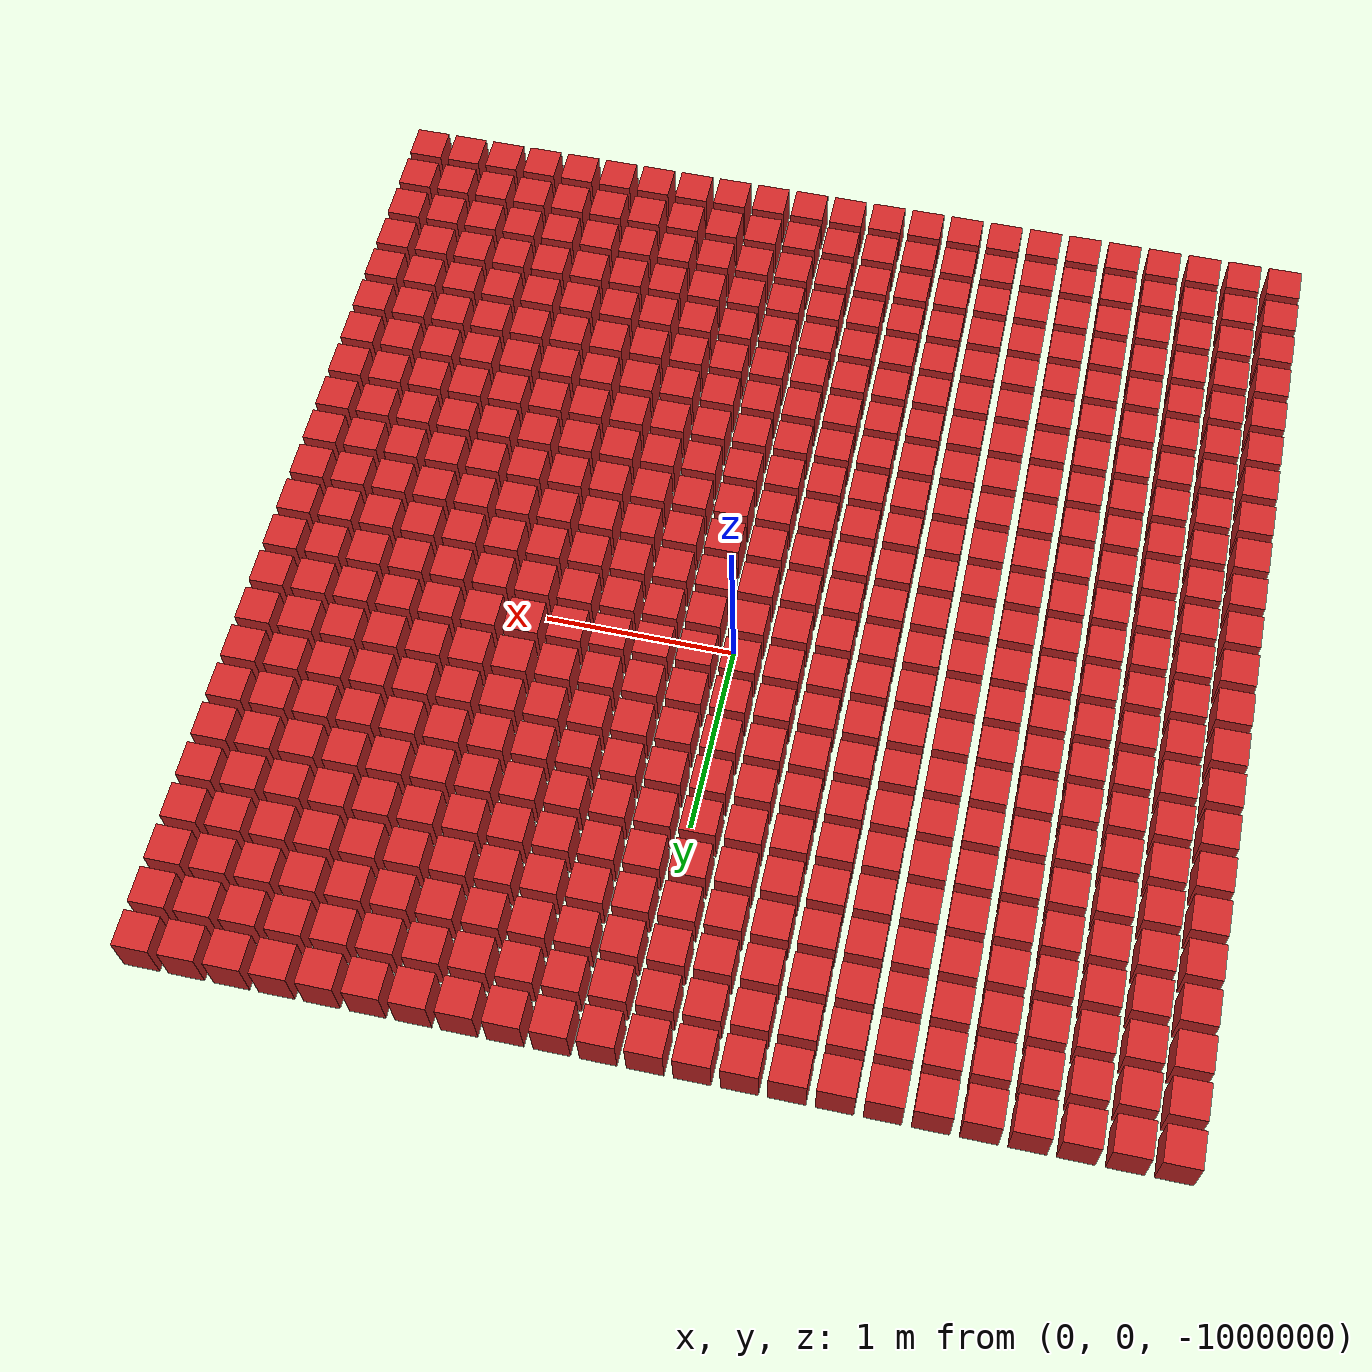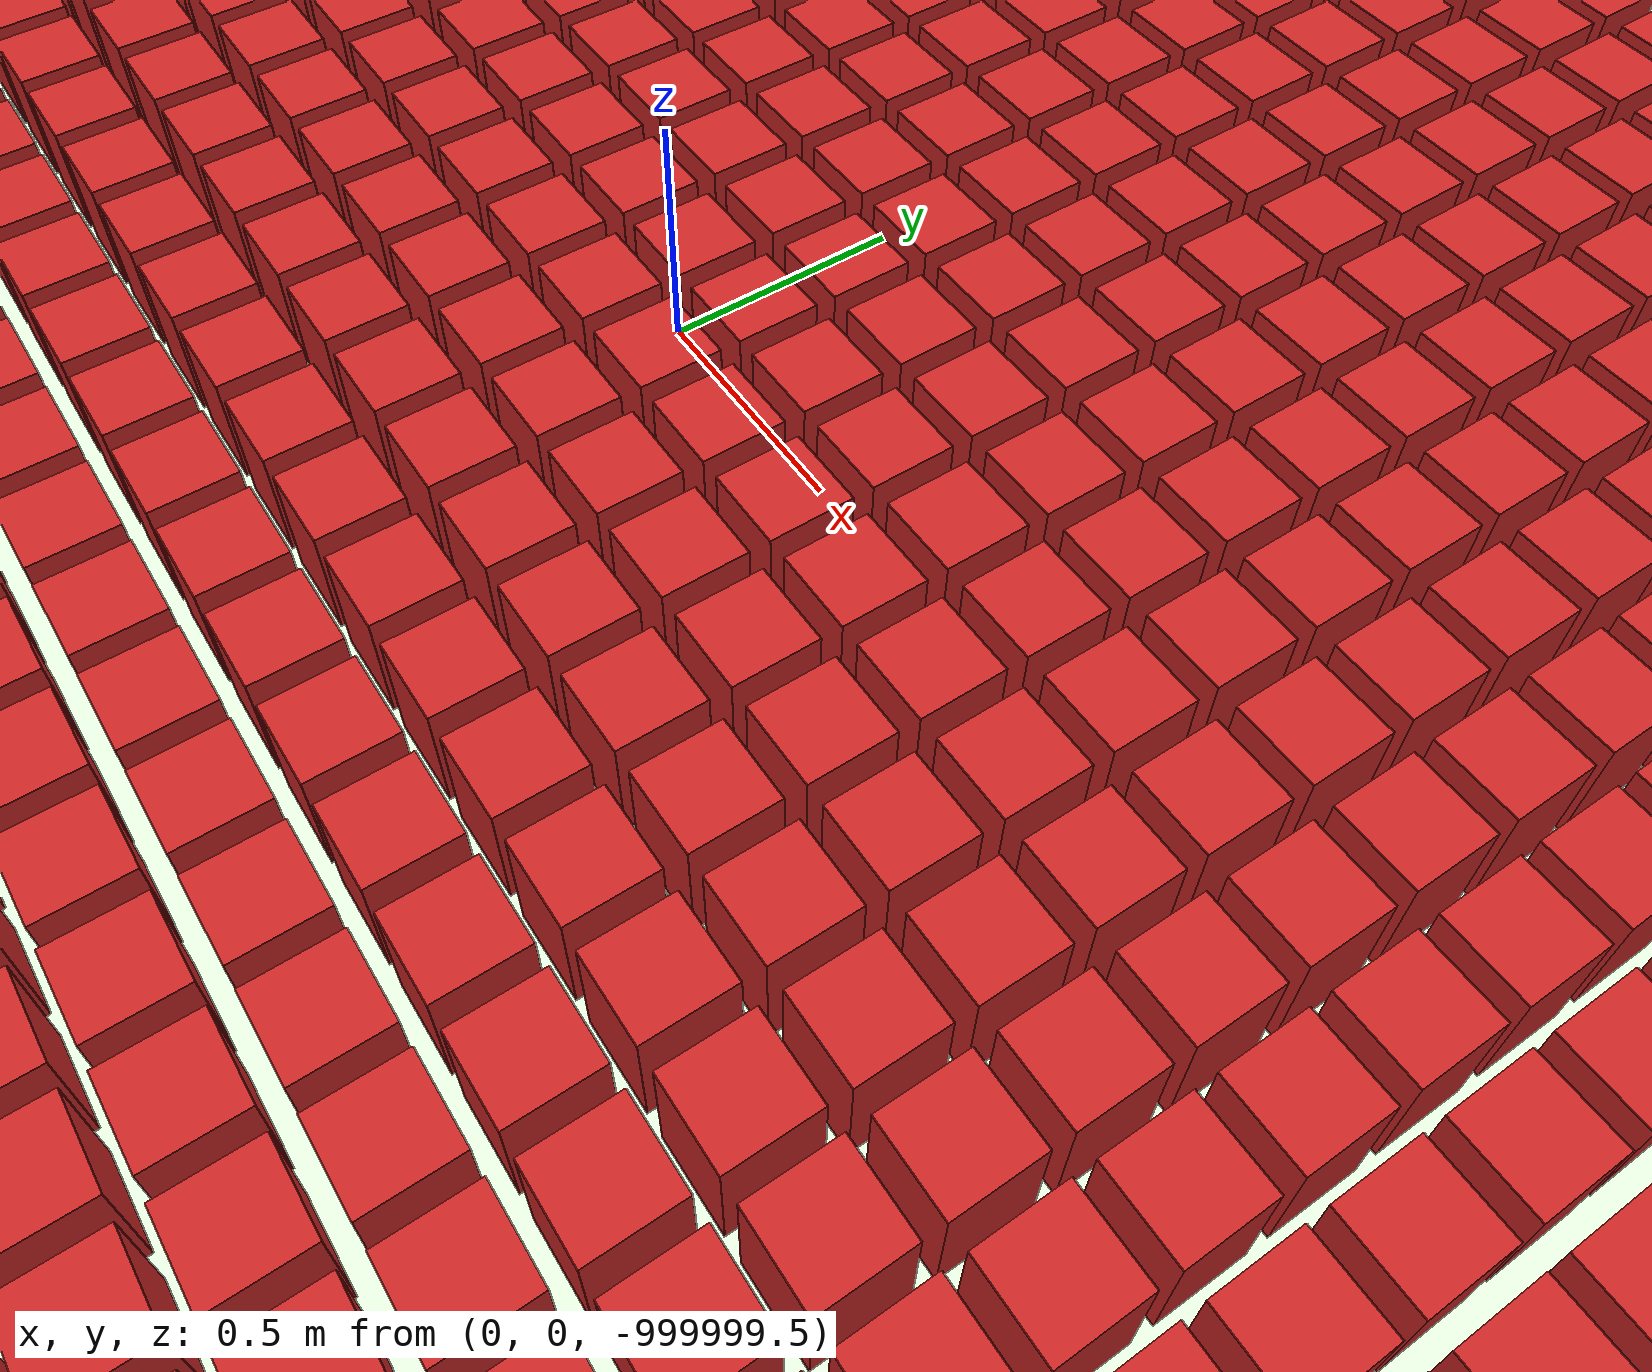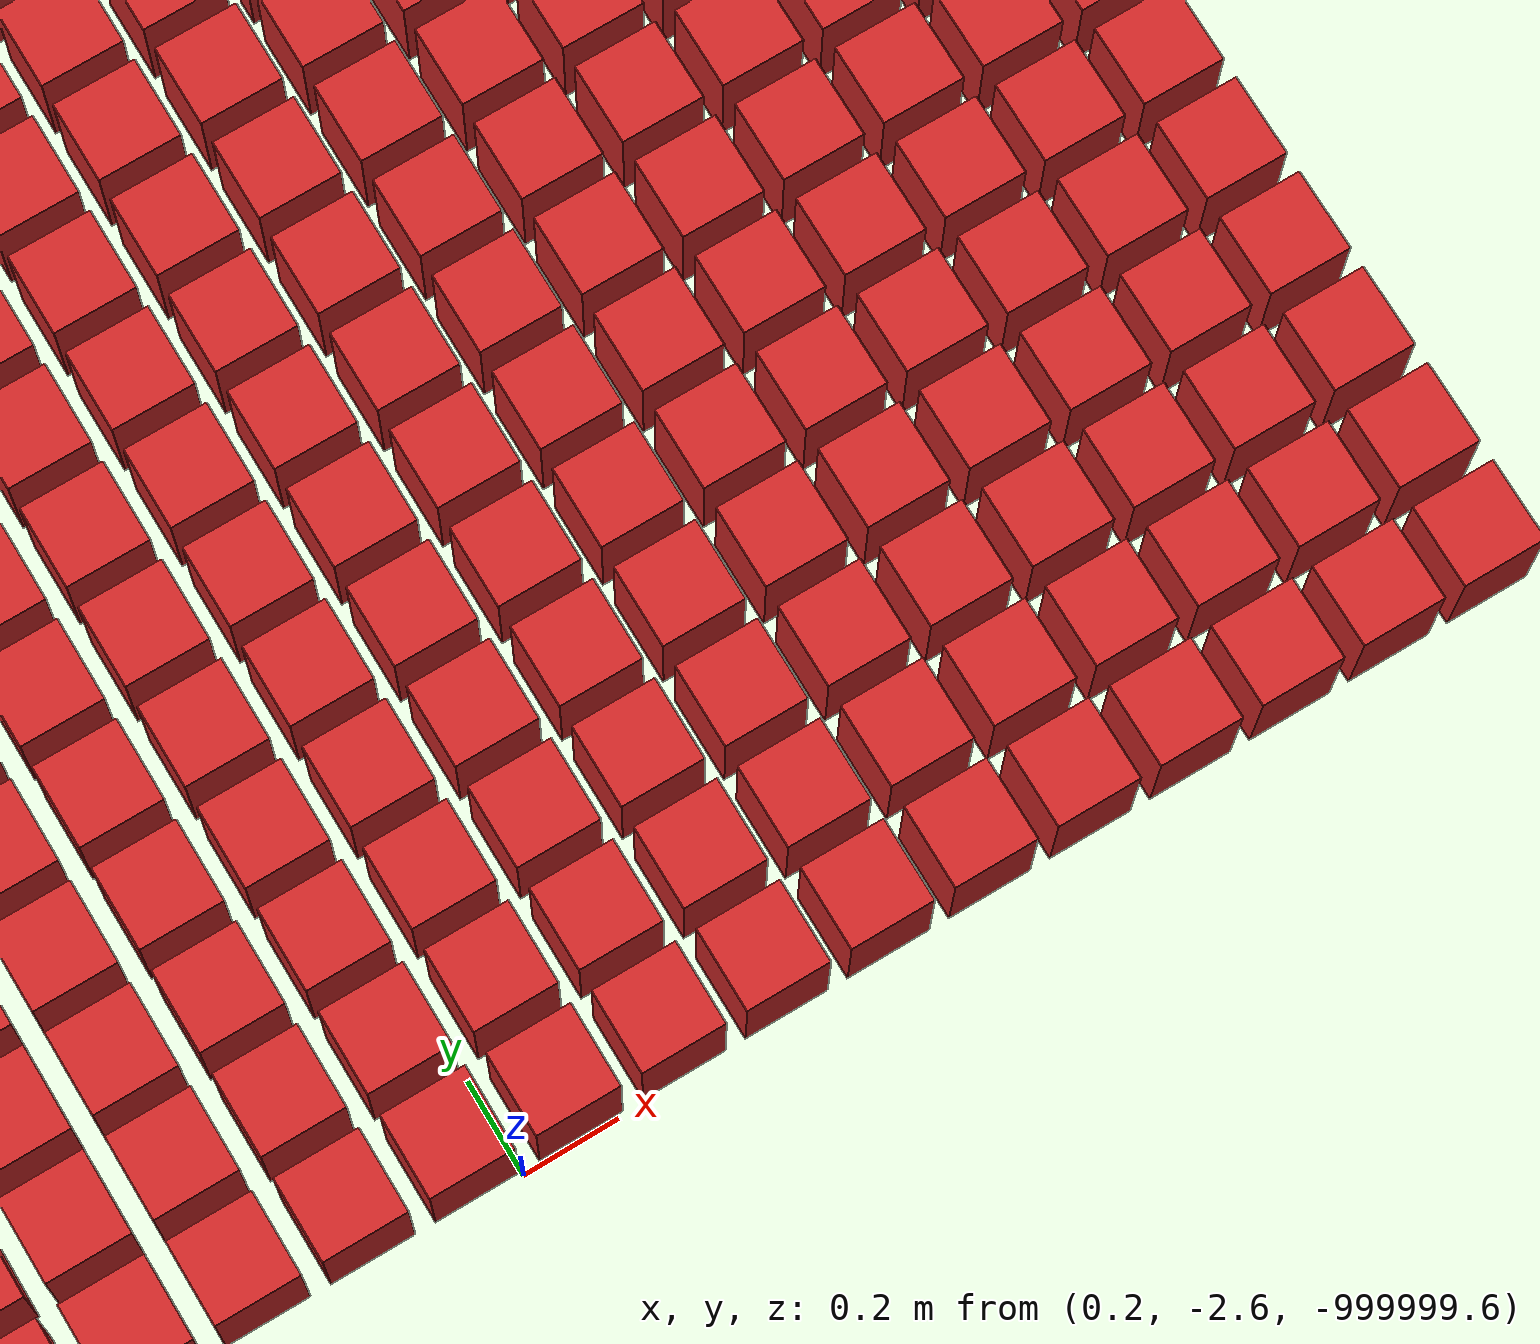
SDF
<sdf version="1.7">
 <world name="default">
  <light name="sun" type="directional">
   <pose>0 0 10 0 -0 0</pose>
   <diffuse>0.8 0.8 0.8 1</diffuse>
   <specular>0.2 0.2 0.2 1</specular>
   <attenuation>
    <range>1000</range>
    <constant>0.9</constant>
    <linear>0.01</linear>
    <quadratic>0.001</quadratic>
   </attenuation>
   <direction>-0.5 0.1 -0.9</direction>
   <spot><inner_angle>0</inner_angle><outer_angle>0</outer_angle><falloff>0</falloff></spot>
  </light>
  <model name="ground_plane">
   <static>1</static>
   <link name="link">
    <collision name="collision">
     <geometry><plane><normal>0 0 1</normal><size>100 100</size></plane></geometry>
     <surface>
      <contact><collide_bitmask>65535</collide_bitmask></contact>
      <friction><ode><mu>100</mu><mu2>50</mu2></ode></friction>
     </surface>
    </collision>
    <visual name="visual">
     <cast_shadows>0</cast_shadows>
     <geometry><plane><normal>0 0 1</normal><size>100 100</size></plane></geometry>
     <material>
      <script><uri>file://media/materials/scripts/gazebo.material</uri><name>Gazebo/Grey</name></script>
     </material>
    </visual>
   </link>
  </model>
  <gravity>0 0 -9.8</gravity>
  <magnetic_field>6e-06 2.3e-05 -4.2e-05</magnetic_field>
  <atmosphere type="adiabatic"/>
  <physics type="ode">
   <max_step_size>0.001</max_step_size>
   <real_time_factor>1</real_time_factor>
   <real_time_update_rate>1000</real_time_update_rate>
  </physics>
  <scene><ambient>0.4 0.4 0.4 1</ambient><background>0.7 0.7 0.7 1</background><shadows>1</shadows></scene>
  <spherical_coordinates>
   <surface_model>EARTH_WGS84</surface_model>
   <latitude_deg>0</latitude_deg>
   <longitude_deg>0</longitude_deg>
   <elevation>0</elevation>
   <heading_deg>0</heading_deg>
  </spherical_coordinates>
  <model name="wall_0">
   <link name="link">
    <pose>0 0 0.5 0 -0 0</pose>
    <inertial>
     <mass>0.5167</mass>
     <inertia>
      <ixx>0.000861167</ixx>
      <ixy>0</ixy>
      <ixz>0</ixz>
      <iyy>0.000861167</iyy>
      <iyz>0</iyz>
      <izz>0.000861167</izz>
     </inertia>
    </inertial>
    <collision name="collision">
     <geometry><box><size>0.21 0.21 0.25</size></box></geometry>
     <surface>
      <contact>
       <poissons_ratio>0.347</poissons_ratio>
       <elastic_modulus>8.8e+09</elastic_modulus>
       <ode><kp>100000</kp><kd>100</kd><max_vel>100</max_vel><min_depth>0.001</min_depth></ode>
      </contact>
      <friction>
       <torsional>
        <coefficient>1</coefficient>
        <use_patch_radius>0</use_patch_radius>
        <surface_radius>0.01</surface_radius>
       </torsional>
      </friction>
     </surface>
    </collision>
    <visual name="visual">
     <geometry><box><size>0.175 0.175 0.25</size></box></geometry>
     <material>
      <script><uri>file://media/materials/scripts/gazebo.material</uri><name>Gazebo/Red</name></script>
     </material>
    </visual>
   </link>
   <pose>-2.5 -2.5 -1e+06 0 -0 0</pose>
  </model>
  <model name="wall_1">
   <link name="link">
    <pose>0 0 0.5 0 -0 0</pose>
    <inertial>
     <mass>0.5167</mass>
     <inertia>
      <ixx>0.000861167</ixx>
      <ixy>0</ixy>
      <ixz>0</ixz>
      <iyy>0.000861167</iyy>
      <iyz>0</iyz>
      <izz>0.000861167</izz>
     </inertia>
    </inertial>
    <collision name="collision">
     <geometry><box><size>0.21 0.21 0.25</size></box></geometry>
     <surface>
      <contact>
       <poissons_ratio>0.347</poissons_ratio>
       <elastic_modulus>8.8e+09</elastic_modulus>
       <ode><kp>100000</kp><kd>100</kd><max_vel>100</max_vel><min_depth>0.001</min_depth></ode>
      </contact>
      <friction>
       <torsional>
        <coefficient>1</coefficient>
        <use_patch_radius>0</use_patch_radius>
        <surface_radius>0.01</surface_radius>
       </torsional>
      </friction>
     </surface>
    </collision>
    <visual name="visual">
     <geometry><box><size>0.175 0.175 0.25</size></box></geometry>
     <material>
      <script><uri>file://media/materials/scripts/gazebo.material</uri><name>Gazebo/Red</name></script>
     </material>
    </visual>
   </link>
   <pose>-2.28261 -2.5 -1e+06 0 -0 0</pose>
  </model>
  <model name="wall_2">
   <link name="link">
    <pose>0 0 0.5 0 -0 0</pose>
    <inertial>
     <mass>0.5167</mass>
     <inertia>
      <ixx>0.000861167</ixx>
      <ixy>0</ixy>
      <ixz>0</ixz>
      <iyy>0.000861167</iyy>
      <iyz>0</iyz>
      <izz>0.000861167</izz>
     </inertia>
    </inertial>
    <collision name="collision">
     <geometry><box><size>0.21 0.21 0.25</size></box></geometry>
     <surface>
      <contact>
       <poissons_ratio>0.347</poissons_ratio>
       <elastic_modulus>8.8e+09</elastic_modulus>
       <ode><kp>100000</kp><kd>100</kd><max_vel>100</max_vel><min_depth>0.001</min_depth></ode>
      </contact>
      <friction>
       <torsional>
        <coefficient>1</coefficient>
        <use_patch_radius>0</use_patch_radius>
        <surface_radius>0.01</surface_radius>
       </torsional>
      </friction>
     </surface>
    </collision>
    <visual name="visual">
     <geometry><box><size>0.175 0.175 0.25</size></box></geometry>
     <material>
      <script><uri>file://media/materials/scripts/gazebo.material</uri><name>Gazebo/Red</name></script>
     </material>
    </visual>
   </link>
   <pose>-2.06522 -2.5 -1e+06 0 -0 0</pose>
  </model>
  <model name="wall_3">
   <link name="link">
    <pose>0 0 0.5 0 -0 0</pose>
    <inertial>
     <mass>0.5167</mass>
     <inertia>
      <ixx>0.000861167</ixx>
      <ixy>0</ixy>
      <ixz>0</ixz>
      <iyy>0.000861167</iyy>
      <iyz>0</iyz>
      <izz>0.000861167</izz>
     </inertia>
    </inertial>
    <collision name="collision">
     <geometry><box><size>0.21 0.21 0.25</size></box></geometry>
     <surface>
      <contact>
       <poissons_ratio>0.347</poissons_ratio>
       <elastic_modulus>8.8e+09</elastic_modulus>
       <ode><kp>100000</kp><kd>100</kd><max_vel>100</max_vel><min_depth>0.001</min_depth></ode>
      </contact>
      <friction>
       <torsional>
        <coefficient>1</coefficient>
        <use_patch_radius>0</use_patch_radius>
        <surface_radius>0.01</surface_radius>
       </torsional>
      </friction>
     </surface>
    </collision>
    <visual name="visual">
     <geometry><box><size>0.175 0.175 0.25</size></box></geometry>
     <material>
      <script><uri>file://media/materials/scripts/gazebo.material</uri><name>Gazebo/Red</name></script>
     </material>
    </visual>
   </link>
   <pose>-1.84783 -2.5 -1e+06 0 -0 0</pose>
  </model>
  <model name="wall_4">
   <link name="link">
    <pose>0 0 0.5 0 -0 0</pose>
    <inertial>
     <mass>0.5167</mass>
     <inertia>
      <ixx>0.000861167</ixx>
      <ixy>0</ixy>
      <ixz>0</ixz>
      <iyy>0.000861167</iyy>
      <iyz>0</iyz>
      <izz>0.000861167</izz>
     </inertia>
    </inertial>
    <collision name="collision">
     <geometry><box><size>0.21 0.21 0.25</size></box></geometry>
     <surface>
      <contact>
       <poissons_ratio>0.347</poissons_ratio>
       <elastic_modulus>8.8e+09</elastic_modulus>
       <ode><kp>100000</kp><kd>100</kd><max_vel>100</max_vel><min_depth>0.001</min_depth></ode>
      </contact>
      <friction>
       <torsional>
        <coefficient>1</coefficient>
        <use_patch_radius>0</use_patch_radius>
        <surface_radius>0.01</surface_radius>
       </torsional>
      </friction>
     </surface>
    </collision>
    <visual name="visual">
     <geometry><box><size>0.175 0.175 0.25</size></box></geometry>
     <material>
      <script><uri>file://media/materials/scripts/gazebo.material</uri><name>Gazebo/Red</name></script>
     </material>
    </visual>
   </link>
   <pose>-1.63043 -2.5 -1e+06 0 -0 0</pose>
  </model>
  <model name="wall_5">
   <link name="link">
    <pose>0 0 0.5 0 -0 0</pose>
    <inertial>
     <mass>0.5167</mass>
     <inertia>
      <ixx>0.000861167</ixx>
      <ixy>0</ixy>
      <ixz>0</ixz>
      <iyy>0.000861167</iyy>
      <iyz>0</iyz>
      <izz>0.000861167</izz>
     </inertia>
    </inertial>
    <collision name="collision">
     <geometry><box><size>0.21 0.21 0.25</size></box></geometry>
     <surface>
      <contact>
       <poissons_ratio>0.347</poissons_ratio>
       <elastic_modulus>8.8e+09</elastic_modulus>
       <ode><kp>100000</kp><kd>100</kd><max_vel>100</max_vel><min_depth>0.001</min_depth></ode>
      </contact>
      <friction>
       <torsional>
        <coefficient>1</coefficient>
        <use_patch_radius>0</use_patch_radius>
        <surface_radius>0.01</surface_radius>
       </torsional>
      </friction>
     </surface>
    </collision>
    <visual name="visual">
     <geometry><box><size>0.175 0.175 0.25</size></box></geometry>
     <material>
      <script><uri>file://media/materials/scripts/gazebo.material</uri><name>Gazebo/Red</name></script>
     </material>
    </visual>
   </link>
   <pose>-1.41304 -2.5 -1e+06 0 -0 0</pose>
  </model>
  <model name="wall_6">
   <link name="link">
    <pose>0 0 0.5 0 -0 0</pose>
    <inertial>
     <mass>0.5167</mass>
     <inertia>
      <ixx>0.000861167</ixx>
      <ixy>0</ixy>
      <ixz>0</ixz>
      <iyy>0.000861167</iyy>
      <iyz>0</iyz>
      <izz>0.000861167</izz>
     </inertia>
    </inertial>
    <collision name="collision">
     <geometry><box><size>0.21 0.21 0.25</size></box></geometry>
     <surface>
      <contact>
       <poissons_ratio>0.347</poissons_ratio>
       <elastic_modulus>8.8e+09</elastic_modulus>
       <ode><kp>100000</kp><kd>100</kd><max_vel>100</max_vel><min_depth>0.001</min_depth></ode>
      </contact>
      <friction>
       <torsional>
        <coefficient>1</coefficient>
        <use_patch_radius>0</use_patch_radius>
        <surface_radius>0.01</surface_radius>
       </torsional>
      </friction>
     </surface>
    </collision>
    <visual name="visual">
     <geometry><box><size>0.175 0.175 0.25</size></box></geometry>
     <material>
      <script><uri>file://media/materials/scripts/gazebo.material</uri><name>Gazebo/Red</name></script>
     </material>
    </visual>
   </link>
   <pose>-1.19565 -2.5 -1e+06 0 -0 0</pose>
  </model>
  <model name="wall_7">
   <link name="link">
    <pose>0 0 0.5 0 -0 0</pose>
    <inertial>
     <mass>0.5167</mass>
     <inertia>
      <ixx>0.000861167</ixx>
      <ixy>0</ixy>
      <ixz>0</ixz>
      <iyy>0.000861167</iyy>
      <iyz>0</iyz>
      <izz>0.000861167</izz>
     </inertia>
    </inertial>
    <collision name="collision">
     <geometry><box><size>0.21 0.21 0.25</size></box></geometry>
     <surface>
      <contact>
       <poissons_ratio>0.347</poissons_ratio>
       <elastic_modulus>8.8e+09</elastic_modulus>
       <ode><kp>100000</kp><kd>100</kd><max_vel>100</max_vel><min_depth>0.001</min_depth></ode>
      </contact>
      <friction>
       <torsional>
        <coefficient>1</coefficient>
        <use_patch_radius>0</use_patch_radius>
        <surface_radius>0.01</surface_radius>
       </torsional>
      </friction>
     </surface>
    </collision>
    <visual name="visual">
     <geometry><box><size>0.175 0.175 0.25</size></box></geometry>
     <material>
      <script><uri>file://media/materials/scripts/gazebo.material</uri><name>Gazebo/Red</name></script>
     </material>
    </visual>
   </link>
   <pose>-0.978261 -2.5 -1e+06 0 -0 0</pose>
  </model>
  <model name="wall_8">
   <link name="link">
    <pose>0 0 0.5 0 -0 0</pose>
    <inertial>
     <mass>0.5167</mass>
     <inertia>
      <ixx>0.000861167</ixx>
      <ixy>0</ixy>
      <ixz>0</ixz>
      <iyy>0.000861167</iyy>
      <iyz>0</iyz>
      <izz>0.000861167</izz>
     </inertia>
    </inertial>
    <collision name="collision">
     <geometry><box><size>0.21 0.21 0.25</size></box></geometry>
     <surface>
      <contact>
       <poissons_ratio>0.347</poissons_ratio>
       <elastic_modulus>8.8e+09</elastic_modulus>
       <ode><kp>100000</kp><kd>100</kd><max_vel>100</max_vel><min_depth>0.001</min_depth></ode>
      </contact>
      <friction>
       <torsional>
        <coefficient>1</coefficient>
        <use_patch_radius>0</use_patch_radius>
        <surface_radius>0.01</surface_radius>
       </torsional>
      </friction>
     </surface>
    </collision>
    <visual name="visual">
     <geometry><box><size>0.175 0.175 0.25</size></box></geometry>
     <material>
      <script><uri>file://media/materials/scripts/gazebo.material</uri><name>Gazebo/Red</name></script>
     </material>
    </visual>
   </link>
   <pose>-0.76087 -2.5 -1e+06 0 -0 0</pose>
  </model>
  <model name="wall_9">
   <link name="link">
    <pose>0 0 0.5 0 -0 0</pose>
    <inertial>
     <mass>0.5167</mass>
     <inertia>
      <ixx>0.000861167</ixx>
      <ixy>0</ixy>
      <ixz>0</ixz>
      <iyy>0.000861167</iyy>
      <iyz>0</iyz>
      <izz>0.000861167</izz>
     </inertia>
    </inertial>
    <collision name="collision">
     <geometry><box><size>0.21 0.21 0.25</size></box></geometry>
     <surface>
      <contact>
       <poissons_ratio>0.347</poissons_ratio>
       <elastic_modulus>8.8e+09</elastic_modulus>
       <ode><kp>100000</kp><kd>100</kd><max_vel>100</max_vel><min_depth>0.001</min_depth></ode>
      </contact>
      <friction>
       <torsional>
        <coefficient>1</coefficient>
        <use_patch_radius>0</use_patch_radius>
        <surface_radius>0.01</surface_radius>
       </torsional>
      </friction>
     </surface>
    </collision>
    <visual name="visual">
     <geometry><box><size>0.175 0.175 0.25</size></box></geometry>
     <material>
      <script><uri>file://media/materials/scripts/gazebo.material</uri><name>Gazebo/Red</name></script>
     </material>
    </visual>
   </link>
   <pose>-0.543478 -2.5 -1e+06 0 -0 0</pose>
  </model>
  <model name="wall_10">
   <link name="link">
    <pose>0 0 0.5 0 -0 0</pose>
    <inertial>
     <mass>0.5167</mass>
     <inertia>
      <ixx>0.000861167</ixx>
      <ixy>0</ixy>
      <ixz>0</ixz>
      <iyy>0.000861167</iyy>
      <iyz>0</iyz>
      <izz>0.000861167</izz>
     </inertia>
    </inertial>
    <collision name="collision">
     <geometry><box><size>0.21 0.21 0.25</size></box></geometry>
     <surface>
      <contact>
       <poissons_ratio>0.347</poissons_ratio>
       <elastic_modulus>8.8e+09</elastic_modulus>
       <ode><kp>100000</kp><kd>100</kd><max_vel>100</max_vel><min_depth>0.001</min_depth></ode>
      </contact>
      <friction>
       <torsional>
        <coefficient>1</coefficient>
        <use_patch_radius>0</use_patch_radius>
        <surface_radius>0.01</surface_radius>
       </torsional>
      </friction>
     </surface>
    </collision>
    <visual name="visual">
     <geometry><box><size>0.175 0.175 0.25</size></box></geometry>
     <material>
      <script><uri>file://media/materials/scripts/gazebo.material</uri><name>Gazebo/Red</name></script>
     </material>
    </visual>
   </link>
   <pose>-0.326087 -2.5 -1e+06 0 -0 0</pose>
  </model>
  <model name="wall_11">
   <link name="link">
    <pose>0 0 0.5 0 -0 0</pose>
    <inertial>
     <mass>0.5167</mass>
     <inertia>
      <ixx>0.000861167</ixx>
      <ixy>0</ixy>
      <ixz>0</ixz>
      <iyy>0.000861167</iyy>
      <iyz>0</iyz>
      <izz>0.000861167</izz>
     </inertia>
    </inertial>
    <collision name="collision">
     <geometry><box><size>0.21 0.21 0.25</size></box></geometry>
     <surface>
      <contact>
       <poissons_ratio>0.347</poissons_ratio>
       <elastic_modulus>8.8e+09</elastic_modulus>
       <ode><kp>100000</kp><kd>100</kd><max_vel>100</max_vel><min_depth>0.001</min_depth></ode>
      </contact>
      <friction>
       <torsional>
        <coefficient>1</coefficient>
        <use_patch_radius>0</use_patch_radius>
        <surface_radius>0.01</surface_radius>
       </torsional>
      </friction>
     </surface>
    </collision>
    <visual name="visual">
     <geometry><box><size>0.175 0.175 0.25</size></box></geometry>
     <material>
      <script><uri>file://media/materials/scripts/gazebo.material</uri><name>Gazebo/Red</name></script>
     </material>
    </visual>
   </link>
   <pose>-0.108696 -2.5 -1e+06 0 -0 0</pose>
  </model>
  <model name="wall_12">
   <link name="link">
    <pose>0 0 0.5 0 -0 0</pose>
    <inertial>
     <mass>0.5167</mass>
     <inertia>
      <ixx>0.000861167</ixx>
      <ixy>0</ixy>
      <ixz>0</ixz>
      <iyy>0.000861167</iyy>
      <iyz>0</iyz>
      <izz>0.000861167</izz>
     </inertia>
    </inertial>
    <collision name="collision">
     <geometry><box><size>0.21 0.21 0.25</size></box></geometry>
     <surface>
      <contact>
       <poissons_ratio>0.347</poissons_ratio>
       <elastic_modulus>8.8e+09</elastic_modulus>
       <ode><kp>100000</kp><kd>100</kd><max_vel>100</max_vel><min_depth>0.001</min_depth></ode>
      </contact>
      <friction>
       <torsional>
        <coefficient>1</coefficient>
        <use_patch_radius>0</use_patch_radius>
        <surface_radius>0.01</surface_radius>
       </torsional>
      </friction>
     </surface>
    </collision>
    <visual name="visual">
     <geometry><box><size>0.175 0.175 0.25</size></box></geometry>
     <material>
      <script><uri>file://media/materials/scripts/gazebo.material</uri><name>Gazebo/Red</name></script>
     </material>
    </visual>
   </link>
   <pose>0.108696 -2.5 -1e+06 0 -0 0</pose>
  </model>
  <model name="wall_13">
   <link name="link">
    <pose>0 0 0.5 0 -0 0</pose>
    <inertial>
     <mass>0.5167</mass>
     <inertia>
      <ixx>0.000861167</ixx>
      <ixy>0</ixy>
      <ixz>0</ixz>
      <iyy>0.000861167</iyy>
      <iyz>0</iyz>
      <izz>0.000861167</izz>
     </inertia>
    </inertial>
    <collision name="collision">
     <geometry><box><size>0.21 0.21 0.25</size></box></geometry>
     <surface>
      <contact>
       <poissons_ratio>0.347</poissons_ratio>
       <elastic_modulus>8.8e+09</elastic_modulus>
       <ode><kp>100000</kp><kd>100</kd><max_vel>100</max_vel><min_depth>0.001</min_depth></ode>
      </contact>
      <friction>
       <torsional>
        <coefficient>1</coefficient>
        <use_patch_radius>0</use_patch_radius>
        <surface_radius>0.01</surface_radius>
       </torsional>
      </friction>
     </surface>
    </collision>
    <visual name="visual">
     <geometry><box><size>0.175 0.175 0.25</size></box></geometry>
     <material>
      <script><uri>file://media/materials/scripts/gazebo.material</uri><name>Gazebo/Red</name></script>
     </material>
    </visual>
   </link>
   <pose>0.326087 -2.5 -1e+06 0 -0 0</pose>
  </model>
  <model name="wall_14">
   <link name="link">
    <pose>0 0 0.5 0 -0 0</pose>
    <inertial>
     <mass>0.5167</mass>
     <inertia>
      <ixx>0.000861167</ixx>
      <ixy>0</ixy>
      <ixz>0</ixz>
      <iyy>0.000861167</iyy>
      <iyz>0</iyz>
      <izz>0.000861167</izz>
     </inertia>
    </inertial>
    <collision name="collision">
     <geometry><box><size>0.21 0.21 0.25</size></box></geometry>
     <surface>
      <contact>
       <poissons_ratio>0.347</poissons_ratio>
       <elastic_modulus>8.8e+09</elastic_modulus>
       <ode><kp>100000</kp><kd>100</kd><max_vel>100</max_vel><min_depth>0.001</min_depth></ode>
      </contact>
      <friction>
       <torsional>
        <coefficient>1</coefficient>
        <use_patch_radius>0</use_patch_radius>
        <surface_radius>0.01</surface_radius>
       </torsional>
      </friction>
     </surface>
    </collision>
    <visual name="visual">
     <geometry><box><size>0.175 0.175 0.25</size></box></geometry>
     <material>
      <script><uri>file://media/materials/scripts/gazebo.material</uri><name>Gazebo/Red</name></script>
     </material>
    </visual>
   </link>
   <pose>0.543478 -2.5 -1e+06 0 -0 0</pose>
  </model>
  <model name="wall_15">
   <link name="link">
    <pose>0 0 0.5 0 -0 0</pose>
    <inertial>
     <mass>0.5167</mass>
     <inertia>
      <ixx>0.000861167</ixx>
      <ixy>0</ixy>
      <ixz>0</ixz>
      <iyy>0.000861167</iyy>
      <iyz>0</iyz>
      <izz>0.000861167</izz>
     </inertia>
    </inertial>
    <collision name="collision">
     <geometry><box><size>0.21 0.21 0.25</size></box></geometry>
     <surface>
      <contact>
       <poissons_ratio>0.347</poissons_ratio>
       <elastic_modulus>8.8e+09</elastic_modulus>
       <ode><kp>100000</kp><kd>100</kd><max_vel>100</max_vel><min_depth>0.001</min_depth></ode>
      </contact>
      <friction>
       <torsional>
        <coefficient>1</coefficient>
        <use_patch_radius>0</use_patch_radius>
        <surface_radius>0.01</surface_radius>
       </torsional>
      </friction>
     </surface>
    </collision>
    <visual name="visual">
     <geometry><box><size>0.175 0.175 0.25</size></box></geometry>
     <material>
      <script><uri>file://media/materials/scripts/gazebo.material</uri><name>Gazebo/Red</name></script>
     </material>
    </visual>
   </link>
   <pose>0.76087 -2.5 -1e+06 0 -0 0</pose>
  </model>
  <model name="wall_16">
   <link name="link">
    <pose>0 0 0.5 0 -0 0</pose>
    <inertial>
     <mass>0.5167</mass>
     <inertia>
      <ixx>0.000861167</ixx>
      <ixy>0</ixy>
      <ixz>0</ixz>
      <iyy>0.000861167</iyy>
      <iyz>0</iyz>
      <izz>0.000861167</izz>
     </inertia>
    </inertial>
    <collision name="collision">
     <geometry><box><size>0.21 0.21 0.25</size></box></geometry>
     <surface>
      <contact>
       <poissons_ratio>0.347</poissons_ratio>
       <elastic_modulus>8.8e+09</elastic_modulus>
       <ode><kp>100000</kp><kd>100</kd><max_vel>100</max_vel><min_depth>0.001</min_depth></ode>
      </contact>
      <friction>
       <torsional>
        <coefficient>1</coefficient>
        <use_patch_radius>0</use_patch_radius>
        <surface_radius>0.01</surface_radius>
       </torsional>
      </friction>
     </surface>
    </collision>
    <visual name="visual">
     <geometry><box><size>0.175 0.175 0.25</size></box></geometry>
     <material>
      <script><uri>file://media/materials/scripts/gazebo.material</uri><name>Gazebo/Red</name></script>
     </material>
    </visual>
   </link>
   <pose>0.978261 -2.5 -1e+06 0 -0 0</pose>
  </model>
  <model name="wall_17">
   <link name="link">
    <pose>0 0 0.5 0 -0 0</pose>
    <inertial>
     <mass>0.5167</mass>
     <inertia>
      <ixx>0.000861167</ixx>
      <ixy>0</ixy>
      <ixz>0</ixz>
      <iyy>0.000861167</iyy>
      <iyz>0</iyz>
      <izz>0.000861167</izz>
     </inertia>
    </inertial>
    <collision name="collision">
     <geometry><box><size>0.21 0.21 0.25</size></box></geometry>
     <surface>
      <contact>
       <poissons_ratio>0.347</poissons_ratio>
       <elastic_modulus>8.8e+09</elastic_modulus>
       <ode><kp>100000</kp><kd>100</kd><max_vel>100</max_vel><min_depth>0.001</min_depth></ode>
      </contact>
      <friction>
       <torsional>
        <coefficient>1</coefficient>
        <use_patch_radius>0</use_patch_radius>
        <surface_radius>0.01</surface_radius>
       </torsional>
      </friction>
     </surface>
    </collision>
    <visual name="visual">
     <geometry><box><size>0.175 0.175 0.25</size></box></geometry>
     <material>
      <script><uri>file://media/materials/scripts/gazebo.material</uri><name>Gazebo/Red</name></script>
     </material>
    </visual>
   </link>
   <pose>1.19565 -2.5 -1e+06 0 -0 0</pose>
  </model>
  <model name="wall_18">
   <link name="link">
    <pose>0 0 0.5 0 -0 0</pose>
    <inertial>
     <mass>0.5167</mass>
     <inertia>
      <ixx>0.000861167</ixx>
      <ixy>0</ixy>
      <ixz>0</ixz>
      <iyy>0.000861167</iyy>
      <iyz>0</iyz>
      <izz>0.000861167</izz>
     </inertia>
    </inertial>
    <collision name="collision">
     <geometry><box><size>0.21 0.21 0.25</size></box></geometry>
     <surface>
      <contact>
       <poissons_ratio>0.347</poissons_ratio>
       <elastic_modulus>8.8e+09</elastic_modulus>
       <ode><kp>100000</kp><kd>100</kd><max_vel>100</max_vel><min_depth>0.001</min_depth></ode>
      </contact>
      <friction>
       <torsional>
        <coefficient>1</coefficient>
        <use_patch_radius>0</use_patch_radius>
        <surface_radius>0.01</surface_radius>
       </torsional>
      </friction>
     </surface>
    </collision>
    <visual name="visual">
     <geometry><box><size>0.175 0.175 0.25</size></box></geometry>
     <material>
      <script><uri>file://media/materials/scripts/gazebo.material</uri><name>Gazebo/Red</name></script>
     </material>
    </visual>
   </link>
   <pose>1.41304 -2.5 -1e+06 0 -0 0</pose>
  </model>
  <model name="wall_19">
   <link name="link">
    <pose>0 0 0.5 0 -0 0</pose>
    <inertial>
     <mass>0.5167</mass>
     <inertia>
      <ixx>0.000861167</ixx>
      <ixy>0</ixy>
      <ixz>0</ixz>
      <iyy>0.000861167</iyy>
      <iyz>0</iyz>
      <izz>0.000861167</izz>
     </inertia>
    </inertial>
    <collision name="collision">
     <geometry><box><size>0.21 0.21 0.25</size></box></geometry>
     <surface>
      <contact>
       <poissons_ratio>0.347</poissons_ratio>
       <elastic_modulus>8.8e+09</elastic_modulus>
       <ode><kp>100000</kp><kd>100</kd><max_vel>100</max_vel><min_depth>0.001</min_depth></ode>
      </contact>
      <friction>
       <torsional>
        <coefficient>1</coefficient>
        <use_patch_radius>0</use_patch_radius>
        <surface_radius>0.01</surface_radius>
       </torsional>
      </friction>
     </surface>
    </collision>
    <visual name="visual">
     <geometry><box><size>0.175 0.175 0.25</size></box></geometry>
     <material>
      <script><uri>file://media/materials/scripts/gazebo.material</uri><name>Gazebo/Red</name></script>
     </material>
    </visual>
   </link>
   <pose>1.63043 -2.5 -1e+06 0 -0 0</pose>
  </model>
  <model name="wall_20">
   <link name="link">
    <pose>0 0 0.5 0 -0 0</pose>
    <inertial>
     <mass>0.5167</mass>
     <inertia>
      <ixx>0.000861167</ixx>
      <ixy>0</ixy>
      <ixz>0</ixz>
      <iyy>0.000861167</iyy>
      <iyz>0</iyz>
      <izz>0.000861167</izz>
     </inertia>
    </inertial>
    <collision name="collision">
     <geometry><box><size>0.21 0.21 0.25</size></box></geometry>
     <surface>
      <contact>
       <poissons_ratio>0.347</poissons_ratio>
       <elastic_modulus>8.8e+09</elastic_modulus>
       <ode><kp>100000</kp><kd>100</kd><max_vel>100</max_vel><min_depth>0.001</min_depth></ode>
      </contact>
      <friction>
       <torsional>
        <coefficient>1</coefficient>
        <use_patch_radius>0</use_patch_radius>
        <surface_radius>0.01</surface_radius>
       </torsional>
      </friction>
     </surface>
    </collision>
    <visual name="visual">
     <geometry><box><size>0.175 0.175 0.25</size></box></geometry>
     <material>
      <script><uri>file://media/materials/scripts/gazebo.material</uri><name>Gazebo/Red</name></script>
     </material>
    </visual>
   </link>
   <pose>1.84783 -2.5 -1e+06 0 -0 0</pose>
  </model>
  <model name="wall_21">
   <link name="link">
    <pose>0 0 0.5 0 -0 0</pose>
    <inertial>
     <mass>0.5167</mass>
     <inertia>
      <ixx>0.000861167</ixx>
      <ixy>0</ixy>
      <ixz>0</ixz>
      <iyy>0.000861167</iyy>
      <iyz>0</iyz>
      <izz>0.000861167</izz>
     </inertia>
    </inertial>
    <collision name="collision">
     <geometry><box><size>0.21 0.21 0.25</size></box></geometry>
     <surface>
      <contact>
       <poissons_ratio>0.347</poissons_ratio>
       <elastic_modulus>8.8e+09</elastic_modulus>
       <ode><kp>100000</kp><kd>100</kd><max_vel>100</max_vel><min_depth>0.001</min_depth></ode>
      </contact>
      <friction>
       <torsional>
        <coefficient>1</coefficient>
        <use_patch_radius>0</use_patch_radius>
        <surface_radius>0.01</surface_radius>
       </torsional>
      </friction>
     </surface>
    </collision>
    <visual name="visual">
     <geometry><box><size>0.175 0.175 0.25</size></box></geometry>
     <material>
      <script><uri>file://media/materials/scripts/gazebo.material</uri><name>Gazebo/Red</name></script>
     </material>
    </visual>
   </link>
   <pose>2.06522 -2.5 -1e+06 0 -0 0</pose>
  </model>
  <model name="wall_22">
   <link name="link">
    <pose>0 0 0.5 0 -0 0</pose>
    <inertial>
     <mass>0.5167</mass>
     <inertia>
      <ixx>0.000861167</ixx>
      <ixy>0</ixy>
      <ixz>0</ixz>
      <iyy>0.000861167</iyy>
      <iyz>0</iyz>
      <izz>0.000861167</izz>
     </inertia>
    </inertial>
    <collision name="collision">
     <geometry><box><size>0.21 0.21 0.25</size></box></geometry>
     <surface>
      <contact>
       <poissons_ratio>0.347</poissons_ratio>
       <elastic_modulus>8.8e+09</elastic_modulus>
       <ode><kp>100000</kp><kd>100</kd><max_vel>100</max_vel><min_depth>0.001</min_depth></ode>
      </contact>
      <friction>
       <torsional>
        <coefficient>1</coefficient>
        <use_patch_radius>0</use_patch_radius>
        <surface_radius>0.01</surface_radius>
       </torsional>
      </friction>
     </surface>
    </collision>
    <visual name="visual">
     <geometry><box><size>0.175 0.175 0.25</size></box></geometry>
     <material>
      <script><uri>file://media/materials/scripts/gazebo.material</uri><name>Gazebo/Red</name></script>
     </material>
    </visual>
   </link>
   <pose>2.28261 -2.5 -1e+06 0 -0 0</pose>
  </model>
  <model name="wall_23">
   <link name="link">
    <pose>0 0 0.5 0 -0 0</pose>
    <inertial>
     <mass>0.5167</mass>
     <inertia>
      <ixx>0.000861167</ixx>
      <ixy>0</ixy>
      <ixz>0</ixz>
      <iyy>0.000861167</iyy>
      <iyz>0</iyz>
      <izz>0.000861167</izz>
     </inertia>
    </inertial>
    <collision name="collision">
     <geometry><box><size>0.21 0.21 0.25</size></box></geometry>
     <surface>
      <contact>
       <poissons_ratio>0.347</poissons_ratio>
       <elastic_modulus>8.8e+09</elastic_modulus>
       <ode><kp>100000</kp><kd>100</kd><max_vel>100</max_vel><min_depth>0.001</min_depth></ode>
      </contact>
      <friction>
       <torsional>
        <coefficient>1</coefficient>
        <use_patch_radius>0</use_patch_radius>
        <surface_radius>0.01</surface_radius>
       </torsional>
      </friction>
     </surface>
    </collision>
    <visual name="visual">
     <geometry><box><size>0.175 0.175 0.25</size></box></geometry>
     <material>
      <script><uri>file://media/materials/scripts/gazebo.material</uri><name>Gazebo/Red</name></script>
     </material>
    </visual>
   </link>
   <pose>-2.5 -2.28261 -1e+06 0 -0 0</pose>
  </model>
  <model name="wall_24">
   <link name="link">
    <pose>0 0 0.5 0 -0 0</pose>
    <inertial>
     <mass>0.5167</mass>
     <inertia>
      <ixx>0.000861167</ixx>
      <ixy>0</ixy>
      <ixz>0</ixz>
      <iyy>0.000861167</iyy>
      <iyz>0</iyz>
      <izz>0.000861167</izz>
     </inertia>
    </inertial>
    <collision name="collision">
     <geometry><box><size>0.21 0.21 0.25</size></box></geometry>
     <surface>
      <contact>
       <poissons_ratio>0.347</poissons_ratio>
       <elastic_modulus>8.8e+09</elastic_modulus>
       <ode><kp>100000</kp><kd>100</kd><max_vel>100</max_vel><min_depth>0.001</min_depth></ode>
      </contact>
      <friction>
       <torsional>
        <coefficient>1</coefficient>
        <use_patch_radius>0</use_patch_radius>
        <surface_radius>0.01</surface_radius>
       </torsional>
      </friction>
     </surface>
    </collision>
    <visual name="visual">
     <geometry><box><size>0.175 0.175 0.25</size></box></geometry>
     <material>
      <script><uri>file://media/materials/scripts/gazebo.material</uri><name>Gazebo/Red</name></script>
     </material>
    </visual>
   </link>
   <pose>-2.28261 -2.28261 -1e+06 0 -0 0</pose>
  </model>
  <model name="wall_25">
   <link name="link">
    <pose>0 0 0.5 0 -0 0</pose>
    <inertial>
     <mass>0.5167</mass>
     <inertia>
      <ixx>0.000861167</ixx>
      <ixy>0</ixy>
      <ixz>0</ixz>
      <iyy>0.000861167</iyy>
      <iyz>0</iyz>
      <izz>0.000861167</izz>
     </inertia>
    </inertial>
    <collision name="collision">
     <geometry><box><size>0.21 0.21 0.25</size></box></geometry>
     <surface>
      <contact>
       <poissons_ratio>0.347</poissons_ratio>
       <elastic_modulus>8.8e+09</elastic_modulus>
       <ode><kp>100000</kp><kd>100</kd><max_vel>100</max_vel><min_depth>0.001</min_depth></ode>
      </contact>
      <friction>
       <torsional>
        <coefficient>1</coefficient>
        <use_patch_radius>0</use_patch_radius>
        <surface_radius>0.01</surface_radius>
       </torsional>
      </friction>
     </surface>
    </collision>
    <visual name="visual">
     <geometry><box><size>0.175 0.175 0.25</size></box></geometry>
     <material>
      <script><uri>file://media/materials/scripts/gazebo.material</uri><name>Gazebo/Red</name></script>
     </material>
    </visual>
   </link>
   <pose>-2.06522 -2.28261 -1e+06 0 -0 0</pose>
  </model>
  <model name="wall_26">
   <link name="link">
    <pose>0 0 0.5 0 -0 0</pose>
    <inertial>
     <mass>0.5167</mass>
     <inertia>
      <ixx>0.000861167</ixx>
      <ixy>0</ixy>
      <ixz>0</ixz>
      <iyy>0.000861167</iyy>
      <iyz>0</iyz>
      <izz>0.000861167</izz>
     </inertia>
    </inertial>
    <collision name="collision">
     <geometry><box><size>0.21 0.21 0.25</size></box></geometry>
     <surface>
      <contact>
       <poissons_ratio>0.347</poissons_ratio>
       <elastic_modulus>8.8e+09</elastic_modulus>
       <ode><kp>100000</kp><kd>100</kd><max_vel>100</max_vel><min_depth>0.001</min_depth></ode>
      </contact>
      <friction>
       <torsional>
        <coefficient>1</coefficient>
        <use_patch_radius>0</use_patch_radius>
        <surface_radius>0.01</surface_radius>
       </torsional>
      </friction>
     </surface>
    </collision>
    <visual name="visual">
     <geometry><box><size>0.175 0.175 0.25</size></box></geometry>
     <material>
      <script><uri>file://media/materials/scripts/gazebo.material</uri><name>Gazebo/Red</name></script>
     </material>
    </visual>
   </link>
   <pose>-1.84783 -2.28261 -1e+06 0 -0 0</pose>
  </model>
  <model name="wall_27">
   <link name="link">
    <pose>0 0 0.5 0 -0 0</pose>
    <inertial>
     <mass>0.5167</mass>
     <inertia>
      <ixx>0.000861167</ixx>
      <ixy>0</ixy>
      <ixz>0</ixz>
      <iyy>0.000861167</iyy>
      <iyz>0</iyz>
      <izz>0.000861167</izz>
     </inertia>
    </inertial>
    <collision name="collision">
     <geometry><box><size>0.21 0.21 0.25</size></box></geometry>
     <surface>
      <contact>
       <poissons_ratio>0.347</poissons_ratio>
       <elastic_modulus>8.8e+09</elastic_modulus>
       <ode><kp>100000</kp><kd>100</kd><max_vel>100</max_vel><min_depth>0.001</min_depth></ode>
      </contact>
      <friction>
       <torsional>
        <coefficient>1</coefficient>
        <use_patch_radius>0</use_patch_radius>
        <surface_radius>0.01</surface_radius>
       </torsional>
      </friction>
     </surface>
    </collision>
    <visual name="visual">
     <geometry><box><size>0.175 0.175 0.25</size></box></geometry>
     <material>
      <script><uri>file://media/materials/scripts/gazebo.material</uri><name>Gazebo/Red</name></script>
     </material>
    </visual>
   </link>
   <pose>-1.63043 -2.28261 -1e+06 0 -0 0</pose>
  </model>
  <model name="wall_28">
   <link name="link">
    <pose>0 0 0.5 0 -0 0</pose>
    <inertial>
     <mass>0.5167</mass>
     <inertia>
      <ixx>0.000861167</ixx>
      <ixy>0</ixy>
      <ixz>0</ixz>
      <iyy>0.000861167</iyy>
      <iyz>0</iyz>
      <izz>0.000861167</izz>
     </inertia>
    </inertial>
    <collision name="collision">
     <geometry><box><size>0.21 0.21 0.25</size></box></geometry>
     <surface>
      <contact>
       <poissons_ratio>0.347</poissons_ratio>
       <elastic_modulus>8.8e+09</elastic_modulus>
       <ode><kp>100000</kp><kd>100</kd><max_vel>100</max_vel><min_depth>0.001</min_depth></ode>
      </contact>
      <friction>
       <torsional>
        <coefficient>1</coefficient>
        <use_patch_radius>0</use_patch_radius>
        <surface_radius>0.01</surface_radius>
       </torsional>
      </friction>
     </surface>
    </collision>
    <visual name="visual">
     <geometry><box><size>0.175 0.175 0.25</size></box></geometry>
     <material>
      <script><uri>file://media/materials/scripts/gazebo.material</uri><name>Gazebo/Red</name></script>
     </material>
    </visual>
   </link>
   <pose>-1.41304 -2.28261 -1e+06 0 -0 0</pose>
  </model>
  <model name="wall_29">
   <link name="link">
    <pose>0 0 0.5 0 -0 0</pose>
    <inertial>
     <mass>0.5167</mass>
     <inertia>
      <ixx>0.000861167</ixx>
      <ixy>0</ixy>
      <ixz>0</ixz>
      <iyy>0.000861167</iyy>
      <iyz>0</iyz>
      <izz>0.000861167</izz>
     </inertia>
    </inertial>
    <collision name="collision">
     <geometry><box><size>0.21 0.21 0.25</size></box></geometry>
     <surface>
      <contact>
       <poissons_ratio>0.347</poissons_ratio>
       <elastic_modulus>8.8e+09</elastic_modulus>
       <ode><kp>100000</kp><kd>100</kd><max_vel>100</max_vel><min_depth>0.001</min_depth></ode>
      </contact>
      <friction>
       <torsional>
        <coefficient>1</coefficient>
        <use_patch_radius>0</use_patch_radius>
        <surface_radius>0.01</surface_radius>
       </torsional>
      </friction>
     </surface>
    </collision>
    <visual name="visual">
     <geometry><box><size>0.175 0.175 0.25</size></box></geometry>
     <material>
      <script><uri>file://media/materials/scripts/gazebo.material</uri><name>Gazebo/Red</name></script>
     </material>
    </visual>
   </link>
   <pose>-1.19565 -2.28261 -1e+06 0 -0 0</pose>
  </model>
  <model name="wall_30">
   <link name="link">
    <pose>0 0 0.5 0 -0 0</pose>
    <inertial>
     <mass>0.5167</mass>
     <inertia>
      <ixx>0.000861167</ixx>
      <ixy>0</ixy>
      <ixz>0</ixz>
      <iyy>0.000861167</iyy>
      <iyz>0</iyz>
      <izz>0.000861167</izz>
     </inertia>
    </inertial>
    <collision name="collision">
     <geometry><box><size>0.21 0.21 0.25</size></box></geometry>
     <surface>
      <contact>
       <poissons_ratio>0.347</poissons_ratio>
       <elastic_modulus>8.8e+09</elastic_modulus>
       <ode><kp>100000</kp><kd>100</kd><max_vel>100</max_vel><min_depth>0.001</min_depth></ode>
      </contact>
      <friction>
       <torsional>
        <coefficient>1</coefficient>
        <use_patch_radius>0</use_patch_radius>
        <surface_radius>0.01</surface_radius>
       </torsional>
      </friction>
     </surface>
    </collision>
    <visual name="visual">
     <geometry><box><size>0.175 0.175 0.25</size></box></geometry>
     <material>
      <script><uri>file://media/materials/scripts/gazebo.material</uri><name>Gazebo/Red</name></script>
     </material>
    </visual>
   </link>
   <pose>-0.978261 -2.28261 -1e+06 0 -0 0</pose>
  </model>
  <model name="wall_31">
   <link name="link">
    <pose>0 0 0.5 0 -0 0</pose>
    <inertial>
     <mass>0.5167</mass>
     <inertia>
      <ixx>0.000861167</ixx>
      <ixy>0</ixy>
      <ixz>0</ixz>
      <iyy>0.000861167</iyy>
      <iyz>0</iyz>
      <izz>0.000861167</izz>
     </inertia>
    </inertial>
    <collision name="collision">
     <geometry><box><size>0.21 0.21 0.25</size></box></geometry>
     <surface>
      <contact>
       <poissons_ratio>0.347</poissons_ratio>
       <elastic_modulus>8.8e+09</elastic_modulus>
       <ode><kp>100000</kp><kd>100</kd><max_vel>100</max_vel><min_depth>0.001</min_depth></ode>
      </contact>
      <friction>
       <torsional>
        <coefficient>1</coefficient>
        <use_patch_radius>0</use_patch_radius>
        <surface_radius>0.01</surface_radius>
       </torsional>
      </friction>
     </surface>
    </collision>
    <visual name="visual">
     <geometry><box><size>0.175 0.175 0.25</size></box></geometry>
     <material>
      <script><uri>file://media/materials/scripts/gazebo.material</uri><name>Gazebo/Red</name></script>
     </material>
    </visual>
   </link>
   <pose>-0.76087 -2.28261 -1e+06 0 -0 0</pose>
  </model>
  <model name="wall_32">
   <link name="link">
    <pose>0 0 0.5 0 -0 0</pose>
    <inertial>
     <mass>0.5167</mass>
     <inertia>
      <ixx>0.000861167</ixx>
      <ixy>0</ixy>
      <ixz>0</ixz>
      <iyy>0.000861167</iyy>
      <iyz>0</iyz>
      <izz>0.000861167</izz>
     </inertia>
    </inertial>
    <collision name="collision">
     <geometry><box><size>0.21 0.21 0.25</size></box></geometry>
     <surface>
      <contact>
       <poissons_ratio>0.347</poissons_ratio>
       <elastic_modulus>8.8e+09</elastic_modulus>
       <ode><kp>100000</kp><kd>100</kd><max_vel>100</max_vel><min_depth>0.001</min_depth></ode>
      </contact>
      <friction>
       <torsional>
        <coefficient>1</coefficient>
        <use_patch_radius>0</use_patch_radius>
        <surface_radius>0.01</surface_radius>
       </torsional>
      </friction>
     </surface>
    </collision>
    <visual name="visual">
     <geometry><box><size>0.175 0.175 0.25</size></box></geometry>
     <material>
      <script><uri>file://media/materials/scripts/gazebo.material</uri><name>Gazebo/Red</name></script>
     </material>
    </visual>
   </link>
   <pose>-0.543478 -2.28261 -1e+06 0 -0 0</pose>
  </model>
  <model name="wall_33">
   <link name="link">
    <pose>0 0 0.5 0 -0 0</pose>
    <inertial>
     <mass>0.5167</mass>
     <inertia>
      <ixx>0.000861167</ixx>
      <ixy>0</ixy>
      <ixz>0</ixz>
      <iyy>0.000861167</iyy>
      <iyz>0</iyz>
      <izz>0.000861167</izz>
     </inertia>
    </inertial>
    <collision name="collision">
     <geometry><box><size>0.21 0.21 0.25</size></box></geometry>
     <surface>
      <contact>
       <poissons_ratio>0.347</poissons_ratio>
       <elastic_modulus>8.8e+09</elastic_modulus>
       <ode><kp>100000</kp><kd>100</kd><max_vel>100</max_vel><min_depth>0.001</min_depth></ode>
      </contact>
      <friction>
       <torsional>
        <coefficient>1</coefficient>
        <use_patch_radius>0</use_patch_radius>
        <surface_radius>0.01</surface_radius>
       </torsional>
      </friction>
     </surface>
    </collision>
    <visual name="visual">
     <geometry><box><size>0.175 0.175 0.25</size></box></geometry>
     <material>
      <script><uri>file://media/materials/scripts/gazebo.material</uri><name>Gazebo/Red</name></script>
     </material>
    </visual>
   </link>
   <pose>-0.326087 -2.28261 -1e+06 0 -0 0</pose>
  </model>
  <model name="wall_34">
   <link name="link">
    <pose>0 0 0.5 0 -0 0</pose>
    <inertial>
     <mass>0.5167</mass>
     <inertia>
      <ixx>0.000861167</ixx>
      <ixy>0</ixy>
      <ixz>0</ixz>
      <iyy>0.000861167</iyy>
      <iyz>0</iyz>
      <izz>0.000861167</izz>
     </inertia>
    </inertial>
    <collision name="collision">
     <geometry><box><size>0.21 0.21 0.25</size></box></geometry>
     <surface>
      <contact>
       <poissons_ratio>0.347</poissons_ratio>
       <elastic_modulus>8.8e+09</elastic_modulus>
       <ode><kp>100000</kp><kd>100</kd><max_vel>100</max_vel><min_depth>0.001</min_depth></ode>
      </contact>
      <friction>
       <torsional>
        <coefficient>1</coefficient>
        <use_patch_radius>0</use_patch_radius>
        <surface_radius>0.01</surface_radius>
       </torsional>
      </friction>
     </surface>
    </collision>
    <visual name="visual">
     <geometry><box><size>0.175 0.175 0.25</size></box></geometry>
     <material>
      <script><uri>file://media/materials/scripts/gazebo.material</uri><name>Gazebo/Red</name></script>
     </material>
    </visual>
   </link>
   <pose>-0.108696 -2.28261 -1e+06 0 -0 0</pose>
  </model>
  <model name="wall_35">
   <link name="link">
    <pose>0 0 0.5 0 -0 0</pose>
    <inertial>
     <mass>0.5167</mass>
     <inertia>
      <ixx>0.000861167</ixx>
      <ixy>0</ixy>
      <ixz>0</ixz>
      <iyy>0.000861167</iyy>
      <iyz>0</iyz>
      <izz>0.000861167</izz>
     </inertia>
    </inertial>
    <collision name="collision">
     <geometry><box><size>0.21 0.21 0.25</size></box></geometry>
     <surface>
      <contact>
       <poissons_ratio>0.347</poissons_ratio>
       <elastic_modulus>8.8e+09</elastic_modulus>
       <ode><kp>100000</kp><kd>100</kd><max_vel>100</max_vel><min_depth>0.001</min_depth></ode>
      </contact>
      <friction>
       <torsional>
        <coefficient>1</coefficient>
        <use_patch_radius>0</use_patch_radius>
        <surface_radius>0.01</surface_radius>
       </torsional>
      </friction>
     </surface>
    </collision>
    <visual name="visual">
     <geometry><box><size>0.175 0.175 0.25</size></box></geometry>
     <material>
      <script><uri>file://media/materials/scripts/gazebo.material</uri><name>Gazebo/Red</name></script>
     </material>
    </visual>
   </link>
   <pose>0.108696 -2.28261 -1e+06 0 -0 0</pose>
  </model>
  <model name="wall_36">
   <link name="link">
    <pose>0 0 0.5 0 -0 0</pose>
    <inertial>
     <mass>0.5167</mass>
     <inertia>
      <ixx>0.000861167</ixx>
      <ixy>0</ixy>
      <ixz>0</ixz>
      <iyy>0.000861167</iyy>
      <iyz>0</iyz>
      <izz>0.000861167</izz>
     </inertia>
    </inertial>
    <collision name="collision">
     <geometry><box><size>0.21 0.21 0.25</size></box></geometry>
     <surface>
      <contact>
       <poissons_ratio>0.347</poissons_ratio>
       <elastic_modulus>8.8e+09</elastic_modulus>
       <ode><kp>100000</kp><kd>100</kd><max_vel>100</max_vel><min_depth>0.001</min_depth></ode>
      </contact>
      <friction>
       <torsional>
        <coefficient>1</coefficient>
        <use_patch_radius>0</use_patch_radius>
        <surface_radius>0.01</surface_radius>
       </torsional>
      </friction>
     </surface>
    </collision>
    <visual name="visual">
     <geometry><box><size>0.175 0.175 0.25</size></box></geometry>
     <material>
      <script><uri>file://media/materials/scripts/gazebo.material</uri><name>Gazebo/Red</name></script>
     </material>
    </visual>
   </link>
   <pose>0.326087 -2.28261 -1e+06 0 -0 0</pose>
  </model>
  <model name="wall_37">
   <link name="link">
    <pose>0 0 0.5 0 -0 0</pose>
    <inertial>
     <mass>0.5167</mass>
     <inertia>
      <ixx>0.000861167</ixx>
      <ixy>0</ixy>
      <ixz>0</ixz>
      <iyy>0.000861167</iyy>
      <iyz>0</iyz>
      <izz>0.000861167</izz>
     </inertia>
    </inertial>
    <collision name="collision">
     <geometry><box><size>0.21 0.21 0.25</size></box></geometry>
     <surface>
      <contact>
       <poissons_ratio>0.347</poissons_ratio>
       <elastic_modulus>8.8e+09</elastic_modulus>
       <ode><kp>100000</kp><kd>100</kd><max_vel>100</max_vel><min_depth>0.001</min_depth></ode>
      </contact>
      <friction>
       <torsional>
        <coefficient>1</coefficient>
        <use_patch_radius>0</use_patch_radius>
        <surface_radius>0.01</surface_radius>
       </torsional>
      </friction>
     </surface>
    </collision>
    <visual name="visual">
     <geometry><box><size>0.175 0.175 0.25</size></box></geometry>
     <material>
      <script><uri>file://media/materials/scripts/gazebo.material</uri><name>Gazebo/Red</name></script>
     </material>
    </visual>
   </link>
   <pose>0.543478 -2.28261 -1e+06 0 -0 0</pose>
  </model>
  <model name="wall_38">
   <link name="link">
    <pose>0 0 0.5 0 -0 0</pose>
    <inertial>
     <mass>0.5167</mass>
     <inertia>
      <ixx>0.000861167</ixx>
      <ixy>0</ixy>
      <ixz>0</ixz>
      <iyy>0.000861167</iyy>
      <iyz>0</iyz>
      <izz>0.000861167</izz>
     </inertia>
    </inertial>
    <collision name="collision">
     <geometry><box><size>0.21 0.21 0.25</size></box></geometry>
     <surface>
      <contact>
       <poissons_ratio>0.347</poissons_ratio>
       <elastic_modulus>8.8e+09</elastic_modulus>
       <ode><kp>100000</kp><kd>100</kd><max_vel>100</max_vel><min_depth>0.001</min_depth></ode>
      </contact>
      <friction>
       <torsional>
        <coefficient>1</coefficient>
        <use_patch_radius>0</use_patch_radius>
        <surface_radius>0.01</surface_radius>
       </torsional>
      </friction>
     </surface>
    </collision>
    <visual name="visual">
     <geometry><box><size>0.175 0.175 0.25</size></box></geometry>
     <material>
      <script><uri>file://media/materials/scripts/gazebo.material</uri><name>Gazebo/Red</name></script>
     </material>
    </visual>
   </link>
   <pose>0.76087 -2.28261 -1e+06 0 -0 0</pose>
  </model>
  <model name="wall_39">
   <link name="link">
    <pose>0 0 0.5 0 -0 0</pose>
    <inertial>
     <mass>0.5167</mass>
     <inertia>
      <ixx>0.000861167</ixx>
      <ixy>0</ixy>
      <ixz>0</ixz>
      <iyy>0.000861167</iyy>
      <iyz>0</iyz>
      <izz>0.000861167</izz>
     </inertia>
    </inertial>
    <collision name="collision">
     <geometry><box><size>0.21 0.21 0.25</size></box></geometry>
     <surface>
      <contact>
       <poissons_ratio>0.347</poissons_ratio>
       <elastic_modulus>8.8e+09</elastic_modulus>
       <ode><kp>100000</kp><kd>100</kd><max_vel>100</max_vel><min_depth>0.001</min_depth></ode>
      </contact>
      <friction>
       <torsional>
        <coefficient>1</coefficient>
        <use_patch_radius>0</use_patch_radius>
        <surface_radius>0.01</surface_radius>
       </torsional>
      </friction>
     </surface>
    </collision>
    <visual name="visual">
     <geometry><box><size>0.175 0.175 0.25</size></box></geometry>
     <material>
      <script><uri>file://media/materials/scripts/gazebo.material</uri><name>Gazebo/Red</name></script>
     </material>
    </visual>
   </link>
   <pose>0.978261 -2.28261 -1e+06 0 -0 0</pose>
  </model>
  <model name="wall_40">
   <link name="link">
    <pose>0 0 0.5 0 -0 0</pose>
    <inertial>
     <mass>0.5167</mass>
     <inertia>
      <ixx>0.000861167</ixx>
      <ixy>0</ixy>
      <ixz>0</ixz>
      <iyy>0.000861167</iyy>
      <iyz>0</iyz>
      <izz>0.000861167</izz>
     </inertia>
    </inertial>
    <collision name="collision">
     <geometry><box><size>0.21 0.21 0.25</size></box></geometry>
     <surface>
      <contact>
       <poissons_ratio>0.347</poissons_ratio>
       <elastic_modulus>8.8e+09</elastic_modulus>
       <ode><kp>100000</kp><kd>100</kd><max_vel>100</max_vel><min_depth>0.001</min_depth></ode>
      </contact>
      <friction>
       <torsional>
        <coefficient>1</coefficient>
        <use_patch_radius>0</use_patch_radius>
        <surface_radius>0.01</surface_radius>
       </torsional>
      </friction>
     </surface>
    </collision>
    <visual name="visual">
     <geometry><box><size>0.175 0.175 0.25</size></box></geometry>
     <material>
      <script><uri>file://media/materials/scripts/gazebo.material</uri><name>Gazebo/Red</name></script>
     </material>
    </visual>
   </link>
   <pose>1.19565 -2.28261 -1e+06 0 -0 0</pose>
  </model>
  <model name="wall_41">
   <link name="link">
    <pose>0 0 0.5 0 -0 0</pose>
    <inertial>
     <mass>0.5167</mass>
     <inertia>
      <ixx>0.000861167</ixx>
      <ixy>0</ixy>
      <ixz>0</ixz>
      <iyy>0.000861167</iyy>
      <iyz>0</iyz>
      <izz>0.000861167</izz>
     </inertia>
    </inertial>
    <collision name="collision">
     <geometry><box><size>0.21 0.21 0.25</size></box></geometry>
     <surface>
      <contact>
       <poissons_ratio>0.347</poissons_ratio>
       <elastic_modulus>8.8e+09</elastic_modulus>
       <ode><kp>100000</kp><kd>100</kd><max_vel>100</max_vel><min_depth>0.001</min_depth></ode>
      </contact>
      <friction>
       <torsional>
        <coefficient>1</coefficient>
        <use_patch_radius>0</use_patch_radius>
        <surface_radius>0.01</surface_radius>
       </torsional>
      </friction>
     </surface>
    </collision>
    <visual name="visual">
     <geometry><box><size>0.175 0.175 0.25</size></box></geometry>
     <material>
      <script><uri>file://media/materials/scripts/gazebo.material</uri><name>Gazebo/Red</name></script>
     </material>
    </visual>
   </link>
   <pose>1.41304 -2.28261 -1e+06 0 -0 0</pose>
  </model>
  <model name="wall_42">
   <link name="link">
    <pose>0 0 0.5 0 -0 0</pose>
    <inertial>
     <mass>0.5167</mass>
     <inertia>
      <ixx>0.000861167</ixx>
      <ixy>0</ixy>
      <ixz>0</ixz>
      <iyy>0.000861167</iyy>
      <iyz>0</iyz>
      <izz>0.000861167</izz>
     </inertia>
    </inertial>
    <collision name="collision">
     <geometry><box><size>0.21 0.21 0.25</size></box></geometry>
     <surface>
      <contact>
       <poissons_ratio>0.347</poissons_ratio>
       <elastic_modulus>8.8e+09</elastic_modulus>
       <ode><kp>100000</kp><kd>100</kd><max_vel>100</max_vel><min_depth>0.001</min_depth></ode>
      </contact>
      <friction>
       <torsional>
        <coefficient>1</coefficient>
        <use_patch_radius>0</use_patch_radius>
        <surface_radius>0.01</surface_radius>
       </torsional>
      </friction>
     </surface>
    </collision>
    <visual name="visual">
     <geometry><box><size>0.175 0.175 0.25</size></box></geometry>
     <material>
      <script><uri>file://media/materials/scripts/gazebo.material</uri><name>Gazebo/Red</name></script>
     </material>
    </visual>
   </link>
   <pose>1.63043 -2.28261 -1e+06 0 -0 0</pose>
  </model>
  <model name="wall_43">
   <link name="link">
    <pose>0 0 0.5 0 -0 0</pose>
    <inertial>
     <mass>0.5167</mass>
     <inertia>
      <ixx>0.000861167</ixx>
      <ixy>0</ixy>
      <ixz>0</ixz>
      <iyy>0.000861167</iyy>
      <iyz>0</iyz>
      <izz>0.000861167</izz>
     </inertia>
    </inertial>
    <collision name="collision">
     <geometry><box><size>0.21 0.21 0.25</size></box></geometry>
     <surface>
      <contact>
       <poissons_ratio>0.347</poissons_ratio>
       <elastic_modulus>8.8e+09</elastic_modulus>
       <ode><kp>100000</kp><kd>100</kd><max_vel>100</max_vel><min_depth>0.001</min_depth></ode>
      </contact>
      <friction>
       <torsional>
        <coefficient>1</coefficient>
        <use_patch_radius>0</use_patch_radius>
        <surface_radius>0.01</surface_radius>
       </torsional>
      </friction>
     </surface>
    </collision>
    <visual name="visual">
     <geometry><box><size>0.175 0.175 0.25</size></box></geometry>
     <material>
      <script><uri>file://media/materials/scripts/gazebo.material</uri><name>Gazebo/Red</name></script>
     </material>
    </visual>
   </link>
   <pose>1.84783 -2.28261 -1e+06 0 -0 0</pose>
  </model>
  <model name="wall_44">
   <link name="link">
    <pose>0 0 0.5 0 -0 0</pose>
    <inertial>
     <mass>0.5167</mass>
     <inertia>
      <ixx>0.000861167</ixx>
      <ixy>0</ixy>
      <ixz>0</ixz>
      <iyy>0.000861167</iyy>
      <iyz>0</iyz>
      <izz>0.000861167</izz>
     </inertia>
    </inertial>
    <collision name="collision">
     <geometry><box><size>0.21 0.21 0.25</size></box></geometry>
     <surface>
      <contact>
       <poissons_ratio>0.347</poissons_ratio>
       <elastic_modulus>8.8e+09</elastic_modulus>
       <ode><kp>100000</kp><kd>100</kd><max_vel>100</max_vel><min_depth>0.001</min_depth></ode>
      </contact>
      <friction>
       <torsional>
        <coefficient>1</coefficient>
        <use_patch_radius>0</use_patch_radius>
        <surface_radius>0.01</surface_radius>
       </torsional>
      </friction>
     </surface>
    </collision>
    <visual name="visual">
     <geometry><box><size>0.175 0.175 0.25</size></box></geometry>
     <material>
      <script><uri>file://media/materials/scripts/gazebo.material</uri><name>Gazebo/Red</name></script>
     </material>
    </visual>
   </link>
   <pose>2.06522 -2.28261 -1e+06 0 -0 0</pose>
  </model>
  <model name="wall_45">
   <link name="link">
    <pose>0 0 0.5 0 -0 0</pose>
    <inertial>
     <mass>0.5167</mass>
     <inertia>
      <ixx>0.000861167</ixx>
      <ixy>0</ixy>
      <ixz>0</ixz>
      <iyy>0.000861167</iyy>
      <iyz>0</iyz>
      <izz>0.000861167</izz>
     </inertia>
    </inertial>
    <collision name="collision">
     <geometry><box><size>0.21 0.21 0.25</size></box></geometry>
     <surface>
      <contact>
       <poissons_ratio>0.347</poissons_ratio>
       <elastic_modulus>8.8e+09</elastic_modulus>
       <ode><kp>100000</kp><kd>100</kd><max_vel>100</max_vel><min_depth>0.001</min_depth></ode>
      </contact>
      <friction>
       <torsional>
        <coefficient>1</coefficient>
        <use_patch_radius>0</use_patch_radius>
        <surface_radius>0.01</surface_radius>
       </torsional>
      </friction>
     </surface>
    </collision>
    <visual name="visual">
     <geometry><box><size>0.175 0.175 0.25</size></box></geometry>
     <material>
      <script><uri>file://media/materials/scripts/gazebo.material</uri><name>Gazebo/Red</name></script>
     </material>
    </visual>
   </link>
   <pose>2.28261 -2.28261 -1e+06 0 -0 0</pose>
  </model>
  <model name="wall_46">
   <link name="link">
    <pose>0 0 0.5 0 -0 0</pose>
    <inertial>
     <mass>0.5167</mass>
     <inertia>
      <ixx>0.000861167</ixx>
      <ixy>0</ixy>
      <ixz>0</ixz>
      <iyy>0.000861167</iyy>
      <iyz>0</iyz>
      <izz>0.000861167</izz>
     </inertia>
    </inertial>
    <collision name="collision">
     <geometry><box><size>0.21 0.21 0.25</size></box></geometry>
     <surface>
      <contact>
       <poissons_ratio>0.347</poissons_ratio>
       <elastic_modulus>8.8e+09</elastic_modulus>
       <ode><kp>100000</kp><kd>100</kd><max_vel>100</max_vel><min_depth>0.001</min_depth></ode>
      </contact>
      <friction>
       <torsional>
        <coefficient>1</coefficient>
        <use_patch_radius>0</use_patch_radius>
        <surface_radius>0.01</surface_radius>
       </torsional>
      </friction>
     </surface>
    </collision>
    <visual name="visual">
     <geometry><box><size>0.175 0.175 0.25</size></box></geometry>
     <material>
      <script><uri>file://media/materials/scripts/gazebo.material</uri><name>Gazebo/Red</name></script>
     </material>
    </visual>
   </link>
   <pose>-2.5 -2.06522 -1e+06 0 -0 0</pose>
  </model>
  <model name="wall_47">
   <link name="link">
    <pose>0 0 0.5 0 -0 0</pose>
    <inertial>
     <mass>0.5167</mass>
     <inertia>
      <ixx>0.000861167</ixx>
      <ixy>0</ixy>
      <ixz>0</ixz>
      <iyy>0.000861167</iyy>
      <iyz>0</iyz>
      <izz>0.000861167</izz>
     </inertia>
    </inertial>
    <collision name="collision">
     <geometry><box><size>0.21 0.21 0.25</size></box></geometry>
     <surface>
      <contact>
       <poissons_ratio>0.347</poissons_ratio>
       <elastic_modulus>8.8e+09</elastic_modulus>
       <ode><kp>100000</kp><kd>100</kd><max_vel>100</max_vel><min_depth>0.001</min_depth></ode>
      </contact>
      <friction>
       <torsional>
        <coefficient>1</coefficient>
        <use_patch_radius>0</use_patch_radius>
        <surface_radius>0.01</surface_radius>
       </torsional>
      </friction>
     </surface>
    </collision>
    <visual name="visual">
     <geometry><box><size>0.175 0.175 0.25</size></box></geometry>
     <material>
      <script><uri>file://media/materials/scripts/gazebo.material</uri><name>Gazebo/Red</name></script>
     </material>
    </visual>
   </link>
   <pose>-2.28261 -2.06522 -1e+06 0 -0 0</pose>
  </model>
  <model name="wall_48">
   <link name="link">
    <pose>0 0 0.5 0 -0 0</pose>
    <inertial>
     <mass>0.5167</mass>
     <inertia>
      <ixx>0.000861167</ixx>
      <ixy>0</ixy>
      <ixz>0</ixz>
      <iyy>0.000861167</iyy>
      <iyz>0</iyz>
      <izz>0.000861167</izz>
     </inertia>
    </inertial>
    <collision name="collision">
     <geometry><box><size>0.21 0.21 0.25</size></box></geometry>
     <surface>
      <contact>
       <poissons_ratio>0.347</poissons_ratio>
       <elastic_modulus>8.8e+09</elastic_modulus>
       <ode><kp>100000</kp><kd>100</kd><max_vel>100</max_vel><min_depth>0.001</min_depth></ode>
      </contact>
      <friction>
       <torsional>
        <coefficient>1</coefficient>
        <use_patch_radius>0</use_patch_radius>
        <surface_radius>0.01</surface_radius>
       </torsional>
      </friction>
     </surface>
    </collision>
    <visual name="visual">
     <geometry><box><size>0.175 0.175 0.25</size></box></geometry>
     <material>
      <script><uri>file://media/materials/scripts/gazebo.material</uri><name>Gazebo/Red</name></script>
     </material>
    </visual>
   </link>
   <pose>-2.06522 -2.06522 -1e+06 0 -0 0</pose>
  </model>
  <model name="wall_49">
   <link name="link">
    <pose>0 0 0.5 0 -0 0</pose>
    <inertial>
     <mass>0.5167</mass>
     <inertia>
      <ixx>0.000861167</ixx>
      <ixy>0</ixy>
      <ixz>0</ixz>
      <iyy>0.000861167</iyy>
      <iyz>0</iyz>
      <izz>0.000861167</izz>
     </inertia>
    </inertial>
    <collision name="collision">
     <geometry><box><size>0.21 0.21 0.25</size></box></geometry>
     <surface>
      <contact>
       <poissons_ratio>0.347</poissons_ratio>
       <elastic_modulus>8.8e+09</elastic_modulus>
       <ode><kp>100000</kp><kd>100</kd><max_vel>100</max_vel><min_depth>0.001</min_depth></ode>
      </contact>
      <friction>
       <torsional>
        <coefficient>1</coefficient>
        <use_patch_radius>0</use_patch_radius>
        <surface_radius>0.01</surface_radius>
       </torsional>
      </friction>
     </surface>
    </collision>
    <visual name="visual">
     <geometry><box><size>0.175 0.175 0.25</size></box></geometry>
     <material>
      <script><uri>file://media/materials/scripts/gazebo.material</uri><name>Gazebo/Red</name></script>
     </material>
    </visual>
   </link>
   <pose>-1.84783 -2.06522 -1e+06 0 -0 0</pose>
  </model>
  <model name="wall_50">
   <link name="link">
    <pose>0 0 0.5 0 -0 0</pose>
    <inertial>
     <mass>0.5167</mass>
     <inertia>
      <ixx>0.000861167</ixx>
      <ixy>0</ixy>
      <ixz>0</ixz>
      <iyy>0.000861167</iyy>
      <iyz>0</iyz>
      <izz>0.000861167</izz>
     </inertia>
    </inertial>
    <collision name="collision">
     <geometry><box><size>0.21 0.21 0.25</size></box></geometry>
     <surface>
      <contact>
       <poissons_ratio>0.347</poissons_ratio>
       <elastic_modulus>8.8e+09</elastic_modulus>
       <ode><kp>100000</kp><kd>100</kd><max_vel>100</max_vel><min_depth>0.001</min_depth></ode>
      </contact>
      <friction>
       <torsional>
        <coefficient>1</coefficient>
        <use_patch_radius>0</use_patch_radius>
        <surface_radius>0.01</surface_radius>
       </torsional>
      </friction>
     </surface>
    </collision>
    <visual name="visual">
     <geometry><box><size>0.175 0.175 0.25</size></box></geometry>
     <material>
      <script><uri>file://media/materials/scripts/gazebo.material</uri><name>Gazebo/Red</name></script>
     </material>
    </visual>
   </link>
   <pose>-1.63043 -2.06522 -1e+06 0 -0 0</pose>
  </model>
  <model name="wall_51">
   <link name="link">
    <pose>0 0 0.5 0 -0 0</pose>
    <inertial>
     <mass>0.5167</mass>
     <inertia>
      <ixx>0.000861167</ixx>
      <ixy>0</ixy>
      <ixz>0</ixz>
      <iyy>0.000861167</iyy>
      <iyz>0</iyz>
      <izz>0.000861167</izz>
     </inertia>
    </inertial>
    <collision name="collision">
     <geometry><box><size>0.21 0.21 0.25</size></box></geometry>
     <surface>
      <contact>
       <poissons_ratio>0.347</poissons_ratio>
       <elastic_modulus>8.8e+09</elastic_modulus>
       <ode><kp>100000</kp><kd>100</kd><max_vel>100</max_vel><min_depth>0.001</min_depth></ode>
      </contact>
      <friction>
       <torsional>
        <coefficient>1</coefficient>
        <use_patch_radius>0</use_patch_radius>
        <surface_radius>0.01</surface_radius>
       </torsional>
      </friction>
     </surface>
    </collision>
    <visual name="visual">
     <geometry><box><size>0.175 0.175 0.25</size></box></geometry>
     <material>
      <script><uri>file://media/materials/scripts/gazebo.material</uri><name>Gazebo/Red</name></script>
     </material>
    </visual>
   </link>
   <pose>-1.41304 -2.06522 -1e+06 0 -0 0</pose>
  </model>
  <model name="wall_52">
   <link name="link">
    <pose>0 0 0.5 0 -0 0</pose>
    <inertial>
     <mass>0.5167</mass>
     <inertia>
      <ixx>0.000861167</ixx>
      <ixy>0</ixy>
      <ixz>0</ixz>
      <iyy>0.000861167</iyy>
      <iyz>0</iyz>
      <izz>0.000861167</izz>
     </inertia>
    </inertial>
    <collision name="collision">
     <geometry><box><size>0.21 0.21 0.25</size></box></geometry>
     <surface>
      <contact>
       <poissons_ratio>0.347</poissons_ratio>
       <elastic_modulus>8.8e+09</elastic_modulus>
       <ode><kp>100000</kp><kd>100</kd><max_vel>100</max_vel><min_depth>0.001</min_depth></ode>
      </contact>
      <friction>
       <torsional>
        <coefficient>1</coefficient>
        <use_patch_radius>0</use_patch_radius>
        <surface_radius>0.01</surface_radius>
       </torsional>
      </friction>
     </surface>
    </collision>
    <visual name="visual">
     <geometry><box><size>0.175 0.175 0.25</size></box></geometry>
     <material>
      <script><uri>file://media/materials/scripts/gazebo.material</uri><name>Gazebo/Red</name></script>
     </material>
    </visual>
   </link>
   <pose>-1.19565 -2.06522 -1e+06 0 -0 0</pose>
  </model>
  <model name="wall_53">
   <link name="link">
    <pose>0 0 0.5 0 -0 0</pose>
    <inertial>
     <mass>0.5167</mass>
     <inertia>
      <ixx>0.000861167</ixx>
      <ixy>0</ixy>
      <ixz>0</ixz>
      <iyy>0.000861167</iyy>
      <iyz>0</iyz>
      <izz>0.000861167</izz>
     </inertia>
    </inertial>
    <collision name="collision">
     <geometry><box><size>0.21 0.21 0.25</size></box></geometry>
     <surface>
      <contact>
       <poissons_ratio>0.347</poissons_ratio>
       <elastic_modulus>8.8e+09</elastic_modulus>
       <ode><kp>100000</kp><kd>100</kd><max_vel>100</max_vel><min_depth>0.001</min_depth></ode>
      </contact>
      <friction>
       <torsional>
        <coefficient>1</coefficient>
        <use_patch_radius>0</use_patch_radius>
        <surface_radius>0.01</surface_radius>
       </torsional>
      </friction>
     </surface>
    </collision>
    <visual name="visual">
     <geometry><box><size>0.175 0.175 0.25</size></box></geometry>
     <material>
      <script><uri>file://media/materials/scripts/gazebo.material</uri><name>Gazebo/Red</name></script>
     </material>
    </visual>
   </link>
   <pose>-0.978261 -2.06522 -1e+06 0 -0 0</pose>
  </model>
  <model name="wall_54">
   <link name="link">
    <pose>0 0 0.5 0 -0 0</pose>
    <inertial>
     <mass>0.5167</mass>
     <inertia>
      <ixx>0.000861167</ixx>
      <ixy>0</ixy>
      <ixz>0</ixz>
      <iyy>0.000861167</iyy>
      <iyz>0</iyz>
      <izz>0.000861167</izz>
     </inertia>
    </inertial>
    <collision name="collision">
     <geometry><box><size>0.21 0.21 0.25</size></box></geometry>
     <surface>
      <contact>
       <poissons_ratio>0.347</poissons_ratio>
       <elastic_modulus>8.8e+09</elastic_modulus>
       <ode><kp>100000</kp><kd>100</kd><max_vel>100</max_vel><min_depth>0.001</min_depth></ode>
      </contact>
      <friction>
       <torsional>
        <coefficient>1</coefficient>
        <use_patch_radius>0</use_patch_radius>
        <surface_radius>0.01</surface_radius>
       </torsional>
      </friction>
     </surface>
    </collision>
    <visual name="visual">
     <geometry><box><size>0.175 0.175 0.25</size></box></geometry>
     <material>
      <script><uri>file://media/materials/scripts/gazebo.material</uri><name>Gazebo/Red</name></script>
     </material>
    </visual>
   </link>
   <pose>-0.76087 -2.06522 -1e+06 0 -0 0</pose>
  </model>
  <model name="wall_55">
   <link name="link">
    <pose>0 0 0.5 0 -0 0</pose>
    <inertial>
     <mass>0.5167</mass>
     <inertia>
      <ixx>0.000861167</ixx>
      <ixy>0</ixy>
      <ixz>0</ixz>
      <iyy>0.000861167</iyy>
      <iyz>0</iyz>
      <izz>0.000861167</izz>
     </inertia>
    </inertial>
    <collision name="collision">
     <geometry><box><size>0.21 0.21 0.25</size></box></geometry>
     <surface>
      <contact>
       <poissons_ratio>0.347</poissons_ratio>
       <elastic_modulus>8.8e+09</elastic_modulus>
       <ode><kp>100000</kp><kd>100</kd><max_vel>100</max_vel><min_depth>0.001</min_depth></ode>
      </contact>
      <friction>
       <torsional>
        <coefficient>1</coefficient>
        <use_patch_radius>0</use_patch_radius>
        <surface_radius>0.01</surface_radius>
       </torsional>
      </friction>
     </surface>
    </collision>
    <visual name="visual">
     <geometry><box><size>0.175 0.175 0.25</size></box></geometry>
     <material>
      <script><uri>file://media/materials/scripts/gazebo.material</uri><name>Gazebo/Red</name></script>
     </material>
    </visual>
   </link>
   <pose>-0.543478 -2.06522 -1e+06 0 -0 0</pose>
  </model>
  <model name="wall_56">
   <link name="link">
    <pose>0 0 0.5 0 -0 0</pose>
    <inertial>
     <mass>0.5167</mass>
     <inertia>
      <ixx>0.000861167</ixx>
      <ixy>0</ixy>
      <ixz>0</ixz>
      <iyy>0.000861167</iyy>
      <iyz>0</iyz>
      <izz>0.000861167</izz>
     </inertia>
    </inertial>
    <collision name="collision">
     <geometry><box><size>0.21 0.21 0.25</size></box></geometry>
     <surface>
      <contact>
       <poissons_ratio>0.347</poissons_ratio>
       <elastic_modulus>8.8e+09</elastic_modulus>
       <ode><kp>100000</kp><kd>100</kd><max_vel>100</max_vel><min_depth>0.001</min_depth></ode>
      </contact>
      <friction>
       <torsional>
        <coefficient>1</coefficient>
        <use_patch_radius>0</use_patch_radius>
        <surface_radius>0.01</surface_radius>
       </torsional>
      </friction>
     </surface>
    </collision>
    <visual name="visual">
     <geometry><box><size>0.175 0.175 0.25</size></box></geometry>
     <material>
      <script><uri>file://media/materials/scripts/gazebo.material</uri><name>Gazebo/Red</name></script>
     </material>
    </visual>
   </link>
   <pose>-0.326087 -2.06522 -1e+06 0 -0 0</pose>
  </model>
  <model name="wall_57">
   <link name="link">
    <pose>0 0 0.5 0 -0 0</pose>
    <inertial>
     <mass>0.5167</mass>
     <inertia>
      <ixx>0.000861167</ixx>
      <ixy>0</ixy>
      <ixz>0</ixz>
      <iyy>0.000861167</iyy>
      <iyz>0</iyz>
      <izz>0.000861167</izz>
     </inertia>
    </inertial>
    <collision name="collision">
     <geometry><box><size>0.21 0.21 0.25</size></box></geometry>
     <surface>
      <contact>
       <poissons_ratio>0.347</poissons_ratio>
       <elastic_modulus>8.8e+09</elastic_modulus>
       <ode><kp>100000</kp><kd>100</kd><max_vel>100</max_vel><min_depth>0.001</min_depth></ode>
      </contact>
      <friction>
       <torsional>
        <coefficient>1</coefficient>
        <use_patch_radius>0</use_patch_radius>
        <surface_radius>0.01</surface_radius>
       </torsional>
      </friction>
     </surface>
    </collision>
    <visual name="visual">
     <geometry><box><size>0.175 0.175 0.25</size></box></geometry>
     <material>
      <script><uri>file://media/materials/scripts/gazebo.material</uri><name>Gazebo/Red</name></script>
     </material>
    </visual>
   </link>
   <pose>-0.108696 -2.06522 -1e+06 0 -0 0</pose>
  </model>
  <model name="wall_58">
   <link name="link">
    <pose>0 0 0.5 0 -0 0</pose>
    <inertial>
     <mass>0.5167</mass>
     <inertia>
      <ixx>0.000861167</ixx>
      <ixy>0</ixy>
      <ixz>0</ixz>
      <iyy>0.000861167</iyy>
      <iyz>0</iyz>
      <izz>0.000861167</izz>
     </inertia>
    </inertial>
    <collision name="collision">
     <geometry><box><size>0.21 0.21 0.25</size></box></geometry>
     <surface>
      <contact>
       <poissons_ratio>0.347</poissons_ratio>
       <elastic_modulus>8.8e+09</elastic_modulus>
       <ode><kp>100000</kp><kd>100</kd><max_vel>100</max_vel><min_depth>0.001</min_depth></ode>
      </contact>
      <friction>
       <torsional>
        <coefficient>1</coefficient>
        <use_patch_radius>0</use_patch_radius>
        <surface_radius>0.01</surface_radius>
       </torsional>
      </friction>
     </surface>
    </collision>
    <visual name="visual">
     <geometry><box><size>0.175 0.175 0.25</size></box></geometry>
     <material>
      <script><uri>file://media/materials/scripts/gazebo.material</uri><name>Gazebo/Red</name></script>
     </material>
    </visual>
   </link>
   <pose>0.108696 -2.06522 -1e+06 0 -0 0</pose>
  </model>
  <model name="wall_59">
   <link name="link">
    <pose>0 0 0.5 0 -0 0</pose>
    <inertial>
     <mass>0.5167</mass>
     <inertia>
      <ixx>0.000861167</ixx>
      <ixy>0</ixy>
      <ixz>0</ixz>
      <iyy>0.000861167</iyy>
      <iyz>0</iyz>
      <izz>0.000861167</izz>
     </inertia>
    </inertial>
    <collision name="collision">
     <geometry><box><size>0.21 0.21 0.25</size></box></geometry>
     <surface>
      <contact>
       <poissons_ratio>0.347</poissons_ratio>
       <elastic_modulus>8.8e+09</elastic_modulus>
       <ode><kp>100000</kp><kd>100</kd><max_vel>100</max_vel><min_depth>0.001</min_depth></ode>
      </contact>
      <friction>
       <torsional>
        <coefficient>1</coefficient>
        <use_patch_radius>0</use_patch_radius>
        <surface_radius>0.01</surface_radius>
       </torsional>
      </friction>
     </surface>
    </collision>
    <visual name="visual">
     <geometry><box><size>0.175 0.175 0.25</size></box></geometry>
     <material>
      <script><uri>file://media/materials/scripts/gazebo.material</uri><name>Gazebo/Red</name></script>
     </material>
    </visual>
   </link>
   <pose>0.326087 -2.06522 -1e+06 0 -0 0</pose>
  </model>
  <model name="wall_60">
   <link name="link">
    <pose>0 0 0.5 0 -0 0</pose>
    <inertial>
     <mass>0.5167</mass>
     <inertia>
      <ixx>0.000861167</ixx>
      <ixy>0</ixy>
      <ixz>0</ixz>
      <iyy>0.000861167</iyy>
      <iyz>0</iyz>
      <izz>0.000861167</izz>
     </inertia>
    </inertial>
    <collision name="collision">
     <geometry><box><size>0.21 0.21 0.25</size></box></geometry>
     <surface>
      <contact>
       <poissons_ratio>0.347</poissons_ratio>
       <elastic_modulus>8.8e+09</elastic_modulus>
       <ode><kp>100000</kp><kd>100</kd><max_vel>100</max_vel><min_depth>0.001</min_depth></ode>
      </contact>
      <friction>
       <torsional>
        <coefficient>1</coefficient>
        <use_patch_radius>0</use_patch_radius>
        <surface_radius>0.01</surface_radius>
       </torsional>
      </friction>
     </surface>
    </collision>
    <visual name="visual">
     <geometry><box><size>0.175 0.175 0.25</size></box></geometry>
     <material>
      <script><uri>file://media/materials/scripts/gazebo.material</uri><name>Gazebo/Red</name></script>
     </material>
    </visual>
   </link>
   <pose>0.543478 -2.06522 -1e+06 0 -0 0</pose>
  </model>
  <model name="wall_61">
   <link name="link">
    <pose>0 0 0.5 0 -0 0</pose>
    <inertial>
     <mass>0.5167</mass>
     <inertia>
      <ixx>0.000861167</ixx>
      <ixy>0</ixy>
      <ixz>0</ixz>
      <iyy>0.000861167</iyy>
      <iyz>0</iyz>
      <izz>0.000861167</izz>
     </inertia>
    </inertial>
    <collision name="collision">
     <geometry><box><size>0.21 0.21 0.25</size></box></geometry>
     <surface>
      <contact>
       <poissons_ratio>0.347</poissons_ratio>
       <elastic_modulus>8.8e+09</elastic_modulus>
       <ode><kp>100000</kp><kd>100</kd><max_vel>100</max_vel><min_depth>0.001</min_depth></ode>
      </contact>
      <friction>
       <torsional>
        <coefficient>1</coefficient>
        <use_patch_radius>0</use_patch_radius>
        <surface_radius>0.01</surface_radius>
       </torsional>
      </friction>
     </surface>
    </collision>
    <visual name="visual">
     <geometry><box><size>0.175 0.175 0.25</size></box></geometry>
     <material>
      <script><uri>file://media/materials/scripts/gazebo.material</uri><name>Gazebo/Red</name></script>
     </material>
    </visual>
   </link>
   <pose>0.76087 -2.06522 -1e+06 0 -0 0</pose>
  </model>
  <model name="wall_62">
   <link name="link">
    <pose>0 0 0.5 0 -0 0</pose>
    <inertial>
     <mass>0.5167</mass>
     <inertia>
      <ixx>0.000861167</ixx>
      <ixy>0</ixy>
      <ixz>0</ixz>
      <iyy>0.000861167</iyy>
      <iyz>0</iyz>
      <izz>0.000861167</izz>
     </inertia>
    </inertial>
    <collision name="collision">
     <geometry><box><size>0.21 0.21 0.25</size></box></geometry>
     <surface>
      <contact>
       <poissons_ratio>0.347</poissons_ratio>
       <elastic_modulus>8.8e+09</elastic_modulus>
       <ode><kp>100000</kp><kd>100</kd><max_vel>100</max_vel><min_depth>0.001</min_depth></ode>
      </contact>
      <friction>
       <torsional>
        <coefficient>1</coefficient>
        <use_patch_radius>0</use_patch_radius>
        <surface_radius>0.01</surface_radius>
       </torsional>
      </friction>
     </surface>
    </collision>
    <visual name="visual">
     <geometry><box><size>0.175 0.175 0.25</size></box></geometry>
     <material>
      <script><uri>file://media/materials/scripts/gazebo.material</uri><name>Gazebo/Red</name></script>
     </material>
    </visual>
   </link>
   <pose>0.978261 -2.06522 -1e+06 0 -0 0</pose>
  </model>
  <model name="wall_63">
   <link name="link">
    <pose>0 0 0.5 0 -0 0</pose>
    <inertial>
     <mass>0.5167</mass>
     <inertia>
      <ixx>0.000861167</ixx>
      <ixy>0</ixy>
      <ixz>0</ixz>
      <iyy>0.000861167</iyy>
      <iyz>0</iyz>
      <izz>0.000861167</izz>
     </inertia>
    </inertial>
    <collision name="collision">
     <geometry><box><size>0.21 0.21 0.25</size></box></geometry>
     <surface>
      <contact>
       <poissons_ratio>0.347</poissons_ratio>
       <elastic_modulus>8.8e+09</elastic_modulus>
       <ode><kp>100000</kp><kd>100</kd><max_vel>100</max_vel><min_depth>0.001</min_depth></ode>
      </contact>
      <friction>
       <torsional>
        <coefficient>1</coefficient>
        <use_patch_radius>0</use_patch_radius>
        <surface_radius>0.01</surface_radius>
       </torsional>
      </friction>
     </surface>
    </collision>
    <visual name="visual">
     <geometry><box><size>0.175 0.175 0.25</size></box></geometry>
     <material>
      <script><uri>file://media/materials/scripts/gazebo.material</uri><name>Gazebo/Red</name></script>
     </material>
    </visual>
   </link>
   <pose>1.19565 -2.06522 -1e+06 0 -0 0</pose>
  </model>
  <model name="wall_64">
   <link name="link">
    <pose>0 0 0.5 0 -0 0</pose>
    <inertial>
     <mass>0.5167</mass>
     <inertia>
      <ixx>0.000861167</ixx>
      <ixy>0</ixy>
      <ixz>0</ixz>
      <iyy>0.000861167</iyy>
      <iyz>0</iyz>
      <izz>0.000861167</izz>
     </inertia>
    </inertial>
    <collision name="collision">
     <geometry><box><size>0.21 0.21 0.25</size></box></geometry>
     <surface>
      <contact>
       <poissons_ratio>0.347</poissons_ratio>
       <elastic_modulus>8.8e+09</elastic_modulus>
       <ode><kp>100000</kp><kd>100</kd><max_vel>100</max_vel><min_depth>0.001</min_depth></ode>
      </contact>
      <friction>
       <torsional>
        <coefficient>1</coefficient>
        <use_patch_radius>0</use_patch_radius>
        <surface_radius>0.01</surface_radius>
       </torsional>
      </friction>
     </surface>
    </collision>
    <visual name="visual">
     <geometry><box><size>0.175 0.175 0.25</size></box></geometry>
     <material>
      <script><uri>file://media/materials/scripts/gazebo.material</uri><name>Gazebo/Red</name></script>
     </material>
    </visual>
   </link>
   <pose>1.41304 -2.06522 -1e+06 0 -0 0</pose>
  </model>
  <model name="wall_65">
   <link name="link">
    <pose>0 0 0.5 0 -0 0</pose>
    <inertial>
     <mass>0.5167</mass>
     <inertia>
      <ixx>0.000861167</ixx>
      <ixy>0</ixy>
      <ixz>0</ixz>
      <iyy>0.000861167</iyy>
      <iyz>0</iyz>
      <izz>0.000861167</izz>
     </inertia>
    </inertial>
    <collision name="collision">
     <geometry><box><size>0.21 0.21 0.25</size></box></geometry>
     <surface>
      <contact>
       <poissons_ratio>0.347</poissons_ratio>
       <elastic_modulus>8.8e+09</elastic_modulus>
       <ode><kp>100000</kp><kd>100</kd><max_vel>100</max_vel><min_depth>0.001</min_depth></ode>
      </contact>
      <friction>
       <torsional>
        <coefficient>1</coefficient>
        <use_patch_radius>0</use_patch_radius>
        <surface_radius>0.01</surface_radius>
       </torsional>
      </friction>
     </surface>
    </collision>
    <visual name="visual">
     <geometry><box><size>0.175 0.175 0.25</size></box></geometry>
     <material>
      <script><uri>file://media/materials/scripts/gazebo.material</uri><name>Gazebo/Red</name></script>
     </material>
    </visual>
   </link>
   <pose>1.63043 -2.06522 -1e+06 0 -0 0</pose>
  </model>
  <model name="wall_66">
   <link name="link">
    <pose>0 0 0.5 0 -0 0</pose>
    <inertial>
     <mass>0.5167</mass>
     <inertia>
      <ixx>0.000861167</ixx>
      <ixy>0</ixy>
      <ixz>0</ixz>
      <iyy>0.000861167</iyy>
      <iyz>0</iyz>
      <izz>0.000861167</izz>
     </inertia>
    </inertial>
    <collision name="collision">
     <geometry><box><size>0.21 0.21 0.25</size></box></geometry>
     <surface>
      <contact>
       <poissons_ratio>0.347</poissons_ratio>
       <elastic_modulus>8.8e+09</elastic_modulus>
       <ode><kp>100000</kp><kd>100</kd><max_vel>100</max_vel><min_depth>0.001</min_depth></ode>
      </contact>
      <friction>
       <torsional>
        <coefficient>1</coefficient>
        <use_patch_radius>0</use_patch_radius>
        <surface_radius>0.01</surface_radius>
       </torsional>
      </friction>
     </surface>
    </collision>
    <visual name="visual">
     <geometry><box><size>0.175 0.175 0.25</size></box></geometry>
     <material>
      <script><uri>file://media/materials/scripts/gazebo.material</uri><name>Gazebo/Red</name></script>
     </material>
    </visual>
   </link>
   <pose>1.84783 -2.06522 -1e+06 0 -0 0</pose>
  </model>
  <model name="wall_67">
   <link name="link">
    <pose>0 0 0.5 0 -0 0</pose>
    <inertial>
     <mass>0.5167</mass>
     <inertia>
      <ixx>0.000861167</ixx>
      <ixy>0</ixy>
      <ixz>0</ixz>
      <iyy>0.000861167</iyy>
      <iyz>0</iyz>
      <izz>0.000861167</izz>
     </inertia>
    </inertial>
    <collision name="collision">
     <geometry><box><size>0.21 0.21 0.25</size></box></geometry>
     <surface>
      <contact>
       <poissons_ratio>0.347</poissons_ratio>
       <elastic_modulus>8.8e+09</elastic_modulus>
       <ode><kp>100000</kp><kd>100</kd><max_vel>100</max_vel><min_depth>0.001</min_depth></ode>
      </contact>
      <friction>
       <torsional>
        <coefficient>1</coefficient>
        <use_patch_radius>0</use_patch_radius>
        <surface_radius>0.01</surface_radius>
       </torsional>
      </friction>
     </surface>
    </collision>
    <visual name="visual">
     <geometry><box><size>0.175 0.175 0.25</size></box></geometry>
     <material>
      <script><uri>file://media/materials/scripts/gazebo.material</uri><name>Gazebo/Red</name></script>
     </material>
    </visual>
   </link>
   <pose>2.06522 -2.06522 -1e+06 0 -0 0</pose>
  </model>
  <model name="wall_68">
   <link name="link">
    <pose>0 0 0.5 0 -0 0</pose>
    <inertial>
     <mass>0.5167</mass>
     <inertia>
      <ixx>0.000861167</ixx>
      <ixy>0</ixy>
      <ixz>0</ixz>
      <iyy>0.000861167</iyy>
      <iyz>0</iyz>
      <izz>0.000861167</izz>
     </inertia>
    </inertial>
    <collision name="collision">
     <geometry><box><size>0.21 0.21 0.25</size></box></geometry>
     <surface>
      <contact>
       <poissons_ratio>0.347</poissons_ratio>
       <elastic_modulus>8.8e+09</elastic_modulus>
       <ode><kp>100000</kp><kd>100</kd><max_vel>100</max_vel><min_depth>0.001</min_depth></ode>
      </contact>
      <friction>
       <torsional>
        <coefficient>1</coefficient>
        <use_patch_radius>0</use_patch_radius>
        <surface_radius>0.01</surface_radius>
       </torsional>
      </friction>
     </surface>
    </collision>
    <visual name="visual">
     <geometry><box><size>0.175 0.175 0.25</size></box></geometry>
     <material>
      <script><uri>file://media/materials/scripts/gazebo.material</uri><name>Gazebo/Red</name></script>
     </material>
    </visual>
   </link>
   <pose>2.28261 -2.06522 -1e+06 0 -0 0</pose>
  </model>
  <model name="wall_69">
   <link name="link">
    <pose>0 0 0.5 0 -0 0</pose>
    <inertial>
     <mass>0.5167</mass>
     <inertia>
      <ixx>0.000861167</ixx>
      <ixy>0</ixy>
      <ixz>0</ixz>
      <iyy>0.000861167</iyy>
      <iyz>0</iyz>
      <izz>0.000861167</izz>
     </inertia>
    </inertial>
    <collision name="collision">
     <geometry><box><size>0.21 0.21 0.25</size></box></geometry>
     <surface>
      <contact>
       <poissons_ratio>0.347</poissons_ratio>
       <elastic_modulus>8.8e+09</elastic_modulus>
       <ode><kp>100000</kp><kd>100</kd><max_vel>100</max_vel><min_depth>0.001</min_depth></ode>
      </contact>
      <friction>
       <torsional>
        <coefficient>1</coefficient>
        <use_patch_radius>0</use_patch_radius>
        <surface_radius>0.01</surface_radius>
       </torsional>
      </friction>
     </surface>
    </collision>
    <visual name="visual">
     <geometry><box><size>0.175 0.175 0.25</size></box></geometry>
     <material>
      <script><uri>file://media/materials/scripts/gazebo.material</uri><name>Gazebo/Red</name></script>
     </material>
    </visual>
   </link>
   <pose>-2.5 -1.84783 -1e+06 0 -0 0</pose>
  </model>
  <model name="wall_70">
   <link name="link">
    <pose>0 0 0.5 0 -0 0</pose>
    <inertial>
     <mass>0.5167</mass>
     <inertia>
      <ixx>0.000861167</ixx>
      <ixy>0</ixy>
      <ixz>0</ixz>
      <iyy>0.000861167</iyy>
      <iyz>0</iyz>
      <izz>0.000861167</izz>
     </inertia>
    </inertial>
    <collision name="collision">
     <geometry><box><size>0.21 0.21 0.25</size></box></geometry>
     <surface>
      <contact>
       <poissons_ratio>0.347</poissons_ratio>
       <elastic_modulus>8.8e+09</elastic_modulus>
       <ode><kp>100000</kp><kd>100</kd><max_vel>100</max_vel><min_depth>0.001</min_depth></ode>
      </contact>
      <friction>
       <torsional>
        <coefficient>1</coefficient>
        <use_patch_radius>0</use_patch_radius>
        <surface_radius>0.01</surface_radius>
       </torsional>
      </friction>
     </surface>
    </collision>
    <visual name="visual">
     <geometry><box><size>0.175 0.175 0.25</size></box></geometry>
     <material>
      <script><uri>file://media/materials/scripts/gazebo.material</uri><name>Gazebo/Red</name></script>
     </material>
    </visual>
   </link>
   <pose>-2.28261 -1.84783 -1e+06 0 -0 0</pose>
  </model>
  <model name="wall_71">
   <link name="link">
    <pose>0 0 0.5 0 -0 0</pose>
    <inertial>
     <mass>0.5167</mass>
     <inertia>
      <ixx>0.000861167</ixx>
      <ixy>0</ixy>
      <ixz>0</ixz>
      <iyy>0.000861167</iyy>
      <iyz>0</iyz>
      <izz>0.000861167</izz>
     </inertia>
    </inertial>
    <collision name="collision">
     <geometry><box><size>0.21 0.21 0.25</size></box></geometry>
     <surface>
      <contact>
       <poissons_ratio>0.347</poissons_ratio>
       <elastic_modulus>8.8e+09</elastic_modulus>
       <ode><kp>100000</kp><kd>100</kd><max_vel>100</max_vel><min_depth>0.001</min_depth></ode>
      </contact>
      <friction>
       <torsional>
        <coefficient>1</coefficient>
        <use_patch_radius>0</use_patch_radius>
        <surface_radius>0.01</surface_radius>
       </torsional>
      </friction>
     </surface>
    </collision>
    <visual name="visual">
     <geometry><box><size>0.175 0.175 0.25</size></box></geometry>
     <material>
      <script><uri>file://media/materials/scripts/gazebo.material</uri><name>Gazebo/Red</name></script>
     </material>
    </visual>
   </link>
   <pose>-2.06522 -1.84783 -1e+06 0 -0 0</pose>
  </model>
  <model name="wall_72">
   <link name="link">
    <pose>0 0 0.5 0 -0 0</pose>
    <inertial>
     <mass>0.5167</mass>
     <inertia>
      <ixx>0.000861167</ixx>
      <ixy>0</ixy>
      <ixz>0</ixz>
      <iyy>0.000861167</iyy>
      <iyz>0</iyz>
      <izz>0.000861167</izz>
     </inertia>
    </inertial>
    <collision name="collision">
     <geometry><box><size>0.21 0.21 0.25</size></box></geometry>
     <surface>
      <contact>
       <poissons_ratio>0.347</poissons_ratio>
       <elastic_modulus>8.8e+09</elastic_modulus>
       <ode><kp>100000</kp><kd>100</kd><max_vel>100</max_vel><min_depth>0.001</min_depth></ode>
      </contact>
      <friction>
       <torsional>
        <coefficient>1</coefficient>
        <use_patch_radius>0</use_patch_radius>
        <surface_radius>0.01</surface_radius>
       </torsional>
      </friction>
     </surface>
    </collision>
    <visual name="visual">
     <geometry><box><size>0.175 0.175 0.25</size></box></geometry>
     <material>
      <script><uri>file://media/materials/scripts/gazebo.material</uri><name>Gazebo/Red</name></script>
     </material>
    </visual>
   </link>
   <pose>-1.84783 -1.84783 -1e+06 0 -0 0</pose>
  </model>
  <model name="wall_73">
   <link name="link">
    <pose>0 0 0.5 0 -0 0</pose>
    <inertial>
     <mass>0.5167</mass>
     <inertia>
      <ixx>0.000861167</ixx>
      <ixy>0</ixy>
      <ixz>0</ixz>
      <iyy>0.000861167</iyy>
      <iyz>0</iyz>
      <izz>0.000861167</izz>
     </inertia>
    </inertial>
    <collision name="collision">
     <geometry><box><size>0.21 0.21 0.25</size></box></geometry>
     <surface>
      <contact>
       <poissons_ratio>0.347</poissons_ratio>
       <elastic_modulus>8.8e+09</elastic_modulus>
       <ode><kp>100000</kp><kd>100</kd><max_vel>100</max_vel><min_depth>0.001</min_depth></ode>
      </contact>
      <friction>
       <torsional>
        <coefficient>1</coefficient>
        <use_patch_radius>0</use_patch_radius>
        <surface_radius>0.01</surface_radius>
       </torsional>
      </friction>
     </surface>
    </collision>
    <visual name="visual">
     <geometry><box><size>0.175 0.175 0.25</size></box></geometry>
     <material>
      <script><uri>file://media/materials/scripts/gazebo.material</uri><name>Gazebo/Red</name></script>
     </material>
    </visual>
   </link>
   <pose>-1.63043 -1.84783 -1e+06 0 -0 0</pose>
  </model>
  <model name="wall_74">
   <link name="link">
    <pose>0 0 0.5 0 -0 0</pose>
    <inertial>
     <mass>0.5167</mass>
     <inertia>
      <ixx>0.000861167</ixx>
      <ixy>0</ixy>
      <ixz>0</ixz>
      <iyy>0.000861167</iyy>
      <iyz>0</iyz>
      <izz>0.000861167</izz>
     </inertia>
    </inertial>
    <collision name="collision">
     <geometry><box><size>0.21 0.21 0.25</size></box></geometry>
     <surface>
      <contact>
       <poissons_ratio>0.347</poissons_ratio>
       <elastic_modulus>8.8e+09</elastic_modulus>
       <ode><kp>100000</kp><kd>100</kd><max_vel>100</max_vel><min_depth>0.001</min_depth></ode>
      </contact>
      <friction>
       <torsional>
        <coefficient>1</coefficient>
        <use_patch_radius>0</use_patch_radius>
        <surface_radius>0.01</surface_radius>
       </torsional>
      </friction>
     </surface>
    </collision>
    <visual name="visual">
     <geometry><box><size>0.175 0.175 0.25</size></box></geometry>
     <material>
      <script><uri>file://media/materials/scripts/gazebo.material</uri><name>Gazebo/Red</name></script>
     </material>
    </visual>
   </link>
   <pose>-1.41304 -1.84783 -1e+06 0 -0 0</pose>
  </model>
  <model name="wall_75">
   <link name="link">
    <pose>0 0 0.5 0 -0 0</pose>
    <inertial>
     <mass>0.5167</mass>
     <inertia>
      <ixx>0.000861167</ixx>
      <ixy>0</ixy>
      <ixz>0</ixz>
      <iyy>0.000861167</iyy>
      <iyz>0</iyz>
      <izz>0.000861167</izz>
     </inertia>
    </inertial>
    <collision name="collision">
     <geometry><box><size>0.21 0.21 0.25</size></box></geometry>
     <surface>
      <contact>
       <poissons_ratio>0.347</poissons_ratio>
       <elastic_modulus>8.8e+09</elastic_modulus>
       <ode><kp>100000</kp><kd>100</kd><max_vel>100</max_vel><min_depth>0.001</min_depth></ode>
      </contact>
      <friction>
       <torsional>
        <coefficient>1</coefficient>
        <use_patch_radius>0</use_patch_radius>
        <surface_radius>0.01</surface_radius>
       </torsional>
      </friction>
     </surface>
    </collision>
    <visual name="visual">
     <geometry><box><size>0.175 0.175 0.25</size></box></geometry>
     <material>
      <script><uri>file://media/materials/scripts/gazebo.material</uri><name>Gazebo/Red</name></script>
     </material>
    </visual>
   </link>
   <pose>-1.19565 -1.84783 -1e+06 0 -0 0</pose>
  </model>
  <model name="wall_76">
   <link name="link">
    <pose>0 0 0.5 0 -0 0</pose>
    <inertial>
     <mass>0.5167</mass>
     <inertia>
      <ixx>0.000861167</ixx>
      <ixy>0</ixy>
      <ixz>0</ixz>
      <iyy>0.000861167</iyy>
      <iyz>0</iyz>
      <izz>0.000861167</izz>
     </inertia>
    </inertial>
    <collision name="collision">
     <geometry><box><size>0.21 0.21 0.25</size></box></geometry>
     <surface>
      <contact>
       <poissons_ratio>0.347</poissons_ratio>
       <elastic_modulus>8.8e+09</elastic_modulus>
       <ode><kp>100000</kp><kd>100</kd><max_vel>100</max_vel><min_depth>0.001</min_depth></ode>
      </contact>
      <friction>
       <torsional>
        <coefficient>1</coefficient>
        <use_patch_radius>0</use_patch_radius>
        <surface_radius>0.01</surface_radius>
       </torsional>
      </friction>
     </surface>
    </collision>
    <visual name="visual">
     <geometry><box><size>0.175 0.175 0.25</size></box></geometry>
     <material>
      <script><uri>file://media/materials/scripts/gazebo.material</uri><name>Gazebo/Red</name></script>
     </material>
    </visual>
   </link>
   <pose>-0.978261 -1.84783 -1e+06 0 -0 0</pose>
  </model>
  <model name="wall_77">
   <link name="link">
    <pose>0 0 0.5 0 -0 0</pose>
    <inertial>
     <mass>0.5167</mass>
     <inertia>
      <ixx>0.000861167</ixx>
      <ixy>0</ixy>
      <ixz>0</ixz>
      <iyy>0.000861167</iyy>
      <iyz>0</iyz>
      <izz>0.000861167</izz>
     </inertia>
    </inertial>
    <collision name="collision">
     <geometry><box><size>0.21 0.21 0.25</size></box></geometry>
     <surface>
      <contact>
       <poissons_ratio>0.347</poissons_ratio>
       <elastic_modulus>8.8e+09</elastic_modulus>
       <ode><kp>100000</kp><kd>100</kd><max_vel>100</max_vel><min_depth>0.001</min_depth></ode>
      </contact>
      <friction>
       <torsional>
        <coefficient>1</coefficient>
        <use_patch_radius>0</use_patch_radius>
        <surface_radius>0.01</surface_radius>
       </torsional>
      </friction>
     </surface>
    </collision>
    <visual name="visual">
     <geometry><box><size>0.175 0.175 0.25</size></box></geometry>
     <material>
      <script><uri>file://media/materials/scripts/gazebo.material</uri><name>Gazebo/Red</name></script>
     </material>
    </visual>
   </link>
   <pose>-0.76087 -1.84783 -1e+06 0 -0 0</pose>
  </model>
  <model name="wall_78">
   <link name="link">
    <pose>0 0 0.5 0 -0 0</pose>
    <inertial>
     <mass>0.5167</mass>
     <inertia>
      <ixx>0.000861167</ixx>
      <ixy>0</ixy>
      <ixz>0</ixz>
      <iyy>0.000861167</iyy>
      <iyz>0</iyz>
      <izz>0.000861167</izz>
     </inertia>
    </inertial>
    <collision name="collision">
     <geometry><box><size>0.21 0.21 0.25</size></box></geometry>
     <surface>
      <contact>
       <poissons_ratio>0.347</poissons_ratio>
       <elastic_modulus>8.8e+09</elastic_modulus>
       <ode><kp>100000</kp><kd>100</kd><max_vel>100</max_vel><min_depth>0.001</min_depth></ode>
      </contact>
      <friction>
       <torsional>
        <coefficient>1</coefficient>
        <use_patch_radius>0</use_patch_radius>
        <surface_radius>0.01</surface_radius>
       </torsional>
      </friction>
     </surface>
    </collision>
    <visual name="visual">
     <geometry><box><size>0.175 0.175 0.25</size></box></geometry>
     <material>
      <script><uri>file://media/materials/scripts/gazebo.material</uri><name>Gazebo/Red</name></script>
     </material>
    </visual>
   </link>
   <pose>-0.543478 -1.84783 -1e+06 0 -0 0</pose>
  </model>
  <model name="wall_79">
   <link name="link">
    <pose>0 0 0.5 0 -0 0</pose>
    <inertial>
     <mass>0.5167</mass>
     <inertia>
      <ixx>0.000861167</ixx>
      <ixy>0</ixy>
      <ixz>0</ixz>
      <iyy>0.000861167</iyy>
      <iyz>0</iyz>
      <izz>0.000861167</izz>
     </inertia>
    </inertial>
    <collision name="collision">
     <geometry><box><size>0.21 0.21 0.25</size></box></geometry>
     <surface>
      <contact>
       <poissons_ratio>0.347</poissons_ratio>
       <elastic_modulus>8.8e+09</elastic_modulus>
       <ode><kp>100000</kp><kd>100</kd><max_vel>100</max_vel><min_depth>0.001</min_depth></ode>
      </contact>
      <friction>
       <torsional>
        <coefficient>1</coefficient>
        <use_patch_radius>0</use_patch_radius>
        <surface_radius>0.01</surface_radius>
       </torsional>
      </friction>
     </surface>
    </collision>
    <visual name="visual">
     <geometry><box><size>0.175 0.175 0.25</size></box></geometry>
     <material>
      <script><uri>file://media/materials/scripts/gazebo.material</uri><name>Gazebo/Red</name></script>
     </material>
    </visual>
   </link>
   <pose>-0.326087 -1.84783 -1e+06 0 -0 0</pose>
  </model>
  <model name="wall_80">
   <link name="link">
    <pose>0 0 0.5 0 -0 0</pose>
    <inertial>
     <mass>0.5167</mass>
     <inertia>
      <ixx>0.000861167</ixx>
      <ixy>0</ixy>
      <ixz>0</ixz>
      <iyy>0.000861167</iyy>
      <iyz>0</iyz>
      <izz>0.000861167</izz>
     </inertia>
    </inertial>
    <collision name="collision">
     <geometry><box><size>0.21 0.21 0.25</size></box></geometry>
     <surface>
      <contact>
       <poissons_ratio>0.347</poissons_ratio>
       <elastic_modulus>8.8e+09</elastic_modulus>
       <ode><kp>100000</kp><kd>100</kd><max_vel>100</max_vel><min_depth>0.001</min_depth></ode>
      </contact>
      <friction>
       <torsional>
        <coefficient>1</coefficient>
        <use_patch_radius>0</use_patch_radius>
        <surface_radius>0.01</surface_radius>
       </torsional>
      </friction>
     </surface>
    </collision>
    <visual name="visual">
     <geometry><box><size>0.175 0.175 0.25</size></box></geometry>
     <material>
      <script><uri>file://media/materials/scripts/gazebo.material</uri><name>Gazebo/Red</name></script>
     </material>
    </visual>
   </link>
   <pose>-0.108696 -1.84783 -1e+06 0 -0 0</pose>
  </model>
  <model name="wall_81">
   <link name="link">
    <pose>0 0 0.5 0 -0 0</pose>
    <inertial>
     <mass>0.5167</mass>
     <inertia>
      <ixx>0.000861167</ixx>
      <ixy>0</ixy>
      <ixz>0</ixz>
      <iyy>0.000861167</iyy>
      <iyz>0</iyz>
      <izz>0.000861167</izz>
     </inertia>
    </inertial>
    <collision name="collision">
     <geometry><box><size>0.21 0.21 0.25</size></box></geometry>
     <surface>
      <contact>
       <poissons_ratio>0.347</poissons_ratio>
       <elastic_modulus>8.8e+09</elastic_modulus>
       <ode><kp>100000</kp><kd>100</kd><max_vel>100</max_vel><min_depth>0.001</min_depth></ode>
      </contact>
      <friction>
       <torsional>
        <coefficient>1</coefficient>
        <use_patch_radius>0</use_patch_radius>
        <surface_radius>0.01</surface_radius>
       </torsional>
      </friction>
     </surface>
    </collision>
    <visual name="visual">
     <geometry><box><size>0.175 0.175 0.25</size></box></geometry>
     <material>
      <script><uri>file://media/materials/scripts/gazebo.material</uri><name>Gazebo/Red</name></script>
     </material>
    </visual>
   </link>
   <pose>0.108696 -1.84783 -1e+06 0 -0 0</pose>
  </model>
  <model name="wall_82">
   <link name="link">
    <pose>0 0 0.5 0 -0 0</pose>
    <inertial>
     <mass>0.5167</mass>
     <inertia>
      <ixx>0.000861167</ixx>
      <ixy>0</ixy>
      <ixz>0</ixz>
      <iyy>0.000861167</iyy>
      <iyz>0</iyz>
      <izz>0.000861167</izz>
     </inertia>
    </inertial>
    <collision name="collision">
     <geometry><box><size>0.21 0.21 0.25</size></box></geometry>
     <surface>
      <contact>
       <poissons_ratio>0.347</poissons_ratio>
       <elastic_modulus>8.8e+09</elastic_modulus>
       <ode><kp>100000</kp><kd>100</kd><max_vel>100</max_vel><min_depth>0.001</min_depth></ode>
      </contact>
      <friction>
       <torsional>
        <coefficient>1</coefficient>
        <use_patch_radius>0</use_patch_radius>
        <surface_radius>0.01</surface_radius>
       </torsional>
      </friction>
     </surface>
    </collision>
    <visual name="visual">
     <geometry><box><size>0.175 0.175 0.25</size></box></geometry>
     <material>
      <script><uri>file://media/materials/scripts/gazebo.material</uri><name>Gazebo/Red</name></script>
     </material>
    </visual>
   </link>
   <pose>0.326087 -1.84783 -1e+06 0 -0 0</pose>
  </model>
  <model name="wall_83">
   <link name="link">
    <pose>0 0 0.5 0 -0 0</pose>
    <inertial>
     <mass>0.5167</mass>
     <inertia>
      <ixx>0.000861167</ixx>
      <ixy>0</ixy>
      <ixz>0</ixz>
      <iyy>0.000861167</iyy>
      <iyz>0</iyz>
      <izz>0.000861167</izz>
     </inertia>
    </inertial>
    <collision name="collision">
     <geometry><box><size>0.21 0.21 0.25</size></box></geometry>
     <surface>
      <contact>
       <poissons_ratio>0.347</poissons_ratio>
       <elastic_modulus>8.8e+09</elastic_modulus>
       <ode><kp>100000</kp><kd>100</kd><max_vel>100</max_vel><min_depth>0.001</min_depth></ode>
      </contact>
      <friction>
       <torsional>
        <coefficient>1</coefficient>
        <use_patch_radius>0</use_patch_radius>
        <surface_radius>0.01</surface_radius>
       </torsional>
      </friction>
     </surface>
    </collision>
    <visual name="visual">
     <geometry><box><size>0.175 0.175 0.25</size></box></geometry>
     <material>
      <script><uri>file://media/materials/scripts/gazebo.material</uri><name>Gazebo/Red</name></script>
     </material>
    </visual>
   </link>
   <pose>0.543478 -1.84783 -1e+06 0 -0 0</pose>
  </model>
  <model name="wall_84">
   <link name="link">
    <pose>0 0 0.5 0 -0 0</pose>
    <inertial>
     <mass>0.5167</mass>
     <inertia>
      <ixx>0.000861167</ixx>
      <ixy>0</ixy>
      <ixz>0</ixz>
      <iyy>0.000861167</iyy>
      <iyz>0</iyz>
      <izz>0.000861167</izz>
     </inertia>
    </inertial>
    <collision name="collision">
     <geometry><box><size>0.21 0.21 0.25</size></box></geometry>
     <surface>
      <contact>
       <poissons_ratio>0.347</poissons_ratio>
       <elastic_modulus>8.8e+09</elastic_modulus>
       <ode><kp>100000</kp><kd>100</kd><max_vel>100</max_vel><min_depth>0.001</min_depth></ode>
      </contact>
      <friction>
       <torsional>
        <coefficient>1</coefficient>
        <use_patch_radius>0</use_patch_radius>
        <surface_radius>0.01</surface_radius>
       </torsional>
      </friction>
     </surface>
    </collision>
    <visual name="visual">
     <geometry><box><size>0.175 0.175 0.25</size></box></geometry>
     <material>
      <script><uri>file://media/materials/scripts/gazebo.material</uri><name>Gazebo/Red</name></script>
     </material>
    </visual>
   </link>
   <pose>0.76087 -1.84783 -1e+06 0 -0 0</pose>
  </model>
  <model name="wall_85">
   <link name="link">
    <pose>0 0 0.5 0 -0 0</pose>
    <inertial>
     <mass>0.5167</mass>
     <inertia>
      <ixx>0.000861167</ixx>
      <ixy>0</ixy>
      <ixz>0</ixz>
      <iyy>0.000861167</iyy>
      <iyz>0</iyz>
      <izz>0.000861167</izz>
     </inertia>
    </inertial>
    <collision name="collision">
     <geometry><box><size>0.21 0.21 0.25</size></box></geometry>
     <surface>
      <contact>
       <poissons_ratio>0.347</poissons_ratio>
       <elastic_modulus>8.8e+09</elastic_modulus>
       <ode><kp>100000</kp><kd>100</kd><max_vel>100</max_vel><min_depth>0.001</min_depth></ode>
      </contact>
      <friction>
       <torsional>
        <coefficient>1</coefficient>
        <use_patch_radius>0</use_patch_radius>
        <surface_radius>0.01</surface_radius>
       </torsional>
      </friction>
     </surface>
    </collision>
    <visual name="visual">
     <geometry><box><size>0.175 0.175 0.25</size></box></geometry>
     <material>
      <script><uri>file://media/materials/scripts/gazebo.material</uri><name>Gazebo/Red</name></script>
     </material>
    </visual>
   </link>
   <pose>0.978261 -1.84783 -1e+06 0 -0 0</pose>
  </model>
  <model name="wall_86">
   <link name="link">
    <pose>0 0 0.5 0 -0 0</pose>
    <inertial>
     <mass>0.5167</mass>
     <inertia>
      <ixx>0.000861167</ixx>
      <ixy>0</ixy>
      <ixz>0</ixz>
      <iyy>0.000861167</iyy>
      <iyz>0</iyz>
      <izz>0.000861167</izz>
     </inertia>
    </inertial>
    <collision name="collision">
     <geometry><box><size>0.21 0.21 0.25</size></box></geometry>
     <surface>
      <contact>
       <poissons_ratio>0.347</poissons_ratio>
       <elastic_modulus>8.8e+09</elastic_modulus>
       <ode><kp>100000</kp><kd>100</kd><max_vel>100</max_vel><min_depth>0.001</min_depth></ode>
      </contact>
      <friction>
       <torsional>
        <coefficient>1</coefficient>
        <use_patch_radius>0</use_patch_radius>
        <surface_radius>0.01</surface_radius>
       </torsional>
      </friction>
     </surface>
    </collision>
    <visual name="visual">
     <geometry><box><size>0.175 0.175 0.25</size></box></geometry>
     <material>
      <script><uri>file://media/materials/scripts/gazebo.material</uri><name>Gazebo/Red</name></script>
     </material>
    </visual>
   </link>
   <pose>1.19565 -1.84783 -1e+06 0 -0 0</pose>
  </model>
  <model name="wall_87">
   <link name="link">
    <pose>0 0 0.5 0 -0 0</pose>
    <inertial>
     <mass>0.5167</mass>
     <inertia>
      <ixx>0.000861167</ixx>
      <ixy>0</ixy>
      <ixz>0</ixz>
      <iyy>0.000861167</iyy>
      <iyz>0</iyz>
      <izz>0.000861167</izz>
     </inertia>
    </inertial>
    <collision name="collision">
     <geometry><box><size>0.21 0.21 0.25</size></box></geometry>
     <surface>
      <contact>
       <poissons_ratio>0.347</poissons_ratio>
       <elastic_modulus>8.8e+09</elastic_modulus>
       <ode><kp>100000</kp><kd>100</kd><max_vel>100</max_vel><min_depth>0.001</min_depth></ode>
      </contact>
      <friction>
       <torsional>
        <coefficient>1</coefficient>
        <use_patch_radius>0</use_patch_radius>
        <surface_radius>0.01</surface_radius>
       </torsional>
      </friction>
     </surface>
    </collision>
    <visual name="visual">
     <geometry><box><size>0.175 0.175 0.25</size></box></geometry>
     <material>
      <script><uri>file://media/materials/scripts/gazebo.material</uri><name>Gazebo/Red</name></script>
     </material>
    </visual>
   </link>
   <pose>1.41304 -1.84783 -1e+06 0 -0 0</pose>
  </model>
  <model name="wall_88">
   <link name="link">
    <pose>0 0 0.5 0 -0 0</pose>
    <inertial>
     <mass>0.5167</mass>
     <inertia>
      <ixx>0.000861167</ixx>
      <ixy>0</ixy>
      <ixz>0</ixz>
      <iyy>0.000861167</iyy>
      <iyz>0</iyz>
      <izz>0.000861167</izz>
     </inertia>
    </inertial>
    <collision name="collision">
     <geometry><box><size>0.21 0.21 0.25</size></box></geometry>
     <surface>
      <contact>
       <poissons_ratio>0.347</poissons_ratio>
       <elastic_modulus>8.8e+09</elastic_modulus>
       <ode><kp>100000</kp><kd>100</kd><max_vel>100</max_vel><min_depth>0.001</min_depth></ode>
      </contact>
      <friction>
       <torsional>
        <coefficient>1</coefficient>
        <use_patch_radius>0</use_patch_radius>
        <surface_radius>0.01</surface_radius>
       </torsional>
      </friction>
     </surface>
    </collision>
    <visual name="visual">
     <geometry><box><size>0.175 0.175 0.25</size></box></geometry>
     <material>
      <script><uri>file://media/materials/scripts/gazebo.material</uri><name>Gazebo/Red</name></script>
     </material>
    </visual>
   </link>
   <pose>1.63043 -1.84783 -1e+06 0 -0 0</pose>
  </model>
  <model name="wall_89">
   <link name="link">
    <pose>0 0 0.5 0 -0 0</pose>
    <inertial>
     <mass>0.5167</mass>
     <inertia>
      <ixx>0.000861167</ixx>
      <ixy>0</ixy>
      <ixz>0</ixz>
      <iyy>0.000861167</iyy>
      <iyz>0</iyz>
      <izz>0.000861167</izz>
     </inertia>
    </inertial>
    <collision name="collision">
     <geometry><box><size>0.21 0.21 0.25</size></box></geometry>
     <surface>
      <contact>
       <poissons_ratio>0.347</poissons_ratio>
       <elastic_modulus>8.8e+09</elastic_modulus>
       <ode><kp>100000</kp><kd>100</kd><max_vel>100</max_vel><min_depth>0.001</min_depth></ode>
      </contact>
      <friction>
       <torsional>
        <coefficient>1</coefficient>
        <use_patch_radius>0</use_patch_radius>
        <surface_radius>0.01</surface_radius>
       </torsional>
      </friction>
     </surface>
    </collision>
    <visual name="visual">
     <geometry><box><size>0.175 0.175 0.25</size></box></geometry>
     <material>
      <script><uri>file://media/materials/scripts/gazebo.material</uri><name>Gazebo/Red</name></script>
     </material>
    </visual>
   </link>
   <pose>1.84783 -1.84783 -1e+06 0 -0 0</pose>
  </model>
  <model name="wall_90">
   <link name="link">
    <pose>0 0 0.5 0 -0 0</pose>
    <inertial>
     <mass>0.5167</mass>
     <inertia>
      <ixx>0.000861167</ixx>
      <ixy>0</ixy>
      <ixz>0</ixz>
      <iyy>0.000861167</iyy>
      <iyz>0</iyz>
      <izz>0.000861167</izz>
     </inertia>
    </inertial>
    <collision name="collision">
     <geometry><box><size>0.21 0.21 0.25</size></box></geometry>
     <surface>
      <contact>
       <poissons_ratio>0.347</poissons_ratio>
       <elastic_modulus>8.8e+09</elastic_modulus>
       <ode><kp>100000</kp><kd>100</kd><max_vel>100</max_vel><min_depth>0.001</min_depth></ode>
      </contact>
      <friction>
       <torsional>
        <coefficient>1</coefficient>
        <use_patch_radius>0</use_patch_radius>
        <surface_radius>0.01</surface_radius>
       </torsional>
      </friction>
     </surface>
    </collision>
    <visual name="visual">
     <geometry><box><size>0.175 0.175 0.25</size></box></geometry>
     <material>
      <script><uri>file://media/materials/scripts/gazebo.material</uri><name>Gazebo/Red</name></script>
     </material>
    </visual>
   </link>
   <pose>2.06522 -1.84783 -1e+06 0 -0 0</pose>
  </model>
  <model name="wall_91">
   <link name="link">
    <pose>0 0 0.5 0 -0 0</pose>
    <inertial>
     <mass>0.5167</mass>
     <inertia>
      <ixx>0.000861167</ixx>
      <ixy>0</ixy>
      <ixz>0</ixz>
      <iyy>0.000861167</iyy>
      <iyz>0</iyz>
      <izz>0.000861167</izz>
     </inertia>
    </inertial>
    <collision name="collision">
     <geometry><box><size>0.21 0.21 0.25</size></box></geometry>
     <surface>
      <contact>
       <poissons_ratio>0.347</poissons_ratio>
       <elastic_modulus>8.8e+09</elastic_modulus>
       <ode><kp>100000</kp><kd>100</kd><max_vel>100</max_vel><min_depth>0.001</min_depth></ode>
      </contact>
      <friction>
       <torsional>
        <coefficient>1</coefficient>
        <use_patch_radius>0</use_patch_radius>
        <surface_radius>0.01</surface_radius>
       </torsional>
      </friction>
     </surface>
    </collision>
    <visual name="visual">
     <geometry><box><size>0.175 0.175 0.25</size></box></geometry>
     <material>
      <script><uri>file://media/materials/scripts/gazebo.material</uri><name>Gazebo/Red</name></script>
     </material>
    </visual>
   </link>
   <pose>2.28261 -1.84783 -1e+06 0 -0 0</pose>
  </model>
  <model name="wall_92">
   <link name="link">
    <pose>0 0 0.5 0 -0 0</pose>
    <inertial>
     <mass>0.5167</mass>
     <inertia>
      <ixx>0.000861167</ixx>
      <ixy>0</ixy>
      <ixz>0</ixz>
      <iyy>0.000861167</iyy>
      <iyz>0</iyz>
      <izz>0.000861167</izz>
     </inertia>
    </inertial>
    <collision name="collision">
     <geometry><box><size>0.21 0.21 0.25</size></box></geometry>
     <surface>
      <contact>
       <poissons_ratio>0.347</poissons_ratio>
       <elastic_modulus>8.8e+09</elastic_modulus>
       <ode><kp>100000</kp><kd>100</kd><max_vel>100</max_vel><min_depth>0.001</min_depth></ode>
      </contact>
      <friction>
       <torsional>
        <coefficient>1</coefficient>
        <use_patch_radius>0</use_patch_radius>
        <surface_radius>0.01</surface_radius>
       </torsional>
      </friction>
     </surface>
    </collision>
    <visual name="visual">
     <geometry><box><size>0.175 0.175 0.25</size></box></geometry>
     <material>
      <script><uri>file://media/materials/scripts/gazebo.material</uri><name>Gazebo/Red</name></script>
     </material>
    </visual>
   </link>
   <pose>-2.5 -1.63043 -1e+06 0 -0 0</pose>
  </model>
  <model name="wall_93">
   <link name="link">
    <pose>0 0 0.5 0 -0 0</pose>
    <inertial>
     <mass>0.5167</mass>
     <inertia>
      <ixx>0.000861167</ixx>
      <ixy>0</ixy>
      <ixz>0</ixz>
      <iyy>0.000861167</iyy>
      <iyz>0</iyz>
      <izz>0.000861167</izz>
     </inertia>
    </inertial>
    <collision name="collision">
     <geometry><box><size>0.21 0.21 0.25</size></box></geometry>
     <surface>
      <contact>
       <poissons_ratio>0.347</poissons_ratio>
       <elastic_modulus>8.8e+09</elastic_modulus>
       <ode><kp>100000</kp><kd>100</kd><max_vel>100</max_vel><min_depth>0.001</min_depth></ode>
      </contact>
      <friction>
       <torsional>
        <coefficient>1</coefficient>
        <use_patch_radius>0</use_patch_radius>
        <surface_radius>0.01</surface_radius>
       </torsional>
      </friction>
     </surface>
    </collision>
    <visual name="visual">
     <geometry><box><size>0.175 0.175 0.25</size></box></geometry>
     <material>
      <script><uri>file://media/materials/scripts/gazebo.material</uri><name>Gazebo/Red</name></script>
     </material>
    </visual>
   </link>
   <pose>-2.28261 -1.63043 -1e+06 0 -0 0</pose>
  </model>
  <model name="wall_94">
   <link name="link">
    <pose>0 0 0.5 0 -0 0</pose>
    <inertial>
     <mass>0.5167</mass>
     <inertia>
      <ixx>0.000861167</ixx>
      <ixy>0</ixy>
      <ixz>0</ixz>
      <iyy>0.000861167</iyy>
      <iyz>0</iyz>
      <izz>0.000861167</izz>
     </inertia>
    </inertial>
    <collision name="collision">
     <geometry><box><size>0.21 0.21 0.25</size></box></geometry>
     <surface>
      <contact>
       <poissons_ratio>0.347</poissons_ratio>
       <elastic_modulus>8.8e+09</elastic_modulus>
       <ode><kp>100000</kp><kd>100</kd><max_vel>100</max_vel><min_depth>0.001</min_depth></ode>
      </contact>
      <friction>
       <torsional>
        <coefficient>1</coefficient>
        <use_patch_radius>0</use_patch_radius>
        <surface_radius>0.01</surface_radius>
       </torsional>
      </friction>
     </surface>
    </collision>
    <visual name="visual">
     <geometry><box><size>0.175 0.175 0.25</size></box></geometry>
     <material>
      <script><uri>file://media/materials/scripts/gazebo.material</uri><name>Gazebo/Red</name></script>
     </material>
    </visual>
   </link>
   <pose>-2.06522 -1.63043 -1e+06 0 -0 0</pose>
  </model>
  <model name="wall_95">
   <link name="link">
    <pose>0 0 0.5 0 -0 0</pose>
    <inertial>
     <mass>0.5167</mass>
     <inertia>
      <ixx>0.000861167</ixx>
      <ixy>0</ixy>
      <ixz>0</ixz>
      <iyy>0.000861167</iyy>
      <iyz>0</iyz>
      <izz>0.000861167</izz>
     </inertia>
    </inertial>
    <collision name="collision">
     <geometry><box><size>0.21 0.21 0.25</size></box></geometry>
     <surface>
      <contact>
       <poissons_ratio>0.347</poissons_ratio>
       <elastic_modulus>8.8e+09</elastic_modulus>
       <ode><kp>100000</kp><kd>100</kd><max_vel>100</max_vel><min_depth>0.001</min_depth></ode>
      </contact>
      <friction>
       <torsional>
        <coefficient>1</coefficient>
        <use_patch_radius>0</use_patch_radius>
        <surface_radius>0.01</surface_radius>
       </torsional>
      </friction>
     </surface>
    </collision>
    <visual name="visual">
     <geometry><box><size>0.175 0.175 0.25</size></box></geometry>
     <material>
      <script><uri>file://media/materials/scripts/gazebo.material</uri><name>Gazebo/Red</name></script>
     </material>
    </visual>
   </link>
   <pose>-1.84783 -1.63043 -1e+06 0 -0 0</pose>
  </model>
  <model name="wall_96">
   <link name="link">
    <pose>0 0 0.5 0 -0 0</pose>
    <inertial>
     <mass>0.5167</mass>
     <inertia>
      <ixx>0.000861167</ixx>
      <ixy>0</ixy>
      <ixz>0</ixz>
      <iyy>0.000861167</iyy>
      <iyz>0</iyz>
      <izz>0.000861167</izz>
     </inertia>
    </inertial>
    <collision name="collision">
     <geometry><box><size>0.21 0.21 0.25</size></box></geometry>
     <surface>
      <contact>
       <poissons_ratio>0.347</poissons_ratio>
       <elastic_modulus>8.8e+09</elastic_modulus>
       <ode><kp>100000</kp><kd>100</kd><max_vel>100</max_vel><min_depth>0.001</min_depth></ode>
      </contact>
      <friction>
       <torsional>
        <coefficient>1</coefficient>
        <use_patch_radius>0</use_patch_radius>
        <surface_radius>0.01</surface_radius>
       </torsional>
      </friction>
     </surface>
    </collision>
    <visual name="visual">
     <geometry><box><size>0.175 0.175 0.25</size></box></geometry>
     <material>
      <script><uri>file://media/materials/scripts/gazebo.material</uri><name>Gazebo/Red</name></script>
     </material>
    </visual>
   </link>
   <pose>-1.63043 -1.63043 -1e+06 0 -0 0</pose>
  </model>
  <model name="wall_97">
   <link name="link">
    <pose>0 0 0.5 0 -0 0</pose>
    <inertial>
     <mass>0.5167</mass>
     <inertia>
      <ixx>0.000861167</ixx>
      <ixy>0</ixy>
      <ixz>0</ixz>
      <iyy>0.000861167</iyy>
      <iyz>0</iyz>
      <izz>0.000861167</izz>
     </inertia>
    </inertial>
    <collision name="collision">
     <geometry><box><size>0.21 0.21 0.25</size></box></geometry>
     <surface>
      <contact>
       <poissons_ratio>0.347</poissons_ratio>
       <elastic_modulus>8.8e+09</elastic_modulus>
       <ode><kp>100000</kp><kd>100</kd><max_vel>100</max_vel><min_depth>0.001</min_depth></ode>
      </contact>
      <friction>
       <torsional>
        <coefficient>1</coefficient>
        <use_patch_radius>0</use_patch_radius>
        <surface_radius>0.01</surface_radius>
       </torsional>
      </friction>
     </surface>
    </collision>
    <visual name="visual">
     <geometry><box><size>0.175 0.175 0.25</size></box></geometry>
     <material>
      <script><uri>file://media/materials/scripts/gazebo.material</uri><name>Gazebo/Red</name></script>
     </material>
    </visual>
   </link>
   <pose>-1.41304 -1.63043 -1e+06 0 -0 0</pose>
  </model>
  <model name="wall_98">
   <link name="link">
    <pose>0 0 0.5 0 -0 0</pose>
    <inertial>
     <mass>0.5167</mass>
     <inertia>
      <ixx>0.000861167</ixx>
      <ixy>0</ixy>
      <ixz>0</ixz>
      <iyy>0.000861167</iyy>
      <iyz>0</iyz>
      <izz>0.000861167</izz>
     </inertia>
    </inertial>
    <collision name="collision">
     <geometry><box><size>0.21 0.21 0.25</size></box></geometry>
     <surface>
      <contact>
       <poissons_ratio>0.347</poissons_ratio>
       <elastic_modulus>8.8e+09</elastic_modulus>
       <ode><kp>100000</kp><kd>100</kd><max_vel>100</max_vel><min_depth>0.001</min_depth></ode>
      </contact>
      <friction>
       <torsional>
        <coefficient>1</coefficient>
        <use_patch_radius>0</use_patch_radius>
        <surface_radius>0.01</surface_radius>
       </torsional>
      </friction>
     </surface>
    </collision>
    <visual name="visual">
     <geometry><box><size>0.175 0.175 0.25</size></box></geometry>
     <material>
      <script><uri>file://media/materials/scripts/gazebo.material</uri><name>Gazebo/Red</name></script>
     </material>
    </visual>
   </link>
   <pose>-1.19565 -1.63043 -1e+06 0 -0 0</pose>
  </model>
  <model name="wall_99">
   <link name="link">
    <pose>0 0 0.5 0 -0 0</pose>
    <inertial>
     <mass>0.5167</mass>
     <inertia>
      <ixx>0.000861167</ixx>
      <ixy>0</ixy>
      <ixz>0</ixz>
      <iyy>0.000861167</iyy>
      <iyz>0</iyz>
      <izz>0.000861167</izz>
     </inertia>
    </inertial>
    <collision name="collision">
     <geometry><box><size>0.21 0.21 0.25</size></box></geometry>
     <surface>
      <contact>
       <poissons_ratio>0.347</poissons_ratio>
       <elastic_modulus>8.8e+09</elastic_modulus>
       <ode><kp>100000</kp><kd>100</kd><max_vel>100</max_vel><min_depth>0.001</min_depth></ode>
      </contact>
      <friction>
       <torsional>
        <coefficient>1</coefficient>
        <use_patch_radius>0</use_patch_radius>
        <surface_radius>0.01</surface_radius>
       </torsional>
      </friction>
     </surface>
    </collision>
    <visual name="visual">
     <geometry><box><size>0.175 0.175 0.25</size></box></geometry>
     <material>
      <script><uri>file://media/materials/scripts/gazebo.material</uri><name>Gazebo/Red</name></script>
     </material>
    </visual>
   </link>
   <pose>-0.978261 -1.63043 -1e+06 0 -0 0</pose>
  </model>
  <model name="wall_100">
   <link name="link">
    <pose>0 0 0.5 0 -0 0</pose>
    <inertial>
     <mass>0.5167</mass>
     <inertia>
      <ixx>0.000861167</ixx>
      <ixy>0</ixy>
      <ixz>0</ixz>
      <iyy>0.000861167</iyy>
      <iyz>0</iyz>
      <izz>0.000861167</izz>
     </inertia>
    </inertial>
    <collision name="collision">
     <geometry><box><size>0.21 0.21 0.25</size></box></geometry>
     <surface>
      <contact>
       <poissons_ratio>0.347</poissons_ratio>
       <elastic_modulus>8.8e+09</elastic_modulus>
       <ode><kp>100000</kp><kd>100</kd><max_vel>100</max_vel><min_depth>0.001</min_depth></ode>
      </contact>
      <friction>
       <torsional>
        <coefficient>1</coefficient>
        <use_patch_radius>0</use_patch_radius>
        <surface_radius>0.01</surface_radius>
       </torsional>
      </friction>
     </surface>
    </collision>
    <visual name="visual">
     <geometry><box><size>0.175 0.175 0.25</size></box></geometry>
     <material>
      <script><uri>file://media/materials/scripts/gazebo.material</uri><name>Gazebo/Red</name></script>
     </material>
    </visual>
   </link>
   <pose>-0.76087 -1.63043 -1e+06 0 -0 0</pose>
  </model>
  <model name="wall_101">
   <link name="link">
    <pose>0 0 0.5 0 -0 0</pose>
    <inertial>
     <mass>0.5167</mass>
     <inertia>
      <ixx>0.000861167</ixx>
      <ixy>0</ixy>
      <ixz>0</ixz>
      <iyy>0.000861167</iyy>
      <iyz>0</iyz>
      <izz>0.000861167</izz>
     </inertia>
    </inertial>
    <collision name="collision">
     <geometry><box><size>0.21 0.21 0.25</size></box></geometry>
     <surface>
      <contact>
       <poissons_ratio>0.347</poissons_ratio>
       <elastic_modulus>8.8e+09</elastic_modulus>
       <ode><kp>100000</kp><kd>100</kd><max_vel>100</max_vel><min_depth>0.001</min_depth></ode>
      </contact>
      <friction>
       <torsional>
        <coefficient>1</coefficient>
        <use_patch_radius>0</use_patch_radius>
        <surface_radius>0.01</surface_radius>
       </torsional>
      </friction>
     </surface>
    </collision>
    <visual name="visual">
     <geometry><box><size>0.175 0.175 0.25</size></box></geometry>
     <material>
      <script><uri>file://media/materials/scripts/gazebo.material</uri><name>Gazebo/Red</name></script>
     </material>
    </visual>
   </link>
   <pose>-0.543478 -1.63043 -1e+06 0 -0 0</pose>
  </model>
  <model name="wall_102">
   <link name="link">
    <pose>0 0 0.5 0 -0 0</pose>
    <inertial>
     <mass>0.5167</mass>
     <inertia>
      <ixx>0.000861167</ixx>
      <ixy>0</ixy>
      <ixz>0</ixz>
      <iyy>0.000861167</iyy>
      <iyz>0</iyz>
      <izz>0.000861167</izz>
     </inertia>
    </inertial>
    <collision name="collision">
     <geometry><box><size>0.21 0.21 0.25</size></box></geometry>
     <surface>
      <contact>
       <poissons_ratio>0.347</poissons_ratio>
       <elastic_modulus>8.8e+09</elastic_modulus>
       <ode><kp>100000</kp><kd>100</kd><max_vel>100</max_vel><min_depth>0.001</min_depth></ode>
      </contact>
      <friction>
       <torsional>
        <coefficient>1</coefficient>
        <use_patch_radius>0</use_patch_radius>
        <surface_radius>0.01</surface_radius>
       </torsional>
      </friction>
     </surface>
    </collision>
    <visual name="visual">
     <geometry><box><size>0.175 0.175 0.25</size></box></geometry>
     <material>
      <script><uri>file://media/materials/scripts/gazebo.material</uri><name>Gazebo/Red</name></script>
     </material>
    </visual>
   </link>
   <pose>-0.326087 -1.63043 -1e+06 0 -0 0</pose>
  </model>
  <model name="wall_103">
   <link name="link">
    <pose>0 0 0.5 0 -0 0</pose>
    <inertial>
     <mass>0.5167</mass>
     <inertia>
      <ixx>0.000861167</ixx>
      <ixy>0</ixy>
      <ixz>0</ixz>
      <iyy>0.000861167</iyy>
      <iyz>0</iyz>
      <izz>0.000861167</izz>
     </inertia>
    </inertial>
    <collision name="collision">
     <geometry><box><size>0.21 0.21 0.25</size></box></geometry>
     <surface>
      <contact>
       <poissons_ratio>0.347</poissons_ratio>
       <elastic_modulus>8.8e+09</elastic_modulus>
       <ode><kp>100000</kp><kd>100</kd><max_vel>100</max_vel><min_depth>0.001</min_depth></ode>
      </contact>
      <friction>
       <torsional>
        <coefficient>1</coefficient>
        <use_patch_radius>0</use_patch_radius>
        <surface_radius>0.01</surface_radius>
       </torsional>
      </friction>
     </surface>
    </collision>
    <visual name="visual">
     <geometry><box><size>0.175 0.175 0.25</size></box></geometry>
     <material>
      <script><uri>file://media/materials/scripts/gazebo.material</uri><name>Gazebo/Red</name></script>
     </material>
    </visual>
   </link>
   <pose>-0.108696 -1.63043 -1e+06 0 -0 0</pose>
  </model>
  <model name="wall_104">
   <link name="link">
    <pose>0 0 0.5 0 -0 0</pose>
    <inertial>
     <mass>0.5167</mass>
     <inertia>
      <ixx>0.000861167</ixx>
      <ixy>0</ixy>
      <ixz>0</ixz>
      <iyy>0.000861167</iyy>
      <iyz>0</iyz>
      <izz>0.000861167</izz>
     </inertia>
    </inertial>
    <collision name="collision">
     <geometry><box><size>0.21 0.21 0.25</size></box></geometry>
     <surface>
      <contact>
       <poissons_ratio>0.347</poissons_ratio>
       <elastic_modulus>8.8e+09</elastic_modulus>
       <ode><kp>100000</kp><kd>100</kd><max_vel>100</max_vel><min_depth>0.001</min_depth></ode>
      </contact>
      <friction>
       <torsional>
        <coefficient>1</coefficient>
        <use_patch_radius>0</use_patch_radius>
        <surface_radius>0.01</surface_radius>
       </torsional>
      </friction>
     </surface>
    </collision>
    <visual name="visual">
     <geometry><box><size>0.175 0.175 0.25</size></box></geometry>
     <material>
      <script><uri>file://media/materials/scripts/gazebo.material</uri><name>Gazebo/Red</name></script>
     </material>
    </visual>
   </link>
   <pose>0.108696 -1.63043 -1e+06 0 -0 0</pose>
  </model>
  <model name="wall_105">
   <link name="link">
    <pose>0 0 0.5 0 -0 0</pose>
    <inertial>
     <mass>0.5167</mass>
     <inertia>
      <ixx>0.000861167</ixx>
      <ixy>0</ixy>
      <ixz>0</ixz>
      <iyy>0.000861167</iyy>
      <iyz>0</iyz>
      <izz>0.000861167</izz>
     </inertia>
    </inertial>
    <collision name="collision">
     <geometry><box><size>0.21 0.21 0.25</size></box></geometry>
     <surface>
      <contact>
       <poissons_ratio>0.347</poissons_ratio>
       <elastic_modulus>8.8e+09</elastic_modulus>
       <ode><kp>100000</kp><kd>100</kd><max_vel>100</max_vel><min_depth>0.001</min_depth></ode>
      </contact>
      <friction>
       <torsional>
        <coefficient>1</coefficient>
        <use_patch_radius>0</use_patch_radius>
        <surface_radius>0.01</surface_radius>
       </torsional>
      </friction>
     </surface>
    </collision>
    <visual name="visual">
     <geometry><box><size>0.175 0.175 0.25</size></box></geometry>
     <material>
      <script><uri>file://media/materials/scripts/gazebo.material</uri><name>Gazebo/Red</name></script>
     </material>
    </visual>
   </link>
   <pose>0.326087 -1.63043 -1e+06 0 -0 0</pose>
  </model>
  <model name="wall_106">
   <link name="link">
    <pose>0 0 0.5 0 -0 0</pose>
    <inertial>
     <mass>0.5167</mass>
     <inertia>
      <ixx>0.000861167</ixx>
      <ixy>0</ixy>
      <ixz>0</ixz>
      <iyy>0.000861167</iyy>
      <iyz>0</iyz>
      <izz>0.000861167</izz>
     </inertia>
    </inertial>
    <collision name="collision">
     <geometry><box><size>0.21 0.21 0.25</size></box></geometry>
     <surface>
      <contact>
       <poissons_ratio>0.347</poissons_ratio>
       <elastic_modulus>8.8e+09</elastic_modulus>
       <ode><kp>100000</kp><kd>100</kd><max_vel>100</max_vel><min_depth>0.001</min_depth></ode>
      </contact>
      <friction>
       <torsional>
        <coefficient>1</coefficient>
        <use_patch_radius>0</use_patch_radius>
        <surface_radius>0.01</surface_radius>
       </torsional>
      </friction>
     </surface>
    </collision>
    <visual name="visual">
     <geometry><box><size>0.175 0.175 0.25</size></box></geometry>
     <material>
      <script><uri>file://media/materials/scripts/gazebo.material</uri><name>Gazebo/Red</name></script>
     </material>
    </visual>
   </link>
   <pose>0.543478 -1.63043 -1e+06 0 -0 0</pose>
  </model>
  <model name="wall_107">
   <link name="link">
    <pose>0 0 0.5 0 -0 0</pose>
    <inertial>
     <mass>0.5167</mass>
     <inertia>
      <ixx>0.000861167</ixx>
      <ixy>0</ixy>
      <ixz>0</ixz>
      <iyy>0.000861167</iyy>
      <iyz>0</iyz>
      <izz>0.000861167</izz>
     </inertia>
    </inertial>
    <collision name="collision">
     <geometry><box><size>0.21 0.21 0.25</size></box></geometry>
     <surface>
      <contact>
       <poissons_ratio>0.347</poissons_ratio>
       <elastic_modulus>8.8e+09</elastic_modulus>
       <ode><kp>100000</kp><kd>100</kd><max_vel>100</max_vel><min_depth>0.001</min_depth></ode>
      </contact>
      <friction>
       <torsional>
        <coefficient>1</coefficient>
        <use_patch_radius>0</use_patch_radius>
        <surface_radius>0.01</surface_radius>
       </torsional>
      </friction>
     </surface>
    </collision>
    <visual name="visual">
     <geometry><box><size>0.175 0.175 0.25</size></box></geometry>
     <material>
      <script><uri>file://media/materials/scripts/gazebo.material</uri><name>Gazebo/Red</name></script>
     </material>
    </visual>
   </link>
   <pose>0.76087 -1.63043 -1e+06 0 -0 0</pose>
  </model>
  <model name="wall_108">
   <link name="link">
    <pose>0 0 0.5 0 -0 0</pose>
    <inertial>
     <mass>0.5167</mass>
     <inertia>
      <ixx>0.000861167</ixx>
      <ixy>0</ixy>
      <ixz>0</ixz>
      <iyy>0.000861167</iyy>
      <iyz>0</iyz>
      <izz>0.000861167</izz>
     </inertia>
    </inertial>
    <collision name="collision">
     <geometry><box><size>0.21 0.21 0.25</size></box></geometry>
     <surface>
      <contact>
       <poissons_ratio>0.347</poissons_ratio>
       <elastic_modulus>8.8e+09</elastic_modulus>
       <ode><kp>100000</kp><kd>100</kd><max_vel>100</max_vel><min_depth>0.001</min_depth></ode>
      </contact>
      <friction>
       <torsional>
        <coefficient>1</coefficient>
        <use_patch_radius>0</use_patch_radius>
        <surface_radius>0.01</surface_radius>
       </torsional>
      </friction>
     </surface>
    </collision>
    <visual name="visual">
     <geometry><box><size>0.175 0.175 0.25</size></box></geometry>
     <material>
      <script><uri>file://media/materials/scripts/gazebo.material</uri><name>Gazebo/Red</name></script>
     </material>
    </visual>
   </link>
   <pose>0.978261 -1.63043 -1e+06 0 -0 0</pose>
  </model>
  <model name="wall_109">
   <link name="link">
    <pose>0 0 0.5 0 -0 0</pose>
    <inertial>
     <mass>0.5167</mass>
     <inertia>
      <ixx>0.000861167</ixx>
      <ixy>0</ixy>
      <ixz>0</ixz>
      <iyy>0.000861167</iyy>
      <iyz>0</iyz>
      <izz>0.000861167</izz>
     </inertia>
    </inertial>
    <collision name="collision">
     <geometry><box><size>0.21 0.21 0.25</size></box></geometry>
     <surface>
      <contact>
       <poissons_ratio>0.347</poissons_ratio>
       <elastic_modulus>8.8e+09</elastic_modulus>
       <ode><kp>100000</kp><kd>100</kd><max_vel>100</max_vel><min_depth>0.001</min_depth></ode>
      </contact>
      <friction>
       <torsional>
        <coefficient>1</coefficient>
        <use_patch_radius>0</use_patch_radius>
        <surface_radius>0.01</surface_radius>
       </torsional>
      </friction>
     </surface>
    </collision>
    <visual name="visual">
     <geometry><box><size>0.175 0.175 0.25</size></box></geometry>
     <material>
      <script><uri>file://media/materials/scripts/gazebo.material</uri><name>Gazebo/Red</name></script>
     </material>
    </visual>
   </link>
   <pose>1.19565 -1.63043 -1e+06 0 -0 0</pose>
  </model>
  <model name="wall_110">
   <link name="link">
    <pose>0 0 0.5 0 -0 0</pose>
    <inertial>
     <mass>0.5167</mass>
     <inertia>
      <ixx>0.000861167</ixx>
      <ixy>0</ixy>
      <ixz>0</ixz>
      <iyy>0.000861167</iyy>
      <iyz>0</iyz>
      <izz>0.000861167</izz>
     </inertia>
    </inertial>
    <collision name="collision">
     <geometry><box><size>0.21 0.21 0.25</size></box></geometry>
     <surface>
      <contact>
       <poissons_ratio>0.347</poissons_ratio>
       <elastic_modulus>8.8e+09</elastic_modulus>
       <ode><kp>100000</kp><kd>100</kd><max_vel>100</max_vel><min_depth>0.001</min_depth></ode>
      </contact>
      <friction>
       <torsional>
        <coefficient>1</coefficient>
        <use_patch_radius>0</use_patch_radius>
        <surface_radius>0.01</surface_radius>
       </torsional>
      </friction>
     </surface>
    </collision>
    <visual name="visual">
     <geometry><box><size>0.175 0.175 0.25</size></box></geometry>
     <material>
      <script><uri>file://media/materials/scripts/gazebo.material</uri><name>Gazebo/Red</name></script>
     </material>
    </visual>
   </link>
   <pose>1.41304 -1.63043 -1e+06 0 -0 0</pose>
  </model>
  <model name="wall_111">
   <link name="link">
    <pose>0 0 0.5 0 -0 0</pose>
    <inertial>
     <mass>0.5167</mass>
     <inertia>
      <ixx>0.000861167</ixx>
      <ixy>0</ixy>
      <ixz>0</ixz>
      <iyy>0.000861167</iyy>
      <iyz>0</iyz>
      <izz>0.000861167</izz>
     </inertia>
    </inertial>
    <collision name="collision">
     <geometry><box><size>0.21 0.21 0.25</size></box></geometry>
     <surface>
      <contact>
       <poissons_ratio>0.347</poissons_ratio>
       <elastic_modulus>8.8e+09</elastic_modulus>
       <ode><kp>100000</kp><kd>100</kd><max_vel>100</max_vel><min_depth>0.001</min_depth></ode>
      </contact>
      <friction>
       <torsional>
        <coefficient>1</coefficient>
        <use_patch_radius>0</use_patch_radius>
        <surface_radius>0.01</surface_radius>
       </torsional>
      </friction>
     </surface>
    </collision>
    <visual name="visual">
     <geometry><box><size>0.175 0.175 0.25</size></box></geometry>
     <material>
      <script><uri>file://media/materials/scripts/gazebo.material</uri><name>Gazebo/Red</name></script>
     </material>
    </visual>
   </link>
   <pose>1.63043 -1.63043 -1e+06 0 -0 0</pose>
  </model>
  <model name="wall_112">
   <link name="link">
    <pose>0 0 0.5 0 -0 0</pose>
    <inertial>
     <mass>0.5167</mass>
     <inertia>
      <ixx>0.000861167</ixx>
      <ixy>0</ixy>
      <ixz>0</ixz>
      <iyy>0.000861167</iyy>
      <iyz>0</iyz>
      <izz>0.000861167</izz>
     </inertia>
    </inertial>
    <collision name="collision">
     <geometry><box><size>0.21 0.21 0.25</size></box></geometry>
     <surface>
      <contact>
       <poissons_ratio>0.347</poissons_ratio>
       <elastic_modulus>8.8e+09</elastic_modulus>
       <ode><kp>100000</kp><kd>100</kd><max_vel>100</max_vel><min_depth>0.001</min_depth></ode>
      </contact>
      <friction>
       <torsional>
        <coefficient>1</coefficient>
        <use_patch_radius>0</use_patch_radius>
        <surface_radius>0.01</surface_radius>
       </torsional>
      </friction>
     </surface>
    </collision>
    <visual name="visual">
     <geometry><box><size>0.175 0.175 0.25</size></box></geometry>
     <material>
      <script><uri>file://media/materials/scripts/gazebo.material</uri><name>Gazebo/Red</name></script>
     </material>
    </visual>
   </link>
   <pose>1.84783 -1.63043 -1e+06 0 -0 0</pose>
  </model>
  <model name="wall_113">
   <link name="link">
    <pose>0 0 0.5 0 -0 0</pose>
    <inertial>
     <mass>0.5167</mass>
     <inertia>
      <ixx>0.000861167</ixx>
      <ixy>0</ixy>
      <ixz>0</ixz>
      <iyy>0.000861167</iyy>
      <iyz>0</iyz>
      <izz>0.000861167</izz>
     </inertia>
    </inertial>
    <collision name="collision">
     <geometry><box><size>0.21 0.21 0.25</size></box></geometry>
     <surface>
      <contact>
       <poissons_ratio>0.347</poissons_ratio>
       <elastic_modulus>8.8e+09</elastic_modulus>
       <ode><kp>100000</kp><kd>100</kd><max_vel>100</max_vel><min_depth>0.001</min_depth></ode>
      </contact>
      <friction>
       <torsional>
        <coefficient>1</coefficient>
        <use_patch_radius>0</use_patch_radius>
        <surface_radius>0.01</surface_radius>
       </torsional>
      </friction>
     </surface>
    </collision>
    <visual name="visual">
     <geometry><box><size>0.175 0.175 0.25</size></box></geometry>
     <material>
      <script><uri>file://media/materials/scripts/gazebo.material</uri><name>Gazebo/Red</name></script>
     </material>
    </visual>
   </link>
   <pose>2.06522 -1.63043 -1e+06 0 -0 0</pose>
  </model>
  <model name="wall_114">
   <link name="link">
    <pose>0 0 0.5 0 -0 0</pose>
    <inertial>
     <mass>0.5167</mass>
     <inertia>
      <ixx>0.000861167</ixx>
      <ixy>0</ixy>
      <ixz>0</ixz>
      <iyy>0.000861167</iyy>
      <iyz>0</iyz>
      <izz>0.000861167</izz>
     </inertia>
    </inertial>
    <collision name="collision">
     <geometry><box><size>0.21 0.21 0.25</size></box></geometry>
     <surface>
      <contact>
       <poissons_ratio>0.347</poissons_ratio>
       <elastic_modulus>8.8e+09</elastic_modulus>
       <ode><kp>100000</kp><kd>100</kd><max_vel>100</max_vel><min_depth>0.001</min_depth></ode>
      </contact>
      <friction>
       <torsional>
        <coefficient>1</coefficient>
        <use_patch_radius>0</use_patch_radius>
        <surface_radius>0.01</surface_radius>
       </torsional>
      </friction>
     </surface>
    </collision>
    <visual name="visual">
     <geometry><box><size>0.175 0.175 0.25</size></box></geometry>
     <material>
      <script><uri>file://media/materials/scripts/gazebo.material</uri><name>Gazebo/Red</name></script>
     </material>
    </visual>
   </link>
   <pose>2.28261 -1.63043 -1e+06 0 -0 0</pose>
  </model>
  <model name="wall_115">
   <link name="link">
    <pose>0 0 0.5 0 -0 0</pose>
    <inertial>
     <mass>0.5167</mass>
     <inertia>
      <ixx>0.000861167</ixx>
      <ixy>0</ixy>
      <ixz>0</ixz>
      <iyy>0.000861167</iyy>
      <iyz>0</iyz>
      <izz>0.000861167</izz>
     </inertia>
    </inertial>
    <collision name="collision">
     <geometry><box><size>0.21 0.21 0.25</size></box></geometry>
     <surface>
      <contact>
       <poissons_ratio>0.347</poissons_ratio>
       <elastic_modulus>8.8e+09</elastic_modulus>
       <ode><kp>100000</kp><kd>100</kd><max_vel>100</max_vel><min_depth>0.001</min_depth></ode>
      </contact>
      <friction>
       <torsional>
        <coefficient>1</coefficient>
        <use_patch_radius>0</use_patch_radius>
        <surface_radius>0.01</surface_radius>
       </torsional>
      </friction>
     </surface>
    </collision>
    <visual name="visual">
     <geometry><box><size>0.175 0.175 0.25</size></box></geometry>
     <material>
      <script><uri>file://media/materials/scripts/gazebo.material</uri><name>Gazebo/Red</name></script>
     </material>
    </visual>
   </link>
   <pose>-2.5 -1.41304 -1e+06 0 -0 0</pose>
  </model>
  <model name="wall_116">
   <link name="link">
    <pose>0 0 0.5 0 -0 0</pose>
    <inertial>
     <mass>0.5167</mass>
     <inertia>
      <ixx>0.000861167</ixx>
      <ixy>0</ixy>
      <ixz>0</ixz>
      <iyy>0.000861167</iyy>
      <iyz>0</iyz>
      <izz>0.000861167</izz>
     </inertia>
    </inertial>
    <collision name="collision">
     <geometry><box><size>0.21 0.21 0.25</size></box></geometry>
     <surface>
      <contact>
       <poissons_ratio>0.347</poissons_ratio>
       <elastic_modulus>8.8e+09</elastic_modulus>
       <ode><kp>100000</kp><kd>100</kd><max_vel>100</max_vel><min_depth>0.001</min_depth></ode>
      </contact>
      <friction>
       <torsional>
        <coefficient>1</coefficient>
        <use_patch_radius>0</use_patch_radius>
        <surface_radius>0.01</surface_radius>
       </torsional>
      </friction>
     </surface>
    </collision>
    <visual name="visual">
     <geometry><box><size>0.175 0.175 0.25</size></box></geometry>
     <material>
      <script><uri>file://media/materials/scripts/gazebo.material</uri><name>Gazebo/Red</name></script>
     </material>
    </visual>
   </link>
   <pose>-2.28261 -1.41304 -1e+06 0 -0 0</pose>
  </model>
  <model name="wall_117">
   <link name="link">
    <pose>0 0 0.5 0 -0 0</pose>
    <inertial>
     <mass>0.5167</mass>
     <inertia>
      <ixx>0.000861167</ixx>
      <ixy>0</ixy>
      <ixz>0</ixz>
      <iyy>0.000861167</iyy>
      <iyz>0</iyz>
      <izz>0.000861167</izz>
     </inertia>
    </inertial>
    <collision name="collision">
     <geometry><box><size>0.21 0.21 0.25</size></box></geometry>
     <surface>
      <contact>
       <poissons_ratio>0.347</poissons_ratio>
       <elastic_modulus>8.8e+09</elastic_modulus>
       <ode><kp>100000</kp><kd>100</kd><max_vel>100</max_vel><min_depth>0.001</min_depth></ode>
      </contact>
      <friction>
       <torsional>
        <coefficient>1</coefficient>
        <use_patch_radius>0</use_patch_radius>
        <surface_radius>0.01</surface_radius>
       </torsional>
      </friction>
     </surface>
    </collision>
    <visual name="visual">
     <geometry><box><size>0.175 0.175 0.25</size></box></geometry>
     <material>
      <script><uri>file://media/materials/scripts/gazebo.material</uri><name>Gazebo/Red</name></script>
     </material>
    </visual>
   </link>
   <pose>-2.06522 -1.41304 -1e+06 0 -0 0</pose>
  </model>
  <model name="wall_118">
   <link name="link">
    <pose>0 0 0.5 0 -0 0</pose>
    <inertial>
     <mass>0.5167</mass>
     <inertia>
      <ixx>0.000861167</ixx>
      <ixy>0</ixy>
      <ixz>0</ixz>
      <iyy>0.000861167</iyy>
      <iyz>0</iyz>
      <izz>0.000861167</izz>
     </inertia>
    </inertial>
    <collision name="collision">
     <geometry><box><size>0.21 0.21 0.25</size></box></geometry>
     <surface>
      <contact>
       <poissons_ratio>0.347</poissons_ratio>
       <elastic_modulus>8.8e+09</elastic_modulus>
       <ode><kp>100000</kp><kd>100</kd><max_vel>100</max_vel><min_depth>0.001</min_depth></ode>
      </contact>
      <friction>
       <torsional>
        <coefficient>1</coefficient>
        <use_patch_radius>0</use_patch_radius>
        <surface_radius>0.01</surface_radius>
       </torsional>
      </friction>
     </surface>
    </collision>
    <visual name="visual">
     <geometry><box><size>0.175 0.175 0.25</size></box></geometry>
     <material>
      <script><uri>file://media/materials/scripts/gazebo.material</uri><name>Gazebo/Red</name></script>
     </material>
    </visual>
   </link>
   <pose>-1.84783 -1.41304 -1e+06 0 -0 0</pose>
  </model>
  <model name="wall_119">
   <link name="link">
    <pose>0 0 0.5 0 -0 0</pose>
    <inertial>
     <mass>0.5167</mass>
     <inertia>
      <ixx>0.000861167</ixx>
      <ixy>0</ixy>
      <ixz>0</ixz>
      <iyy>0.000861167</iyy>
      <iyz>0</iyz>
      <izz>0.000861167</izz>
     </inertia>
    </inertial>
    <collision name="collision">
     <geometry><box><size>0.21 0.21 0.25</size></box></geometry>
     <surface>
      <contact>
       <poissons_ratio>0.347</poissons_ratio>
       <elastic_modulus>8.8e+09</elastic_modulus>
       <ode><kp>100000</kp><kd>100</kd><max_vel>100</max_vel><min_depth>0.001</min_depth></ode>
      </contact>
      <friction>
       <torsional>
        <coefficient>1</coefficient>
        <use_patch_radius>0</use_patch_radius>
        <surface_radius>0.01</surface_radius>
       </torsional>
      </friction>
     </surface>
    </collision>
    <visual name="visual">
     <geometry><box><size>0.175 0.175 0.25</size></box></geometry>
     <material>
      <script><uri>file://media/materials/scripts/gazebo.material</uri><name>Gazebo/Red</name></script>
     </material>
    </visual>
   </link>
   <pose>-1.63043 -1.41304 -1e+06 0 -0 0</pose>
  </model>
  <model name="wall_120">
   <link name="link">
    <pose>0 0 0.5 0 -0 0</pose>
    <inertial>
     <mass>0.5167</mass>
     <inertia>
      <ixx>0.000861167</ixx>
      <ixy>0</ixy>
      <ixz>0</ixz>
      <iyy>0.000861167</iyy>
      <iyz>0</iyz>
      <izz>0.000861167</izz>
     </inertia>
    </inertial>
    <collision name="collision">
     <geometry><box><size>0.21 0.21 0.25</size></box></geometry>
     <surface>
      <contact>
       <poissons_ratio>0.347</poissons_ratio>
       <elastic_modulus>8.8e+09</elastic_modulus>
       <ode><kp>100000</kp><kd>100</kd><max_vel>100</max_vel><min_depth>0.001</min_depth></ode>
      </contact>
      <friction>
       <torsional>
        <coefficient>1</coefficient>
        <use_patch_radius>0</use_patch_radius>
        <surface_radius>0.01</surface_radius>
       </torsional>
      </friction>
     </surface>
    </collision>
    <visual name="visual">
     <geometry><box><size>0.175 0.175 0.25</size></box></geometry>
     <material>
      <script><uri>file://media/materials/scripts/gazebo.material</uri><name>Gazebo/Red</name></script>
     </material>
    </visual>
   </link>
   <pose>-1.41304 -1.41304 -1e+06 0 -0 0</pose>
  </model>
  <model name="wall_121">
   <link name="link">
    <pose>0 0 0.5 0 -0 0</pose>
    <inertial>
     <mass>0.5167</mass>
     <inertia>
      <ixx>0.000861167</ixx>
      <ixy>0</ixy>
      <ixz>0</ixz>
      <iyy>0.000861167</iyy>
      <iyz>0</iyz>
      <izz>0.000861167</izz>
     </inertia>
    </inertial>
    <collision name="collision">
     <geometry><box><size>0.21 0.21 0.25</size></box></geometry>
     <surface>
      <contact>
       <poissons_ratio>0.347</poissons_ratio>
       <elastic_modulus>8.8e+09</elastic_modulus>
       <ode><kp>100000</kp><kd>100</kd><max_vel>100</max_vel><min_depth>0.001</min_depth></ode>
      </contact>
      <friction>
       <torsional>
        <coefficient>1</coefficient>
        <use_patch_radius>0</use_patch_radius>
        <surface_radius>0.01</surface_radius>
       </torsional>
      </friction>
     </surface>
    </collision>
    <visual name="visual">
     <geometry><box><size>0.175 0.175 0.25</size></box></geometry>
     <material>
      <script><uri>file://media/materials/scripts/gazebo.material</uri><name>Gazebo/Red</name></script>
     </material>
    </visual>
   </link>
   <pose>-1.19565 -1.41304 -1e+06 0 -0 0</pose>
  </model>
  <model name="wall_122">
   <link name="link">
    <pose>0 0 0.5 0 -0 0</pose>
    <inertial>
     <mass>0.5167</mass>
     <inertia>
      <ixx>0.000861167</ixx>
      <ixy>0</ixy>
      <ixz>0</ixz>
      <iyy>0.000861167</iyy>
      <iyz>0</iyz>
      <izz>0.000861167</izz>
     </inertia>
    </inertial>
    <collision name="collision">
     <geometry><box><size>0.21 0.21 0.25</size></box></geometry>
     <surface>
      <contact>
       <poissons_ratio>0.347</poissons_ratio>
       <elastic_modulus>8.8e+09</elastic_modulus>
       <ode><kp>100000</kp><kd>100</kd><max_vel>100</max_vel><min_depth>0.001</min_depth></ode>
      </contact>
      <friction>
       <torsional>
        <coefficient>1</coefficient>
        <use_patch_radius>0</use_patch_radius>
        <surface_radius>0.01</surface_radius>
       </torsional>
      </friction>
     </surface>
    </collision>
    <visual name="visual">
     <geometry><box><size>0.175 0.175 0.25</size></box></geometry>
     <material>
      <script><uri>file://media/materials/scripts/gazebo.material</uri><name>Gazebo/Red</name></script>
     </material>
    </visual>
   </link>
   <pose>-0.978261 -1.41304 -1e+06 0 -0 0</pose>
  </model>
  <model name="wall_123">
   <link name="link">
    <pose>0 0 0.5 0 -0 0</pose>
    <inertial>
     <mass>0.5167</mass>
     <inertia>
      <ixx>0.000861167</ixx>
      <ixy>0</ixy>
      <ixz>0</ixz>
      <iyy>0.000861167</iyy>
      <iyz>0</iyz>
      <izz>0.000861167</izz>
     </inertia>
    </inertial>
    <collision name="collision">
     <geometry><box><size>0.21 0.21 0.25</size></box></geometry>
     <surface>
      <contact>
       <poissons_ratio>0.347</poissons_ratio>
       <elastic_modulus>8.8e+09</elastic_modulus>
       <ode><kp>100000</kp><kd>100</kd><max_vel>100</max_vel><min_depth>0.001</min_depth></ode>
      </contact>
      <friction>
       <torsional>
        <coefficient>1</coefficient>
        <use_patch_radius>0</use_patch_radius>
        <surface_radius>0.01</surface_radius>
       </torsional>
      </friction>
     </surface>
    </collision>
    <visual name="visual">
     <geometry><box><size>0.175 0.175 0.25</size></box></geometry>
     <material>
      <script><uri>file://media/materials/scripts/gazebo.material</uri><name>Gazebo/Red</name></script>
     </material>
    </visual>
   </link>
   <pose>-0.76087 -1.41304 -1e+06 0 -0 0</pose>
  </model>
  <model name="wall_124">
   <link name="link">
    <pose>0 0 0.5 0 -0 0</pose>
    <inertial>
     <mass>0.5167</mass>
     <inertia>
      <ixx>0.000861167</ixx>
      <ixy>0</ixy>
      <ixz>0</ixz>
      <iyy>0.000861167</iyy>
      <iyz>0</iyz>
      <izz>0.000861167</izz>
     </inertia>
    </inertial>
    <collision name="collision">
     <geometry><box><size>0.21 0.21 0.25</size></box></geometry>
     <surface>
      <contact>
       <poissons_ratio>0.347</poissons_ratio>
       <elastic_modulus>8.8e+09</elastic_modulus>
       <ode><kp>100000</kp><kd>100</kd><max_vel>100</max_vel><min_depth>0.001</min_depth></ode>
      </contact>
      <friction>
       <torsional>
        <coefficient>1</coefficient>
        <use_patch_radius>0</use_patch_radius>
        <surface_radius>0.01</surface_radius>
       </torsional>
      </friction>
     </surface>
    </collision>
    <visual name="visual">
     <geometry><box><size>0.175 0.175 0.25</size></box></geometry>
     <material>
      <script><uri>file://media/materials/scripts/gazebo.material</uri><name>Gazebo/Red</name></script>
     </material>
    </visual>
   </link>
   <pose>-0.543478 -1.41304 -1e+06 0 -0 0</pose>
  </model>
  <model name="wall_125">
   <link name="link">
    <pose>0 0 0.5 0 -0 0</pose>
    <inertial>
     <mass>0.5167</mass>
     <inertia>
      <ixx>0.000861167</ixx>
      <ixy>0</ixy>
      <ixz>0</ixz>
      <iyy>0.000861167</iyy>
      <iyz>0</iyz>
      <izz>0.000861167</izz>
     </inertia>
    </inertial>
    <collision name="collision">
     <geometry><box><size>0.21 0.21 0.25</size></box></geometry>
     <surface>
      <contact>
       <poissons_ratio>0.347</poissons_ratio>
       <elastic_modulus>8.8e+09</elastic_modulus>
       <ode><kp>100000</kp><kd>100</kd><max_vel>100</max_vel><min_depth>0.001</min_depth></ode>
      </contact>
      <friction>
       <torsional>
        <coefficient>1</coefficient>
        <use_patch_radius>0</use_patch_radius>
        <surface_radius>0.01</surface_radius>
       </torsional>
      </friction>
     </surface>
    </collision>
    <visual name="visual">
     <geometry><box><size>0.175 0.175 0.25</size></box></geometry>
     <material>
      <script><uri>file://media/materials/scripts/gazebo.material</uri><name>Gazebo/Red</name></script>
     </material>
    </visual>
   </link>
   <pose>-0.326087 -1.41304 -1e+06 0 -0 0</pose>
  </model>
  <model name="wall_126">
   <link name="link">
    <pose>0 0 0.5 0 -0 0</pose>
    <inertial>
     <mass>0.5167</mass>
     <inertia>
      <ixx>0.000861167</ixx>
      <ixy>0</ixy>
      <ixz>0</ixz>
      <iyy>0.000861167</iyy>
      <iyz>0</iyz>
      <izz>0.000861167</izz>
     </inertia>
    </inertial>
    <collision name="collision">
     <geometry><box><size>0.21 0.21 0.25</size></box></geometry>
     <surface>
      <contact>
       <poissons_ratio>0.347</poissons_ratio>
       <elastic_modulus>8.8e+09</elastic_modulus>
       <ode><kp>100000</kp><kd>100</kd><max_vel>100</max_vel><min_depth>0.001</min_depth></ode>
      </contact>
      <friction>
       <torsional>
        <coefficient>1</coefficient>
        <use_patch_radius>0</use_patch_radius>
        <surface_radius>0.01</surface_radius>
       </torsional>
      </friction>
     </surface>
    </collision>
    <visual name="visual">
     <geometry><box><size>0.175 0.175 0.25</size></box></geometry>
     <material>
      <script><uri>file://media/materials/scripts/gazebo.material</uri><name>Gazebo/Red</name></script>
     </material>
    </visual>
   </link>
   <pose>-0.108696 -1.41304 -1e+06 0 -0 0</pose>
  </model>
  <model name="wall_127">
   <link name="link">
    <pose>0 0 0.5 0 -0 0</pose>
    <inertial>
     <mass>0.5167</mass>
     <inertia>
      <ixx>0.000861167</ixx>
      <ixy>0</ixy>
      <ixz>0</ixz>
      <iyy>0.000861167</iyy>
      <iyz>0</iyz>
      <izz>0.000861167</izz>
     </inertia>
    </inertial>
    <collision name="collision">
     <geometry><box><size>0.21 0.21 0.25</size></box></geometry>
     <surface>
      <contact>
       <poissons_ratio>0.347</poissons_ratio>
       <elastic_modulus>8.8e+09</elastic_modulus>
       <ode><kp>100000</kp><kd>100</kd><max_vel>100</max_vel><min_depth>0.001</min_depth></ode>
      </contact>
      <friction>
       <torsional>
        <coefficient>1</coefficient>
        <use_patch_radius>0</use_patch_radius>
        <surface_radius>0.01</surface_radius>
       </torsional>
      </friction>
     </surface>
    </collision>
    <visual name="visual">
     <geometry><box><size>0.175 0.175 0.25</size></box></geometry>
     <material>
      <script><uri>file://media/materials/scripts/gazebo.material</uri><name>Gazebo/Red</name></script>
     </material>
    </visual>
   </link>
   <pose>0.108696 -1.41304 -1e+06 0 -0 0</pose>
  </model>
  <model name="wall_128">
   <link name="link">
    <pose>0 0 0.5 0 -0 0</pose>
    <inertial>
     <mass>0.5167</mass>
     <inertia>
      <ixx>0.000861167</ixx>
      <ixy>0</ixy>
      <ixz>0</ixz>
      <iyy>0.000861167</iyy>
      <iyz>0</iyz>
      <izz>0.000861167</izz>
     </inertia>
    </inertial>
    <collision name="collision">
     <geometry><box><size>0.21 0.21 0.25</size></box></geometry>
     <surface>
      <contact>
       <poissons_ratio>0.347</poissons_ratio>
       <elastic_modulus>8.8e+09</elastic_modulus>
       <ode><kp>100000</kp><kd>100</kd><max_vel>100</max_vel><min_depth>0.001</min_depth></ode>
      </contact>
      <friction>
       <torsional>
        <coefficient>1</coefficient>
        <use_patch_radius>0</use_patch_radius>
        <surface_radius>0.01</surface_radius>
       </torsional>
      </friction>
     </surface>
    </collision>
    <visual name="visual">
     <geometry><box><size>0.175 0.175 0.25</size></box></geometry>
     <material>
      <script><uri>file://media/materials/scripts/gazebo.material</uri><name>Gazebo/Red</name></script>
     </material>
    </visual>
   </link>
   <pose>0.326087 -1.41304 -1e+06 0 -0 0</pose>
  </model>
  <model name="wall_129">
   <link name="link">
    <pose>0 0 0.5 0 -0 0</pose>
    <inertial>
     <mass>0.5167</mass>
     <inertia>
      <ixx>0.000861167</ixx>
      <ixy>0</ixy>
      <ixz>0</ixz>
      <iyy>0.000861167</iyy>
      <iyz>0</iyz>
      <izz>0.000861167</izz>
     </inertia>
    </inertial>
    <collision name="collision">
     <geometry><box><size>0.21 0.21 0.25</size></box></geometry>
     <surface>
      <contact>
       <poissons_ratio>0.347</poissons_ratio>
       <elastic_modulus>8.8e+09</elastic_modulus>
       <ode><kp>100000</kp><kd>100</kd><max_vel>100</max_vel><min_depth>0.001</min_depth></ode>
      </contact>
      <friction>
       <torsional>
        <coefficient>1</coefficient>
        <use_patch_radius>0</use_patch_radius>
        <surface_radius>0.01</surface_radius>
       </torsional>
      </friction>
     </surface>
    </collision>
    <visual name="visual">
     <geometry><box><size>0.175 0.175 0.25</size></box></geometry>
     <material>
      <script><uri>file://media/materials/scripts/gazebo.material</uri><name>Gazebo/Red</name></script>
     </material>
    </visual>
   </link>
   <pose>0.543478 -1.41304 -1e+06 0 -0 0</pose>
  </model>
  <model name="wall_130">
   <link name="link">
    <pose>0 0 0.5 0 -0 0</pose>
    <inertial>
     <mass>0.5167</mass>
     <inertia>
      <ixx>0.000861167</ixx>
      <ixy>0</ixy>
      <ixz>0</ixz>
      <iyy>0.000861167</iyy>
      <iyz>0</iyz>
      <izz>0.000861167</izz>
     </inertia>
    </inertial>
    <collision name="collision">
     <geometry><box><size>0.21 0.21 0.25</size></box></geometry>
     <surface>
      <contact>
       <poissons_ratio>0.347</poissons_ratio>
       <elastic_modulus>8.8e+09</elastic_modulus>
       <ode><kp>100000</kp><kd>100</kd><max_vel>100</max_vel><min_depth>0.001</min_depth></ode>
      </contact>
      <friction>
       <torsional>
        <coefficient>1</coefficient>
        <use_patch_radius>0</use_patch_radius>
        <surface_radius>0.01</surface_radius>
       </torsional>
      </friction>
     </surface>
    </collision>
    <visual name="visual">
     <geometry><box><size>0.175 0.175 0.25</size></box></geometry>
     <material>
      <script><uri>file://media/materials/scripts/gazebo.material</uri><name>Gazebo/Red</name></script>
     </material>
    </visual>
   </link>
   <pose>0.76087 -1.41304 -1e+06 0 -0 0</pose>
  </model>
  <model name="wall_131">
   <link name="link">
    <pose>0 0 0.5 0 -0 0</pose>
    <inertial>
     <mass>0.5167</mass>
     <inertia>
      <ixx>0.000861167</ixx>
      <ixy>0</ixy>
      <ixz>0</ixz>
      <iyy>0.000861167</iyy>
      <iyz>0</iyz>
      <izz>0.000861167</izz>
     </inertia>
    </inertial>
    <collision name="collision">
     <geometry><box><size>0.21 0.21 0.25</size></box></geometry>
     <surface>
      <contact>
       <poissons_ratio>0.347</poissons_ratio>
       <elastic_modulus>8.8e+09</elastic_modulus>
       <ode><kp>100000</kp><kd>100</kd><max_vel>100</max_vel><min_depth>0.001</min_depth></ode>
      </contact>
      <friction>
       <torsional>
        <coefficient>1</coefficient>
        <use_patch_radius>0</use_patch_radius>
        <surface_radius>0.01</surface_radius>
       </torsional>
      </friction>
     </surface>
    </collision>
    <visual name="visual">
     <geometry><box><size>0.175 0.175 0.25</size></box></geometry>
     <material>
      <script><uri>file://media/materials/scripts/gazebo.material</uri><name>Gazebo/Red</name></script>
     </material>
    </visual>
   </link>
   <pose>0.978261 -1.41304 -1e+06 0 -0 0</pose>
  </model>
  <model name="wall_132">
   <link name="link">
    <pose>0 0 0.5 0 -0 0</pose>
    <inertial>
     <mass>0.5167</mass>
     <inertia>
      <ixx>0.000861167</ixx>
      <ixy>0</ixy>
      <ixz>0</ixz>
      <iyy>0.000861167</iyy>
      <iyz>0</iyz>
      <izz>0.000861167</izz>
     </inertia>
    </inertial>
    <collision name="collision">
     <geometry><box><size>0.21 0.21 0.25</size></box></geometry>
     <surface>
      <contact>
       <poissons_ratio>0.347</poissons_ratio>
       <elastic_modulus>8.8e+09</elastic_modulus>
       <ode><kp>100000</kp><kd>100</kd><max_vel>100</max_vel><min_depth>0.001</min_depth></ode>
      </contact>
      <friction>
       <torsional>
        <coefficient>1</coefficient>
        <use_patch_radius>0</use_patch_radius>
        <surface_radius>0.01</surface_radius>
       </torsional>
      </friction>
     </surface>
    </collision>
    <visual name="visual">
     <geometry><box><size>0.175 0.175 0.25</size></box></geometry>
     <material>
      <script><uri>file://media/materials/scripts/gazebo.material</uri><name>Gazebo/Red</name></script>
     </material>
    </visual>
   </link>
   <pose>1.19565 -1.41304 -1e+06 0 -0 0</pose>
  </model>
  <model name="wall_133">
   <link name="link">
    <pose>0 0 0.5 0 -0 0</pose>
    <inertial>
     <mass>0.5167</mass>
     <inertia>
      <ixx>0.000861167</ixx>
      <ixy>0</ixy>
      <ixz>0</ixz>
      <iyy>0.000861167</iyy>
      <iyz>0</iyz>
      <izz>0.000861167</izz>
     </inertia>
    </inertial>
    <collision name="collision">
     <geometry><box><size>0.21 0.21 0.25</size></box></geometry>
     <surface>
      <contact>
       <poissons_ratio>0.347</poissons_ratio>
       <elastic_modulus>8.8e+09</elastic_modulus>
       <ode><kp>100000</kp><kd>100</kd><max_vel>100</max_vel><min_depth>0.001</min_depth></ode>
      </contact>
      <friction>
       <torsional>
        <coefficient>1</coefficient>
        <use_patch_radius>0</use_patch_radius>
        <surface_radius>0.01</surface_radius>
       </torsional>
      </friction>
     </surface>
    </collision>
    <visual name="visual">
     <geometry><box><size>0.175 0.175 0.25</size></box></geometry>
     <material>
      <script><uri>file://media/materials/scripts/gazebo.material</uri><name>Gazebo/Red</name></script>
     </material>
    </visual>
   </link>
   <pose>1.41304 -1.41304 -1e+06 0 -0 0</pose>
  </model>
  <model name="wall_134">
   <link name="link">
    <pose>0 0 0.5 0 -0 0</pose>
    <inertial>
     <mass>0.5167</mass>
     <inertia>
      <ixx>0.000861167</ixx>
      <ixy>0</ixy>
      <ixz>0</ixz>
      <iyy>0.000861167</iyy>
      <iyz>0</iyz>
      <izz>0.000861167</izz>
     </inertia>
    </inertial>
    <collision name="collision">
     <geometry><box><size>0.21 0.21 0.25</size></box></geometry>
     <surface>
      <contact>
       <poissons_ratio>0.347</poissons_ratio>
       <elastic_modulus>8.8e+09</elastic_modulus>
       <ode><kp>100000</kp><kd>100</kd><max_vel>100</max_vel><min_depth>0.001</min_depth></ode>
      </contact>
      <friction>
       <torsional>
        <coefficient>1</coefficient>
        <use_patch_radius>0</use_patch_radius>
        <surface_radius>0.01</surface_radius>
       </torsional>
      </friction>
     </surface>
    </collision>
    <visual name="visual">
     <geometry><box><size>0.175 0.175 0.25</size></box></geometry>
     <material>
      <script><uri>file://media/materials/scripts/gazebo.material</uri><name>Gazebo/Red</name></script>
     </material>
    </visual>
   </link>
   <pose>1.63043 -1.41304 -1e+06 0 -0 0</pose>
  </model>
  <model name="wall_135">
   <link name="link">
    <pose>0 0 0.5 0 -0 0</pose>
    <inertial>
     <mass>0.5167</mass>
     <inertia>
      <ixx>0.000861167</ixx>
      <ixy>0</ixy>
      <ixz>0</ixz>
      <iyy>0.000861167</iyy>
      <iyz>0</iyz>
      <izz>0.000861167</izz>
     </inertia>
    </inertial>
    <collision name="collision">
     <geometry><box><size>0.21 0.21 0.25</size></box></geometry>
     <surface>
      <contact>
       <poissons_ratio>0.347</poissons_ratio>
       <elastic_modulus>8.8e+09</elastic_modulus>
       <ode><kp>100000</kp><kd>100</kd><max_vel>100</max_vel><min_depth>0.001</min_depth></ode>
      </contact>
      <friction>
       <torsional>
        <coefficient>1</coefficient>
        <use_patch_radius>0</use_patch_radius>
        <surface_radius>0.01</surface_radius>
       </torsional>
      </friction>
     </surface>
    </collision>
    <visual name="visual">
     <geometry><box><size>0.175 0.175 0.25</size></box></geometry>
     <material>
      <script><uri>file://media/materials/scripts/gazebo.material</uri><name>Gazebo/Red</name></script>
     </material>
    </visual>
   </link>
   <pose>1.84783 -1.41304 -1e+06 0 -0 0</pose>
  </model>
  <model name="wall_136">
   <link name="link">
    <pose>0 0 0.5 0 -0 0</pose>
    <inertial>
     <mass>0.5167</mass>
     <inertia>
      <ixx>0.000861167</ixx>
      <ixy>0</ixy>
      <ixz>0</ixz>
      <iyy>0.000861167</iyy>
      <iyz>0</iyz>
      <izz>0.000861167</izz>
     </inertia>
    </inertial>
    <collision name="collision">
     <geometry><box><size>0.21 0.21 0.25</size></box></geometry>
     <surface>
      <contact>
       <poissons_ratio>0.347</poissons_ratio>
       <elastic_modulus>8.8e+09</elastic_modulus>
       <ode><kp>100000</kp><kd>100</kd><max_vel>100</max_vel><min_depth>0.001</min_depth></ode>
      </contact>
      <friction>
       <torsional>
        <coefficient>1</coefficient>
        <use_patch_radius>0</use_patch_radius>
        <surface_radius>0.01</surface_radius>
       </torsional>
      </friction>
     </surface>
    </collision>
    <visual name="visual">
     <geometry><box><size>0.175 0.175 0.25</size></box></geometry>
     <material>
      <script><uri>file://media/materials/scripts/gazebo.material</uri><name>Gazebo/Red</name></script>
     </material>
    </visual>
   </link>
   <pose>2.06522 -1.41304 -1e+06 0 -0 0</pose>
  </model>
  <model name="wall_137">
   <link name="link">
    <pose>0 0 0.5 0 -0 0</pose>
    <inertial>
     <mass>0.5167</mass>
     <inertia>
      <ixx>0.000861167</ixx>
      <ixy>0</ixy>
      <ixz>0</ixz>
      <iyy>0.000861167</iyy>
      <iyz>0</iyz>
      <izz>0.000861167</izz>
     </inertia>
    </inertial>
    <collision name="collision">
     <geometry><box><size>0.21 0.21 0.25</size></box></geometry>
     <surface>
      <contact>
       <poissons_ratio>0.347</poissons_ratio>
       <elastic_modulus>8.8e+09</elastic_modulus>
       <ode><kp>100000</kp><kd>100</kd><max_vel>100</max_vel><min_depth>0.001</min_depth></ode>
      </contact>
      <friction>
       <torsional>
        <coefficient>1</coefficient>
        <use_patch_radius>0</use_patch_radius>
        <surface_radius>0.01</surface_radius>
       </torsional>
      </friction>
     </surface>
    </collision>
    <visual name="visual">
     <geometry><box><size>0.175 0.175 0.25</size></box></geometry>
     <material>
      <script><uri>file://media/materials/scripts/gazebo.material</uri><name>Gazebo/Red</name></script>
     </material>
    </visual>
   </link>
   <pose>2.28261 -1.41304 -1e+06 0 -0 0</pose>
  </model>
  <model name="wall_138">
   <link name="link">
    <pose>0 0 0.5 0 -0 0</pose>
    <inertial>
     <mass>0.5167</mass>
     <inertia>
      <ixx>0.000861167</ixx>
      <ixy>0</ixy>
      <ixz>0</ixz>
      <iyy>0.000861167</iyy>
      <iyz>0</iyz>
      <izz>0.000861167</izz>
     </inertia>
    </inertial>
    <collision name="collision">
     <geometry><box><size>0.21 0.21 0.25</size></box></geometry>
     <surface>
      <contact>
       <poissons_ratio>0.347</poissons_ratio>
       <elastic_modulus>8.8e+09</elastic_modulus>
       <ode><kp>100000</kp><kd>100</kd><max_vel>100</max_vel><min_depth>0.001</min_depth></ode>
      </contact>
      <friction>
       <torsional>
        <coefficient>1</coefficient>
        <use_patch_radius>0</use_patch_radius>
        <surface_radius>0.01</surface_radius>
       </torsional>
      </friction>
     </surface>
    </collision>
    <visual name="visual">
     <geometry><box><size>0.175 0.175 0.25</size></box></geometry>
     <material>
      <script><uri>file://media/materials/scripts/gazebo.material</uri><name>Gazebo/Red</name></script>
     </material>
    </visual>
   </link>
   <pose>-2.5 -1.19565 -1e+06 0 -0 0</pose>
  </model>
  <model name="wall_139">
   <link name="link">
    <pose>0 0 0.5 0 -0 0</pose>
    <inertial>
     <mass>0.5167</mass>
     <inertia>
      <ixx>0.000861167</ixx>
      <ixy>0</ixy>
      <ixz>0</ixz>
      <iyy>0.000861167</iyy>
      <iyz>0</iyz>
      <izz>0.000861167</izz>
     </inertia>
    </inertial>
    <collision name="collision">
     <geometry><box><size>0.21 0.21 0.25</size></box></geometry>
     <surface>
      <contact>
       <poissons_ratio>0.347</poissons_ratio>
       <elastic_modulus>8.8e+09</elastic_modulus>
       <ode><kp>100000</kp><kd>100</kd><max_vel>100</max_vel><min_depth>0.001</min_depth></ode>
      </contact>
      <friction>
       <torsional>
        <coefficient>1</coefficient>
        <use_patch_radius>0</use_patch_radius>
        <surface_radius>0.01</surface_radius>
       </torsional>
      </friction>
     </surface>
    </collision>
    <visual name="visual">
     <geometry><box><size>0.175 0.175 0.25</size></box></geometry>
     <material>
      <script><uri>file://media/materials/scripts/gazebo.material</uri><name>Gazebo/Red</name></script>
     </material>
    </visual>
   </link>
   <pose>-2.28261 -1.19565 -1e+06 0 -0 0</pose>
  </model>
  <model name="wall_140">
   <link name="link">
    <pose>0 0 0.5 0 -0 0</pose>
    <inertial>
     <mass>0.5167</mass>
     <inertia>
      <ixx>0.000861167</ixx>
      <ixy>0</ixy>
      <ixz>0</ixz>
      <iyy>0.000861167</iyy>
      <iyz>0</iyz>
      <izz>0.000861167</izz>
     </inertia>
    </inertial>
    <collision name="collision">
     <geometry><box><size>0.21 0.21 0.25</size></box></geometry>
     <surface>
      <contact>
       <poissons_ratio>0.347</poissons_ratio>
       <elastic_modulus>8.8e+09</elastic_modulus>
       <ode><kp>100000</kp><kd>100</kd><max_vel>100</max_vel><min_depth>0.001</min_depth></ode>
      </contact>
      <friction>
       <torsional>
        <coefficient>1</coefficient>
        <use_patch_radius>0</use_patch_radius>
        <surface_radius>0.01</surface_radius>
       </torsional>
      </friction>
     </surface>
    </collision>
    <visual name="visual">
     <geometry><box><size>0.175 0.175 0.25</size></box></geometry>
     <material>
      <script><uri>file://media/materials/scripts/gazebo.material</uri><name>Gazebo/Red</name></script>
     </material>
    </visual>
   </link>
   <pose>-2.06522 -1.19565 -1e+06 0 -0 0</pose>
  </model>
  <model name="wall_141">
   <link name="link">
    <pose>0 0 0.5 0 -0 0</pose>
    <inertial>
     <mass>0.5167</mass>
     <inertia>
      <ixx>0.000861167</ixx>
      <ixy>0</ixy>
      <ixz>0</ixz>
      <iyy>0.000861167</iyy>
      <iyz>0</iyz>
      <izz>0.000861167</izz>
     </inertia>
    </inertial>
    <collision name="collision">
     <geometry><box><size>0.21 0.21 0.25</size></box></geometry>
     <surface>
      <contact>
       <poissons_ratio>0.347</poissons_ratio>
       <elastic_modulus>8.8e+09</elastic_modulus>
       <ode><kp>100000</kp><kd>100</kd><max_vel>100</max_vel><min_depth>0.001</min_depth></ode>
      </contact>
      <friction>
       <torsional>
        <coefficient>1</coefficient>
        <use_patch_radius>0</use_patch_radius>
        <surface_radius>0.01</surface_radius>
       </torsional>
      </friction>
     </surface>
    </collision>
    <visual name="visual">
     <geometry><box><size>0.175 0.175 0.25</size></box></geometry>
     <material>
      <script><uri>file://media/materials/scripts/gazebo.material</uri><name>Gazebo/Red</name></script>
     </material>
    </visual>
   </link>
   <pose>-1.84783 -1.19565 -1e+06 0 -0 0</pose>
  </model>
  <model name="wall_142">
   <link name="link">
    <pose>0 0 0.5 0 -0 0</pose>
    <inertial>
     <mass>0.5167</mass>
     <inertia>
      <ixx>0.000861167</ixx>
      <ixy>0</ixy>
      <ixz>0</ixz>
      <iyy>0.000861167</iyy>
      <iyz>0</iyz>
      <izz>0.000861167</izz>
     </inertia>
    </inertial>
    <collision name="collision">
     <geometry><box><size>0.21 0.21 0.25</size></box></geometry>
     <surface>
      <contact>
       <poissons_ratio>0.347</poissons_ratio>
       <elastic_modulus>8.8e+09</elastic_modulus>
       <ode><kp>100000</kp><kd>100</kd><max_vel>100</max_vel><min_depth>0.001</min_depth></ode>
      </contact>
      <friction>
       <torsional>
        <coefficient>1</coefficient>
        <use_patch_radius>0</use_patch_radius>
        <surface_radius>0.01</surface_radius>
       </torsional>
      </friction>
     </surface>
    </collision>
    <visual name="visual">
     <geometry><box><size>0.175 0.175 0.25</size></box></geometry>
     <material>
      <script><uri>file://media/materials/scripts/gazebo.material</uri><name>Gazebo/Red</name></script>
     </material>
    </visual>
   </link>
   <pose>-1.63043 -1.19565 -1e+06 0 -0 0</pose>
  </model>
  <model name="wall_143">
   <link name="link">
    <pose>0 0 0.5 0 -0 0</pose>
    <inertial>
     <mass>0.5167</mass>
     <inertia>
      <ixx>0.000861167</ixx>
      <ixy>0</ixy>
      <ixz>0</ixz>
      <iyy>0.000861167</iyy>
      <iyz>0</iyz>
      <izz>0.000861167</izz>
     </inertia>
    </inertial>
    <collision name="collision">
     <geometry><box><size>0.21 0.21 0.25</size></box></geometry>
     <surface>
      <contact>
       <poissons_ratio>0.347</poissons_ratio>
       <elastic_modulus>8.8e+09</elastic_modulus>
       <ode><kp>100000</kp><kd>100</kd><max_vel>100</max_vel><min_depth>0.001</min_depth></ode>
      </contact>
      <friction>
       <torsional>
        <coefficient>1</coefficient>
        <use_patch_radius>0</use_patch_radius>
        <surface_radius>0.01</surface_radius>
       </torsional>
      </friction>
     </surface>
    </collision>
    <visual name="visual">
     <geometry><box><size>0.175 0.175 0.25</size></box></geometry>
     <material>
      <script><uri>file://media/materials/scripts/gazebo.material</uri><name>Gazebo/Red</name></script>
     </material>
    </visual>
   </link>
   <pose>-1.41304 -1.19565 -1e+06 0 -0 0</pose>
  </model>
  <model name="wall_144">
   <link name="link">
    <pose>0 0 0.5 0 -0 0</pose>
    <inertial>
     <mass>0.5167</mass>
     <inertia>
      <ixx>0.000861167</ixx>
      <ixy>0</ixy>
      <ixz>0</ixz>
      <iyy>0.000861167</iyy>
      <iyz>0</iyz>
      <izz>0.000861167</izz>
     </inertia>
    </inertial>
    <collision name="collision">
     <geometry><box><size>0.21 0.21 0.25</size></box></geometry>
     <surface>
      <contact>
       <poissons_ratio>0.347</poissons_ratio>
       <elastic_modulus>8.8e+09</elastic_modulus>
       <ode><kp>100000</kp><kd>100</kd><max_vel>100</max_vel><min_depth>0.001</min_depth></ode>
      </contact>
      <friction>
       <torsional>
        <coefficient>1</coefficient>
        <use_patch_radius>0</use_patch_radius>
        <surface_radius>0.01</surface_radius>
       </torsional>
      </friction>
     </surface>
    </collision>
    <visual name="visual">
     <geometry><box><size>0.175 0.175 0.25</size></box></geometry>
     <material>
      <script><uri>file://media/materials/scripts/gazebo.material</uri><name>Gazebo/Red</name></script>
     </material>
    </visual>
   </link>
   <pose>-1.19565 -1.19565 -1e+06 0 -0 0</pose>
  </model>
  <model name="wall_145">
   <link name="link">
    <pose>0 0 0.5 0 -0 0</pose>
    <inertial>
     <mass>0.5167</mass>
     <inertia>
      <ixx>0.000861167</ixx>
      <ixy>0</ixy>
      <ixz>0</ixz>
      <iyy>0.000861167</iyy>
      <iyz>0</iyz>
      <izz>0.000861167</izz>
     </inertia>
    </inertial>
    <collision name="collision">
     <geometry><box><size>0.21 0.21 0.25</size></box></geometry>
     <surface>
      <contact>
       <poissons_ratio>0.347</poissons_ratio>
       <elastic_modulus>8.8e+09</elastic_modulus>
       <ode><kp>100000</kp><kd>100</kd><max_vel>100</max_vel><min_depth>0.001</min_depth></ode>
      </contact>
      <friction>
       <torsional>
        <coefficient>1</coefficient>
        <use_patch_radius>0</use_patch_radius>
        <surface_radius>0.01</surface_radius>
       </torsional>
      </friction>
     </surface>
    </collision>
    <visual name="visual">
     <geometry><box><size>0.175 0.175 0.25</size></box></geometry>
     <material>
      <script><uri>file://media/materials/scripts/gazebo.material</uri><name>Gazebo/Red</name></script>
     </material>
    </visual>
   </link>
   <pose>-0.978261 -1.19565 -1e+06 0 -0 0</pose>
  </model>
  <model name="wall_146">
   <link name="link">
    <pose>0 0 0.5 0 -0 0</pose>
    <inertial>
     <mass>0.5167</mass>
     <inertia>
      <ixx>0.000861167</ixx>
      <ixy>0</ixy>
      <ixz>0</ixz>
      <iyy>0.000861167</iyy>
      <iyz>0</iyz>
      <izz>0.000861167</izz>
     </inertia>
    </inertial>
    <collision name="collision">
     <geometry><box><size>0.21 0.21 0.25</size></box></geometry>
     <surface>
      <contact>
       <poissons_ratio>0.347</poissons_ratio>
       <elastic_modulus>8.8e+09</elastic_modulus>
       <ode><kp>100000</kp><kd>100</kd><max_vel>100</max_vel><min_depth>0.001</min_depth></ode>
      </contact>
      <friction>
       <torsional>
        <coefficient>1</coefficient>
        <use_patch_radius>0</use_patch_radius>
        <surface_radius>0.01</surface_radius>
       </torsional>
      </friction>
     </surface>
    </collision>
    <visual name="visual">
     <geometry><box><size>0.175 0.175 0.25</size></box></geometry>
     <material>
      <script><uri>file://media/materials/scripts/gazebo.material</uri><name>Gazebo/Red</name></script>
     </material>
    </visual>
   </link>
   <pose>-0.76087 -1.19565 -1e+06 0 -0 0</pose>
  </model>
  <model name="wall_147">
   <link name="link">
    <pose>0 0 0.5 0 -0 0</pose>
    <inertial>
     <mass>0.5167</mass>
     <inertia>
      <ixx>0.000861167</ixx>
      <ixy>0</ixy>
      <ixz>0</ixz>
      <iyy>0.000861167</iyy>
      <iyz>0</iyz>
      <izz>0.000861167</izz>
     </inertia>
    </inertial>
    <collision name="collision">
     <geometry><box><size>0.21 0.21 0.25</size></box></geometry>
     <surface>
      <contact>
       <poissons_ratio>0.347</poissons_ratio>
       <elastic_modulus>8.8e+09</elastic_modulus>
       <ode><kp>100000</kp><kd>100</kd><max_vel>100</max_vel><min_depth>0.001</min_depth></ode>
      </contact>
      <friction>
       <torsional>
        <coefficient>1</coefficient>
        <use_patch_radius>0</use_patch_radius>
        <surface_radius>0.01</surface_radius>
       </torsional>
      </friction>
     </surface>
    </collision>
    <visual name="visual">
     <geometry><box><size>0.175 0.175 0.25</size></box></geometry>
     <material>
      <script><uri>file://media/materials/scripts/gazebo.material</uri><name>Gazebo/Red</name></script>
     </material>
    </visual>
   </link>
   <pose>-0.543478 -1.19565 -1e+06 0 -0 0</pose>
  </model>
  <model name="wall_148">
   <link name="link">
    <pose>0 0 0.5 0 -0 0</pose>
    <inertial>
     <mass>0.5167</mass>
     <inertia>
      <ixx>0.000861167</ixx>
      <ixy>0</ixy>
      <ixz>0</ixz>
      <iyy>0.000861167</iyy>
      <iyz>0</iyz>
      <izz>0.000861167</izz>
     </inertia>
    </inertial>
    <collision name="collision">
     <geometry><box><size>0.21 0.21 0.25</size></box></geometry>
     <surface>
      <contact>
       <poissons_ratio>0.347</poissons_ratio>
       <elastic_modulus>8.8e+09</elastic_modulus>
       <ode><kp>100000</kp><kd>100</kd><max_vel>100</max_vel><min_depth>0.001</min_depth></ode>
      </contact>
      <friction>
       <torsional>
        <coefficient>1</coefficient>
        <use_patch_radius>0</use_patch_radius>
        <surface_radius>0.01</surface_radius>
       </torsional>
      </friction>
     </surface>
    </collision>
    <visual name="visual">
     <geometry><box><size>0.175 0.175 0.25</size></box></geometry>
     <material>
      <script><uri>file://media/materials/scripts/gazebo.material</uri><name>Gazebo/Red</name></script>
     </material>
    </visual>
   </link>
   <pose>-0.326087 -1.19565 -1e+06 0 -0 0</pose>
  </model>
  <model name="wall_149">
   <link name="link">
    <pose>0 0 0.5 0 -0 0</pose>
    <inertial>
     <mass>0.5167</mass>
     <inertia>
      <ixx>0.000861167</ixx>
      <ixy>0</ixy>
      <ixz>0</ixz>
      <iyy>0.000861167</iyy>
      <iyz>0</iyz>
      <izz>0.000861167</izz>
     </inertia>
    </inertial>
    <collision name="collision">
     <geometry><box><size>0.21 0.21 0.25</size></box></geometry>
     <surface>
      <contact>
       <poissons_ratio>0.347</poissons_ratio>
       <elastic_modulus>8.8e+09</elastic_modulus>
       <ode><kp>100000</kp><kd>100</kd><max_vel>100</max_vel><min_depth>0.001</min_depth></ode>
      </contact>
      <friction>
       <torsional>
        <coefficient>1</coefficient>
        <use_patch_radius>0</use_patch_radius>
        <surface_radius>0.01</surface_radius>
       </torsional>
      </friction>
     </surface>
    </collision>
    <visual name="visual">
     <geometry><box><size>0.175 0.175 0.25</size></box></geometry>
     <material>
      <script><uri>file://media/materials/scripts/gazebo.material</uri><name>Gazebo/Red</name></script>
     </material>
    </visual>
   </link>
   <pose>-0.108696 -1.19565 -1e+06 0 -0 0</pose>
  </model>
  <model name="wall_150">
   <link name="link">
    <pose>0 0 0.5 0 -0 0</pose>
    <inertial>
     <mass>0.5167</mass>
     <inertia>
      <ixx>0.000861167</ixx>
      <ixy>0</ixy>
      <ixz>0</ixz>
      <iyy>0.000861167</iyy>
      <iyz>0</iyz>
      <izz>0.000861167</izz>
     </inertia>
    </inertial>
    <collision name="collision">
     <geometry><box><size>0.21 0.21 0.25</size></box></geometry>
     <surface>
      <contact>
       <poissons_ratio>0.347</poissons_ratio>
       <elastic_modulus>8.8e+09</elastic_modulus>
       <ode><kp>100000</kp><kd>100</kd><max_vel>100</max_vel><min_depth>0.001</min_depth></ode>
      </contact>
      <friction>
       <torsional>
        <coefficient>1</coefficient>
        <use_patch_radius>0</use_patch_radius>
        <surface_radius>0.01</surface_radius>
       </torsional>
      </friction>
     </surface>
    </collision>
    <visual name="visual">
     <geometry><box><size>0.175 0.175 0.25</size></box></geometry>
     <material>
      <script><uri>file://media/materials/scripts/gazebo.material</uri><name>Gazebo/Red</name></script>
     </material>
    </visual>
   </link>
   <pose>0.108696 -1.19565 -1e+06 0 -0 0</pose>
  </model>
  <model name="wall_151">
   <link name="link">
    <pose>0 0 0.5 0 -0 0</pose>
    <inertial>
     <mass>0.5167</mass>
     <inertia>
      <ixx>0.000861167</ixx>
      <ixy>0</ixy>
      <ixz>0</ixz>
      <iyy>0.000861167</iyy>
      <iyz>0</iyz>
      <izz>0.000861167</izz>
     </inertia>
    </inertial>
    <collision name="collision">
     <geometry><box><size>0.21 0.21 0.25</size></box></geometry>
     <surface>
      <contact>
       <poissons_ratio>0.347</poissons_ratio>
       <elastic_modulus>8.8e+09</elastic_modulus>
       <ode><kp>100000</kp><kd>100</kd><max_vel>100</max_vel><min_depth>0.001</min_depth></ode>
      </contact>
      <friction>
       <torsional>
        <coefficient>1</coefficient>
        <use_patch_radius>0</use_patch_radius>
        <surface_radius>0.01</surface_radius>
       </torsional>
      </friction>
     </surface>
    </collision>
    <visual name="visual">
     <geometry><box><size>0.175 0.175 0.25</size></box></geometry>
     <material>
      <script><uri>file://media/materials/scripts/gazebo.material</uri><name>Gazebo/Red</name></script>
     </material>
    </visual>
   </link>
   <pose>0.326087 -1.19565 -1e+06 0 -0 0</pose>
  </model>
  <model name="wall_152">
   <link name="link">
    <pose>0 0 0.5 0 -0 0</pose>
    <inertial>
     <mass>0.5167</mass>
     <inertia>
      <ixx>0.000861167</ixx>
      <ixy>0</ixy>
      <ixz>0</ixz>
      <iyy>0.000861167</iyy>
      <iyz>0</iyz>
      <izz>0.000861167</izz>
     </inertia>
    </inertial>
    <collision name="collision">
     <geometry><box><size>0.21 0.21 0.25</size></box></geometry>
     <surface>
      <contact>
       <poissons_ratio>0.347</poissons_ratio>
       <elastic_modulus>8.8e+09</elastic_modulus>
       <ode><kp>100000</kp><kd>100</kd><max_vel>100</max_vel><min_depth>0.001</min_depth></ode>
      </contact>
      <friction>
       <torsional>
        <coefficient>1</coefficient>
        <use_patch_radius>0</use_patch_radius>
        <surface_radius>0.01</surface_radius>
       </torsional>
      </friction>
     </surface>
    </collision>
    <visual name="visual">
     <geometry><box><size>0.175 0.175 0.25</size></box></geometry>
     <material>
      <script><uri>file://media/materials/scripts/gazebo.material</uri><name>Gazebo/Red</name></script>
     </material>
    </visual>
   </link>
   <pose>0.543478 -1.19565 -1e+06 0 -0 0</pose>
  </model>
  <model name="wall_153">
   <link name="link">
    <pose>0 0 0.5 0 -0 0</pose>
    <inertial>
     <mass>0.5167</mass>
     <inertia>
      <ixx>0.000861167</ixx>
      <ixy>0</ixy>
      <ixz>0</ixz>
      <iyy>0.000861167</iyy>
      <iyz>0</iyz>
      <izz>0.000861167</izz>
     </inertia>
    </inertial>
    <collision name="collision">
     <geometry><box><size>0.21 0.21 0.25</size></box></geometry>
     <surface>
      <contact>
       <poissons_ratio>0.347</poissons_ratio>
       <elastic_modulus>8.8e+09</elastic_modulus>
       <ode><kp>100000</kp><kd>100</kd><max_vel>100</max_vel><min_depth>0.001</min_depth></ode>
      </contact>
      <friction>
       <torsional>
        <coefficient>1</coefficient>
        <use_patch_radius>0</use_patch_radius>
        <surface_radius>0.01</surface_radius>
       </torsional>
      </friction>
     </surface>
    </collision>
    <visual name="visual">
     <geometry><box><size>0.175 0.175 0.25</size></box></geometry>
     <material>
      <script><uri>file://media/materials/scripts/gazebo.material</uri><name>Gazebo/Red</name></script>
     </material>
    </visual>
   </link>
   <pose>0.76087 -1.19565 -1e+06 0 -0 0</pose>
  </model>
  <model name="wall_154">
   <link name="link">
    <pose>0 0 0.5 0 -0 0</pose>
    <inertial>
     <mass>0.5167</mass>
     <inertia>
      <ixx>0.000861167</ixx>
      <ixy>0</ixy>
      <ixz>0</ixz>
      <iyy>0.000861167</iyy>
      <iyz>0</iyz>
      <izz>0.000861167</izz>
     </inertia>
    </inertial>
    <collision name="collision">
     <geometry><box><size>0.21 0.21 0.25</size></box></geometry>
     <surface>
      <contact>
       <poissons_ratio>0.347</poissons_ratio>
       <elastic_modulus>8.8e+09</elastic_modulus>
       <ode><kp>100000</kp><kd>100</kd><max_vel>100</max_vel><min_depth>0.001</min_depth></ode>
      </contact>
      <friction>
       <torsional>
        <coefficient>1</coefficient>
        <use_patch_radius>0</use_patch_radius>
        <surface_radius>0.01</surface_radius>
       </torsional>
      </friction>
     </surface>
    </collision>
    <visual name="visual">
     <geometry><box><size>0.175 0.175 0.25</size></box></geometry>
     <material>
      <script><uri>file://media/materials/scripts/gazebo.material</uri><name>Gazebo/Red</name></script>
     </material>
    </visual>
   </link>
   <pose>0.978261 -1.19565 -1e+06 0 -0 0</pose>
  </model>
  <model name="wall_155">
   <link name="link">
    <pose>0 0 0.5 0 -0 0</pose>
    <inertial>
     <mass>0.5167</mass>
     <inertia>
      <ixx>0.000861167</ixx>
      <ixy>0</ixy>
      <ixz>0</ixz>
      <iyy>0.000861167</iyy>
      <iyz>0</iyz>
      <izz>0.000861167</izz>
     </inertia>
    </inertial>
    <collision name="collision">
     <geometry><box><size>0.21 0.21 0.25</size></box></geometry>
     <surface>
      <contact>
       <poissons_ratio>0.347</poissons_ratio>
       <elastic_modulus>8.8e+09</elastic_modulus>
       <ode><kp>100000</kp><kd>100</kd><max_vel>100</max_vel><min_depth>0.001</min_depth></ode>
      </contact>
      <friction>
       <torsional>
        <coefficient>1</coefficient>
        <use_patch_radius>0</use_patch_radius>
        <surface_radius>0.01</surface_radius>
       </torsional>
      </friction>
     </surface>
    </collision>
    <visual name="visual">
     <geometry><box><size>0.175 0.175 0.25</size></box></geometry>
     <material>
      <script><uri>file://media/materials/scripts/gazebo.material</uri><name>Gazebo/Red</name></script>
     </material>
    </visual>
   </link>
   <pose>1.19565 -1.19565 -1e+06 0 -0 0</pose>
  </model>
  <model name="wall_156">
   <link name="link">
    <pose>0 0 0.5 0 -0 0</pose>
    <inertial>
     <mass>0.5167</mass>
     <inertia>
      <ixx>0.000861167</ixx>
      <ixy>0</ixy>
      <ixz>0</ixz>
      <iyy>0.000861167</iyy>
      <iyz>0</iyz>
      <izz>0.000861167</izz>
     </inertia>
    </inertial>
    <collision name="collision">
     <geometry><box><size>0.21 0.21 0.25</size></box></geometry>
     <surface>
      <contact>
       <poissons_ratio>0.347</poissons_ratio>
       <elastic_modulus>8.8e+09</elastic_modulus>
       <ode><kp>100000</kp><kd>100</kd><max_vel>100</max_vel><min_depth>0.001</min_depth></ode>
      </contact>
      <friction>
       <torsional>
        <coefficient>1</coefficient>
        <use_patch_radius>0</use_patch_radius>
        <surface_radius>0.01</surface_radius>
       </torsional>
      </friction>
     </surface>
    </collision>
    <visual name="visual">
     <geometry><box><size>0.175 0.175 0.25</size></box></geometry>
     <material>
      <script><uri>file://media/materials/scripts/gazebo.material</uri><name>Gazebo/Red</name></script>
     </material>
    </visual>
   </link>
   <pose>1.41304 -1.19565 -1e+06 0 -0 0</pose>
  </model>
  <model name="wall_157">
   <link name="link">
    <pose>0 0 0.5 0 -0 0</pose>
    <inertial>
     <mass>0.5167</mass>
     <inertia>
      <ixx>0.000861167</ixx>
      <ixy>0</ixy>
      <ixz>0</ixz>
      <iyy>0.000861167</iyy>
      <iyz>0</iyz>
      <izz>0.000861167</izz>
     </inertia>
    </inertial>
    <collision name="collision">
     <geometry><box><size>0.21 0.21 0.25</size></box></geometry>
     <surface>
      <contact>
       <poissons_ratio>0.347</poissons_ratio>
       <elastic_modulus>8.8e+09</elastic_modulus>
       <ode><kp>100000</kp><kd>100</kd><max_vel>100</max_vel><min_depth>0.001</min_depth></ode>
      </contact>
      <friction>
       <torsional>
        <coefficient>1</coefficient>
        <use_patch_radius>0</use_patch_radius>
        <surface_radius>0.01</surface_radius>
       </torsional>
      </friction>
     </surface>
    </collision>
    <visual name="visual">
     <geometry><box><size>0.175 0.175 0.25</size></box></geometry>
     <material>
      <script><uri>file://media/materials/scripts/gazebo.material</uri><name>Gazebo/Red</name></script>
     </material>
    </visual>
   </link>
   <pose>1.63043 -1.19565 -1e+06 0 -0 0</pose>
  </model>
  <model name="wall_158">
   <link name="link">
    <pose>0 0 0.5 0 -0 0</pose>
    <inertial>
     <mass>0.5167</mass>
     <inertia>
      <ixx>0.000861167</ixx>
      <ixy>0</ixy>
      <ixz>0</ixz>
      <iyy>0.000861167</iyy>
      <iyz>0</iyz>
      <izz>0.000861167</izz>
     </inertia>
    </inertial>
    <collision name="collision">
     <geometry><box><size>0.21 0.21 0.25</size></box></geometry>
     <surface>
      <contact>
       <poissons_ratio>0.347</poissons_ratio>
       <elastic_modulus>8.8e+09</elastic_modulus>
       <ode><kp>100000</kp><kd>100</kd><max_vel>100</max_vel><min_depth>0.001</min_depth></ode>
      </contact>
      <friction>
       <torsional>
        <coefficient>1</coefficient>
        <use_patch_radius>0</use_patch_radius>
        <surface_radius>0.01</surface_radius>
       </torsional>
      </friction>
     </surface>
    </collision>
    <visual name="visual">
     <geometry><box><size>0.175 0.175 0.25</size></box></geometry>
     <material>
      <script><uri>file://media/materials/scripts/gazebo.material</uri><name>Gazebo/Red</name></script>
     </material>
    </visual>
   </link>
   <pose>1.84783 -1.19565 -1e+06 0 -0 0</pose>
  </model>
  <model name="wall_159">
   <link name="link">
    <pose>0 0 0.5 0 -0 0</pose>
    <inertial>
     <mass>0.5167</mass>
     <inertia>
      <ixx>0.000861167</ixx>
      <ixy>0</ixy>
      <ixz>0</ixz>
      <iyy>0.000861167</iyy>
      <iyz>0</iyz>
      <izz>0.000861167</izz>
     </inertia>
    </inertial>
    <collision name="collision">
     <geometry><box><size>0.21 0.21 0.25</size></box></geometry>
     <surface>
      <contact>
       <poissons_ratio>0.347</poissons_ratio>
       <elastic_modulus>8.8e+09</elastic_modulus>
       <ode><kp>100000</kp><kd>100</kd><max_vel>100</max_vel><min_depth>0.001</min_depth></ode>
      </contact>
      <friction>
       <torsional>
        <coefficient>1</coefficient>
        <use_patch_radius>0</use_patch_radius>
        <surface_radius>0.01</surface_radius>
       </torsional>
      </friction>
     </surface>
    </collision>
    <visual name="visual">
     <geometry><box><size>0.175 0.175 0.25</size></box></geometry>
     <material>
      <script><uri>file://media/materials/scripts/gazebo.material</uri><name>Gazebo/Red</name></script>
     </material>
    </visual>
   </link>
   <pose>2.06522 -1.19565 -1e+06 0 -0 0</pose>
  </model>
  <model name="wall_160">
   <link name="link">
    <pose>0 0 0.5 0 -0 0</pose>
    <inertial>
     <mass>0.5167</mass>
     <inertia>
      <ixx>0.000861167</ixx>
      <ixy>0</ixy>
      <ixz>0</ixz>
      <iyy>0.000861167</iyy>
      <iyz>0</iyz>
      <izz>0.000861167</izz>
     </inertia>
    </inertial>
    <collision name="collision">
     <geometry><box><size>0.21 0.21 0.25</size></box></geometry>
     <surface>
      <contact>
       <poissons_ratio>0.347</poissons_ratio>
       <elastic_modulus>8.8e+09</elastic_modulus>
       <ode><kp>100000</kp><kd>100</kd><max_vel>100</max_vel><min_depth>0.001</min_depth></ode>
      </contact>
      <friction>
       <torsional>
        <coefficient>1</coefficient>
        <use_patch_radius>0</use_patch_radius>
        <surface_radius>0.01</surface_radius>
       </torsional>
      </friction>
     </surface>
    </collision>
    <visual name="visual">
     <geometry><box><size>0.175 0.175 0.25</size></box></geometry>
     <material>
      <script><uri>file://media/materials/scripts/gazebo.material</uri><name>Gazebo/Red</name></script>
     </material>
    </visual>
   </link>
   <pose>2.28261 -1.19565 -1e+06 0 -0 0</pose>
  </model>
  <model name="wall_161">
   <link name="link">
    <pose>0 0 0.5 0 -0 0</pose>
    <inertial>
     <mass>0.5167</mass>
     <inertia>
      <ixx>0.000861167</ixx>
      <ixy>0</ixy>
      <ixz>0</ixz>
      <iyy>0.000861167</iyy>
      <iyz>0</iyz>
      <izz>0.000861167</izz>
     </inertia>
    </inertial>
    <collision name="collision">
     <geometry><box><size>0.21 0.21 0.25</size></box></geometry>
     <surface>
      <contact>
       <poissons_ratio>0.347</poissons_ratio>
       <elastic_modulus>8.8e+09</elastic_modulus>
       <ode><kp>100000</kp><kd>100</kd><max_vel>100</max_vel><min_depth>0.001</min_depth></ode>
      </contact>
      <friction>
       <torsional>
        <coefficient>1</coefficient>
        <use_patch_radius>0</use_patch_radius>
        <surface_radius>0.01</surface_radius>
       </torsional>
      </friction>
     </surface>
    </collision>
    <visual name="visual">
     <geometry><box><size>0.175 0.175 0.25</size></box></geometry>
     <material>
      <script><uri>file://media/materials/scripts/gazebo.material</uri><name>Gazebo/Red</name></script>
     </material>
    </visual>
   </link>
   <pose>-2.5 -0.978261 -1e+06 0 -0 0</pose>
  </model>
  <model name="wall_162">
   <link name="link">
    <pose>0 0 0.5 0 -0 0</pose>
    <inertial>
     <mass>0.5167</mass>
     <inertia>
      <ixx>0.000861167</ixx>
      <ixy>0</ixy>
      <ixz>0</ixz>
      <iyy>0.000861167</iyy>
      <iyz>0</iyz>
      <izz>0.000861167</izz>
     </inertia>
    </inertial>
    <collision name="collision">
     <geometry><box><size>0.21 0.21 0.25</size></box></geometry>
     <surface>
      <contact>
       <poissons_ratio>0.347</poissons_ratio>
       <elastic_modulus>8.8e+09</elastic_modulus>
       <ode><kp>100000</kp><kd>100</kd><max_vel>100</max_vel><min_depth>0.001</min_depth></ode>
      </contact>
      <friction>
       <torsional>
        <coefficient>1</coefficient>
        <use_patch_radius>0</use_patch_radius>
        <surface_radius>0.01</surface_radius>
       </torsional>
      </friction>
     </surface>
    </collision>
    <visual name="visual">
     <geometry><box><size>0.175 0.175 0.25</size></box></geometry>
     <material>
      <script><uri>file://media/materials/scripts/gazebo.material</uri><name>Gazebo/Red</name></script>
     </material>
    </visual>
   </link>
   <pose>-2.28261 -0.978261 -1e+06 0 -0 0</pose>
  </model>
  <model name="wall_163">
   <link name="link">
    <pose>0 0 0.5 0 -0 0</pose>
    <inertial>
     <mass>0.5167</mass>
     <inertia>
      <ixx>0.000861167</ixx>
      <ixy>0</ixy>
      <ixz>0</ixz>
      <iyy>0.000861167</iyy>
      <iyz>0</iyz>
      <izz>0.000861167</izz>
     </inertia>
    </inertial>
    <collision name="collision">
     <geometry><box><size>0.21 0.21 0.25</size></box></geometry>
     <surface>
      <contact>
       <poissons_ratio>0.347</poissons_ratio>
       <elastic_modulus>8.8e+09</elastic_modulus>
       <ode><kp>100000</kp><kd>100</kd><max_vel>100</max_vel><min_depth>0.001</min_depth></ode>
      </contact>
      <friction>
       <torsional>
        <coefficient>1</coefficient>
        <use_patch_radius>0</use_patch_radius>
        <surface_radius>0.01</surface_radius>
       </torsional>
      </friction>
     </surface>
    </collision>
    <visual name="visual">
     <geometry><box><size>0.175 0.175 0.25</size></box></geometry>
     <material>
      <script><uri>file://media/materials/scripts/gazebo.material</uri><name>Gazebo/Red</name></script>
     </material>
    </visual>
   </link>
   <pose>-2.06522 -0.978261 -1e+06 0 -0 0</pose>
  </model>
  <model name="wall_164">
   <link name="link">
    <pose>0 0 0.5 0 -0 0</pose>
    <inertial>
     <mass>0.5167</mass>
     <inertia>
      <ixx>0.000861167</ixx>
      <ixy>0</ixy>
      <ixz>0</ixz>
      <iyy>0.000861167</iyy>
      <iyz>0</iyz>
      <izz>0.000861167</izz>
     </inertia>
    </inertial>
    <collision name="collision">
     <geometry><box><size>0.21 0.21 0.25</size></box></geometry>
     <surface>
      <contact>
       <poissons_ratio>0.347</poissons_ratio>
       <elastic_modulus>8.8e+09</elastic_modulus>
       <ode><kp>100000</kp><kd>100</kd><max_vel>100</max_vel><min_depth>0.001</min_depth></ode>
      </contact>
      <friction>
       <torsional>
        <coefficient>1</coefficient>
        <use_patch_radius>0</use_patch_radius>
        <surface_radius>0.01</surface_radius>
       </torsional>
      </friction>
     </surface>
    </collision>
    <visual name="visual">
     <geometry><box><size>0.175 0.175 0.25</size></box></geometry>
     <material>
      <script><uri>file://media/materials/scripts/gazebo.material</uri><name>Gazebo/Red</name></script>
     </material>
    </visual>
   </link>
   <pose>-1.84783 -0.978261 -1e+06 0 -0 0</pose>
  </model>
  <model name="wall_165">
   <link name="link">
    <pose>0 0 0.5 0 -0 0</pose>
    <inertial>
     <mass>0.5167</mass>
     <inertia>
      <ixx>0.000861167</ixx>
      <ixy>0</ixy>
      <ixz>0</ixz>
      <iyy>0.000861167</iyy>
      <iyz>0</iyz>
      <izz>0.000861167</izz>
     </inertia>
    </inertial>
    <collision name="collision">
     <geometry><box><size>0.21 0.21 0.25</size></box></geometry>
     <surface>
      <contact>
       <poissons_ratio>0.347</poissons_ratio>
       <elastic_modulus>8.8e+09</elastic_modulus>
       <ode><kp>100000</kp><kd>100</kd><max_vel>100</max_vel><min_depth>0.001</min_depth></ode>
      </contact>
      <friction>
       <torsional>
        <coefficient>1</coefficient>
        <use_patch_radius>0</use_patch_radius>
        <surface_radius>0.01</surface_radius>
       </torsional>
      </friction>
     </surface>
    </collision>
    <visual name="visual">
     <geometry><box><size>0.175 0.175 0.25</size></box></geometry>
     <material>
      <script><uri>file://media/materials/scripts/gazebo.material</uri><name>Gazebo/Red</name></script>
     </material>
    </visual>
   </link>
   <pose>-1.63043 -0.978261 -1e+06 0 -0 0</pose>
  </model>
  <model name="wall_166">
   <link name="link">
    <pose>0 0 0.5 0 -0 0</pose>
    <inertial>
     <mass>0.5167</mass>
     <inertia>
      <ixx>0.000861167</ixx>
      <ixy>0</ixy>
      <ixz>0</ixz>
      <iyy>0.000861167</iyy>
      <iyz>0</iyz>
      <izz>0.000861167</izz>
     </inertia>
    </inertial>
    <collision name="collision">
     <geometry><box><size>0.21 0.21 0.25</size></box></geometry>
     <surface>
      <contact>
       <poissons_ratio>0.347</poissons_ratio>
       <elastic_modulus>8.8e+09</elastic_modulus>
       <ode><kp>100000</kp><kd>100</kd><max_vel>100</max_vel><min_depth>0.001</min_depth></ode>
      </contact>
      <friction>
       <torsional>
        <coefficient>1</coefficient>
        <use_patch_radius>0</use_patch_radius>
        <surface_radius>0.01</surface_radius>
       </torsional>
      </friction>
     </surface>
    </collision>
    <visual name="visual">
     <geometry><box><size>0.175 0.175 0.25</size></box></geometry>
     <material>
      <script><uri>file://media/materials/scripts/gazebo.material</uri><name>Gazebo/Red</name></script>
     </material>
    </visual>
   </link>
   <pose>-1.41304 -0.978261 -1e+06 0 -0 0</pose>
  </model>
  <model name="wall_167">
   <link name="link">
    <pose>0 0 0.5 0 -0 0</pose>
    <inertial>
     <mass>0.5167</mass>
     <inertia>
      <ixx>0.000861167</ixx>
      <ixy>0</ixy>
      <ixz>0</ixz>
      <iyy>0.000861167</iyy>
      <iyz>0</iyz>
      <izz>0.000861167</izz>
     </inertia>
    </inertial>
    <collision name="collision">
     <geometry><box><size>0.21 0.21 0.25</size></box></geometry>
     <surface>
      <contact>
       <poissons_ratio>0.347</poissons_ratio>
       <elastic_modulus>8.8e+09</elastic_modulus>
       <ode><kp>100000</kp><kd>100</kd><max_vel>100</max_vel><min_depth>0.001</min_depth></ode>
      </contact>
      <friction>
       <torsional>
        <coefficient>1</coefficient>
        <use_patch_radius>0</use_patch_radius>
        <surface_radius>0.01</surface_radius>
       </torsional>
      </friction>
     </surface>
    </collision>
    <visual name="visual">
     <geometry><box><size>0.175 0.175 0.25</size></box></geometry>
     <material>
      <script><uri>file://media/materials/scripts/gazebo.material</uri><name>Gazebo/Red</name></script>
     </material>
    </visual>
   </link>
   <pose>-1.19565 -0.978261 -1e+06 0 -0 0</pose>
  </model>
  <model name="wall_168">
   <link name="link">
    <pose>0 0 0.5 0 -0 0</pose>
    <inertial>
     <mass>0.5167</mass>
     <inertia>
      <ixx>0.000861167</ixx>
      <ixy>0</ixy>
      <ixz>0</ixz>
      <iyy>0.000861167</iyy>
      <iyz>0</iyz>
      <izz>0.000861167</izz>
     </inertia>
    </inertial>
    <collision name="collision">
     <geometry><box><size>0.21 0.21 0.25</size></box></geometry>
     <surface>
      <contact>
       <poissons_ratio>0.347</poissons_ratio>
       <elastic_modulus>8.8e+09</elastic_modulus>
       <ode><kp>100000</kp><kd>100</kd><max_vel>100</max_vel><min_depth>0.001</min_depth></ode>
      </contact>
      <friction>
       <torsional>
        <coefficient>1</coefficient>
        <use_patch_radius>0</use_patch_radius>
        <surface_radius>0.01</surface_radius>
       </torsional>
      </friction>
     </surface>
    </collision>
    <visual name="visual">
     <geometry><box><size>0.175 0.175 0.25</size></box></geometry>
     <material>
      <script><uri>file://media/materials/scripts/gazebo.material</uri><name>Gazebo/Red</name></script>
     </material>
    </visual>
   </link>
   <pose>-0.978261 -0.978261 -1e+06 0 -0 0</pose>
  </model>
  <model name="wall_169">
   <link name="link">
    <pose>0 0 0.5 0 -0 0</pose>
    <inertial>
     <mass>0.5167</mass>
     <inertia>
      <ixx>0.000861167</ixx>
      <ixy>0</ixy>
      <ixz>0</ixz>
      <iyy>0.000861167</iyy>
      <iyz>0</iyz>
      <izz>0.000861167</izz>
     </inertia>
    </inertial>
    <collision name="collision">
     <geometry><box><size>0.21 0.21 0.25</size></box></geometry>
     <surface>
      <contact>
       <poissons_ratio>0.347</poissons_ratio>
       <elastic_modulus>8.8e+09</elastic_modulus>
       <ode><kp>100000</kp><kd>100</kd><max_vel>100</max_vel><min_depth>0.001</min_depth></ode>
      </contact>
      <friction>
       <torsional>
        <coefficient>1</coefficient>
        <use_patch_radius>0</use_patch_radius>
        <surface_radius>0.01</surface_radius>
       </torsional>
      </friction>
     </surface>
    </collision>
    <visual name="visual">
     <geometry><box><size>0.175 0.175 0.25</size></box></geometry>
     <material>
      <script><uri>file://media/materials/scripts/gazebo.material</uri><name>Gazebo/Red</name></script>
     </material>
    </visual>
   </link>
   <pose>-0.76087 -0.978261 -1e+06 0 -0 0</pose>
  </model>
  <model name="wall_170">
   <link name="link">
    <pose>0 0 0.5 0 -0 0</pose>
    <inertial>
     <mass>0.5167</mass>
     <inertia>
      <ixx>0.000861167</ixx>
      <ixy>0</ixy>
      <ixz>0</ixz>
      <iyy>0.000861167</iyy>
      <iyz>0</iyz>
      <izz>0.000861167</izz>
     </inertia>
    </inertial>
    <collision name="collision">
     <geometry><box><size>0.21 0.21 0.25</size></box></geometry>
     <surface>
      <contact>
       <poissons_ratio>0.347</poissons_ratio>
       <elastic_modulus>8.8e+09</elastic_modulus>
       <ode><kp>100000</kp><kd>100</kd><max_vel>100</max_vel><min_depth>0.001</min_depth></ode>
      </contact>
      <friction>
       <torsional>
        <coefficient>1</coefficient>
        <use_patch_radius>0</use_patch_radius>
        <surface_radius>0.01</surface_radius>
       </torsional>
      </friction>
     </surface>
    </collision>
    <visual name="visual">
     <geometry><box><size>0.175 0.175 0.25</size></box></geometry>
     <material>
      <script><uri>file://media/materials/scripts/gazebo.material</uri><name>Gazebo/Red</name></script>
     </material>
    </visual>
   </link>
   <pose>-0.543478 -0.978261 -1e+06 0 -0 0</pose>
  </model>
  <model name="wall_171">
   <link name="link">
    <pose>0 0 0.5 0 -0 0</pose>
    <inertial>
     <mass>0.5167</mass>
     <inertia>
      <ixx>0.000861167</ixx>
      <ixy>0</ixy>
      <ixz>0</ixz>
      <iyy>0.000861167</iyy>
      <iyz>0</iyz>
      <izz>0.000861167</izz>
     </inertia>
    </inertial>
    <collision name="collision">
     <geometry><box><size>0.21 0.21 0.25</size></box></geometry>
     <surface>
      <contact>
       <poissons_ratio>0.347</poissons_ratio>
       <elastic_modulus>8.8e+09</elastic_modulus>
       <ode><kp>100000</kp><kd>100</kd><max_vel>100</max_vel><min_depth>0.001</min_depth></ode>
      </contact>
      <friction>
       <torsional>
        <coefficient>1</coefficient>
        <use_patch_radius>0</use_patch_radius>
        <surface_radius>0.01</surface_radius>
       </torsional>
      </friction>
     </surface>
    </collision>
    <visual name="visual">
     <geometry><box><size>0.175 0.175 0.25</size></box></geometry>
     <material>
      <script><uri>file://media/materials/scripts/gazebo.material</uri><name>Gazebo/Red</name></script>
     </material>
    </visual>
   </link>
   <pose>-0.326087 -0.978261 -1e+06 0 -0 0</pose>
  </model>
  <model name="wall_172">
   <link name="link">
    <pose>0 0 0.5 0 -0 0</pose>
    <inertial>
     <mass>0.5167</mass>
     <inertia>
      <ixx>0.000861167</ixx>
      <ixy>0</ixy>
      <ixz>0</ixz>
      <iyy>0.000861167</iyy>
      <iyz>0</iyz>
      <izz>0.000861167</izz>
     </inertia>
    </inertial>
    <collision name="collision">
     <geometry><box><size>0.21 0.21 0.25</size></box></geometry>
     <surface>
      <contact>
       <poissons_ratio>0.347</poissons_ratio>
       <elastic_modulus>8.8e+09</elastic_modulus>
       <ode><kp>100000</kp><kd>100</kd><max_vel>100</max_vel><min_depth>0.001</min_depth></ode>
      </contact>
      <friction>
       <torsional>
        <coefficient>1</coefficient>
        <use_patch_radius>0</use_patch_radius>
        <surface_radius>0.01</surface_radius>
       </torsional>
      </friction>
     </surface>
    </collision>
    <visual name="visual">
     <geometry><box><size>0.175 0.175 0.25</size></box></geometry>
     <material>
      <script><uri>file://media/materials/scripts/gazebo.material</uri><name>Gazebo/Red</name></script>
     </material>
    </visual>
   </link>
   <pose>-0.108696 -0.978261 -1e+06 0 -0 0</pose>
  </model>
  <model name="wall_173">
   <link name="link">
    <pose>0 0 0.5 0 -0 0</pose>
    <inertial>
     <mass>0.5167</mass>
     <inertia>
      <ixx>0.000861167</ixx>
      <ixy>0</ixy>
      <ixz>0</ixz>
      <iyy>0.000861167</iyy>
      <iyz>0</iyz>
      <izz>0.000861167</izz>
     </inertia>
    </inertial>
    <collision name="collision">
     <geometry><box><size>0.21 0.21 0.25</size></box></geometry>
     <surface>
      <contact>
       <poissons_ratio>0.347</poissons_ratio>
       <elastic_modulus>8.8e+09</elastic_modulus>
       <ode><kp>100000</kp><kd>100</kd><max_vel>100</max_vel><min_depth>0.001</min_depth></ode>
      </contact>
      <friction>
       <torsional>
        <coefficient>1</coefficient>
        <use_patch_radius>0</use_patch_radius>
        <surface_radius>0.01</surface_radius>
       </torsional>
      </friction>
     </surface>
    </collision>
    <visual name="visual">
     <geometry><box><size>0.175 0.175 0.25</size></box></geometry>
     <material>
      <script><uri>file://media/materials/scripts/gazebo.material</uri><name>Gazebo/Red</name></script>
     </material>
    </visual>
   </link>
   <pose>0.108696 -0.978261 -1e+06 0 -0 0</pose>
  </model>
  <model name="wall_174">
   <link name="link">
    <pose>0 0 0.5 0 -0 0</pose>
    <inertial>
     <mass>0.5167</mass>
     <inertia>
      <ixx>0.000861167</ixx>
      <ixy>0</ixy>
      <ixz>0</ixz>
      <iyy>0.000861167</iyy>
      <iyz>0</iyz>
      <izz>0.000861167</izz>
     </inertia>
    </inertial>
    <collision name="collision">
     <geometry><box><size>0.21 0.21 0.25</size></box></geometry>
     <surface>
      <contact>
       <poissons_ratio>0.347</poissons_ratio>
       <elastic_modulus>8.8e+09</elastic_modulus>
       <ode><kp>100000</kp><kd>100</kd><max_vel>100</max_vel><min_depth>0.001</min_depth></ode>
      </contact>
      <friction>
       <torsional>
        <coefficient>1</coefficient>
        <use_patch_radius>0</use_patch_radius>
        <surface_radius>0.01</surface_radius>
       </torsional>
      </friction>
     </surface>
    </collision>
    <visual name="visual">
     <geometry><box><size>0.175 0.175 0.25</size></box></geometry>
     <material>
      <script><uri>file://media/materials/scripts/gazebo.material</uri><name>Gazebo/Red</name></script>
     </material>
    </visual>
   </link>
   <pose>0.326087 -0.978261 -1e+06 0 -0 0</pose>
  </model>
  <model name="wall_175">
   <link name="link">
    <pose>0 0 0.5 0 -0 0</pose>
    <inertial>
     <mass>0.5167</mass>
     <inertia>
      <ixx>0.000861167</ixx>
      <ixy>0</ixy>
      <ixz>0</ixz>
      <iyy>0.000861167</iyy>
      <iyz>0</iyz>
      <izz>0.000861167</izz>
     </inertia>
    </inertial>
    <collision name="collision">
     <geometry><box><size>0.21 0.21 0.25</size></box></geometry>
     <surface>
      <contact>
       <poissons_ratio>0.347</poissons_ratio>
       <elastic_modulus>8.8e+09</elastic_modulus>
       <ode><kp>100000</kp><kd>100</kd><max_vel>100</max_vel><min_depth>0.001</min_depth></ode>
      </contact>
      <friction>
       <torsional>
        <coefficient>1</coefficient>
        <use_patch_radius>0</use_patch_radius>
        <surface_radius>0.01</surface_radius>
       </torsional>
      </friction>
     </surface>
    </collision>
    <visual name="visual">
     <geometry><box><size>0.175 0.175 0.25</size></box></geometry>
     <material>
      <script><uri>file://media/materials/scripts/gazebo.material</uri><name>Gazebo/Red</name></script>
     </material>
    </visual>
   </link>
   <pose>0.543478 -0.978261 -1e+06 0 -0 0</pose>
  </model>
  <model name="wall_176">
   <link name="link">
    <pose>0 0 0.5 0 -0 0</pose>
    <inertial>
     <mass>0.5167</mass>
     <inertia>
      <ixx>0.000861167</ixx>
      <ixy>0</ixy>
      <ixz>0</ixz>
      <iyy>0.000861167</iyy>
      <iyz>0</iyz>
      <izz>0.000861167</izz>
     </inertia>
    </inertial>
    <collision name="collision">
     <geometry><box><size>0.21 0.21 0.25</size></box></geometry>
     <surface>
      <contact>
       <poissons_ratio>0.347</poissons_ratio>
       <elastic_modulus>8.8e+09</elastic_modulus>
       <ode><kp>100000</kp><kd>100</kd><max_vel>100</max_vel><min_depth>0.001</min_depth></ode>
      </contact>
      <friction>
       <torsional>
        <coefficient>1</coefficient>
        <use_patch_radius>0</use_patch_radius>
        <surface_radius>0.01</surface_radius>
       </torsional>
      </friction>
     </surface>
    </collision>
    <visual name="visual">
     <geometry><box><size>0.175 0.175 0.25</size></box></geometry>
     <material>
      <script><uri>file://media/materials/scripts/gazebo.material</uri><name>Gazebo/Red</name></script>
     </material>
    </visual>
   </link>
   <pose>0.76087 -0.978261 -1e+06 0 -0 0</pose>
  </model>
  <model name="wall_177">
   <link name="link">
    <pose>0 0 0.5 0 -0 0</pose>
    <inertial>
     <mass>0.5167</mass>
     <inertia>
      <ixx>0.000861167</ixx>
      <ixy>0</ixy>
      <ixz>0</ixz>
      <iyy>0.000861167</iyy>
      <iyz>0</iyz>
      <izz>0.000861167</izz>
     </inertia>
    </inertial>
    <collision name="collision">
     <geometry><box><size>0.21 0.21 0.25</size></box></geometry>
     <surface>
      <contact>
       <poissons_ratio>0.347</poissons_ratio>
       <elastic_modulus>8.8e+09</elastic_modulus>
       <ode><kp>100000</kp><kd>100</kd><max_vel>100</max_vel><min_depth>0.001</min_depth></ode>
      </contact>
      <friction>
       <torsional>
        <coefficient>1</coefficient>
        <use_patch_radius>0</use_patch_radius>
        <surface_radius>0.01</surface_radius>
       </torsional>
      </friction>
     </surface>
    </collision>
    <visual name="visual">
     <geometry><box><size>0.175 0.175 0.25</size></box></geometry>
     <material>
      <script><uri>file://media/materials/scripts/gazebo.material</uri><name>Gazebo/Red</name></script>
     </material>
    </visual>
   </link>
   <pose>0.978261 -0.978261 -1e+06 0 -0 0</pose>
  </model>
  <model name="wall_178">
   <link name="link">
    <pose>0 0 0.5 0 -0 0</pose>
    <inertial>
     <mass>0.5167</mass>
     <inertia>
      <ixx>0.000861167</ixx>
      <ixy>0</ixy>
      <ixz>0</ixz>
      <iyy>0.000861167</iyy>
      <iyz>0</iyz>
      <izz>0.000861167</izz>
     </inertia>
    </inertial>
    <collision name="collision">
     <geometry><box><size>0.21 0.21 0.25</size></box></geometry>
     <surface>
      <contact>
       <poissons_ratio>0.347</poissons_ratio>
       <elastic_modulus>8.8e+09</elastic_modulus>
       <ode><kp>100000</kp><kd>100</kd><max_vel>100</max_vel><min_depth>0.001</min_depth></ode>
      </contact>
      <friction>
       <torsional>
        <coefficient>1</coefficient>
        <use_patch_radius>0</use_patch_radius>
        <surface_radius>0.01</surface_radius>
       </torsional>
      </friction>
     </surface>
    </collision>
    <visual name="visual">
     <geometry><box><size>0.175 0.175 0.25</size></box></geometry>
     <material>
      <script><uri>file://media/materials/scripts/gazebo.material</uri><name>Gazebo/Red</name></script>
     </material>
    </visual>
   </link>
   <pose>1.19565 -0.978261 -1e+06 0 -0 0</pose>
  </model>
  <model name="wall_179">
   <link name="link">
    <pose>0 0 0.5 0 -0 0</pose>
    <inertial>
     <mass>0.5167</mass>
     <inertia>
      <ixx>0.000861167</ixx>
      <ixy>0</ixy>
      <ixz>0</ixz>
      <iyy>0.000861167</iyy>
      <iyz>0</iyz>
      <izz>0.000861167</izz>
     </inertia>
    </inertial>
    <collision name="collision">
     <geometry><box><size>0.21 0.21 0.25</size></box></geometry>
     <surface>
      <contact>
       <poissons_ratio>0.347</poissons_ratio>
       <elastic_modulus>8.8e+09</elastic_modulus>
       <ode><kp>100000</kp><kd>100</kd><max_vel>100</max_vel><min_depth>0.001</min_depth></ode>
      </contact>
      <friction>
       <torsional>
        <coefficient>1</coefficient>
        <use_patch_radius>0</use_patch_radius>
        <surface_radius>0.01</surface_radius>
       </torsional>
      </friction>
     </surface>
    </collision>
    <visual name="visual">
     <geometry><box><size>0.175 0.175 0.25</size></box></geometry>
     <material>
      <script><uri>file://media/materials/scripts/gazebo.material</uri><name>Gazebo/Red</name></script>
     </material>
    </visual>
   </link>
   <pose>1.41304 -0.978261 -1e+06 0 -0 0</pose>
  </model>
  <model name="wall_180">
   <link name="link">
    <pose>0 0 0.5 0 -0 0</pose>
    <inertial>
     <mass>0.5167</mass>
     <inertia>
      <ixx>0.000861167</ixx>
      <ixy>0</ixy>
      <ixz>0</ixz>
      <iyy>0.000861167</iyy>
      <iyz>0</iyz>
      <izz>0.000861167</izz>
     </inertia>
    </inertial>
    <collision name="collision">
     <geometry><box><size>0.21 0.21 0.25</size></box></geometry>
     <surface>
      <contact>
       <poissons_ratio>0.347</poissons_ratio>
       <elastic_modulus>8.8e+09</elastic_modulus>
       <ode><kp>100000</kp><kd>100</kd><max_vel>100</max_vel><min_depth>0.001</min_depth></ode>
      </contact>
      <friction>
       <torsional>
        <coefficient>1</coefficient>
        <use_patch_radius>0</use_patch_radius>
        <surface_radius>0.01</surface_radius>
       </torsional>
      </friction>
     </surface>
    </collision>
    <visual name="visual">
     <geometry><box><size>0.175 0.175 0.25</size></box></geometry>
     <material>
      <script><uri>file://media/materials/scripts/gazebo.material</uri><name>Gazebo/Red</name></script>
     </material>
    </visual>
   </link>
   <pose>1.63043 -0.978261 -1e+06 0 -0 0</pose>
  </model>
  <model name="wall_181">
   <link name="link">
    <pose>0 0 0.5 0 -0 0</pose>
    <inertial>
     <mass>0.5167</mass>
     <inertia>
      <ixx>0.000861167</ixx>
      <ixy>0</ixy>
      <ixz>0</ixz>
      <iyy>0.000861167</iyy>
      <iyz>0</iyz>
      <izz>0.000861167</izz>
     </inertia>
    </inertial>
    <collision name="collision">
     <geometry><box><size>0.21 0.21 0.25</size></box></geometry>
     <surface>
      <contact>
       <poissons_ratio>0.347</poissons_ratio>
       <elastic_modulus>8.8e+09</elastic_modulus>
       <ode><kp>100000</kp><kd>100</kd><max_vel>100</max_vel><min_depth>0.001</min_depth></ode>
      </contact>
      <friction>
       <torsional>
        <coefficient>1</coefficient>
        <use_patch_radius>0</use_patch_radius>
        <surface_radius>0.01</surface_radius>
       </torsional>
      </friction>
     </surface>
    </collision>
    <visual name="visual">
     <geometry><box><size>0.175 0.175 0.25</size></box></geometry>
     <material>
      <script><uri>file://media/materials/scripts/gazebo.material</uri><name>Gazebo/Red</name></script>
     </material>
    </visual>
   </link>
   <pose>1.84783 -0.978261 -1e+06 0 -0 0</pose>
  </model>
  <model name="wall_182">
   <link name="link">
    <pose>0 0 0.5 0 -0 0</pose>
    <inertial>
     <mass>0.5167</mass>
     <inertia>
      <ixx>0.000861167</ixx>
      <ixy>0</ixy>
      <ixz>0</ixz>
      <iyy>0.000861167</iyy>
      <iyz>0</iyz>
      <izz>0.000861167</izz>
     </inertia>
    </inertial>
    <collision name="collision">
     <geometry><box><size>0.21 0.21 0.25</size></box></geometry>
     <surface>
      <contact>
       <poissons_ratio>0.347</poissons_ratio>
       <elastic_modulus>8.8e+09</elastic_modulus>
       <ode><kp>100000</kp><kd>100</kd><max_vel>100</max_vel><min_depth>0.001</min_depth></ode>
      </contact>
      <friction>
       <torsional>
        <coefficient>1</coefficient>
        <use_patch_radius>0</use_patch_radius>
        <surface_radius>0.01</surface_radius>
       </torsional>
      </friction>
     </surface>
    </collision>
    <visual name="visual">
     <geometry><box><size>0.175 0.175 0.25</size></box></geometry>
     <material>
      <script><uri>file://media/materials/scripts/gazebo.material</uri><name>Gazebo/Red</name></script>
     </material>
    </visual>
   </link>
   <pose>2.06522 -0.978261 -1e+06 0 -0 0</pose>
  </model>
  <model name="wall_183">
   <link name="link">
    <pose>0 0 0.5 0 -0 0</pose>
    <inertial>
     <mass>0.5167</mass>
     <inertia>
      <ixx>0.000861167</ixx>
      <ixy>0</ixy>
      <ixz>0</ixz>
      <iyy>0.000861167</iyy>
      <iyz>0</iyz>
      <izz>0.000861167</izz>
     </inertia>
    </inertial>
    <collision name="collision">
     <geometry><box><size>0.21 0.21 0.25</size></box></geometry>
     <surface>
      <contact>
       <poissons_ratio>0.347</poissons_ratio>
       <elastic_modulus>8.8e+09</elastic_modulus>
       <ode><kp>100000</kp><kd>100</kd><max_vel>100</max_vel><min_depth>0.001</min_depth></ode>
      </contact>
      <friction>
       <torsional>
        <coefficient>1</coefficient>
        <use_patch_radius>0</use_patch_radius>
        <surface_radius>0.01</surface_radius>
       </torsional>
      </friction>
     </surface>
    </collision>
    <visual name="visual">
     <geometry><box><size>0.175 0.175 0.25</size></box></geometry>
     <material>
      <script><uri>file://media/materials/scripts/gazebo.material</uri><name>Gazebo/Red</name></script>
     </material>
    </visual>
   </link>
   <pose>2.28261 -0.978261 -1e+06 0 -0 0</pose>
  </model>
  <model name="wall_184">
   <link name="link">
    <pose>0 0 0.5 0 -0 0</pose>
    <inertial>
     <mass>0.5167</mass>
     <inertia>
      <ixx>0.000861167</ixx>
      <ixy>0</ixy>
      <ixz>0</ixz>
      <iyy>0.000861167</iyy>
      <iyz>0</iyz>
      <izz>0.000861167</izz>
     </inertia>
    </inertial>
    <collision name="collision">
     <geometry><box><size>0.21 0.21 0.25</size></box></geometry>
     <surface>
      <contact>
       <poissons_ratio>0.347</poissons_ratio>
       <elastic_modulus>8.8e+09</elastic_modulus>
       <ode><kp>100000</kp><kd>100</kd><max_vel>100</max_vel><min_depth>0.001</min_depth></ode>
      </contact>
      <friction>
       <torsional>
        <coefficient>1</coefficient>
        <use_patch_radius>0</use_patch_radius>
        <surface_radius>0.01</surface_radius>
       </torsional>
      </friction>
     </surface>
    </collision>
    <visual name="visual">
     <geometry><box><size>0.175 0.175 0.25</size></box></geometry>
     <material>
      <script><uri>file://media/materials/scripts/gazebo.material</uri><name>Gazebo/Red</name></script>
     </material>
    </visual>
   </link>
   <pose>-2.5 -0.76087 -1e+06 0 -0 0</pose>
  </model>
  <model name="wall_185">
   <link name="link">
    <pose>0 0 0.5 0 -0 0</pose>
    <inertial>
     <mass>0.5167</mass>
     <inertia>
      <ixx>0.000861167</ixx>
      <ixy>0</ixy>
      <ixz>0</ixz>
      <iyy>0.000861167</iyy>
      <iyz>0</iyz>
      <izz>0.000861167</izz>
     </inertia>
    </inertial>
    <collision name="collision">
     <geometry><box><size>0.21 0.21 0.25</size></box></geometry>
     <surface>
      <contact>
       <poissons_ratio>0.347</poissons_ratio>
       <elastic_modulus>8.8e+09</elastic_modulus>
       <ode><kp>100000</kp><kd>100</kd><max_vel>100</max_vel><min_depth>0.001</min_depth></ode>
      </contact>
      <friction>
       <torsional>
        <coefficient>1</coefficient>
        <use_patch_radius>0</use_patch_radius>
        <surface_radius>0.01</surface_radius>
       </torsional>
      </friction>
     </surface>
    </collision>
    <visual name="visual">
     <geometry><box><size>0.175 0.175 0.25</size></box></geometry>
     <material>
      <script><uri>file://media/materials/scripts/gazebo.material</uri><name>Gazebo/Red</name></script>
     </material>
    </visual>
   </link>
   <pose>-2.28261 -0.76087 -1e+06 0 -0 0</pose>
  </model>
  <model name="wall_186">
   <link name="link">
    <pose>0 0 0.5 0 -0 0</pose>
    <inertial>
     <mass>0.5167</mass>
     <inertia>
      <ixx>0.000861167</ixx>
      <ixy>0</ixy>
      <ixz>0</ixz>
      <iyy>0.000861167</iyy>
      <iyz>0</iyz>
      <izz>0.000861167</izz>
     </inertia>
    </inertial>
    <collision name="collision">
     <geometry><box><size>0.21 0.21 0.25</size></box></geometry>
     <surface>
      <contact>
       <poissons_ratio>0.347</poissons_ratio>
       <elastic_modulus>8.8e+09</elastic_modulus>
       <ode><kp>100000</kp><kd>100</kd><max_vel>100</max_vel><min_depth>0.001</min_depth></ode>
      </contact>
      <friction>
       <torsional>
        <coefficient>1</coefficient>
        <use_patch_radius>0</use_patch_radius>
        <surface_radius>0.01</surface_radius>
       </torsional>
      </friction>
     </surface>
    </collision>
    <visual name="visual">
     <geometry><box><size>0.175 0.175 0.25</size></box></geometry>
     <material>
      <script><uri>file://media/materials/scripts/gazebo.material</uri><name>Gazebo/Red</name></script>
     </material>
    </visual>
   </link>
   <pose>-2.06522 -0.76087 -1e+06 0 -0 0</pose>
  </model>
  <model name="wall_187">
   <link name="link">
    <pose>0 0 0.5 0 -0 0</pose>
    <inertial>
     <mass>0.5167</mass>
     <inertia>
      <ixx>0.000861167</ixx>
      <ixy>0</ixy>
      <ixz>0</ixz>
      <iyy>0.000861167</iyy>
      <iyz>0</iyz>
      <izz>0.000861167</izz>
     </inertia>
    </inertial>
    <collision name="collision">
     <geometry><box><size>0.21 0.21 0.25</size></box></geometry>
     <surface>
      <contact>
       <poissons_ratio>0.347</poissons_ratio>
       <elastic_modulus>8.8e+09</elastic_modulus>
       <ode><kp>100000</kp><kd>100</kd><max_vel>100</max_vel><min_depth>0.001</min_depth></ode>
      </contact>
      <friction>
       <torsional>
        <coefficient>1</coefficient>
        <use_patch_radius>0</use_patch_radius>
        <surface_radius>0.01</surface_radius>
       </torsional>
      </friction>
     </surface>
    </collision>
    <visual name="visual">
     <geometry><box><size>0.175 0.175 0.25</size></box></geometry>
     <material>
      <script><uri>file://media/materials/scripts/gazebo.material</uri><name>Gazebo/Red</name></script>
     </material>
    </visual>
   </link>
   <pose>-1.84783 -0.76087 -1e+06 0 -0 0</pose>
  </model>
  <model name="wall_188">
   <link name="link">
    <pose>0 0 0.5 0 -0 0</pose>
    <inertial>
     <mass>0.5167</mass>
     <inertia>
      <ixx>0.000861167</ixx>
      <ixy>0</ixy>
      <ixz>0</ixz>
      <iyy>0.000861167</iyy>
      <iyz>0</iyz>
      <izz>0.000861167</izz>
     </inertia>
    </inertial>
    <collision name="collision">
     <geometry><box><size>0.21 0.21 0.25</size></box></geometry>
     <surface>
      <contact>
       <poissons_ratio>0.347</poissons_ratio>
       <elastic_modulus>8.8e+09</elastic_modulus>
       <ode><kp>100000</kp><kd>100</kd><max_vel>100</max_vel><min_depth>0.001</min_depth></ode>
      </contact>
      <friction>
       <torsional>
        <coefficient>1</coefficient>
        <use_patch_radius>0</use_patch_radius>
        <surface_radius>0.01</surface_radius>
       </torsional>
      </friction>
     </surface>
    </collision>
    <visual name="visual">
     <geometry><box><size>0.175 0.175 0.25</size></box></geometry>
     <material>
      <script><uri>file://media/materials/scripts/gazebo.material</uri><name>Gazebo/Red</name></script>
     </material>
    </visual>
   </link>
   <pose>-1.63043 -0.76087 -1e+06 0 -0 0</pose>
  </model>
  <model name="wall_189">
   <link name="link">
    <pose>0 0 0.5 0 -0 0</pose>
    <inertial>
     <mass>0.5167</mass>
     <inertia>
      <ixx>0.000861167</ixx>
      <ixy>0</ixy>
      <ixz>0</ixz>
      <iyy>0.000861167</iyy>
      <iyz>0</iyz>
      <izz>0.000861167</izz>
     </inertia>
    </inertial>
    <collision name="collision">
     <geometry><box><size>0.21 0.21 0.25</size></box></geometry>
     <surface>
      <contact>
       <poissons_ratio>0.347</poissons_ratio>
       <elastic_modulus>8.8e+09</elastic_modulus>
       <ode><kp>100000</kp><kd>100</kd><max_vel>100</max_vel><min_depth>0.001</min_depth></ode>
      </contact>
      <friction>
       <torsional>
        <coefficient>1</coefficient>
        <use_patch_radius>0</use_patch_radius>
        <surface_radius>0.01</surface_radius>
       </torsional>
      </friction>
     </surface>
    </collision>
    <visual name="visual">
     <geometry><box><size>0.175 0.175 0.25</size></box></geometry>
     <material>
      <script><uri>file://media/materials/scripts/gazebo.material</uri><name>Gazebo/Red</name></script>
     </material>
    </visual>
   </link>
   <pose>-1.41304 -0.76087 -1e+06 0 -0 0</pose>
  </model>
  <model name="wall_190">
   <link name="link">
    <pose>0 0 0.5 0 -0 0</pose>
    <inertial>
     <mass>0.5167</mass>
     <inertia>
      <ixx>0.000861167</ixx>
      <ixy>0</ixy>
      <ixz>0</ixz>
      <iyy>0.000861167</iyy>
      <iyz>0</iyz>
      <izz>0.000861167</izz>
     </inertia>
    </inertial>
    <collision name="collision">
     <geometry><box><size>0.21 0.21 0.25</size></box></geometry>
     <surface>
      <contact>
       <poissons_ratio>0.347</poissons_ratio>
       <elastic_modulus>8.8e+09</elastic_modulus>
       <ode><kp>100000</kp><kd>100</kd><max_vel>100</max_vel><min_depth>0.001</min_depth></ode>
      </contact>
      <friction>
       <torsional>
        <coefficient>1</coefficient>
        <use_patch_radius>0</use_patch_radius>
        <surface_radius>0.01</surface_radius>
       </torsional>
      </friction>
     </surface>
    </collision>
    <visual name="visual">
     <geometry><box><size>0.175 0.175 0.25</size></box></geometry>
     <material>
      <script><uri>file://media/materials/scripts/gazebo.material</uri><name>Gazebo/Red</name></script>
     </material>
    </visual>
   </link>
   <pose>-1.19565 -0.76087 -1e+06 0 -0 0</pose>
  </model>
  <model name="wall_191">
   <link name="link">
    <pose>0 0 0.5 0 -0 0</pose>
    <inertial>
     <mass>0.5167</mass>
     <inertia>
      <ixx>0.000861167</ixx>
      <ixy>0</ixy>
      <ixz>0</ixz>
      <iyy>0.000861167</iyy>
      <iyz>0</iyz>
      <izz>0.000861167</izz>
     </inertia>
    </inertial>
    <collision name="collision">
     <geometry><box><size>0.21 0.21 0.25</size></box></geometry>
     <surface>
      <contact>
       <poissons_ratio>0.347</poissons_ratio>
       <elastic_modulus>8.8e+09</elastic_modulus>
       <ode><kp>100000</kp><kd>100</kd><max_vel>100</max_vel><min_depth>0.001</min_depth></ode>
      </contact>
      <friction>
       <torsional>
        <coefficient>1</coefficient>
        <use_patch_radius>0</use_patch_radius>
        <surface_radius>0.01</surface_radius>
       </torsional>
      </friction>
     </surface>
    </collision>
    <visual name="visual">
     <geometry><box><size>0.175 0.175 0.25</size></box></geometry>
     <material>
      <script><uri>file://media/materials/scripts/gazebo.material</uri><name>Gazebo/Red</name></script>
     </material>
    </visual>
   </link>
   <pose>-0.978261 -0.76087 -1e+06 0 -0 0</pose>
  </model>
  <model name="wall_192">
   <link name="link">
    <pose>0 0 0.5 0 -0 0</pose>
    <inertial>
     <mass>0.5167</mass>
     <inertia>
      <ixx>0.000861167</ixx>
      <ixy>0</ixy>
      <ixz>0</ixz>
      <iyy>0.000861167</iyy>
      <iyz>0</iyz>
      <izz>0.000861167</izz>
     </inertia>
    </inertial>
    <collision name="collision">
     <geometry><box><size>0.21 0.21 0.25</size></box></geometry>
     <surface>
      <contact>
       <poissons_ratio>0.347</poissons_ratio>
       <elastic_modulus>8.8e+09</elastic_modulus>
       <ode><kp>100000</kp><kd>100</kd><max_vel>100</max_vel><min_depth>0.001</min_depth></ode>
      </contact>
      <friction>
       <torsional>
        <coefficient>1</coefficient>
        <use_patch_radius>0</use_patch_radius>
        <surface_radius>0.01</surface_radius>
       </torsional>
      </friction>
     </surface>
    </collision>
    <visual name="visual">
     <geometry><box><size>0.175 0.175 0.25</size></box></geometry>
     <material>
      <script><uri>file://media/materials/scripts/gazebo.material</uri><name>Gazebo/Red</name></script>
     </material>
    </visual>
   </link>
   <pose>-0.76087 -0.76087 -1e+06 0 -0 0</pose>
  </model>
  <model name="wall_193">
   <link name="link">
    <pose>0 0 0.5 0 -0 0</pose>
    <inertial>
     <mass>0.5167</mass>
     <inertia>
      <ixx>0.000861167</ixx>
      <ixy>0</ixy>
      <ixz>0</ixz>
      <iyy>0.000861167</iyy>
      <iyz>0</iyz>
      <izz>0.000861167</izz>
     </inertia>
    </inertial>
    <collision name="collision">
     <geometry><box><size>0.21 0.21 0.25</size></box></geometry>
     <surface>
      <contact>
       <poissons_ratio>0.347</poissons_ratio>
       <elastic_modulus>8.8e+09</elastic_modulus>
       <ode><kp>100000</kp><kd>100</kd><max_vel>100</max_vel><min_depth>0.001</min_depth></ode>
      </contact>
      <friction>
       <torsional>
        <coefficient>1</coefficient>
        <use_patch_radius>0</use_patch_radius>
        <surface_radius>0.01</surface_radius>
       </torsional>
      </friction>
     </surface>
    </collision>
    <visual name="visual">
     <geometry><box><size>0.175 0.175 0.25</size></box></geometry>
     <material>
      <script><uri>file://media/materials/scripts/gazebo.material</uri><name>Gazebo/Red</name></script>
     </material>
    </visual>
   </link>
   <pose>-0.543478 -0.76087 -1e+06 0 -0 0</pose>
  </model>
  <model name="wall_194">
   <link name="link">
    <pose>0 0 0.5 0 -0 0</pose>
    <inertial>
     <mass>0.5167</mass>
     <inertia>
      <ixx>0.000861167</ixx>
      <ixy>0</ixy>
      <ixz>0</ixz>
      <iyy>0.000861167</iyy>
      <iyz>0</iyz>
      <izz>0.000861167</izz>
     </inertia>
    </inertial>
    <collision name="collision">
     <geometry><box><size>0.21 0.21 0.25</size></box></geometry>
     <surface>
      <contact>
       <poissons_ratio>0.347</poissons_ratio>
       <elastic_modulus>8.8e+09</elastic_modulus>
       <ode><kp>100000</kp><kd>100</kd><max_vel>100</max_vel><min_depth>0.001</min_depth></ode>
      </contact>
      <friction>
       <torsional>
        <coefficient>1</coefficient>
        <use_patch_radius>0</use_patch_radius>
        <surface_radius>0.01</surface_radius>
       </torsional>
      </friction>
     </surface>
    </collision>
    <visual name="visual">
     <geometry><box><size>0.175 0.175 0.25</size></box></geometry>
     <material>
      <script><uri>file://media/materials/scripts/gazebo.material</uri><name>Gazebo/Red</name></script>
     </material>
    </visual>
   </link>
   <pose>-0.326087 -0.76087 -1e+06 0 -0 0</pose>
  </model>
  <model name="wall_195">
   <link name="link">
    <pose>0 0 0.5 0 -0 0</pose>
    <inertial>
     <mass>0.5167</mass>
     <inertia>
      <ixx>0.000861167</ixx>
      <ixy>0</ixy>
      <ixz>0</ixz>
      <iyy>0.000861167</iyy>
      <iyz>0</iyz>
      <izz>0.000861167</izz>
     </inertia>
    </inertial>
    <collision name="collision">
     <geometry><box><size>0.21 0.21 0.25</size></box></geometry>
     <surface>
      <contact>
       <poissons_ratio>0.347</poissons_ratio>
       <elastic_modulus>8.8e+09</elastic_modulus>
       <ode><kp>100000</kp><kd>100</kd><max_vel>100</max_vel><min_depth>0.001</min_depth></ode>
      </contact>
      <friction>
       <torsional>
        <coefficient>1</coefficient>
        <use_patch_radius>0</use_patch_radius>
        <surface_radius>0.01</surface_radius>
       </torsional>
      </friction>
     </surface>
    </collision>
    <visual name="visual">
     <geometry><box><size>0.175 0.175 0.25</size></box></geometry>
     <material>
      <script><uri>file://media/materials/scripts/gazebo.material</uri><name>Gazebo/Red</name></script>
     </material>
    </visual>
   </link>
   <pose>-0.108696 -0.76087 -1e+06 0 -0 0</pose>
  </model>
  <model name="wall_196">
   <link name="link">
    <pose>0 0 0.5 0 -0 0</pose>
    <inertial>
     <mass>0.5167</mass>
     <inertia>
      <ixx>0.000861167</ixx>
      <ixy>0</ixy>
      <ixz>0</ixz>
      <iyy>0.000861167</iyy>
      <iyz>0</iyz>
      <izz>0.000861167</izz>
     </inertia>
    </inertial>
    <collision name="collision">
     <geometry><box><size>0.21 0.21 0.25</size></box></geometry>
     <surface>
      <contact>
       <poissons_ratio>0.347</poissons_ratio>
       <elastic_modulus>8.8e+09</elastic_modulus>
       <ode><kp>100000</kp><kd>100</kd><max_vel>100</max_vel><min_depth>0.001</min_depth></ode>
      </contact>
      <friction>
       <torsional>
        <coefficient>1</coefficient>
        <use_patch_radius>0</use_patch_radius>
        <surface_radius>0.01</surface_radius>
       </torsional>
      </friction>
     </surface>
    </collision>
    <visual name="visual">
     <geometry><box><size>0.175 0.175 0.25</size></box></geometry>
     <material>
      <script><uri>file://media/materials/scripts/gazebo.material</uri><name>Gazebo/Red</name></script>
     </material>
    </visual>
   </link>
   <pose>0.108696 -0.76087 -1e+06 0 -0 0</pose>
  </model>
  <model name="wall_197">
   <link name="link">
    <pose>0 0 0.5 0 -0 0</pose>
    <inertial>
     <mass>0.5167</mass>
     <inertia>
      <ixx>0.000861167</ixx>
      <ixy>0</ixy>
      <ixz>0</ixz>
      <iyy>0.000861167</iyy>
      <iyz>0</iyz>
      <izz>0.000861167</izz>
     </inertia>
    </inertial>
    <collision name="collision">
     <geometry><box><size>0.21 0.21 0.25</size></box></geometry>
     <surface>
      <contact>
       <poissons_ratio>0.347</poissons_ratio>
       <elastic_modulus>8.8e+09</elastic_modulus>
       <ode><kp>100000</kp><kd>100</kd><max_vel>100</max_vel><min_depth>0.001</min_depth></ode>
      </contact>
      <friction>
       <torsional>
        <coefficient>1</coefficient>
        <use_patch_radius>0</use_patch_radius>
        <surface_radius>0.01</surface_radius>
       </torsional>
      </friction>
     </surface>
    </collision>
    <visual name="visual">
     <geometry><box><size>0.175 0.175 0.25</size></box></geometry>
     <material>
      <script><uri>file://media/materials/scripts/gazebo.material</uri><name>Gazebo/Red</name></script>
     </material>
    </visual>
   </link>
   <pose>0.326087 -0.76087 -1e+06 0 -0 0</pose>
  </model>
  <model name="wall_198">
   <link name="link">
    <pose>0 0 0.5 0 -0 0</pose>
    <inertial>
     <mass>0.5167</mass>
     <inertia>
      <ixx>0.000861167</ixx>
      <ixy>0</ixy>
      <ixz>0</ixz>
      <iyy>0.000861167</iyy>
      <iyz>0</iyz>
      <izz>0.000861167</izz>
     </inertia>
    </inertial>
    <collision name="collision">
     <geometry><box><size>0.21 0.21 0.25</size></box></geometry>
     <surface>
      <contact>
       <poissons_ratio>0.347</poissons_ratio>
       <elastic_modulus>8.8e+09</elastic_modulus>
       <ode><kp>100000</kp><kd>100</kd><max_vel>100</max_vel><min_depth>0.001</min_depth></ode>
      </contact>
      <friction>
       <torsional>
        <coefficient>1</coefficient>
        <use_patch_radius>0</use_patch_radius>
        <surface_radius>0.01</surface_radius>
       </torsional>
      </friction>
     </surface>
    </collision>
    <visual name="visual">
     <geometry><box><size>0.175 0.175 0.25</size></box></geometry>
     <material>
      <script><uri>file://media/materials/scripts/gazebo.material</uri><name>Gazebo/Red</name></script>
     </material>
    </visual>
   </link>
   <pose>0.543478 -0.76087 -1e+06 0 -0 0</pose>
  </model>
  <model name="wall_199">
   <link name="link">
    <pose>0 0 0.5 0 -0 0</pose>
    <inertial>
     <mass>0.5167</mass>
     <inertia>
      <ixx>0.000861167</ixx>
      <ixy>0</ixy>
      <ixz>0</ixz>
      <iyy>0.000861167</iyy>
      <iyz>0</iyz>
      <izz>0.000861167</izz>
     </inertia>
    </inertial>
    <collision name="collision">
     <geometry><box><size>0.21 0.21 0.25</size></box></geometry>
     <surface>
      <contact>
       <poissons_ratio>0.347</poissons_ratio>
       <elastic_modulus>8.8e+09</elastic_modulus>
       <ode><kp>100000</kp><kd>100</kd><max_vel>100</max_vel><min_depth>0.001</min_depth></ode>
      </contact>
      <friction>
       <torsional>
        <coefficient>1</coefficient>
        <use_patch_radius>0</use_patch_radius>
        <surface_radius>0.01</surface_radius>
       </torsional>
      </friction>
     </surface>
    </collision>
    <visual name="visual">
     <geometry><box><size>0.175 0.175 0.25</size></box></geometry>
     <material>
      <script><uri>file://media/materials/scripts/gazebo.material</uri><name>Gazebo/Red</name></script>
     </material>
    </visual>
   </link>
   <pose>0.76087 -0.76087 -1e+06 0 -0 0</pose>
  </model>
  <model name="wall_200">
   <link name="link">
    <pose>0 0 0.5 0 -0 0</pose>
    <inertial>
     <mass>0.5167</mass>
     <inertia>
      <ixx>0.000861167</ixx>
      <ixy>0</ixy>
      <ixz>0</ixz>
      <iyy>0.000861167</iyy>
      <iyz>0</iyz>
      <izz>0.000861167</izz>
     </inertia>
    </inertial>
    <collision name="collision">
     <geometry><box><size>0.21 0.21 0.25</size></box></geometry>
     <surface>
      <contact>
       <poissons_ratio>0.347</poissons_ratio>
       <elastic_modulus>8.8e+09</elastic_modulus>
       <ode><kp>100000</kp><kd>100</kd><max_vel>100</max_vel><min_depth>0.001</min_depth></ode>
      </contact>
      <friction>
       <torsional>
        <coefficient>1</coefficient>
        <use_patch_radius>0</use_patch_radius>
        <surface_radius>0.01</surface_radius>
       </torsional>
      </friction>
     </surface>
    </collision>
    <visual name="visual">
     <geometry><box><size>0.175 0.175 0.25</size></box></geometry>
     <material>
      <script><uri>file://media/materials/scripts/gazebo.material</uri><name>Gazebo/Red</name></script>
     </material>
    </visual>
   </link>
   <pose>0.978261 -0.76087 -1e+06 0 -0 0</pose>
  </model>
  <model name="wall_201">
   <link name="link">
    <pose>0 0 0.5 0 -0 0</pose>
    <inertial>
     <mass>0.5167</mass>
     <inertia>
      <ixx>0.000861167</ixx>
      <ixy>0</ixy>
      <ixz>0</ixz>
      <iyy>0.000861167</iyy>
      <iyz>0</iyz>
      <izz>0.000861167</izz>
     </inertia>
    </inertial>
    <collision name="collision">
     <geometry><box><size>0.21 0.21 0.25</size></box></geometry>
     <surface>
      <contact>
       <poissons_ratio>0.347</poissons_ratio>
       <elastic_modulus>8.8e+09</elastic_modulus>
       <ode><kp>100000</kp><kd>100</kd><max_vel>100</max_vel><min_depth>0.001</min_depth></ode>
      </contact>
      <friction>
       <torsional>
        <coefficient>1</coefficient>
        <use_patch_radius>0</use_patch_radius>
        <surface_radius>0.01</surface_radius>
       </torsional>
      </friction>
     </surface>
    </collision>
    <visual name="visual">
     <geometry><box><size>0.175 0.175 0.25</size></box></geometry>
     <material>
      <script><uri>file://media/materials/scripts/gazebo.material</uri><name>Gazebo/Red</name></script>
     </material>
    </visual>
   </link>
   <pose>1.19565 -0.76087 -1e+06 0 -0 0</pose>
  </model>
  <model name="wall_202">
   <link name="link">
    <pose>0 0 0.5 0 -0 0</pose>
    <inertial>
     <mass>0.5167</mass>
     <inertia>
      <ixx>0.000861167</ixx>
      <ixy>0</ixy>
      <ixz>0</ixz>
      <iyy>0.000861167</iyy>
      <iyz>0</iyz>
      <izz>0.000861167</izz>
     </inertia>
    </inertial>
    <collision name="collision">
     <geometry><box><size>0.21 0.21 0.25</size></box></geometry>
     <surface>
      <contact>
       <poissons_ratio>0.347</poissons_ratio>
       <elastic_modulus>8.8e+09</elastic_modulus>
       <ode><kp>100000</kp><kd>100</kd><max_vel>100</max_vel><min_depth>0.001</min_depth></ode>
      </contact>
      <friction>
       <torsional>
        <coefficient>1</coefficient>
        <use_patch_radius>0</use_patch_radius>
        <surface_radius>0.01</surface_radius>
       </torsional>
      </friction>
     </surface>
    </collision>
    <visual name="visual">
     <geometry><box><size>0.175 0.175 0.25</size></box></geometry>
     <material>
      <script><uri>file://media/materials/scripts/gazebo.material</uri><name>Gazebo/Red</name></script>
     </material>
    </visual>
   </link>
   <pose>1.41304 -0.76087 -1e+06 0 -0 0</pose>
  </model>
  <model name="wall_203">
   <link name="link">
    <pose>0 0 0.5 0 -0 0</pose>
    <inertial>
     <mass>0.5167</mass>
     <inertia>
      <ixx>0.000861167</ixx>
      <ixy>0</ixy>
      <ixz>0</ixz>
      <iyy>0.000861167</iyy>
      <iyz>0</iyz>
      <izz>0.000861167</izz>
     </inertia>
    </inertial>
    <collision name="collision">
     <geometry><box><size>0.21 0.21 0.25</size></box></geometry>
     <surface>
      <contact>
       <poissons_ratio>0.347</poissons_ratio>
       <elastic_modulus>8.8e+09</elastic_modulus>
       <ode><kp>100000</kp><kd>100</kd><max_vel>100</max_vel><min_depth>0.001</min_depth></ode>
      </contact>
      <friction>
       <torsional>
        <coefficient>1</coefficient>
        <use_patch_radius>0</use_patch_radius>
        <surface_radius>0.01</surface_radius>
       </torsional>
      </friction>
     </surface>
    </collision>
    <visual name="visual">
     <geometry><box><size>0.175 0.175 0.25</size></box></geometry>
     <material>
      <script><uri>file://media/materials/scripts/gazebo.material</uri><name>Gazebo/Red</name></script>
     </material>
    </visual>
   </link>
   <pose>1.63043 -0.76087 -1e+06 0 -0 0</pose>
  </model>
  <model name="wall_204">
   <link name="link">
    <pose>0 0 0.5 0 -0 0</pose>
    <inertial>
     <mass>0.5167</mass>
     <inertia>
      <ixx>0.000861167</ixx>
      <ixy>0</ixy>
      <ixz>0</ixz>
      <iyy>0.000861167</iyy>
      <iyz>0</iyz>
      <izz>0.000861167</izz>
     </inertia>
    </inertial>
    <collision name="collision">
     <geometry><box><size>0.21 0.21 0.25</size></box></geometry>
     <surface>
      <contact>
       <poissons_ratio>0.347</poissons_ratio>
       <elastic_modulus>8.8e+09</elastic_modulus>
       <ode><kp>100000</kp><kd>100</kd><max_vel>100</max_vel><min_depth>0.001</min_depth></ode>
      </contact>
      <friction>
       <torsional>
        <coefficient>1</coefficient>
        <use_patch_radius>0</use_patch_radius>
        <surface_radius>0.01</surface_radius>
       </torsional>
      </friction>
     </surface>
    </collision>
    <visual name="visual">
     <geometry><box><size>0.175 0.175 0.25</size></box></geometry>
     <material>
      <script><uri>file://media/materials/scripts/gazebo.material</uri><name>Gazebo/Red</name></script>
     </material>
    </visual>
   </link>
   <pose>1.84783 -0.76087 -1e+06 0 -0 0</pose>
  </model>
  <model name="wall_205">
   <link name="link">
    <pose>0 0 0.5 0 -0 0</pose>
    <inertial>
     <mass>0.5167</mass>
     <inertia>
      <ixx>0.000861167</ixx>
      <ixy>0</ixy>
      <ixz>0</ixz>
      <iyy>0.000861167</iyy>
      <iyz>0</iyz>
      <izz>0.000861167</izz>
     </inertia>
    </inertial>
    <collision name="collision">
     <geometry><box><size>0.21 0.21 0.25</size></box></geometry>
     <surface>
      <contact>
       <poissons_ratio>0.347</poissons_ratio>
       <elastic_modulus>8.8e+09</elastic_modulus>
       <ode><kp>100000</kp><kd>100</kd><max_vel>100</max_vel><min_depth>0.001</min_depth></ode>
      </contact>
      <friction>
       <torsional>
        <coefficient>1</coefficient>
        <use_patch_radius>0</use_patch_radius>
        <surface_radius>0.01</surface_radius>
       </torsional>
      </friction>
     </surface>
    </collision>
    <visual name="visual">
     <geometry><box><size>0.175 0.175 0.25</size></box></geometry>
     <material>
      <script><uri>file://media/materials/scripts/gazebo.material</uri><name>Gazebo/Red</name></script>
     </material>
    </visual>
   </link>
   <pose>2.06522 -0.76087 -1e+06 0 -0 0</pose>
  </model>
  <model name="wall_206">
   <link name="link">
    <pose>0 0 0.5 0 -0 0</pose>
    <inertial>
     <mass>0.5167</mass>
     <inertia>
      <ixx>0.000861167</ixx>
      <ixy>0</ixy>
      <ixz>0</ixz>
      <iyy>0.000861167</iyy>
      <iyz>0</iyz>
      <izz>0.000861167</izz>
     </inertia>
    </inertial>
    <collision name="collision">
     <geometry><box><size>0.21 0.21 0.25</size></box></geometry>
     <surface>
      <contact>
       <poissons_ratio>0.347</poissons_ratio>
       <elastic_modulus>8.8e+09</elastic_modulus>
       <ode><kp>100000</kp><kd>100</kd><max_vel>100</max_vel><min_depth>0.001</min_depth></ode>
      </contact>
      <friction>
       <torsional>
        <coefficient>1</coefficient>
        <use_patch_radius>0</use_patch_radius>
        <surface_radius>0.01</surface_radius>
       </torsional>
      </friction>
     </surface>
    </collision>
    <visual name="visual">
     <geometry><box><size>0.175 0.175 0.25</size></box></geometry>
     <material>
      <script><uri>file://media/materials/scripts/gazebo.material</uri><name>Gazebo/Red</name></script>
     </material>
    </visual>
   </link>
   <pose>2.28261 -0.76087 -1e+06 0 -0 0</pose>
  </model>
  <model name="wall_207">
   <link name="link">
    <pose>0 0 0.5 0 -0 0</pose>
    <inertial>
     <mass>0.5167</mass>
     <inertia>
      <ixx>0.000861167</ixx>
      <ixy>0</ixy>
      <ixz>0</ixz>
      <iyy>0.000861167</iyy>
      <iyz>0</iyz>
      <izz>0.000861167</izz>
     </inertia>
    </inertial>
    <collision name="collision">
     <geometry><box><size>0.21 0.21 0.25</size></box></geometry>
     <surface>
      <contact>
       <poissons_ratio>0.347</poissons_ratio>
       <elastic_modulus>8.8e+09</elastic_modulus>
       <ode><kp>100000</kp><kd>100</kd><max_vel>100</max_vel><min_depth>0.001</min_depth></ode>
      </contact>
      <friction>
       <torsional>
        <coefficient>1</coefficient>
        <use_patch_radius>0</use_patch_radius>
        <surface_radius>0.01</surface_radius>
       </torsional>
      </friction>
     </surface>
    </collision>
    <visual name="visual">
     <geometry><box><size>0.175 0.175 0.25</size></box></geometry>
     <material>
      <script><uri>file://media/materials/scripts/gazebo.material</uri><name>Gazebo/Red</name></script>
     </material>
    </visual>
   </link>
   <pose>-2.5 -0.543478 -1e+06 0 -0 0</pose>
  </model>
  <model name="wall_208">
   <link name="link">
    <pose>0 0 0.5 0 -0 0</pose>
    <inertial>
     <mass>0.5167</mass>
     <inertia>
      <ixx>0.000861167</ixx>
      <ixy>0</ixy>
      <ixz>0</ixz>
      <iyy>0.000861167</iyy>
      <iyz>0</iyz>
      <izz>0.000861167</izz>
     </inertia>
    </inertial>
    <collision name="collision">
     <geometry><box><size>0.21 0.21 0.25</size></box></geometry>
     <surface>
      <contact>
       <poissons_ratio>0.347</poissons_ratio>
       <elastic_modulus>8.8e+09</elastic_modulus>
       <ode><kp>100000</kp><kd>100</kd><max_vel>100</max_vel><min_depth>0.001</min_depth></ode>
      </contact>
      <friction>
       <torsional>
        <coefficient>1</coefficient>
        <use_patch_radius>0</use_patch_radius>
        <surface_radius>0.01</surface_radius>
       </torsional>
      </friction>
     </surface>
    </collision>
    <visual name="visual">
     <geometry><box><size>0.175 0.175 0.25</size></box></geometry>
     <material>
      <script><uri>file://media/materials/scripts/gazebo.material</uri><name>Gazebo/Red</name></script>
     </material>
    </visual>
   </link>
   <pose>-2.28261 -0.543478 -1e+06 0 -0 0</pose>
  </model>
  <model name="wall_209">
   <link name="link">
    <pose>0 0 0.5 0 -0 0</pose>
    <inertial>
     <mass>0.5167</mass>
     <inertia>
      <ixx>0.000861167</ixx>
      <ixy>0</ixy>
      <ixz>0</ixz>
      <iyy>0.000861167</iyy>
      <iyz>0</iyz>
      <izz>0.000861167</izz>
     </inertia>
    </inertial>
    <collision name="collision">
     <geometry><box><size>0.21 0.21 0.25</size></box></geometry>
     <surface>
      <contact>
       <poissons_ratio>0.347</poissons_ratio>
       <elastic_modulus>8.8e+09</elastic_modulus>
       <ode><kp>100000</kp><kd>100</kd><max_vel>100</max_vel><min_depth>0.001</min_depth></ode>
      </contact>
      <friction>
       <torsional>
        <coefficient>1</coefficient>
        <use_patch_radius>0</use_patch_radius>
        <surface_radius>0.01</surface_radius>
       </torsional>
      </friction>
     </surface>
    </collision>
    <visual name="visual">
     <geometry><box><size>0.175 0.175 0.25</size></box></geometry>
     <material>
      <script><uri>file://media/materials/scripts/gazebo.material</uri><name>Gazebo/Red</name></script>
     </material>
    </visual>
   </link>
   <pose>-2.06522 -0.543478 -1e+06 0 -0 0</pose>
  </model>
  <model name="wall_210">
   <link name="link">
    <pose>0 0 0.5 0 -0 0</pose>
    <inertial>
     <mass>0.5167</mass>
     <inertia>
      <ixx>0.000861167</ixx>
      <ixy>0</ixy>
      <ixz>0</ixz>
      <iyy>0.000861167</iyy>
      <iyz>0</iyz>
      <izz>0.000861167</izz>
     </inertia>
    </inertial>
    <collision name="collision">
     <geometry><box><size>0.21 0.21 0.25</size></box></geometry>
     <surface>
      <contact>
       <poissons_ratio>0.347</poissons_ratio>
       <elastic_modulus>8.8e+09</elastic_modulus>
       <ode><kp>100000</kp><kd>100</kd><max_vel>100</max_vel><min_depth>0.001</min_depth></ode>
      </contact>
      <friction>
       <torsional>
        <coefficient>1</coefficient>
        <use_patch_radius>0</use_patch_radius>
        <surface_radius>0.01</surface_radius>
       </torsional>
      </friction>
     </surface>
    </collision>
    <visual name="visual">
     <geometry><box><size>0.175 0.175 0.25</size></box></geometry>
     <material>
      <script><uri>file://media/materials/scripts/gazebo.material</uri><name>Gazebo/Red</name></script>
     </material>
    </visual>
   </link>
   <pose>-1.84783 -0.543478 -1e+06 0 -0 0</pose>
  </model>
  <model name="wall_211">
   <link name="link">
    <pose>0 0 0.5 0 -0 0</pose>
    <inertial>
     <mass>0.5167</mass>
     <inertia>
      <ixx>0.000861167</ixx>
      <ixy>0</ixy>
      <ixz>0</ixz>
      <iyy>0.000861167</iyy>
      <iyz>0</iyz>
      <izz>0.000861167</izz>
     </inertia>
    </inertial>
    <collision name="collision">
     <geometry><box><size>0.21 0.21 0.25</size></box></geometry>
     <surface>
      <contact>
       <poissons_ratio>0.347</poissons_ratio>
       <elastic_modulus>8.8e+09</elastic_modulus>
       <ode><kp>100000</kp><kd>100</kd><max_vel>100</max_vel><min_depth>0.001</min_depth></ode>
      </contact>
      <friction>
       <torsional>
        <coefficient>1</coefficient>
        <use_patch_radius>0</use_patch_radius>
        <surface_radius>0.01</surface_radius>
       </torsional>
      </friction>
     </surface>
    </collision>
    <visual name="visual">
     <geometry><box><size>0.175 0.175 0.25</size></box></geometry>
     <material>
      <script><uri>file://media/materials/scripts/gazebo.material</uri><name>Gazebo/Red</name></script>
     </material>
    </visual>
   </link>
   <pose>-1.63043 -0.543478 -1e+06 0 -0 0</pose>
  </model>
  <model name="wall_212">
   <link name="link">
    <pose>0 0 0.5 0 -0 0</pose>
    <inertial>
     <mass>0.5167</mass>
     <inertia>
      <ixx>0.000861167</ixx>
      <ixy>0</ixy>
      <ixz>0</ixz>
      <iyy>0.000861167</iyy>
      <iyz>0</iyz>
      <izz>0.000861167</izz>
     </inertia>
    </inertial>
    <collision name="collision">
     <geometry><box><size>0.21 0.21 0.25</size></box></geometry>
     <surface>
      <contact>
       <poissons_ratio>0.347</poissons_ratio>
       <elastic_modulus>8.8e+09</elastic_modulus>
       <ode><kp>100000</kp><kd>100</kd><max_vel>100</max_vel><min_depth>0.001</min_depth></ode>
      </contact>
      <friction>
       <torsional>
        <coefficient>1</coefficient>
        <use_patch_radius>0</use_patch_radius>
        <surface_radius>0.01</surface_radius>
       </torsional>
      </friction>
     </surface>
    </collision>
    <visual name="visual">
     <geometry><box><size>0.175 0.175 0.25</size></box></geometry>
     <material>
      <script><uri>file://media/materials/scripts/gazebo.material</uri><name>Gazebo/Red</name></script>
     </material>
    </visual>
   </link>
   <pose>-1.41304 -0.543478 -1e+06 0 -0 0</pose>
  </model>
  <model name="wall_213">
   <link name="link">
    <pose>0 0 0.5 0 -0 0</pose>
    <inertial>
     <mass>0.5167</mass>
     <inertia>
      <ixx>0.000861167</ixx>
      <ixy>0</ixy>
      <ixz>0</ixz>
      <iyy>0.000861167</iyy>
      <iyz>0</iyz>
      <izz>0.000861167</izz>
     </inertia>
    </inertial>
    <collision name="collision">
     <geometry><box><size>0.21 0.21 0.25</size></box></geometry>
     <surface>
      <contact>
       <poissons_ratio>0.347</poissons_ratio>
       <elastic_modulus>8.8e+09</elastic_modulus>
       <ode><kp>100000</kp><kd>100</kd><max_vel>100</max_vel><min_depth>0.001</min_depth></ode>
      </contact>
      <friction>
       <torsional>
        <coefficient>1</coefficient>
        <use_patch_radius>0</use_patch_radius>
        <surface_radius>0.01</surface_radius>
       </torsional>
      </friction>
     </surface>
    </collision>
    <visual name="visual">
     <geometry><box><size>0.175 0.175 0.25</size></box></geometry>
     <material>
      <script><uri>file://media/materials/scripts/gazebo.material</uri><name>Gazebo/Red</name></script>
     </material>
    </visual>
   </link>
   <pose>-1.19565 -0.543478 -1e+06 0 -0 0</pose>
  </model>
  <model name="wall_214">
   <link name="link">
    <pose>0 0 0.5 0 -0 0</pose>
    <inertial>
     <mass>0.5167</mass>
     <inertia>
      <ixx>0.000861167</ixx>
      <ixy>0</ixy>
      <ixz>0</ixz>
      <iyy>0.000861167</iyy>
      <iyz>0</iyz>
      <izz>0.000861167</izz>
     </inertia>
    </inertial>
    <collision name="collision">
     <geometry><box><size>0.21 0.21 0.25</size></box></geometry>
     <surface>
      <contact>
       <poissons_ratio>0.347</poissons_ratio>
       <elastic_modulus>8.8e+09</elastic_modulus>
       <ode><kp>100000</kp><kd>100</kd><max_vel>100</max_vel><min_depth>0.001</min_depth></ode>
      </contact>
      <friction>
       <torsional>
        <coefficient>1</coefficient>
        <use_patch_radius>0</use_patch_radius>
        <surface_radius>0.01</surface_radius>
       </torsional>
      </friction>
     </surface>
    </collision>
    <visual name="visual">
     <geometry><box><size>0.175 0.175 0.25</size></box></geometry>
     <material>
      <script><uri>file://media/materials/scripts/gazebo.material</uri><name>Gazebo/Red</name></script>
     </material>
    </visual>
   </link>
   <pose>-0.978261 -0.543478 -1e+06 0 -0 0</pose>
  </model>
  <model name="wall_215">
   <link name="link">
    <pose>0 0 0.5 0 -0 0</pose>
    <inertial>
     <mass>0.5167</mass>
     <inertia>
      <ixx>0.000861167</ixx>
      <ixy>0</ixy>
      <ixz>0</ixz>
      <iyy>0.000861167</iyy>
      <iyz>0</iyz>
      <izz>0.000861167</izz>
     </inertia>
    </inertial>
    <collision name="collision">
     <geometry><box><size>0.21 0.21 0.25</size></box></geometry>
     <surface>
      <contact>
       <poissons_ratio>0.347</poissons_ratio>
       <elastic_modulus>8.8e+09</elastic_modulus>
       <ode><kp>100000</kp><kd>100</kd><max_vel>100</max_vel><min_depth>0.001</min_depth></ode>
      </contact>
      <friction>
       <torsional>
        <coefficient>1</coefficient>
        <use_patch_radius>0</use_patch_radius>
        <surface_radius>0.01</surface_radius>
       </torsional>
      </friction>
     </surface>
    </collision>
    <visual name="visual">
     <geometry><box><size>0.175 0.175 0.25</size></box></geometry>
     <material>
      <script><uri>file://media/materials/scripts/gazebo.material</uri><name>Gazebo/Red</name></script>
     </material>
    </visual>
   </link>
   <pose>-0.76087 -0.543478 -1e+06 0 -0 0</pose>
  </model>
  <model name="wall_216">
   <link name="link">
    <pose>0 0 0.5 0 -0 0</pose>
    <inertial>
     <mass>0.5167</mass>
     <inertia>
      <ixx>0.000861167</ixx>
      <ixy>0</ixy>
      <ixz>0</ixz>
      <iyy>0.000861167</iyy>
      <iyz>0</iyz>
      <izz>0.000861167</izz>
     </inertia>
    </inertial>
    <collision name="collision">
     <geometry><box><size>0.21 0.21 0.25</size></box></geometry>
     <surface>
      <contact>
       <poissons_ratio>0.347</poissons_ratio>
       <elastic_modulus>8.8e+09</elastic_modulus>
       <ode><kp>100000</kp><kd>100</kd><max_vel>100</max_vel><min_depth>0.001</min_depth></ode>
      </contact>
      <friction>
       <torsional>
        <coefficient>1</coefficient>
        <use_patch_radius>0</use_patch_radius>
        <surface_radius>0.01</surface_radius>
       </torsional>
      </friction>
     </surface>
    </collision>
    <visual name="visual">
     <geometry><box><size>0.175 0.175 0.25</size></box></geometry>
     <material>
      <script><uri>file://media/materials/scripts/gazebo.material</uri><name>Gazebo/Red</name></script>
     </material>
    </visual>
   </link>
   <pose>-0.543478 -0.543478 -1e+06 0 -0 0</pose>
  </model>
  <model name="wall_217">
   <link name="link">
    <pose>0 0 0.5 0 -0 0</pose>
    <inertial>
     <mass>0.5167</mass>
     <inertia>
      <ixx>0.000861167</ixx>
      <ixy>0</ixy>
      <ixz>0</ixz>
      <iyy>0.000861167</iyy>
      <iyz>0</iyz>
      <izz>0.000861167</izz>
     </inertia>
    </inertial>
    <collision name="collision">
     <geometry><box><size>0.21 0.21 0.25</size></box></geometry>
     <surface>
      <contact>
       <poissons_ratio>0.347</poissons_ratio>
       <elastic_modulus>8.8e+09</elastic_modulus>
       <ode><kp>100000</kp><kd>100</kd><max_vel>100</max_vel><min_depth>0.001</min_depth></ode>
      </contact>
      <friction>
       <torsional>
        <coefficient>1</coefficient>
        <use_patch_radius>0</use_patch_radius>
        <surface_radius>0.01</surface_radius>
       </torsional>
      </friction>
     </surface>
    </collision>
    <visual name="visual">
     <geometry><box><size>0.175 0.175 0.25</size></box></geometry>
     <material>
      <script><uri>file://media/materials/scripts/gazebo.material</uri><name>Gazebo/Red</name></script>
     </material>
    </visual>
   </link>
   <pose>-0.326087 -0.543478 -1e+06 0 -0 0</pose>
  </model>
  <model name="wall_218">
   <link name="link">
    <pose>0 0 0.5 0 -0 0</pose>
    <inertial>
     <mass>0.5167</mass>
     <inertia>
      <ixx>0.000861167</ixx>
      <ixy>0</ixy>
      <ixz>0</ixz>
      <iyy>0.000861167</iyy>
      <iyz>0</iyz>
      <izz>0.000861167</izz>
     </inertia>
    </inertial>
    <collision name="collision">
     <geometry><box><size>0.21 0.21 0.25</size></box></geometry>
     <surface>
      <contact>
       <poissons_ratio>0.347</poissons_ratio>
       <elastic_modulus>8.8e+09</elastic_modulus>
       <ode><kp>100000</kp><kd>100</kd><max_vel>100</max_vel><min_depth>0.001</min_depth></ode>
      </contact>
      <friction>
       <torsional>
        <coefficient>1</coefficient>
        <use_patch_radius>0</use_patch_radius>
        <surface_radius>0.01</surface_radius>
       </torsional>
      </friction>
     </surface>
    </collision>
    <visual name="visual">
     <geometry><box><size>0.175 0.175 0.25</size></box></geometry>
     <material>
      <script><uri>file://media/materials/scripts/gazebo.material</uri><name>Gazebo/Red</name></script>
     </material>
    </visual>
   </link>
   <pose>-0.108696 -0.543478 -1e+06 0 -0 0</pose>
  </model>
  <model name="wall_219">
   <link name="link">
    <pose>0 0 0.5 0 -0 0</pose>
    <inertial>
     <mass>0.5167</mass>
     <inertia>
      <ixx>0.000861167</ixx>
      <ixy>0</ixy>
      <ixz>0</ixz>
      <iyy>0.000861167</iyy>
      <iyz>0</iyz>
      <izz>0.000861167</izz>
     </inertia>
    </inertial>
    <collision name="collision">
     <geometry><box><size>0.21 0.21 0.25</size></box></geometry>
     <surface>
      <contact>
       <poissons_ratio>0.347</poissons_ratio>
       <elastic_modulus>8.8e+09</elastic_modulus>
       <ode><kp>100000</kp><kd>100</kd><max_vel>100</max_vel><min_depth>0.001</min_depth></ode>
      </contact>
      <friction>
       <torsional>
        <coefficient>1</coefficient>
        <use_patch_radius>0</use_patch_radius>
        <surface_radius>0.01</surface_radius>
       </torsional>
      </friction>
     </surface>
    </collision>
    <visual name="visual">
     <geometry><box><size>0.175 0.175 0.25</size></box></geometry>
     <material>
      <script><uri>file://media/materials/scripts/gazebo.material</uri><name>Gazebo/Red</name></script>
     </material>
    </visual>
   </link>
   <pose>0.108696 -0.543478 -1e+06 0 -0 0</pose>
  </model>
  <model name="wall_220">
   <link name="link">
    <pose>0 0 0.5 0 -0 0</pose>
    <inertial>
     <mass>0.5167</mass>
     <inertia>
      <ixx>0.000861167</ixx>
      <ixy>0</ixy>
      <ixz>0</ixz>
      <iyy>0.000861167</iyy>
      <iyz>0</iyz>
      <izz>0.000861167</izz>
     </inertia>
    </inertial>
    <collision name="collision">
     <geometry><box><size>0.21 0.21 0.25</size></box></geometry>
     <surface>
      <contact>
       <poissons_ratio>0.347</poissons_ratio>
       <elastic_modulus>8.8e+09</elastic_modulus>
       <ode><kp>100000</kp><kd>100</kd><max_vel>100</max_vel><min_depth>0.001</min_depth></ode>
      </contact>
      <friction>
       <torsional>
        <coefficient>1</coefficient>
        <use_patch_radius>0</use_patch_radius>
        <surface_radius>0.01</surface_radius>
       </torsional>
      </friction>
     </surface>
    </collision>
    <visual name="visual">
     <geometry><box><size>0.175 0.175 0.25</size></box></geometry>
     <material>
      <script><uri>file://media/materials/scripts/gazebo.material</uri><name>Gazebo/Red</name></script>
     </material>
    </visual>
   </link>
   <pose>0.326087 -0.543478 -1e+06 0 -0 0</pose>
  </model>
  <model name="wall_221">
   <link name="link">
    <pose>0 0 0.5 0 -0 0</pose>
    <inertial>
     <mass>0.5167</mass>
     <inertia>
      <ixx>0.000861167</ixx>
      <ixy>0</ixy>
      <ixz>0</ixz>
      <iyy>0.000861167</iyy>
      <iyz>0</iyz>
      <izz>0.000861167</izz>
     </inertia>
    </inertial>
    <collision name="collision">
     <geometry><box><size>0.21 0.21 0.25</size></box></geometry>
     <surface>
      <contact>
       <poissons_ratio>0.347</poissons_ratio>
       <elastic_modulus>8.8e+09</elastic_modulus>
       <ode><kp>100000</kp><kd>100</kd><max_vel>100</max_vel><min_depth>0.001</min_depth></ode>
      </contact>
      <friction>
       <torsional>
        <coefficient>1</coefficient>
        <use_patch_radius>0</use_patch_radius>
        <surface_radius>0.01</surface_radius>
       </torsional>
      </friction>
     </surface>
    </collision>
    <visual name="visual">
     <geometry><box><size>0.175 0.175 0.25</size></box></geometry>
     <material>
      <script><uri>file://media/materials/scripts/gazebo.material</uri><name>Gazebo/Red</name></script>
     </material>
    </visual>
   </link>
   <pose>0.543478 -0.543478 -1e+06 0 -0 0</pose>
  </model>
  <model name="wall_222">
   <link name="link">
    <pose>0 0 0.5 0 -0 0</pose>
    <inertial>
     <mass>0.5167</mass>
     <inertia>
      <ixx>0.000861167</ixx>
      <ixy>0</ixy>
      <ixz>0</ixz>
      <iyy>0.000861167</iyy>
      <iyz>0</iyz>
      <izz>0.000861167</izz>
     </inertia>
    </inertial>
    <collision name="collision">
     <geometry><box><size>0.21 0.21 0.25</size></box></geometry>
     <surface>
      <contact>
       <poissons_ratio>0.347</poissons_ratio>
       <elastic_modulus>8.8e+09</elastic_modulus>
       <ode><kp>100000</kp><kd>100</kd><max_vel>100</max_vel><min_depth>0.001</min_depth></ode>
      </contact>
      <friction>
       <torsional>
        <coefficient>1</coefficient>
        <use_patch_radius>0</use_patch_radius>
        <surface_radius>0.01</surface_radius>
       </torsional>
      </friction>
     </surface>
    </collision>
    <visual name="visual">
     <geometry><box><size>0.175 0.175 0.25</size></box></geometry>
     <material>
      <script><uri>file://media/materials/scripts/gazebo.material</uri><name>Gazebo/Red</name></script>
     </material>
    </visual>
   </link>
   <pose>0.76087 -0.543478 -1e+06 0 -0 0</pose>
  </model>
  <model name="wall_223">
   <link name="link">
    <pose>0 0 0.5 0 -0 0</pose>
    <inertial>
     <mass>0.5167</mass>
     <inertia>
      <ixx>0.000861167</ixx>
      <ixy>0</ixy>
      <ixz>0</ixz>
      <iyy>0.000861167</iyy>
      <iyz>0</iyz>
      <izz>0.000861167</izz>
     </inertia>
    </inertial>
    <collision name="collision">
     <geometry><box><size>0.21 0.21 0.25</size></box></geometry>
     <surface>
      <contact>
       <poissons_ratio>0.347</poissons_ratio>
       <elastic_modulus>8.8e+09</elastic_modulus>
       <ode><kp>100000</kp><kd>100</kd><max_vel>100</max_vel><min_depth>0.001</min_depth></ode>
      </contact>
      <friction>
       <torsional>
        <coefficient>1</coefficient>
        <use_patch_radius>0</use_patch_radius>
        <surface_radius>0.01</surface_radius>
       </torsional>
      </friction>
     </surface>
    </collision>
    <visual name="visual">
     <geometry><box><size>0.175 0.175 0.25</size></box></geometry>
     <material>
      <script><uri>file://media/materials/scripts/gazebo.material</uri><name>Gazebo/Red</name></script>
     </material>
    </visual>
   </link>
   <pose>0.978261 -0.543478 -1e+06 0 -0 0</pose>
  </model>
  <model name="wall_224">
   <link name="link">
    <pose>0 0 0.5 0 -0 0</pose>
    <inertial>
     <mass>0.5167</mass>
     <inertia>
      <ixx>0.000861167</ixx>
      <ixy>0</ixy>
      <ixz>0</ixz>
      <iyy>0.000861167</iyy>
      <iyz>0</iyz>
      <izz>0.000861167</izz>
     </inertia>
    </inertial>
    <collision name="collision">
     <geometry><box><size>0.21 0.21 0.25</size></box></geometry>
     <surface>
      <contact>
       <poissons_ratio>0.347</poissons_ratio>
       <elastic_modulus>8.8e+09</elastic_modulus>
       <ode><kp>100000</kp><kd>100</kd><max_vel>100</max_vel><min_depth>0.001</min_depth></ode>
      </contact>
      <friction>
       <torsional>
        <coefficient>1</coefficient>
        <use_patch_radius>0</use_patch_radius>
        <surface_radius>0.01</surface_radius>
       </torsional>
      </friction>
     </surface>
    </collision>
    <visual name="visual">
     <geometry><box><size>0.175 0.175 0.25</size></box></geometry>
     <material>
      <script><uri>file://media/materials/scripts/gazebo.material</uri><name>Gazebo/Red</name></script>
     </material>
    </visual>
   </link>
   <pose>1.19565 -0.543478 -1e+06 0 -0 0</pose>
  </model>
  <model name="wall_225">
   <link name="link">
    <pose>0 0 0.5 0 -0 0</pose>
    <inertial>
     <mass>0.5167</mass>
     <inertia>
      <ixx>0.000861167</ixx>
      <ixy>0</ixy>
      <ixz>0</ixz>
      <iyy>0.000861167</iyy>
      <iyz>0</iyz>
      <izz>0.000861167</izz>
     </inertia>
    </inertial>
    <collision name="collision">
     <geometry><box><size>0.21 0.21 0.25</size></box></geometry>
     <surface>
      <contact>
       <poissons_ratio>0.347</poissons_ratio>
       <elastic_modulus>8.8e+09</elastic_modulus>
       <ode><kp>100000</kp><kd>100</kd><max_vel>100</max_vel><min_depth>0.001</min_depth></ode>
      </contact>
      <friction>
       <torsional>
        <coefficient>1</coefficient>
        <use_patch_radius>0</use_patch_radius>
        <surface_radius>0.01</surface_radius>
       </torsional>
      </friction>
     </surface>
    </collision>
    <visual name="visual">
     <geometry><box><size>0.175 0.175 0.25</size></box></geometry>
     <material>
      <script><uri>file://media/materials/scripts/gazebo.material</uri><name>Gazebo/Red</name></script>
     </material>
    </visual>
   </link>
   <pose>1.41304 -0.543478 -1e+06 0 -0 0</pose>
  </model>
  <model name="wall_226">
   <link name="link">
    <pose>0 0 0.5 0 -0 0</pose>
    <inertial>
     <mass>0.5167</mass>
     <inertia>
      <ixx>0.000861167</ixx>
      <ixy>0</ixy>
      <ixz>0</ixz>
      <iyy>0.000861167</iyy>
      <iyz>0</iyz>
      <izz>0.000861167</izz>
     </inertia>
    </inertial>
    <collision name="collision">
     <geometry><box><size>0.21 0.21 0.25</size></box></geometry>
     <surface>
      <contact>
       <poissons_ratio>0.347</poissons_ratio>
       <elastic_modulus>8.8e+09</elastic_modulus>
       <ode><kp>100000</kp><kd>100</kd><max_vel>100</max_vel><min_depth>0.001</min_depth></ode>
      </contact>
      <friction>
       <torsional>
        <coefficient>1</coefficient>
        <use_patch_radius>0</use_patch_radius>
        <surface_radius>0.01</surface_radius>
       </torsional>
      </friction>
     </surface>
    </collision>
    <visual name="visual">
     <geometry><box><size>0.175 0.175 0.25</size></box></geometry>
     <material>
      <script><uri>file://media/materials/scripts/gazebo.material</uri><name>Gazebo/Red</name></script>
     </material>
    </visual>
   </link>
   <pose>1.63043 -0.543478 -1e+06 0 -0 0</pose>
  </model>
  <model name="wall_227">
   <link name="link">
    <pose>0 0 0.5 0 -0 0</pose>
    <inertial>
     <mass>0.5167</mass>
     <inertia>
      <ixx>0.000861167</ixx>
      <ixy>0</ixy>
      <ixz>0</ixz>
      <iyy>0.000861167</iyy>
      <iyz>0</iyz>
      <izz>0.000861167</izz>
     </inertia>
    </inertial>
    <collision name="collision">
     <geometry><box><size>0.21 0.21 0.25</size></box></geometry>
     <surface>
      <contact>
       <poissons_ratio>0.347</poissons_ratio>
       <elastic_modulus>8.8e+09</elastic_modulus>
       <ode><kp>100000</kp><kd>100</kd><max_vel>100</max_vel><min_depth>0.001</min_depth></ode>
      </contact>
      <friction>
       <torsional>
        <coefficient>1</coefficient>
        <use_patch_radius>0</use_patch_radius>
        <surface_radius>0.01</surface_radius>
       </torsional>
      </friction>
     </surface>
    </collision>
    <visual name="visual">
     <geometry><box><size>0.175 0.175 0.25</size></box></geometry>
     <material>
      <script><uri>file://media/materials/scripts/gazebo.material</uri><name>Gazebo/Red</name></script>
     </material>
    </visual>
   </link>
   <pose>1.84783 -0.543478 -1e+06 0 -0 0</pose>
  </model>
  <model name="wall_228">
   <link name="link">
    <pose>0 0 0.5 0 -0 0</pose>
    <inertial>
     <mass>0.5167</mass>
     <inertia>
      <ixx>0.000861167</ixx>
      <ixy>0</ixy>
      <ixz>0</ixz>
      <iyy>0.000861167</iyy>
      <iyz>0</iyz>
      <izz>0.000861167</izz>
     </inertia>
    </inertial>
    <collision name="collision">
     <geometry><box><size>0.21 0.21 0.25</size></box></geometry>
     <surface>
      <contact>
       <poissons_ratio>0.347</poissons_ratio>
       <elastic_modulus>8.8e+09</elastic_modulus>
       <ode><kp>100000</kp><kd>100</kd><max_vel>100</max_vel><min_depth>0.001</min_depth></ode>
      </contact>
      <friction>
       <torsional>
        <coefficient>1</coefficient>
        <use_patch_radius>0</use_patch_radius>
        <surface_radius>0.01</surface_radius>
       </torsional>
      </friction>
     </surface>
    </collision>
    <visual name="visual">
     <geometry><box><size>0.175 0.175 0.25</size></box></geometry>
     <material>
      <script><uri>file://media/materials/scripts/gazebo.material</uri><name>Gazebo/Red</name></script>
     </material>
    </visual>
   </link>
   <pose>2.06522 -0.543478 -1e+06 0 -0 0</pose>
  </model>
  <model name="wall_229">
   <link name="link">
    <pose>0 0 0.5 0 -0 0</pose>
    <inertial>
     <mass>0.5167</mass>
     <inertia>
      <ixx>0.000861167</ixx>
      <ixy>0</ixy>
      <ixz>0</ixz>
      <iyy>0.000861167</iyy>
      <iyz>0</iyz>
      <izz>0.000861167</izz>
     </inertia>
    </inertial>
    <collision name="collision">
     <geometry><box><size>0.21 0.21 0.25</size></box></geometry>
     <surface>
      <contact>
       <poissons_ratio>0.347</poissons_ratio>
       <elastic_modulus>8.8e+09</elastic_modulus>
       <ode><kp>100000</kp><kd>100</kd><max_vel>100</max_vel><min_depth>0.001</min_depth></ode>
      </contact>
      <friction>
       <torsional>
        <coefficient>1</coefficient>
        <use_patch_radius>0</use_patch_radius>
        <surface_radius>0.01</surface_radius>
       </torsional>
      </friction>
     </surface>
    </collision>
    <visual name="visual">
     <geometry><box><size>0.175 0.175 0.25</size></box></geometry>
     <material>
      <script><uri>file://media/materials/scripts/gazebo.material</uri><name>Gazebo/Red</name></script>
     </material>
    </visual>
   </link>
   <pose>2.28261 -0.543478 -1e+06 0 -0 0</pose>
  </model>
  <model name="wall_230">
   <link name="link">
    <pose>0 0 0.5 0 -0 0</pose>
    <inertial>
     <mass>0.5167</mass>
     <inertia>
      <ixx>0.000861167</ixx>
      <ixy>0</ixy>
      <ixz>0</ixz>
      <iyy>0.000861167</iyy>
      <iyz>0</iyz>
      <izz>0.000861167</izz>
     </inertia>
    </inertial>
    <collision name="collision">
     <geometry><box><size>0.21 0.21 0.25</size></box></geometry>
     <surface>
      <contact>
       <poissons_ratio>0.347</poissons_ratio>
       <elastic_modulus>8.8e+09</elastic_modulus>
       <ode><kp>100000</kp><kd>100</kd><max_vel>100</max_vel><min_depth>0.001</min_depth></ode>
      </contact>
      <friction>
       <torsional>
        <coefficient>1</coefficient>
        <use_patch_radius>0</use_patch_radius>
        <surface_radius>0.01</surface_radius>
       </torsional>
      </friction>
     </surface>
    </collision>
    <visual name="visual">
     <geometry><box><size>0.175 0.175 0.25</size></box></geometry>
     <material>
      <script><uri>file://media/materials/scripts/gazebo.material</uri><name>Gazebo/Red</name></script>
     </material>
    </visual>
   </link>
   <pose>-2.5 -0.326087 -1e+06 0 -0 0</pose>
  </model>
  <model name="wall_231">
   <link name="link">
    <pose>0 0 0.5 0 -0 0</pose>
    <inertial>
     <mass>0.5167</mass>
     <inertia>
      <ixx>0.000861167</ixx>
      <ixy>0</ixy>
      <ixz>0</ixz>
      <iyy>0.000861167</iyy>
      <iyz>0</iyz>
      <izz>0.000861167</izz>
     </inertia>
    </inertial>
    <collision name="collision">
     <geometry><box><size>0.21 0.21 0.25</size></box></geometry>
     <surface>
      <contact>
       <poissons_ratio>0.347</poissons_ratio>
       <elastic_modulus>8.8e+09</elastic_modulus>
       <ode><kp>100000</kp><kd>100</kd><max_vel>100</max_vel><min_depth>0.001</min_depth></ode>
      </contact>
      <friction>
       <torsional>
        <coefficient>1</coefficient>
        <use_patch_radius>0</use_patch_radius>
        <surface_radius>0.01</surface_radius>
       </torsional>
      </friction>
     </surface>
    </collision>
    <visual name="visual">
     <geometry><box><size>0.175 0.175 0.25</size></box></geometry>
     <material>
      <script><uri>file://media/materials/scripts/gazebo.material</uri><name>Gazebo/Red</name></script>
     </material>
    </visual>
   </link>
   <pose>-2.28261 -0.326087 -1e+06 0 -0 0</pose>
  </model>
  <model name="wall_232">
   <link name="link">
    <pose>0 0 0.5 0 -0 0</pose>
    <inertial>
     <mass>0.5167</mass>
     <inertia>
      <ixx>0.000861167</ixx>
      <ixy>0</ixy>
      <ixz>0</ixz>
      <iyy>0.000861167</iyy>
      <iyz>0</iyz>
      <izz>0.000861167</izz>
     </inertia>
    </inertial>
    <collision name="collision">
     <geometry><box><size>0.21 0.21 0.25</size></box></geometry>
     <surface>
      <contact>
       <poissons_ratio>0.347</poissons_ratio>
       <elastic_modulus>8.8e+09</elastic_modulus>
       <ode><kp>100000</kp><kd>100</kd><max_vel>100</max_vel><min_depth>0.001</min_depth></ode>
      </contact>
      <friction>
       <torsional>
        <coefficient>1</coefficient>
        <use_patch_radius>0</use_patch_radius>
        <surface_radius>0.01</surface_radius>
       </torsional>
      </friction>
     </surface>
    </collision>
    <visual name="visual">
     <geometry><box><size>0.175 0.175 0.25</size></box></geometry>
     <material>
      <script><uri>file://media/materials/scripts/gazebo.material</uri><name>Gazebo/Red</name></script>
     </material>
    </visual>
   </link>
   <pose>-2.06522 -0.326087 -1e+06 0 -0 0</pose>
  </model>
  <model name="wall_233">
   <link name="link">
    <pose>0 0 0.5 0 -0 0</pose>
    <inertial>
     <mass>0.5167</mass>
     <inertia>
      <ixx>0.000861167</ixx>
      <ixy>0</ixy>
      <ixz>0</ixz>
      <iyy>0.000861167</iyy>
      <iyz>0</iyz>
      <izz>0.000861167</izz>
     </inertia>
    </inertial>
    <collision name="collision">
     <geometry><box><size>0.21 0.21 0.25</size></box></geometry>
     <surface>
      <contact>
       <poissons_ratio>0.347</poissons_ratio>
       <elastic_modulus>8.8e+09</elastic_modulus>
       <ode><kp>100000</kp><kd>100</kd><max_vel>100</max_vel><min_depth>0.001</min_depth></ode>
      </contact>
      <friction>
       <torsional>
        <coefficient>1</coefficient>
        <use_patch_radius>0</use_patch_radius>
        <surface_radius>0.01</surface_radius>
       </torsional>
      </friction>
     </surface>
    </collision>
    <visual name="visual">
     <geometry><box><size>0.175 0.175 0.25</size></box></geometry>
     <material>
      <script><uri>file://media/materials/scripts/gazebo.material</uri><name>Gazebo/Red</name></script>
     </material>
    </visual>
   </link>
   <pose>-1.84783 -0.326087 -1e+06 0 -0 0</pose>
  </model>
  <model name="wall_234">
   <link name="link">
    <pose>0 0 0.5 0 -0 0</pose>
    <inertial>
     <mass>0.5167</mass>
     <inertia>
      <ixx>0.000861167</ixx>
      <ixy>0</ixy>
      <ixz>0</ixz>
      <iyy>0.000861167</iyy>
      <iyz>0</iyz>
      <izz>0.000861167</izz>
     </inertia>
    </inertial>
    <collision name="collision">
     <geometry><box><size>0.21 0.21 0.25</size></box></geometry>
     <surface>
      <contact>
       <poissons_ratio>0.347</poissons_ratio>
       <elastic_modulus>8.8e+09</elastic_modulus>
       <ode><kp>100000</kp><kd>100</kd><max_vel>100</max_vel><min_depth>0.001</min_depth></ode>
      </contact>
      <friction>
       <torsional>
        <coefficient>1</coefficient>
        <use_patch_radius>0</use_patch_radius>
        <surface_radius>0.01</surface_radius>
       </torsional>
      </friction>
     </surface>
    </collision>
    <visual name="visual">
     <geometry><box><size>0.175 0.175 0.25</size></box></geometry>
     <material>
      <script><uri>file://media/materials/scripts/gazebo.material</uri><name>Gazebo/Red</name></script>
     </material>
    </visual>
   </link>
   <pose>-1.63043 -0.326087 -1e+06 0 -0 0</pose>
  </model>
  <model name="wall_235">
   <link name="link">
    <pose>0 0 0.5 0 -0 0</pose>
    <inertial>
     <mass>0.5167</mass>
     <inertia>
      <ixx>0.000861167</ixx>
      <ixy>0</ixy>
      <ixz>0</ixz>
      <iyy>0.000861167</iyy>
      <iyz>0</iyz>
      <izz>0.000861167</izz>
     </inertia>
    </inertial>
    <collision name="collision">
     <geometry><box><size>0.21 0.21 0.25</size></box></geometry>
     <surface>
      <contact>
       <poissons_ratio>0.347</poissons_ratio>
       <elastic_modulus>8.8e+09</elastic_modulus>
       <ode><kp>100000</kp><kd>100</kd><max_vel>100</max_vel><min_depth>0.001</min_depth></ode>
      </contact>
      <friction>
       <torsional>
        <coefficient>1</coefficient>
        <use_patch_radius>0</use_patch_radius>
        <surface_radius>0.01</surface_radius>
       </torsional>
      </friction>
     </surface>
    </collision>
    <visual name="visual">
     <geometry><box><size>0.175 0.175 0.25</size></box></geometry>
     <material>
      <script><uri>file://media/materials/scripts/gazebo.material</uri><name>Gazebo/Red</name></script>
     </material>
    </visual>
   </link>
   <pose>-1.41304 -0.326087 -1e+06 0 -0 0</pose>
  </model>
  <model name="wall_236">
   <link name="link">
    <pose>0 0 0.5 0 -0 0</pose>
    <inertial>
     <mass>0.5167</mass>
     <inertia>
      <ixx>0.000861167</ixx>
      <ixy>0</ixy>
      <ixz>0</ixz>
      <iyy>0.000861167</iyy>
      <iyz>0</iyz>
      <izz>0.000861167</izz>
     </inertia>
    </inertial>
    <collision name="collision">
     <geometry><box><size>0.21 0.21 0.25</size></box></geometry>
     <surface>
      <contact>
       <poissons_ratio>0.347</poissons_ratio>
       <elastic_modulus>8.8e+09</elastic_modulus>
       <ode><kp>100000</kp><kd>100</kd><max_vel>100</max_vel><min_depth>0.001</min_depth></ode>
      </contact>
      <friction>
       <torsional>
        <coefficient>1</coefficient>
        <use_patch_radius>0</use_patch_radius>
        <surface_radius>0.01</surface_radius>
       </torsional>
      </friction>
     </surface>
    </collision>
    <visual name="visual">
     <geometry><box><size>0.175 0.175 0.25</size></box></geometry>
     <material>
      <script><uri>file://media/materials/scripts/gazebo.material</uri><name>Gazebo/Red</name></script>
     </material>
    </visual>
   </link>
   <pose>-1.19565 -0.326087 -1e+06 0 -0 0</pose>
  </model>
  <model name="wall_237">
   <link name="link">
    <pose>0 0 0.5 0 -0 0</pose>
    <inertial>
     <mass>0.5167</mass>
     <inertia>
      <ixx>0.000861167</ixx>
      <ixy>0</ixy>
      <ixz>0</ixz>
      <iyy>0.000861167</iyy>
      <iyz>0</iyz>
      <izz>0.000861167</izz>
     </inertia>
    </inertial>
    <collision name="collision">
     <geometry><box><size>0.21 0.21 0.25</size></box></geometry>
     <surface>
      <contact>
       <poissons_ratio>0.347</poissons_ratio>
       <elastic_modulus>8.8e+09</elastic_modulus>
       <ode><kp>100000</kp><kd>100</kd><max_vel>100</max_vel><min_depth>0.001</min_depth></ode>
      </contact>
      <friction>
       <torsional>
        <coefficient>1</coefficient>
        <use_patch_radius>0</use_patch_radius>
        <surface_radius>0.01</surface_radius>
       </torsional>
      </friction>
     </surface>
    </collision>
    <visual name="visual">
     <geometry><box><size>0.175 0.175 0.25</size></box></geometry>
     <material>
      <script><uri>file://media/materials/scripts/gazebo.material</uri><name>Gazebo/Red</name></script>
     </material>
    </visual>
   </link>
   <pose>-0.978261 -0.326087 -1e+06 0 -0 0</pose>
  </model>
  <model name="wall_238">
   <link name="link">
    <pose>0 0 0.5 0 -0 0</pose>
    <inertial>
     <mass>0.5167</mass>
     <inertia>
      <ixx>0.000861167</ixx>
      <ixy>0</ixy>
      <ixz>0</ixz>
      <iyy>0.000861167</iyy>
      <iyz>0</iyz>
      <izz>0.000861167</izz>
     </inertia>
    </inertial>
    <collision name="collision">
     <geometry><box><size>0.21 0.21 0.25</size></box></geometry>
     <surface>
      <contact>
       <poissons_ratio>0.347</poissons_ratio>
       <elastic_modulus>8.8e+09</elastic_modulus>
       <ode><kp>100000</kp><kd>100</kd><max_vel>100</max_vel><min_depth>0.001</min_depth></ode>
      </contact>
      <friction>
       <torsional>
        <coefficient>1</coefficient>
        <use_patch_radius>0</use_patch_radius>
        <surface_radius>0.01</surface_radius>
       </torsional>
      </friction>
     </surface>
    </collision>
    <visual name="visual">
     <geometry><box><size>0.175 0.175 0.25</size></box></geometry>
     <material>
      <script><uri>file://media/materials/scripts/gazebo.material</uri><name>Gazebo/Red</name></script>
     </material>
    </visual>
   </link>
   <pose>-0.76087 -0.326087 -1e+06 0 -0 0</pose>
  </model>
  <model name="wall_239">
   <link name="link">
    <pose>0 0 0.5 0 -0 0</pose>
    <inertial>
     <mass>0.5167</mass>
     <inertia>
      <ixx>0.000861167</ixx>
      <ixy>0</ixy>
      <ixz>0</ixz>
      <iyy>0.000861167</iyy>
      <iyz>0</iyz>
      <izz>0.000861167</izz>
     </inertia>
    </inertial>
    <collision name="collision">
     <geometry><box><size>0.21 0.21 0.25</size></box></geometry>
     <surface>
      <contact>
       <poissons_ratio>0.347</poissons_ratio>
       <elastic_modulus>8.8e+09</elastic_modulus>
       <ode><kp>100000</kp><kd>100</kd><max_vel>100</max_vel><min_depth>0.001</min_depth></ode>
      </contact>
      <friction>
       <torsional>
        <coefficient>1</coefficient>
        <use_patch_radius>0</use_patch_radius>
        <surface_radius>0.01</surface_radius>
       </torsional>
      </friction>
     </surface>
    </collision>
    <visual name="visual">
     <geometry><box><size>0.175 0.175 0.25</size></box></geometry>
     <material>
      <script><uri>file://media/materials/scripts/gazebo.material</uri><name>Gazebo/Red</name></script>
     </material>
    </visual>
   </link>
   <pose>-0.543478 -0.326087 -1e+06 0 -0 0</pose>
  </model>
  <model name="wall_240">
   <link name="link">
    <pose>0 0 0.5 0 -0 0</pose>
    <inertial>
     <mass>0.5167</mass>
     <inertia>
      <ixx>0.000861167</ixx>
      <ixy>0</ixy>
      <ixz>0</ixz>
      <iyy>0.000861167</iyy>
      <iyz>0</iyz>
      <izz>0.000861167</izz>
     </inertia>
    </inertial>
    <collision name="collision">
     <geometry><box><size>0.21 0.21 0.25</size></box></geometry>
     <surface>
      <contact>
       <poissons_ratio>0.347</poissons_ratio>
       <elastic_modulus>8.8e+09</elastic_modulus>
       <ode><kp>100000</kp><kd>100</kd><max_vel>100</max_vel><min_depth>0.001</min_depth></ode>
      </contact>
      <friction>
       <torsional>
        <coefficient>1</coefficient>
        <use_patch_radius>0</use_patch_radius>
        <surface_radius>0.01</surface_radius>
       </torsional>
      </friction>
     </surface>
    </collision>
    <visual name="visual">
     <geometry><box><size>0.175 0.175 0.25</size></box></geometry>
     <material>
      <script><uri>file://media/materials/scripts/gazebo.material</uri><name>Gazebo/Red</name></script>
     </material>
    </visual>
   </link>
   <pose>-0.326087 -0.326087 -1e+06 0 -0 0</pose>
  </model>
  <model name="wall_241">
   <link name="link">
    <pose>0 0 0.5 0 -0 0</pose>
    <inertial>
     <mass>0.5167</mass>
     <inertia>
      <ixx>0.000861167</ixx>
      <ixy>0</ixy>
      <ixz>0</ixz>
      <iyy>0.000861167</iyy>
      <iyz>0</iyz>
      <izz>0.000861167</izz>
     </inertia>
    </inertial>
    <collision name="collision">
     <geometry><box><size>0.21 0.21 0.25</size></box></geometry>
     <surface>
      <contact>
       <poissons_ratio>0.347</poissons_ratio>
       <elastic_modulus>8.8e+09</elastic_modulus>
       <ode><kp>100000</kp><kd>100</kd><max_vel>100</max_vel><min_depth>0.001</min_depth></ode>
      </contact>
      <friction>
       <torsional>
        <coefficient>1</coefficient>
        <use_patch_radius>0</use_patch_radius>
        <surface_radius>0.01</surface_radius>
       </torsional>
      </friction>
     </surface>
    </collision>
    <visual name="visual">
     <geometry><box><size>0.175 0.175 0.25</size></box></geometry>
     <material>
      <script><uri>file://media/materials/scripts/gazebo.material</uri><name>Gazebo/Red</name></script>
     </material>
    </visual>
   </link>
   <pose>-0.108696 -0.326087 -1e+06 0 -0 0</pose>
  </model>
  <model name="wall_242">
   <link name="link">
    <pose>0 0 0.5 0 -0 0</pose>
    <inertial>
     <mass>0.5167</mass>
     <inertia>
      <ixx>0.000861167</ixx>
      <ixy>0</ixy>
      <ixz>0</ixz>
      <iyy>0.000861167</iyy>
      <iyz>0</iyz>
      <izz>0.000861167</izz>
     </inertia>
    </inertial>
    <collision name="collision">
     <geometry><box><size>0.21 0.21 0.25</size></box></geometry>
     <surface>
      <contact>
       <poissons_ratio>0.347</poissons_ratio>
       <elastic_modulus>8.8e+09</elastic_modulus>
       <ode><kp>100000</kp><kd>100</kd><max_vel>100</max_vel><min_depth>0.001</min_depth></ode>
      </contact>
      <friction>
       <torsional>
        <coefficient>1</coefficient>
        <use_patch_radius>0</use_patch_radius>
        <surface_radius>0.01</surface_radius>
       </torsional>
      </friction>
     </surface>
    </collision>
    <visual name="visual">
     <geometry><box><size>0.175 0.175 0.25</size></box></geometry>
     <material>
      <script><uri>file://media/materials/scripts/gazebo.material</uri><name>Gazebo/Red</name></script>
     </material>
    </visual>
   </link>
   <pose>0.108696 -0.326087 -1e+06 0 -0 0</pose>
  </model>
  <model name="wall_243">
   <link name="link">
    <pose>0 0 0.5 0 -0 0</pose>
    <inertial>
     <mass>0.5167</mass>
     <inertia>
      <ixx>0.000861167</ixx>
      <ixy>0</ixy>
      <ixz>0</ixz>
      <iyy>0.000861167</iyy>
      <iyz>0</iyz>
      <izz>0.000861167</izz>
     </inertia>
    </inertial>
    <collision name="collision">
     <geometry><box><size>0.21 0.21 0.25</size></box></geometry>
     <surface>
      <contact>
       <poissons_ratio>0.347</poissons_ratio>
       <elastic_modulus>8.8e+09</elastic_modulus>
       <ode><kp>100000</kp><kd>100</kd><max_vel>100</max_vel><min_depth>0.001</min_depth></ode>
      </contact>
      <friction>
       <torsional>
        <coefficient>1</coefficient>
        <use_patch_radius>0</use_patch_radius>
        <surface_radius>0.01</surface_radius>
       </torsional>
      </friction>
     </surface>
    </collision>
    <visual name="visual">
     <geometry><box><size>0.175 0.175 0.25</size></box></geometry>
     <material>
      <script><uri>file://media/materials/scripts/gazebo.material</uri><name>Gazebo/Red</name></script>
     </material>
    </visual>
   </link>
   <pose>0.326087 -0.326087 -1e+06 0 -0 0</pose>
  </model>
  <model name="wall_244">
   <link name="link">
    <pose>0 0 0.5 0 -0 0</pose>
    <inertial>
     <mass>0.5167</mass>
     <inertia>
      <ixx>0.000861167</ixx>
      <ixy>0</ixy>
      <ixz>0</ixz>
      <iyy>0.000861167</iyy>
      <iyz>0</iyz>
      <izz>0.000861167</izz>
     </inertia>
    </inertial>
    <collision name="collision">
     <geometry><box><size>0.21 0.21 0.25</size></box></geometry>
     <surface>
      <contact>
       <poissons_ratio>0.347</poissons_ratio>
       <elastic_modulus>8.8e+09</elastic_modulus>
       <ode><kp>100000</kp><kd>100</kd><max_vel>100</max_vel><min_depth>0.001</min_depth></ode>
      </contact>
      <friction>
       <torsional>
        <coefficient>1</coefficient>
        <use_patch_radius>0</use_patch_radius>
        <surface_radius>0.01</surface_radius>
       </torsional>
      </friction>
     </surface>
    </collision>
    <visual name="visual">
     <geometry><box><size>0.175 0.175 0.25</size></box></geometry>
     <material>
      <script><uri>file://media/materials/scripts/gazebo.material</uri><name>Gazebo/Red</name></script>
     </material>
    </visual>
   </link>
   <pose>0.543478 -0.326087 -1e+06 0 -0 0</pose>
  </model>
  <model name="wall_245">
   <link name="link">
    <pose>0 0 0.5 0 -0 0</pose>
    <inertial>
     <mass>0.5167</mass>
     <inertia>
      <ixx>0.000861167</ixx>
      <ixy>0</ixy>
      <ixz>0</ixz>
      <iyy>0.000861167</iyy>
      <iyz>0</iyz>
      <izz>0.000861167</izz>
     </inertia>
    </inertial>
    <collision name="collision">
     <geometry><box><size>0.21 0.21 0.25</size></box></geometry>
     <surface>
      <contact>
       <poissons_ratio>0.347</poissons_ratio>
       <elastic_modulus>8.8e+09</elastic_modulus>
       <ode><kp>100000</kp><kd>100</kd><max_vel>100</max_vel><min_depth>0.001</min_depth></ode>
      </contact>
      <friction>
       <torsional>
        <coefficient>1</coefficient>
        <use_patch_radius>0</use_patch_radius>
        <surface_radius>0.01</surface_radius>
       </torsional>
      </friction>
     </surface>
    </collision>
    <visual name="visual">
     <geometry><box><size>0.175 0.175 0.25</size></box></geometry>
     <material>
      <script><uri>file://media/materials/scripts/gazebo.material</uri><name>Gazebo/Red</name></script>
     </material>
    </visual>
   </link>
   <pose>0.76087 -0.326087 -1e+06 0 -0 0</pose>
  </model>
  <model name="wall_246">
   <link name="link">
    <pose>0 0 0.5 0 -0 0</pose>
    <inertial>
     <mass>0.5167</mass>
     <inertia>
      <ixx>0.000861167</ixx>
      <ixy>0</ixy>
      <ixz>0</ixz>
      <iyy>0.000861167</iyy>
      <iyz>0</iyz>
      <izz>0.000861167</izz>
     </inertia>
    </inertial>
    <collision name="collision">
     <geometry><box><size>0.21 0.21 0.25</size></box></geometry>
     <surface>
      <contact>
       <poissons_ratio>0.347</poissons_ratio>
       <elastic_modulus>8.8e+09</elastic_modulus>
       <ode><kp>100000</kp><kd>100</kd><max_vel>100</max_vel><min_depth>0.001</min_depth></ode>
      </contact>
      <friction>
       <torsional>
        <coefficient>1</coefficient>
        <use_patch_radius>0</use_patch_radius>
        <surface_radius>0.01</surface_radius>
       </torsional>
      </friction>
     </surface>
    </collision>
    <visual name="visual">
     <geometry><box><size>0.175 0.175 0.25</size></box></geometry>
     <material>
      <script><uri>file://media/materials/scripts/gazebo.material</uri><name>Gazebo/Red</name></script>
     </material>
    </visual>
   </link>
   <pose>0.978261 -0.326087 -1e+06 0 -0 0</pose>
  </model>
  <model name="wall_247">
   <link name="link">
    <pose>0 0 0.5 0 -0 0</pose>
    <inertial>
     <mass>0.5167</mass>
     <inertia>
      <ixx>0.000861167</ixx>
      <ixy>0</ixy>
      <ixz>0</ixz>
      <iyy>0.000861167</iyy>
      <iyz>0</iyz>
      <izz>0.000861167</izz>
     </inertia>
    </inertial>
    <collision name="collision">
     <geometry><box><size>0.21 0.21 0.25</size></box></geometry>
     <surface>
      <contact>
       <poissons_ratio>0.347</poissons_ratio>
       <elastic_modulus>8.8e+09</elastic_modulus>
       <ode><kp>100000</kp><kd>100</kd><max_vel>100</max_vel><min_depth>0.001</min_depth></ode>
      </contact>
      <friction>
       <torsional>
        <coefficient>1</coefficient>
        <use_patch_radius>0</use_patch_radius>
        <surface_radius>0.01</surface_radius>
       </torsional>
      </friction>
     </surface>
    </collision>
    <visual name="visual">
     <geometry><box><size>0.175 0.175 0.25</size></box></geometry>
     <material>
      <script><uri>file://media/materials/scripts/gazebo.material</uri><name>Gazebo/Red</name></script>
     </material>
    </visual>
   </link>
   <pose>1.19565 -0.326087 -1e+06 0 -0 0</pose>
  </model>
  <model name="wall_248">
   <link name="link">
    <pose>0 0 0.5 0 -0 0</pose>
    <inertial>
     <mass>0.5167</mass>
     <inertia>
      <ixx>0.000861167</ixx>
      <ixy>0</ixy>
      <ixz>0</ixz>
      <iyy>0.000861167</iyy>
      <iyz>0</iyz>
      <izz>0.000861167</izz>
     </inertia>
    </inertial>
    <collision name="collision">
     <geometry><box><size>0.21 0.21 0.25</size></box></geometry>
     <surface>
      <contact>
       <poissons_ratio>0.347</poissons_ratio>
       <elastic_modulus>8.8e+09</elastic_modulus>
       <ode><kp>100000</kp><kd>100</kd><max_vel>100</max_vel><min_depth>0.001</min_depth></ode>
      </contact>
      <friction>
       <torsional>
        <coefficient>1</coefficient>
        <use_patch_radius>0</use_patch_radius>
        <surface_radius>0.01</surface_radius>
       </torsional>
      </friction>
     </surface>
    </collision>
    <visual name="visual">
     <geometry><box><size>0.175 0.175 0.25</size></box></geometry>
     <material>
      <script><uri>file://media/materials/scripts/gazebo.material</uri><name>Gazebo/Red</name></script>
     </material>
    </visual>
   </link>
   <pose>1.41304 -0.326087 -1e+06 0 -0 0</pose>
  </model>
  <model name="wall_249">
   <link name="link">
    <pose>0 0 0.5 0 -0 0</pose>
    <inertial>
     <mass>0.5167</mass>
     <inertia>
      <ixx>0.000861167</ixx>
      <ixy>0</ixy>
      <ixz>0</ixz>
      <iyy>0.000861167</iyy>
      <iyz>0</iyz>
      <izz>0.000861167</izz>
     </inertia>
    </inertial>
    <collision name="collision">
     <geometry><box><size>0.21 0.21 0.25</size></box></geometry>
     <surface>
      <contact>
       <poissons_ratio>0.347</poissons_ratio>
       <elastic_modulus>8.8e+09</elastic_modulus>
       <ode><kp>100000</kp><kd>100</kd><max_vel>100</max_vel><min_depth>0.001</min_depth></ode>
      </contact>
      <friction>
       <torsional>
        <coefficient>1</coefficient>
        <use_patch_radius>0</use_patch_radius>
        <surface_radius>0.01</surface_radius>
       </torsional>
      </friction>
     </surface>
    </collision>
    <visual name="visual">
     <geometry><box><size>0.175 0.175 0.25</size></box></geometry>
     <material>
      <script><uri>file://media/materials/scripts/gazebo.material</uri><name>Gazebo/Red</name></script>
     </material>
    </visual>
   </link>
   <pose>1.63043 -0.326087 -1e+06 0 -0 0</pose>
  </model>
  <model name="wall_250">
   <link name="link">
    <pose>0 0 0.5 0 -0 0</pose>
    <inertial>
     <mass>0.5167</mass>
     <inertia>
      <ixx>0.000861167</ixx>
      <ixy>0</ixy>
      <ixz>0</ixz>
      <iyy>0.000861167</iyy>
      <iyz>0</iyz>
      <izz>0.000861167</izz>
     </inertia>
    </inertial>
    <collision name="collision">
     <geometry><box><size>0.21 0.21 0.25</size></box></geometry>
     <surface>
      <contact>
       <poissons_ratio>0.347</poissons_ratio>
       <elastic_modulus>8.8e+09</elastic_modulus>
       <ode><kp>100000</kp><kd>100</kd><max_vel>100</max_vel><min_depth>0.001</min_depth></ode>
      </contact>
      <friction>
       <torsional>
        <coefficient>1</coefficient>
        <use_patch_radius>0</use_patch_radius>
        <surface_radius>0.01</surface_radius>
       </torsional>
      </friction>
     </surface>
    </collision>
    <visual name="visual">
     <geometry><box><size>0.175 0.175 0.25</size></box></geometry>
     <material>
      <script><uri>file://media/materials/scripts/gazebo.material</uri><name>Gazebo/Red</name></script>
     </material>
    </visual>
   </link>
   <pose>1.84783 -0.326087 -1e+06 0 -0 0</pose>
  </model>
  <model name="wall_251">
   <link name="link">
    <pose>0 0 0.5 0 -0 0</pose>
    <inertial>
     <mass>0.5167</mass>
     <inertia>
      <ixx>0.000861167</ixx>
      <ixy>0</ixy>
      <ixz>0</ixz>
      <iyy>0.000861167</iyy>
      <iyz>0</iyz>
      <izz>0.000861167</izz>
     </inertia>
    </inertial>
    <collision name="collision">
     <geometry><box><size>0.21 0.21 0.25</size></box></geometry>
     <surface>
      <contact>
       <poissons_ratio>0.347</poissons_ratio>
       <elastic_modulus>8.8e+09</elastic_modulus>
       <ode><kp>100000</kp><kd>100</kd><max_vel>100</max_vel><min_depth>0.001</min_depth></ode>
      </contact>
      <friction>
       <torsional>
        <coefficient>1</coefficient>
        <use_patch_radius>0</use_patch_radius>
        <surface_radius>0.01</surface_radius>
       </torsional>
      </friction>
     </surface>
    </collision>
    <visual name="visual">
     <geometry><box><size>0.175 0.175 0.25</size></box></geometry>
     <material>
      <script><uri>file://media/materials/scripts/gazebo.material</uri><name>Gazebo/Red</name></script>
     </material>
    </visual>
   </link>
   <pose>2.06522 -0.326087 -1e+06 0 -0 0</pose>
  </model>
  <model name="wall_252">
   <link name="link">
    <pose>0 0 0.5 0 -0 0</pose>
    <inertial>
     <mass>0.5167</mass>
     <inertia>
      <ixx>0.000861167</ixx>
      <ixy>0</ixy>
      <ixz>0</ixz>
      <iyy>0.000861167</iyy>
      <iyz>0</iyz>
      <izz>0.000861167</izz>
     </inertia>
    </inertial>
    <collision name="collision">
     <geometry><box><size>0.21 0.21 0.25</size></box></geometry>
     <surface>
      <contact>
       <poissons_ratio>0.347</poissons_ratio>
       <elastic_modulus>8.8e+09</elastic_modulus>
       <ode><kp>100000</kp><kd>100</kd><max_vel>100</max_vel><min_depth>0.001</min_depth></ode>
      </contact>
      <friction>
       <torsional>
        <coefficient>1</coefficient>
        <use_patch_radius>0</use_patch_radius>
        <surface_radius>0.01</surface_radius>
       </torsional>
      </friction>
     </surface>
    </collision>
    <visual name="visual">
     <geometry><box><size>0.175 0.175 0.25</size></box></geometry>
     <material>
      <script><uri>file://media/materials/scripts/gazebo.material</uri><name>Gazebo/Red</name></script>
     </material>
    </visual>
   </link>
   <pose>2.28261 -0.326087 -1e+06 0 -0 0</pose>
  </model>
  <model name="wall_253">
   <link name="link">
    <pose>0 0 0.5 0 -0 0</pose>
    <inertial>
     <mass>0.5167</mass>
     <inertia>
      <ixx>0.000861167</ixx>
      <ixy>0</ixy>
      <ixz>0</ixz>
      <iyy>0.000861167</iyy>
      <iyz>0</iyz>
      <izz>0.000861167</izz>
     </inertia>
    </inertial>
    <collision name="collision">
     <geometry><box><size>0.21 0.21 0.25</size></box></geometry>
     <surface>
      <contact>
       <poissons_ratio>0.347</poissons_ratio>
       <elastic_modulus>8.8e+09</elastic_modulus>
       <ode><kp>100000</kp><kd>100</kd><max_vel>100</max_vel><min_depth>0.001</min_depth></ode>
      </contact>
      <friction>
       <torsional>
        <coefficient>1</coefficient>
        <use_patch_radius>0</use_patch_radius>
        <surface_radius>0.01</surface_radius>
       </torsional>
      </friction>
     </surface>
    </collision>
    <visual name="visual">
     <geometry><box><size>0.175 0.175 0.25</size></box></geometry>
     <material>
      <script><uri>file://media/materials/scripts/gazebo.material</uri><name>Gazebo/Red</name></script>
     </material>
    </visual>
   </link>
   <pose>-2.5 -0.108696 -1e+06 0 -0 0</pose>
  </model>
  <model name="wall_254">
   <link name="link">
    <pose>0 0 0.5 0 -0 0</pose>
    <inertial>
     <mass>0.5167</mass>
     <inertia>
      <ixx>0.000861167</ixx>
      <ixy>0</ixy>
      <ixz>0</ixz>
      <iyy>0.000861167</iyy>
      <iyz>0</iyz>
      <izz>0.000861167</izz>
     </inertia>
    </inertial>
    <collision name="collision">
     <geometry><box><size>0.21 0.21 0.25</size></box></geometry>
     <surface>
      <contact>
       <poissons_ratio>0.347</poissons_ratio>
       <elastic_modulus>8.8e+09</elastic_modulus>
       <ode><kp>100000</kp><kd>100</kd><max_vel>100</max_vel><min_depth>0.001</min_depth></ode>
      </contact>
      <friction>
       <torsional>
        <coefficient>1</coefficient>
        <use_patch_radius>0</use_patch_radius>
        <surface_radius>0.01</surface_radius>
       </torsional>
      </friction>
     </surface>
    </collision>
    <visual name="visual">
     <geometry><box><size>0.175 0.175 0.25</size></box></geometry>
     <material>
      <script><uri>file://media/materials/scripts/gazebo.material</uri><name>Gazebo/Red</name></script>
     </material>
    </visual>
   </link>
   <pose>-2.28261 -0.108696 -1e+06 0 -0 0</pose>
  </model>
  <model name="wall_255">
   <link name="link">
    <pose>0 0 0.5 0 -0 0</pose>
    <inertial>
     <mass>0.5167</mass>
     <inertia>
      <ixx>0.000861167</ixx>
      <ixy>0</ixy>
      <ixz>0</ixz>
      <iyy>0.000861167</iyy>
      <iyz>0</iyz>
      <izz>0.000861167</izz>
     </inertia>
    </inertial>
    <collision name="collision">
     <geometry><box><size>0.21 0.21 0.25</size></box></geometry>
     <surface>
      <contact>
       <poissons_ratio>0.347</poissons_ratio>
       <elastic_modulus>8.8e+09</elastic_modulus>
       <ode><kp>100000</kp><kd>100</kd><max_vel>100</max_vel><min_depth>0.001</min_depth></ode>
      </contact>
      <friction>
       <torsional>
        <coefficient>1</coefficient>
        <use_patch_radius>0</use_patch_radius>
        <surface_radius>0.01</surface_radius>
       </torsional>
      </friction>
     </surface>
    </collision>
    <visual name="visual">
     <geometry><box><size>0.175 0.175 0.25</size></box></geometry>
     <material>
      <script><uri>file://media/materials/scripts/gazebo.material</uri><name>Gazebo/Red</name></script>
     </material>
    </visual>
   </link>
   <pose>-2.06522 -0.108696 -1e+06 0 -0 0</pose>
  </model>
  <model name="wall_256">
   <link name="link">
    <pose>0 0 0.5 0 -0 0</pose>
    <inertial>
     <mass>0.5167</mass>
     <inertia>
      <ixx>0.000861167</ixx>
      <ixy>0</ixy>
      <ixz>0</ixz>
      <iyy>0.000861167</iyy>
      <iyz>0</iyz>
      <izz>0.000861167</izz>
     </inertia>
    </inertial>
    <collision name="collision">
     <geometry><box><size>0.21 0.21 0.25</size></box></geometry>
     <surface>
      <contact>
       <poissons_ratio>0.347</poissons_ratio>
       <elastic_modulus>8.8e+09</elastic_modulus>
       <ode><kp>100000</kp><kd>100</kd><max_vel>100</max_vel><min_depth>0.001</min_depth></ode>
      </contact>
      <friction>
       <torsional>
        <coefficient>1</coefficient>
        <use_patch_radius>0</use_patch_radius>
        <surface_radius>0.01</surface_radius>
       </torsional>
      </friction>
     </surface>
    </collision>
    <visual name="visual">
     <geometry><box><size>0.175 0.175 0.25</size></box></geometry>
     <material>
      <script><uri>file://media/materials/scripts/gazebo.material</uri><name>Gazebo/Red</name></script>
     </material>
    </visual>
   </link>
   <pose>-1.84783 -0.108696 -1e+06 0 -0 0</pose>
  </model>
  <model name="wall_257">
   <link name="link">
    <pose>0 0 0.5 0 -0 0</pose>
    <inertial>
     <mass>0.5167</mass>
     <inertia>
      <ixx>0.000861167</ixx>
      <ixy>0</ixy>
      <ixz>0</ixz>
      <iyy>0.000861167</iyy>
      <iyz>0</iyz>
      <izz>0.000861167</izz>
     </inertia>
    </inertial>
    <collision name="collision">
     <geometry><box><size>0.21 0.21 0.25</size></box></geometry>
     <surface>
      <contact>
       <poissons_ratio>0.347</poissons_ratio>
       <elastic_modulus>8.8e+09</elastic_modulus>
       <ode><kp>100000</kp><kd>100</kd><max_vel>100</max_vel><min_depth>0.001</min_depth></ode>
      </contact>
      <friction>
       <torsional>
        <coefficient>1</coefficient>
        <use_patch_radius>0</use_patch_radius>
        <surface_radius>0.01</surface_radius>
       </torsional>
      </friction>
     </surface>
    </collision>
    <visual name="visual">
     <geometry><box><size>0.175 0.175 0.25</size></box></geometry>
     <material>
      <script><uri>file://media/materials/scripts/gazebo.material</uri><name>Gazebo/Red</name></script>
     </material>
    </visual>
   </link>
   <pose>-1.63043 -0.108696 -1e+06 0 -0 0</pose>
  </model>
  <model name="wall_258">
   <link name="link">
    <pose>0 0 0.5 0 -0 0</pose>
    <inertial>
     <mass>0.5167</mass>
     <inertia>
      <ixx>0.000861167</ixx>
      <ixy>0</ixy>
      <ixz>0</ixz>
      <iyy>0.000861167</iyy>
      <iyz>0</iyz>
      <izz>0.000861167</izz>
     </inertia>
    </inertial>
    <collision name="collision">
     <geometry><box><size>0.21 0.21 0.25</size></box></geometry>
     <surface>
      <contact>
       <poissons_ratio>0.347</poissons_ratio>
       <elastic_modulus>8.8e+09</elastic_modulus>
       <ode><kp>100000</kp><kd>100</kd><max_vel>100</max_vel><min_depth>0.001</min_depth></ode>
      </contact>
      <friction>
       <torsional>
        <coefficient>1</coefficient>
        <use_patch_radius>0</use_patch_radius>
        <surface_radius>0.01</surface_radius>
       </torsional>
      </friction>
     </surface>
    </collision>
    <visual name="visual">
     <geometry><box><size>0.175 0.175 0.25</size></box></geometry>
     <material>
      <script><uri>file://media/materials/scripts/gazebo.material</uri><name>Gazebo/Red</name></script>
     </material>
    </visual>
   </link>
   <pose>-1.41304 -0.108696 -1e+06 0 -0 0</pose>
  </model>
  <model name="wall_259">
   <link name="link">
    <pose>0 0 0.5 0 -0 0</pose>
    <inertial>
     <mass>0.5167</mass>
     <inertia>
      <ixx>0.000861167</ixx>
      <ixy>0</ixy>
      <ixz>0</ixz>
      <iyy>0.000861167</iyy>
      <iyz>0</iyz>
      <izz>0.000861167</izz>
     </inertia>
    </inertial>
    <collision name="collision">
     <geometry><box><size>0.21 0.21 0.25</size></box></geometry>
     <surface>
      <contact>
       <poissons_ratio>0.347</poissons_ratio>
       <elastic_modulus>8.8e+09</elastic_modulus>
       <ode><kp>100000</kp><kd>100</kd><max_vel>100</max_vel><min_depth>0.001</min_depth></ode>
      </contact>
      <friction>
       <torsional>
        <coefficient>1</coefficient>
        <use_patch_radius>0</use_patch_radius>
        <surface_radius>0.01</surface_radius>
       </torsional>
      </friction>
     </surface>
    </collision>
    <visual name="visual">
     <geometry><box><size>0.175 0.175 0.25</size></box></geometry>
     <material>
      <script><uri>file://media/materials/scripts/gazebo.material</uri><name>Gazebo/Red</name></script>
     </material>
    </visual>
   </link>
   <pose>-1.19565 -0.108696 -1e+06 0 -0 0</pose>
  </model>
  <model name="wall_260">
   <link name="link">
    <pose>0 0 0.5 0 -0 0</pose>
    <inertial>
     <mass>0.5167</mass>
     <inertia>
      <ixx>0.000861167</ixx>
      <ixy>0</ixy>
      <ixz>0</ixz>
      <iyy>0.000861167</iyy>
      <iyz>0</iyz>
      <izz>0.000861167</izz>
     </inertia>
    </inertial>
    <collision name="collision">
     <geometry><box><size>0.21 0.21 0.25</size></box></geometry>
     <surface>
      <contact>
       <poissons_ratio>0.347</poissons_ratio>
       <elastic_modulus>8.8e+09</elastic_modulus>
       <ode><kp>100000</kp><kd>100</kd><max_vel>100</max_vel><min_depth>0.001</min_depth></ode>
      </contact>
      <friction>
       <torsional>
        <coefficient>1</coefficient>
        <use_patch_radius>0</use_patch_radius>
        <surface_radius>0.01</surface_radius>
       </torsional>
      </friction>
     </surface>
    </collision>
    <visual name="visual">
     <geometry><box><size>0.175 0.175 0.25</size></box></geometry>
     <material>
      <script><uri>file://media/materials/scripts/gazebo.material</uri><name>Gazebo/Red</name></script>
     </material>
    </visual>
   </link>
   <pose>-0.978261 -0.108696 -1e+06 0 -0 0</pose>
  </model>
  <model name="wall_261">
   <link name="link">
    <pose>0 0 0.5 0 -0 0</pose>
    <inertial>
     <mass>0.5167</mass>
     <inertia>
      <ixx>0.000861167</ixx>
      <ixy>0</ixy>
      <ixz>0</ixz>
      <iyy>0.000861167</iyy>
      <iyz>0</iyz>
      <izz>0.000861167</izz>
     </inertia>
    </inertial>
    <collision name="collision">
     <geometry><box><size>0.21 0.21 0.25</size></box></geometry>
     <surface>
      <contact>
       <poissons_ratio>0.347</poissons_ratio>
       <elastic_modulus>8.8e+09</elastic_modulus>
       <ode><kp>100000</kp><kd>100</kd><max_vel>100</max_vel><min_depth>0.001</min_depth></ode>
      </contact>
      <friction>
       <torsional>
        <coefficient>1</coefficient>
        <use_patch_radius>0</use_patch_radius>
        <surface_radius>0.01</surface_radius>
       </torsional>
      </friction>
     </surface>
    </collision>
    <visual name="visual">
     <geometry><box><size>0.175 0.175 0.25</size></box></geometry>
     <material>
      <script><uri>file://media/materials/scripts/gazebo.material</uri><name>Gazebo/Red</name></script>
     </material>
    </visual>
   </link>
   <pose>-0.76087 -0.108696 -1e+06 0 -0 0</pose>
  </model>
  <model name="wall_262">
   <link name="link">
    <pose>0 0 0.5 0 -0 0</pose>
    <inertial>
     <mass>0.5167</mass>
     <inertia>
      <ixx>0.000861167</ixx>
      <ixy>0</ixy>
      <ixz>0</ixz>
      <iyy>0.000861167</iyy>
      <iyz>0</iyz>
      <izz>0.000861167</izz>
     </inertia>
    </inertial>
    <collision name="collision">
     <geometry><box><size>0.21 0.21 0.25</size></box></geometry>
     <surface>
      <contact>
       <poissons_ratio>0.347</poissons_ratio>
       <elastic_modulus>8.8e+09</elastic_modulus>
       <ode><kp>100000</kp><kd>100</kd><max_vel>100</max_vel><min_depth>0.001</min_depth></ode>
      </contact>
      <friction>
       <torsional>
        <coefficient>1</coefficient>
        <use_patch_radius>0</use_patch_radius>
        <surface_radius>0.01</surface_radius>
       </torsional>
      </friction>
     </surface>
    </collision>
    <visual name="visual">
     <geometry><box><size>0.175 0.175 0.25</size></box></geometry>
     <material>
      <script><uri>file://media/materials/scripts/gazebo.material</uri><name>Gazebo/Red</name></script>
     </material>
    </visual>
   </link>
   <pose>-0.543478 -0.108696 -1e+06 0 -0 0</pose>
  </model>
  <model name="wall_263">
   <link name="link">
    <pose>0 0 0.5 0 -0 0</pose>
    <inertial>
     <mass>0.5167</mass>
     <inertia>
      <ixx>0.000861167</ixx>
      <ixy>0</ixy>
      <ixz>0</ixz>
      <iyy>0.000861167</iyy>
      <iyz>0</iyz>
      <izz>0.000861167</izz>
     </inertia>
    </inertial>
    <collision name="collision">
     <geometry><box><size>0.21 0.21 0.25</size></box></geometry>
     <surface>
      <contact>
       <poissons_ratio>0.347</poissons_ratio>
       <elastic_modulus>8.8e+09</elastic_modulus>
       <ode><kp>100000</kp><kd>100</kd><max_vel>100</max_vel><min_depth>0.001</min_depth></ode>
      </contact>
      <friction>
       <torsional>
        <coefficient>1</coefficient>
        <use_patch_radius>0</use_patch_radius>
        <surface_radius>0.01</surface_radius>
       </torsional>
      </friction>
     </surface>
    </collision>
    <visual name="visual">
     <geometry><box><size>0.175 0.175 0.25</size></box></geometry>
     <material>
      <script><uri>file://media/materials/scripts/gazebo.material</uri><name>Gazebo/Red</name></script>
     </material>
    </visual>
   </link>
   <pose>-0.326087 -0.108696 -1e+06 0 -0 0</pose>
  </model>
  <model name="wall_264">
   <link name="link">
    <pose>0 0 0.5 0 -0 0</pose>
    <inertial>
     <mass>0.5167</mass>
     <inertia>
      <ixx>0.000861167</ixx>
      <ixy>0</ixy>
      <ixz>0</ixz>
      <iyy>0.000861167</iyy>
      <iyz>0</iyz>
      <izz>0.000861167</izz>
     </inertia>
    </inertial>
    <collision name="collision">
     <geometry><box><size>0.21 0.21 0.25</size></box></geometry>
     <surface>
      <contact>
       <poissons_ratio>0.347</poissons_ratio>
       <elastic_modulus>8.8e+09</elastic_modulus>
       <ode><kp>100000</kp><kd>100</kd><max_vel>100</max_vel><min_depth>0.001</min_depth></ode>
      </contact>
      <friction>
       <torsional>
        <coefficient>1</coefficient>
        <use_patch_radius>0</use_patch_radius>
        <surface_radius>0.01</surface_radius>
       </torsional>
      </friction>
     </surface>
    </collision>
    <visual name="visual">
     <geometry><box><size>0.175 0.175 0.25</size></box></geometry>
     <material>
      <script><uri>file://media/materials/scripts/gazebo.material</uri><name>Gazebo/Red</name></script>
     </material>
    </visual>
   </link>
   <pose>-0.108696 -0.108696 -1e+06 0 -0 0</pose>
  </model>
  <model name="wall_265">
   <link name="link">
    <pose>0 0 0.5 0 -0 0</pose>
    <inertial>
     <mass>0.5167</mass>
     <inertia>
      <ixx>0.000861167</ixx>
      <ixy>0</ixy>
      <ixz>0</ixz>
      <iyy>0.000861167</iyy>
      <iyz>0</iyz>
      <izz>0.000861167</izz>
     </inertia>
    </inertial>
    <collision name="collision">
     <geometry><box><size>0.21 0.21 0.25</size></box></geometry>
     <surface>
      <contact>
       <poissons_ratio>0.347</poissons_ratio>
       <elastic_modulus>8.8e+09</elastic_modulus>
       <ode><kp>100000</kp><kd>100</kd><max_vel>100</max_vel><min_depth>0.001</min_depth></ode>
      </contact>
      <friction>
       <torsional>
        <coefficient>1</coefficient>
        <use_patch_radius>0</use_patch_radius>
        <surface_radius>0.01</surface_radius>
       </torsional>
      </friction>
     </surface>
    </collision>
    <visual name="visual">
     <geometry><box><size>0.175 0.175 0.25</size></box></geometry>
     <material>
      <script><uri>file://media/materials/scripts/gazebo.material</uri><name>Gazebo/Red</name></script>
     </material>
    </visual>
   </link>
   <pose>0.108696 -0.108696 -1e+06 0 -0 0</pose>
  </model>
  <model name="wall_266">
   <link name="link">
    <pose>0 0 0.5 0 -0 0</pose>
    <inertial>
     <mass>0.5167</mass>
     <inertia>
      <ixx>0.000861167</ixx>
      <ixy>0</ixy>
      <ixz>0</ixz>
      <iyy>0.000861167</iyy>
      <iyz>0</iyz>
      <izz>0.000861167</izz>
     </inertia>
    </inertial>
    <collision name="collision">
     <geometry><box><size>0.21 0.21 0.25</size></box></geometry>
     <surface>
      <contact>
       <poissons_ratio>0.347</poissons_ratio>
       <elastic_modulus>8.8e+09</elastic_modulus>
       <ode><kp>100000</kp><kd>100</kd><max_vel>100</max_vel><min_depth>0.001</min_depth></ode>
      </contact>
      <friction>
       <torsional>
        <coefficient>1</coefficient>
        <use_patch_radius>0</use_patch_radius>
        <surface_radius>0.01</surface_radius>
       </torsional>
      </friction>
     </surface>
    </collision>
    <visual name="visual">
     <geometry><box><size>0.175 0.175 0.25</size></box></geometry>
     <material>
      <script><uri>file://media/materials/scripts/gazebo.material</uri><name>Gazebo/Red</name></script>
     </material>
    </visual>
   </link>
   <pose>0.326087 -0.108696 -1e+06 0 -0 0</pose>
  </model>
  <model name="wall_267">
   <link name="link">
    <pose>0 0 0.5 0 -0 0</pose>
    <inertial>
     <mass>0.5167</mass>
     <inertia>
      <ixx>0.000861167</ixx>
      <ixy>0</ixy>
      <ixz>0</ixz>
      <iyy>0.000861167</iyy>
      <iyz>0</iyz>
      <izz>0.000861167</izz>
     </inertia>
    </inertial>
    <collision name="collision">
     <geometry><box><size>0.21 0.21 0.25</size></box></geometry>
     <surface>
      <contact>
       <poissons_ratio>0.347</poissons_ratio>
       <elastic_modulus>8.8e+09</elastic_modulus>
       <ode><kp>100000</kp><kd>100</kd><max_vel>100</max_vel><min_depth>0.001</min_depth></ode>
      </contact>
      <friction>
       <torsional>
        <coefficient>1</coefficient>
        <use_patch_radius>0</use_patch_radius>
        <surface_radius>0.01</surface_radius>
       </torsional>
      </friction>
     </surface>
    </collision>
    <visual name="visual">
     <geometry><box><size>0.175 0.175 0.25</size></box></geometry>
     <material>
      <script><uri>file://media/materials/scripts/gazebo.material</uri><name>Gazebo/Red</name></script>
     </material>
    </visual>
   </link>
   <pose>0.543478 -0.108696 -1e+06 0 -0 0</pose>
  </model>
  <model name="wall_268">
   <link name="link">
    <pose>0 0 0.5 0 -0 0</pose>
    <inertial>
     <mass>0.5167</mass>
     <inertia>
      <ixx>0.000861167</ixx>
      <ixy>0</ixy>
      <ixz>0</ixz>
      <iyy>0.000861167</iyy>
      <iyz>0</iyz>
      <izz>0.000861167</izz>
     </inertia>
    </inertial>
    <collision name="collision">
     <geometry><box><size>0.21 0.21 0.25</size></box></geometry>
     <surface>
      <contact>
       <poissons_ratio>0.347</poissons_ratio>
       <elastic_modulus>8.8e+09</elastic_modulus>
       <ode><kp>100000</kp><kd>100</kd><max_vel>100</max_vel><min_depth>0.001</min_depth></ode>
      </contact>
      <friction>
       <torsional>
        <coefficient>1</coefficient>
        <use_patch_radius>0</use_patch_radius>
        <surface_radius>0.01</surface_radius>
       </torsional>
      </friction>
     </surface>
    </collision>
    <visual name="visual">
     <geometry><box><size>0.175 0.175 0.25</size></box></geometry>
     <material>
      <script><uri>file://media/materials/scripts/gazebo.material</uri><name>Gazebo/Red</name></script>
     </material>
    </visual>
   </link>
   <pose>0.76087 -0.108696 -1e+06 0 -0 0</pose>
  </model>
  <model name="wall_269">
   <link name="link">
    <pose>0 0 0.5 0 -0 0</pose>
    <inertial>
     <mass>0.5167</mass>
     <inertia>
      <ixx>0.000861167</ixx>
      <ixy>0</ixy>
      <ixz>0</ixz>
      <iyy>0.000861167</iyy>
      <iyz>0</iyz>
      <izz>0.000861167</izz>
     </inertia>
    </inertial>
    <collision name="collision">
     <geometry><box><size>0.21 0.21 0.25</size></box></geometry>
     <surface>
      <contact>
       <poissons_ratio>0.347</poissons_ratio>
       <elastic_modulus>8.8e+09</elastic_modulus>
       <ode><kp>100000</kp><kd>100</kd><max_vel>100</max_vel><min_depth>0.001</min_depth></ode>
      </contact>
      <friction>
       <torsional>
        <coefficient>1</coefficient>
        <use_patch_radius>0</use_patch_radius>
        <surface_radius>0.01</surface_radius>
       </torsional>
      </friction>
     </surface>
    </collision>
    <visual name="visual">
     <geometry><box><size>0.175 0.175 0.25</size></box></geometry>
     <material>
      <script><uri>file://media/materials/scripts/gazebo.material</uri><name>Gazebo/Red</name></script>
     </material>
    </visual>
   </link>
   <pose>0.978261 -0.108696 -1e+06 0 -0 0</pose>
  </model>
  <model name="wall_270">
   <link name="link">
    <pose>0 0 0.5 0 -0 0</pose>
    <inertial>
     <mass>0.5167</mass>
     <inertia>
      <ixx>0.000861167</ixx>
      <ixy>0</ixy>
      <ixz>0</ixz>
      <iyy>0.000861167</iyy>
      <iyz>0</iyz>
      <izz>0.000861167</izz>
     </inertia>
    </inertial>
    <collision name="collision">
     <geometry><box><size>0.21 0.21 0.25</size></box></geometry>
     <surface>
      <contact>
       <poissons_ratio>0.347</poissons_ratio>
       <elastic_modulus>8.8e+09</elastic_modulus>
       <ode><kp>100000</kp><kd>100</kd><max_vel>100</max_vel><min_depth>0.001</min_depth></ode>
      </contact>
      <friction>
       <torsional>
        <coefficient>1</coefficient>
        <use_patch_radius>0</use_patch_radius>
        <surface_radius>0.01</surface_radius>
       </torsional>
      </friction>
     </surface>
    </collision>
    <visual name="visual">
     <geometry><box><size>0.175 0.175 0.25</size></box></geometry>
     <material>
      <script><uri>file://media/materials/scripts/gazebo.material</uri><name>Gazebo/Red</name></script>
     </material>
    </visual>
   </link>
   <pose>1.19565 -0.108696 -1e+06 0 -0 0</pose>
  </model>
  <model name="wall_271">
   <link name="link">
    <pose>0 0 0.5 0 -0 0</pose>
    <inertial>
     <mass>0.5167</mass>
     <inertia>
      <ixx>0.000861167</ixx>
      <ixy>0</ixy>
      <ixz>0</ixz>
      <iyy>0.000861167</iyy>
      <iyz>0</iyz>
      <izz>0.000861167</izz>
     </inertia>
    </inertial>
    <collision name="collision">
     <geometry><box><size>0.21 0.21 0.25</size></box></geometry>
     <surface>
      <contact>
       <poissons_ratio>0.347</poissons_ratio>
       <elastic_modulus>8.8e+09</elastic_modulus>
       <ode><kp>100000</kp><kd>100</kd><max_vel>100</max_vel><min_depth>0.001</min_depth></ode>
      </contact>
      <friction>
       <torsional>
        <coefficient>1</coefficient>
        <use_patch_radius>0</use_patch_radius>
        <surface_radius>0.01</surface_radius>
       </torsional>
      </friction>
     </surface>
    </collision>
    <visual name="visual">
     <geometry><box><size>0.175 0.175 0.25</size></box></geometry>
     <material>
      <script><uri>file://media/materials/scripts/gazebo.material</uri><name>Gazebo/Red</name></script>
     </material>
    </visual>
   </link>
   <pose>1.41304 -0.108696 -1e+06 0 -0 0</pose>
  </model>
  <model name="wall_272">
   <link name="link">
    <pose>0 0 0.5 0 -0 0</pose>
    <inertial>
     <mass>0.5167</mass>
     <inertia>
      <ixx>0.000861167</ixx>
      <ixy>0</ixy>
      <ixz>0</ixz>
      <iyy>0.000861167</iyy>
      <iyz>0</iyz>
      <izz>0.000861167</izz>
     </inertia>
    </inertial>
    <collision name="collision">
     <geometry><box><size>0.21 0.21 0.25</size></box></geometry>
     <surface>
      <contact>
       <poissons_ratio>0.347</poissons_ratio>
       <elastic_modulus>8.8e+09</elastic_modulus>
       <ode><kp>100000</kp><kd>100</kd><max_vel>100</max_vel><min_depth>0.001</min_depth></ode>
      </contact>
      <friction>
       <torsional>
        <coefficient>1</coefficient>
        <use_patch_radius>0</use_patch_radius>
        <surface_radius>0.01</surface_radius>
       </torsional>
      </friction>
     </surface>
    </collision>
    <visual name="visual">
     <geometry><box><size>0.175 0.175 0.25</size></box></geometry>
     <material>
      <script><uri>file://media/materials/scripts/gazebo.material</uri><name>Gazebo/Red</name></script>
     </material>
    </visual>
   </link>
   <pose>1.63043 -0.108696 -1e+06 0 -0 0</pose>
  </model>
  <model name="wall_273">
   <link name="link">
    <pose>0 0 0.5 0 -0 0</pose>
    <inertial>
     <mass>0.5167</mass>
     <inertia>
      <ixx>0.000861167</ixx>
      <ixy>0</ixy>
      <ixz>0</ixz>
      <iyy>0.000861167</iyy>
      <iyz>0</iyz>
      <izz>0.000861167</izz>
     </inertia>
    </inertial>
    <collision name="collision">
     <geometry><box><size>0.21 0.21 0.25</size></box></geometry>
     <surface>
      <contact>
       <poissons_ratio>0.347</poissons_ratio>
       <elastic_modulus>8.8e+09</elastic_modulus>
       <ode><kp>100000</kp><kd>100</kd><max_vel>100</max_vel><min_depth>0.001</min_depth></ode>
      </contact>
      <friction>
       <torsional>
        <coefficient>1</coefficient>
        <use_patch_radius>0</use_patch_radius>
        <surface_radius>0.01</surface_radius>
       </torsional>
      </friction>
     </surface>
    </collision>
    <visual name="visual">
     <geometry><box><size>0.175 0.175 0.25</size></box></geometry>
     <material>
      <script><uri>file://media/materials/scripts/gazebo.material</uri><name>Gazebo/Red</name></script>
     </material>
    </visual>
   </link>
   <pose>1.84783 -0.108696 -1e+06 0 -0 0</pose>
  </model>
  <model name="wall_274">
   <link name="link">
    <pose>0 0 0.5 0 -0 0</pose>
    <inertial>
     <mass>0.5167</mass>
     <inertia>
      <ixx>0.000861167</ixx>
      <ixy>0</ixy>
      <ixz>0</ixz>
      <iyy>0.000861167</iyy>
      <iyz>0</iyz>
      <izz>0.000861167</izz>
     </inertia>
    </inertial>
    <collision name="collision">
     <geometry><box><size>0.21 0.21 0.25</size></box></geometry>
     <surface>
      <contact>
       <poissons_ratio>0.347</poissons_ratio>
       <elastic_modulus>8.8e+09</elastic_modulus>
       <ode><kp>100000</kp><kd>100</kd><max_vel>100</max_vel><min_depth>0.001</min_depth></ode>
      </contact>
      <friction>
       <torsional>
        <coefficient>1</coefficient>
        <use_patch_radius>0</use_patch_radius>
        <surface_radius>0.01</surface_radius>
       </torsional>
      </friction>
     </surface>
    </collision>
    <visual name="visual">
     <geometry><box><size>0.175 0.175 0.25</size></box></geometry>
     <material>
      <script><uri>file://media/materials/scripts/gazebo.material</uri><name>Gazebo/Red</name></script>
     </material>
    </visual>
   </link>
   <pose>2.06522 -0.108696 -1e+06 0 -0 0</pose>
  </model>
  <model name="wall_275">
   <link name="link">
    <pose>0 0 0.5 0 -0 0</pose>
    <inertial>
     <mass>0.5167</mass>
     <inertia>
      <ixx>0.000861167</ixx>
      <ixy>0</ixy>
      <ixz>0</ixz>
      <iyy>0.000861167</iyy>
      <iyz>0</iyz>
      <izz>0.000861167</izz>
     </inertia>
    </inertial>
    <collision name="collision">
     <geometry><box><size>0.21 0.21 0.25</size></box></geometry>
     <surface>
      <contact>
       <poissons_ratio>0.347</poissons_ratio>
       <elastic_modulus>8.8e+09</elastic_modulus>
       <ode><kp>100000</kp><kd>100</kd><max_vel>100</max_vel><min_depth>0.001</min_depth></ode>
      </contact>
      <friction>
       <torsional>
        <coefficient>1</coefficient>
        <use_patch_radius>0</use_patch_radius>
        <surface_radius>0.01</surface_radius>
       </torsional>
      </friction>
     </surface>
    </collision>
    <visual name="visual">
     <geometry><box><size>0.175 0.175 0.25</size></box></geometry>
     <material>
      <script><uri>file://media/materials/scripts/gazebo.material</uri><name>Gazebo/Red</name></script>
     </material>
    </visual>
   </link>
   <pose>2.28261 -0.108696 -1e+06 0 -0 0</pose>
  </model>
  <model name="wall_276">
   <link name="link">
    <pose>0 0 0.5 0 -0 0</pose>
    <inertial>
     <mass>0.5167</mass>
     <inertia>
      <ixx>0.000861167</ixx>
      <ixy>0</ixy>
      <ixz>0</ixz>
      <iyy>0.000861167</iyy>
      <iyz>0</iyz>
      <izz>0.000861167</izz>
     </inertia>
    </inertial>
    <collision name="collision">
     <geometry><box><size>0.21 0.21 0.25</size></box></geometry>
     <surface>
      <contact>
       <poissons_ratio>0.347</poissons_ratio>
       <elastic_modulus>8.8e+09</elastic_modulus>
       <ode><kp>100000</kp><kd>100</kd><max_vel>100</max_vel><min_depth>0.001</min_depth></ode>
      </contact>
      <friction>
       <torsional>
        <coefficient>1</coefficient>
        <use_patch_radius>0</use_patch_radius>
        <surface_radius>0.01</surface_radius>
       </torsional>
      </friction>
     </surface>
    </collision>
    <visual name="visual">
     <geometry><box><size>0.175 0.175 0.25</size></box></geometry>
     <material>
      <script><uri>file://media/materials/scripts/gazebo.material</uri><name>Gazebo/Red</name></script>
     </material>
    </visual>
   </link>
   <pose>-2.5 0.108696 -1e+06 0 -0 0</pose>
  </model>
  <model name="wall_277">
   <link name="link">
    <pose>0 0 0.5 0 -0 0</pose>
    <inertial>
     <mass>0.5167</mass>
     <inertia>
      <ixx>0.000861167</ixx>
      <ixy>0</ixy>
      <ixz>0</ixz>
      <iyy>0.000861167</iyy>
      <iyz>0</iyz>
      <izz>0.000861167</izz>
     </inertia>
    </inertial>
    <collision name="collision">
     <geometry><box><size>0.21 0.21 0.25</size></box></geometry>
     <surface>
      <contact>
       <poissons_ratio>0.347</poissons_ratio>
       <elastic_modulus>8.8e+09</elastic_modulus>
       <ode><kp>100000</kp><kd>100</kd><max_vel>100</max_vel><min_depth>0.001</min_depth></ode>
      </contact>
      <friction>
       <torsional>
        <coefficient>1</coefficient>
        <use_patch_radius>0</use_patch_radius>
        <surface_radius>0.01</surface_radius>
       </torsional>
      </friction>
     </surface>
    </collision>
    <visual name="visual">
     <geometry><box><size>0.175 0.175 0.25</size></box></geometry>
     <material>
      <script><uri>file://media/materials/scripts/gazebo.material</uri><name>Gazebo/Red</name></script>
     </material>
    </visual>
   </link>
   <pose>-2.28261 0.108696 -1e+06 0 -0 0</pose>
  </model>
  <model name="wall_278">
   <link name="link">
    <pose>0 0 0.5 0 -0 0</pose>
    <inertial>
     <mass>0.5167</mass>
     <inertia>
      <ixx>0.000861167</ixx>
      <ixy>0</ixy>
      <ixz>0</ixz>
      <iyy>0.000861167</iyy>
      <iyz>0</iyz>
      <izz>0.000861167</izz>
     </inertia>
    </inertial>
    <collision name="collision">
     <geometry><box><size>0.21 0.21 0.25</size></box></geometry>
     <surface>
      <contact>
       <poissons_ratio>0.347</poissons_ratio>
       <elastic_modulus>8.8e+09</elastic_modulus>
       <ode><kp>100000</kp><kd>100</kd><max_vel>100</max_vel><min_depth>0.001</min_depth></ode>
      </contact>
      <friction>
       <torsional>
        <coefficient>1</coefficient>
        <use_patch_radius>0</use_patch_radius>
        <surface_radius>0.01</surface_radius>
       </torsional>
      </friction>
     </surface>
    </collision>
    <visual name="visual">
     <geometry><box><size>0.175 0.175 0.25</size></box></geometry>
     <material>
      <script><uri>file://media/materials/scripts/gazebo.material</uri><name>Gazebo/Red</name></script>
     </material>
    </visual>
   </link>
   <pose>-2.06522 0.108696 -1e+06 0 -0 0</pose>
  </model>
  <model name="wall_279">
   <link name="link">
    <pose>0 0 0.5 0 -0 0</pose>
    <inertial>
     <mass>0.5167</mass>
     <inertia>
      <ixx>0.000861167</ixx>
      <ixy>0</ixy>
      <ixz>0</ixz>
      <iyy>0.000861167</iyy>
      <iyz>0</iyz>
      <izz>0.000861167</izz>
     </inertia>
    </inertial>
    <collision name="collision">
     <geometry><box><size>0.21 0.21 0.25</size></box></geometry>
     <surface>
      <contact>
       <poissons_ratio>0.347</poissons_ratio>
       <elastic_modulus>8.8e+09</elastic_modulus>
       <ode><kp>100000</kp><kd>100</kd><max_vel>100</max_vel><min_depth>0.001</min_depth></ode>
      </contact>
      <friction>
       <torsional>
        <coefficient>1</coefficient>
        <use_patch_radius>0</use_patch_radius>
        <surface_radius>0.01</surface_radius>
       </torsional>
      </friction>
     </surface>
    </collision>
    <visual name="visual">
     <geometry><box><size>0.175 0.175 0.25</size></box></geometry>
     <material>
      <script><uri>file://media/materials/scripts/gazebo.material</uri><name>Gazebo/Red</name></script>
     </material>
    </visual>
   </link>
   <pose>-1.84783 0.108696 -1e+06 0 -0 0</pose>
  </model>
  <model name="wall_280">
   <link name="link">
    <pose>0 0 0.5 0 -0 0</pose>
    <inertial>
     <mass>0.5167</mass>
     <inertia>
      <ixx>0.000861167</ixx>
      <ixy>0</ixy>
      <ixz>0</ixz>
      <iyy>0.000861167</iyy>
      <iyz>0</iyz>
      <izz>0.000861167</izz>
     </inertia>
    </inertial>
    <collision name="collision">
     <geometry><box><size>0.21 0.21 0.25</size></box></geometry>
     <surface>
      <contact>
       <poissons_ratio>0.347</poissons_ratio>
       <elastic_modulus>8.8e+09</elastic_modulus>
       <ode><kp>100000</kp><kd>100</kd><max_vel>100</max_vel><min_depth>0.001</min_depth></ode>
      </contact>
      <friction>
       <torsional>
        <coefficient>1</coefficient>
        <use_patch_radius>0</use_patch_radius>
        <surface_radius>0.01</surface_radius>
       </torsional>
      </friction>
     </surface>
    </collision>
    <visual name="visual">
     <geometry><box><size>0.175 0.175 0.25</size></box></geometry>
     <material>
      <script><uri>file://media/materials/scripts/gazebo.material</uri><name>Gazebo/Red</name></script>
     </material>
    </visual>
   </link>
   <pose>-1.63043 0.108696 -1e+06 0 -0 0</pose>
  </model>
  <model name="wall_281">
   <link name="link">
    <pose>0 0 0.5 0 -0 0</pose>
    <inertial>
     <mass>0.5167</mass>
     <inertia>
      <ixx>0.000861167</ixx>
      <ixy>0</ixy>
      <ixz>0</ixz>
      <iyy>0.000861167</iyy>
      <iyz>0</iyz>
      <izz>0.000861167</izz>
     </inertia>
    </inertial>
    <collision name="collision">
     <geometry><box><size>0.21 0.21 0.25</size></box></geometry>
     <surface>
      <contact>
       <poissons_ratio>0.347</poissons_ratio>
       <elastic_modulus>8.8e+09</elastic_modulus>
       <ode><kp>100000</kp><kd>100</kd><max_vel>100</max_vel><min_depth>0.001</min_depth></ode>
      </contact>
      <friction>
       <torsional>
        <coefficient>1</coefficient>
        <use_patch_radius>0</use_patch_radius>
        <surface_radius>0.01</surface_radius>
       </torsional>
      </friction>
     </surface>
    </collision>
    <visual name="visual">
     <geometry><box><size>0.175 0.175 0.25</size></box></geometry>
     <material>
      <script><uri>file://media/materials/scripts/gazebo.material</uri><name>Gazebo/Red</name></script>
     </material>
    </visual>
   </link>
   <pose>-1.41304 0.108696 -1e+06 0 -0 0</pose>
  </model>
  <model name="wall_282">
   <link name="link">
    <pose>0 0 0.5 0 -0 0</pose>
    <inertial>
     <mass>0.5167</mass>
     <inertia>
      <ixx>0.000861167</ixx>
      <ixy>0</ixy>
      <ixz>0</ixz>
      <iyy>0.000861167</iyy>
      <iyz>0</iyz>
      <izz>0.000861167</izz>
     </inertia>
    </inertial>
    <collision name="collision">
     <geometry><box><size>0.21 0.21 0.25</size></box></geometry>
     <surface>
      <contact>
       <poissons_ratio>0.347</poissons_ratio>
       <elastic_modulus>8.8e+09</elastic_modulus>
       <ode><kp>100000</kp><kd>100</kd><max_vel>100</max_vel><min_depth>0.001</min_depth></ode>
      </contact>
      <friction>
       <torsional>
        <coefficient>1</coefficient>
        <use_patch_radius>0</use_patch_radius>
        <surface_radius>0.01</surface_radius>
       </torsional>
      </friction>
     </surface>
    </collision>
    <visual name="visual">
     <geometry><box><size>0.175 0.175 0.25</size></box></geometry>
     <material>
      <script><uri>file://media/materials/scripts/gazebo.material</uri><name>Gazebo/Red</name></script>
     </material>
    </visual>
   </link>
   <pose>-1.19565 0.108696 -1e+06 0 -0 0</pose>
  </model>
  <model name="wall_283">
   <link name="link">
    <pose>0 0 0.5 0 -0 0</pose>
    <inertial>
     <mass>0.5167</mass>
     <inertia>
      <ixx>0.000861167</ixx>
      <ixy>0</ixy>
      <ixz>0</ixz>
      <iyy>0.000861167</iyy>
      <iyz>0</iyz>
      <izz>0.000861167</izz>
     </inertia>
    </inertial>
    <collision name="collision">
     <geometry><box><size>0.21 0.21 0.25</size></box></geometry>
     <surface>
      <contact>
       <poissons_ratio>0.347</poissons_ratio>
       <elastic_modulus>8.8e+09</elastic_modulus>
       <ode><kp>100000</kp><kd>100</kd><max_vel>100</max_vel><min_depth>0.001</min_depth></ode>
      </contact>
      <friction>
       <torsional>
        <coefficient>1</coefficient>
        <use_patch_radius>0</use_patch_radius>
        <surface_radius>0.01</surface_radius>
       </torsional>
      </friction>
     </surface>
    </collision>
    <visual name="visual">
     <geometry><box><size>0.175 0.175 0.25</size></box></geometry>
     <material>
      <script><uri>file://media/materials/scripts/gazebo.material</uri><name>Gazebo/Red</name></script>
     </material>
    </visual>
   </link>
   <pose>-0.978261 0.108696 -1e+06 0 -0 0</pose>
  </model>
  <model name="wall_284">
   <link name="link">
    <pose>0 0 0.5 0 -0 0</pose>
    <inertial>
     <mass>0.5167</mass>
     <inertia>
      <ixx>0.000861167</ixx>
      <ixy>0</ixy>
      <ixz>0</ixz>
      <iyy>0.000861167</iyy>
      <iyz>0</iyz>
      <izz>0.000861167</izz>
     </inertia>
    </inertial>
    <collision name="collision">
     <geometry><box><size>0.21 0.21 0.25</size></box></geometry>
     <surface>
      <contact>
       <poissons_ratio>0.347</poissons_ratio>
       <elastic_modulus>8.8e+09</elastic_modulus>
       <ode><kp>100000</kp><kd>100</kd><max_vel>100</max_vel><min_depth>0.001</min_depth></ode>
      </contact>
      <friction>
       <torsional>
        <coefficient>1</coefficient>
        <use_patch_radius>0</use_patch_radius>
        <surface_radius>0.01</surface_radius>
       </torsional>
      </friction>
     </surface>
    </collision>
    <visual name="visual">
     <geometry><box><size>0.175 0.175 0.25</size></box></geometry>
     <material>
      <script><uri>file://media/materials/scripts/gazebo.material</uri><name>Gazebo/Red</name></script>
     </material>
    </visual>
   </link>
   <pose>-0.76087 0.108696 -1e+06 0 -0 0</pose>
  </model>
  <model name="wall_285">
   <link name="link">
    <pose>0 0 0.5 0 -0 0</pose>
    <inertial>
     <mass>0.5167</mass>
     <inertia>
      <ixx>0.000861167</ixx>
      <ixy>0</ixy>
      <ixz>0</ixz>
      <iyy>0.000861167</iyy>
      <iyz>0</iyz>
      <izz>0.000861167</izz>
     </inertia>
    </inertial>
    <collision name="collision">
     <geometry><box><size>0.21 0.21 0.25</size></box></geometry>
     <surface>
      <contact>
       <poissons_ratio>0.347</poissons_ratio>
       <elastic_modulus>8.8e+09</elastic_modulus>
       <ode><kp>100000</kp><kd>100</kd><max_vel>100</max_vel><min_depth>0.001</min_depth></ode>
      </contact>
      <friction>
       <torsional>
        <coefficient>1</coefficient>
        <use_patch_radius>0</use_patch_radius>
        <surface_radius>0.01</surface_radius>
       </torsional>
      </friction>
     </surface>
    </collision>
    <visual name="visual">
     <geometry><box><size>0.175 0.175 0.25</size></box></geometry>
     <material>
      <script><uri>file://media/materials/scripts/gazebo.material</uri><name>Gazebo/Red</name></script>
     </material>
    </visual>
   </link>
   <pose>-0.543478 0.108696 -1e+06 0 -0 0</pose>
  </model>
  <model name="wall_286">
   <link name="link">
    <pose>0 0 0.5 0 -0 0</pose>
    <inertial>
     <mass>0.5167</mass>
     <inertia>
      <ixx>0.000861167</ixx>
      <ixy>0</ixy>
      <ixz>0</ixz>
      <iyy>0.000861167</iyy>
      <iyz>0</iyz>
      <izz>0.000861167</izz>
     </inertia>
    </inertial>
    <collision name="collision">
     <geometry><box><size>0.21 0.21 0.25</size></box></geometry>
     <surface>
      <contact>
       <poissons_ratio>0.347</poissons_ratio>
       <elastic_modulus>8.8e+09</elastic_modulus>
       <ode><kp>100000</kp><kd>100</kd><max_vel>100</max_vel><min_depth>0.001</min_depth></ode>
      </contact>
      <friction>
       <torsional>
        <coefficient>1</coefficient>
        <use_patch_radius>0</use_patch_radius>
        <surface_radius>0.01</surface_radius>
       </torsional>
      </friction>
     </surface>
    </collision>
    <visual name="visual">
     <geometry><box><size>0.175 0.175 0.25</size></box></geometry>
     <material>
      <script><uri>file://media/materials/scripts/gazebo.material</uri><name>Gazebo/Red</name></script>
     </material>
    </visual>
   </link>
   <pose>-0.326087 0.108696 -1e+06 0 -0 0</pose>
  </model>
  <model name="wall_287">
   <link name="link">
    <pose>0 0 0.5 0 -0 0</pose>
    <inertial>
     <mass>0.5167</mass>
     <inertia>
      <ixx>0.000861167</ixx>
      <ixy>0</ixy>
      <ixz>0</ixz>
      <iyy>0.000861167</iyy>
      <iyz>0</iyz>
      <izz>0.000861167</izz>
     </inertia>
    </inertial>
    <collision name="collision">
     <geometry><box><size>0.21 0.21 0.25</size></box></geometry>
     <surface>
      <contact>
       <poissons_ratio>0.347</poissons_ratio>
       <elastic_modulus>8.8e+09</elastic_modulus>
       <ode><kp>100000</kp><kd>100</kd><max_vel>100</max_vel><min_depth>0.001</min_depth></ode>
      </contact>
      <friction>
       <torsional>
        <coefficient>1</coefficient>
        <use_patch_radius>0</use_patch_radius>
        <surface_radius>0.01</surface_radius>
       </torsional>
      </friction>
     </surface>
    </collision>
    <visual name="visual">
     <geometry><box><size>0.175 0.175 0.25</size></box></geometry>
     <material>
      <script><uri>file://media/materials/scripts/gazebo.material</uri><name>Gazebo/Red</name></script>
     </material>
    </visual>
   </link>
   <pose>-0.108696 0.108696 -1e+06 0 -0 0</pose>
  </model>
  <model name="wall_288">
   <link name="link">
    <pose>0 0 0.5 0 -0 0</pose>
    <inertial>
     <mass>0.5167</mass>
     <inertia>
      <ixx>0.000861167</ixx>
      <ixy>0</ixy>
      <ixz>0</ixz>
      <iyy>0.000861167</iyy>
      <iyz>0</iyz>
      <izz>0.000861167</izz>
     </inertia>
    </inertial>
    <collision name="collision">
     <geometry><box><size>0.21 0.21 0.25</size></box></geometry>
     <surface>
      <contact>
       <poissons_ratio>0.347</poissons_ratio>
       <elastic_modulus>8.8e+09</elastic_modulus>
       <ode><kp>100000</kp><kd>100</kd><max_vel>100</max_vel><min_depth>0.001</min_depth></ode>
      </contact>
      <friction>
       <torsional>
        <coefficient>1</coefficient>
        <use_patch_radius>0</use_patch_radius>
        <surface_radius>0.01</surface_radius>
       </torsional>
      </friction>
     </surface>
    </collision>
    <visual name="visual">
     <geometry><box><size>0.175 0.175 0.25</size></box></geometry>
     <material>
      <script><uri>file://media/materials/scripts/gazebo.material</uri><name>Gazebo/Red</name></script>
     </material>
    </visual>
   </link>
   <pose>0.108696 0.108696 -1e+06 0 -0 0</pose>
  </model>
  <model name="wall_289">
   <link name="link">
    <pose>0 0 0.5 0 -0 0</pose>
    <inertial>
     <mass>0.5167</mass>
     <inertia>
      <ixx>0.000861167</ixx>
      <ixy>0</ixy>
      <ixz>0</ixz>
      <iyy>0.000861167</iyy>
      <iyz>0</iyz>
      <izz>0.000861167</izz>
     </inertia>
    </inertial>
    <collision name="collision">
     <geometry><box><size>0.21 0.21 0.25</size></box></geometry>
     <surface>
      <contact>
       <poissons_ratio>0.347</poissons_ratio>
       <elastic_modulus>8.8e+09</elastic_modulus>
       <ode><kp>100000</kp><kd>100</kd><max_vel>100</max_vel><min_depth>0.001</min_depth></ode>
      </contact>
      <friction>
       <torsional>
        <coefficient>1</coefficient>
        <use_patch_radius>0</use_patch_radius>
        <surface_radius>0.01</surface_radius>
       </torsional>
      </friction>
     </surface>
    </collision>
    <visual name="visual">
     <geometry><box><size>0.175 0.175 0.25</size></box></geometry>
     <material>
      <script><uri>file://media/materials/scripts/gazebo.material</uri><name>Gazebo/Red</name></script>
     </material>
    </visual>
   </link>
   <pose>0.326087 0.108696 -1e+06 0 -0 0</pose>
  </model>
  <model name="wall_290">
   <link name="link">
    <pose>0 0 0.5 0 -0 0</pose>
    <inertial>
     <mass>0.5167</mass>
     <inertia>
      <ixx>0.000861167</ixx>
      <ixy>0</ixy>
      <ixz>0</ixz>
      <iyy>0.000861167</iyy>
      <iyz>0</iyz>
      <izz>0.000861167</izz>
     </inertia>
    </inertial>
    <collision name="collision">
     <geometry><box><size>0.21 0.21 0.25</size></box></geometry>
     <surface>
      <contact>
       <poissons_ratio>0.347</poissons_ratio>
       <elastic_modulus>8.8e+09</elastic_modulus>
       <ode><kp>100000</kp><kd>100</kd><max_vel>100</max_vel><min_depth>0.001</min_depth></ode>
      </contact>
      <friction>
       <torsional>
        <coefficient>1</coefficient>
        <use_patch_radius>0</use_patch_radius>
        <surface_radius>0.01</surface_radius>
       </torsional>
      </friction>
     </surface>
    </collision>
    <visual name="visual">
     <geometry><box><size>0.175 0.175 0.25</size></box></geometry>
     <material>
      <script><uri>file://media/materials/scripts/gazebo.material</uri><name>Gazebo/Red</name></script>
     </material>
    </visual>
   </link>
   <pose>0.543478 0.108696 -1e+06 0 -0 0</pose>
  </model>
  <model name="wall_291">
   <link name="link">
    <pose>0 0 0.5 0 -0 0</pose>
    <inertial>
     <mass>0.5167</mass>
     <inertia>
      <ixx>0.000861167</ixx>
      <ixy>0</ixy>
      <ixz>0</ixz>
      <iyy>0.000861167</iyy>
      <iyz>0</iyz>
      <izz>0.000861167</izz>
     </inertia>
    </inertial>
    <collision name="collision">
     <geometry><box><size>0.21 0.21 0.25</size></box></geometry>
     <surface>
      <contact>
       <poissons_ratio>0.347</poissons_ratio>
       <elastic_modulus>8.8e+09</elastic_modulus>
       <ode><kp>100000</kp><kd>100</kd><max_vel>100</max_vel><min_depth>0.001</min_depth></ode>
      </contact>
      <friction>
       <torsional>
        <coefficient>1</coefficient>
        <use_patch_radius>0</use_patch_radius>
        <surface_radius>0.01</surface_radius>
       </torsional>
      </friction>
     </surface>
    </collision>
    <visual name="visual">
     <geometry><box><size>0.175 0.175 0.25</size></box></geometry>
     <material>
      <script><uri>file://media/materials/scripts/gazebo.material</uri><name>Gazebo/Red</name></script>
     </material>
    </visual>
   </link>
   <pose>0.76087 0.108696 -1e+06 0 -0 0</pose>
  </model>
  <model name="wall_292">
   <link name="link">
    <pose>0 0 0.5 0 -0 0</pose>
    <inertial>
     <mass>0.5167</mass>
     <inertia>
      <ixx>0.000861167</ixx>
      <ixy>0</ixy>
      <ixz>0</ixz>
      <iyy>0.000861167</iyy>
      <iyz>0</iyz>
      <izz>0.000861167</izz>
     </inertia>
    </inertial>
    <collision name="collision">
     <geometry><box><size>0.21 0.21 0.25</size></box></geometry>
     <surface>
      <contact>
       <poissons_ratio>0.347</poissons_ratio>
       <elastic_modulus>8.8e+09</elastic_modulus>
       <ode><kp>100000</kp><kd>100</kd><max_vel>100</max_vel><min_depth>0.001</min_depth></ode>
      </contact>
      <friction>
       <torsional>
        <coefficient>1</coefficient>
        <use_patch_radius>0</use_patch_radius>
        <surface_radius>0.01</surface_radius>
       </torsional>
      </friction>
     </surface>
    </collision>
    <visual name="visual">
     <geometry><box><size>0.175 0.175 0.25</size></box></geometry>
     <material>
      <script><uri>file://media/materials/scripts/gazebo.material</uri><name>Gazebo/Red</name></script>
     </material>
    </visual>
   </link>
   <pose>0.978261 0.108696 -1e+06 0 -0 0</pose>
  </model>
  <model name="wall_293">
   <link name="link">
    <pose>0 0 0.5 0 -0 0</pose>
    <inertial>
     <mass>0.5167</mass>
     <inertia>
      <ixx>0.000861167</ixx>
      <ixy>0</ixy>
      <ixz>0</ixz>
      <iyy>0.000861167</iyy>
      <iyz>0</iyz>
      <izz>0.000861167</izz>
     </inertia>
    </inertial>
    <collision name="collision">
     <geometry><box><size>0.21 0.21 0.25</size></box></geometry>
     <surface>
      <contact>
       <poissons_ratio>0.347</poissons_ratio>
       <elastic_modulus>8.8e+09</elastic_modulus>
       <ode><kp>100000</kp><kd>100</kd><max_vel>100</max_vel><min_depth>0.001</min_depth></ode>
      </contact>
      <friction>
       <torsional>
        <coefficient>1</coefficient>
        <use_patch_radius>0</use_patch_radius>
        <surface_radius>0.01</surface_radius>
       </torsional>
      </friction>
     </surface>
    </collision>
    <visual name="visual">
     <geometry><box><size>0.175 0.175 0.25</size></box></geometry>
     <material>
      <script><uri>file://media/materials/scripts/gazebo.material</uri><name>Gazebo/Red</name></script>
     </material>
    </visual>
   </link>
   <pose>1.19565 0.108696 -1e+06 0 -0 0</pose>
  </model>
  <model name="wall_294">
   <link name="link">
    <pose>0 0 0.5 0 -0 0</pose>
    <inertial>
     <mass>0.5167</mass>
     <inertia>
      <ixx>0.000861167</ixx>
      <ixy>0</ixy>
      <ixz>0</ixz>
      <iyy>0.000861167</iyy>
      <iyz>0</iyz>
      <izz>0.000861167</izz>
     </inertia>
    </inertial>
    <collision name="collision">
     <geometry><box><size>0.21 0.21 0.25</size></box></geometry>
     <surface>
      <contact>
       <poissons_ratio>0.347</poissons_ratio>
       <elastic_modulus>8.8e+09</elastic_modulus>
       <ode><kp>100000</kp><kd>100</kd><max_vel>100</max_vel><min_depth>0.001</min_depth></ode>
      </contact>
      <friction>
       <torsional>
        <coefficient>1</coefficient>
        <use_patch_radius>0</use_patch_radius>
        <surface_radius>0.01</surface_radius>
       </torsional>
      </friction>
     </surface>
    </collision>
    <visual name="visual">
     <geometry><box><size>0.175 0.175 0.25</size></box></geometry>
     <material>
      <script><uri>file://media/materials/scripts/gazebo.material</uri><name>Gazebo/Red</name></script>
     </material>
    </visual>
   </link>
   <pose>1.41304 0.108696 -1e+06 0 -0 0</pose>
  </model>
  <model name="wall_295">
   <link name="link">
    <pose>0 0 0.5 0 -0 0</pose>
    <inertial>
     <mass>0.5167</mass>
     <inertia>
      <ixx>0.000861167</ixx>
      <ixy>0</ixy>
      <ixz>0</ixz>
      <iyy>0.000861167</iyy>
      <iyz>0</iyz>
      <izz>0.000861167</izz>
     </inertia>
    </inertial>
    <collision name="collision">
     <geometry><box><size>0.21 0.21 0.25</size></box></geometry>
     <surface>
      <contact>
       <poissons_ratio>0.347</poissons_ratio>
       <elastic_modulus>8.8e+09</elastic_modulus>
       <ode><kp>100000</kp><kd>100</kd><max_vel>100</max_vel><min_depth>0.001</min_depth></ode>
      </contact>
      <friction>
       <torsional>
        <coefficient>1</coefficient>
        <use_patch_radius>0</use_patch_radius>
        <surface_radius>0.01</surface_radius>
       </torsional>
      </friction>
     </surface>
    </collision>
    <visual name="visual">
     <geometry><box><size>0.175 0.175 0.25</size></box></geometry>
     <material>
      <script><uri>file://media/materials/scripts/gazebo.material</uri><name>Gazebo/Red</name></script>
     </material>
    </visual>
   </link>
   <pose>1.63043 0.108696 -1e+06 0 -0 0</pose>
  </model>
  <model name="wall_296">
   <link name="link">
    <pose>0 0 0.5 0 -0 0</pose>
    <inertial>
     <mass>0.5167</mass>
     <inertia>
      <ixx>0.000861167</ixx>
      <ixy>0</ixy>
      <ixz>0</ixz>
      <iyy>0.000861167</iyy>
      <iyz>0</iyz>
      <izz>0.000861167</izz>
     </inertia>
    </inertial>
    <collision name="collision">
     <geometry><box><size>0.21 0.21 0.25</size></box></geometry>
     <surface>
      <contact>
       <poissons_ratio>0.347</poissons_ratio>
       <elastic_modulus>8.8e+09</elastic_modulus>
       <ode><kp>100000</kp><kd>100</kd><max_vel>100</max_vel><min_depth>0.001</min_depth></ode>
      </contact>
      <friction>
       <torsional>
        <coefficient>1</coefficient>
        <use_patch_radius>0</use_patch_radius>
        <surface_radius>0.01</surface_radius>
       </torsional>
      </friction>
     </surface>
    </collision>
    <visual name="visual">
     <geometry><box><size>0.175 0.175 0.25</size></box></geometry>
     <material>
      <script><uri>file://media/materials/scripts/gazebo.material</uri><name>Gazebo/Red</name></script>
     </material>
    </visual>
   </link>
   <pose>1.84783 0.108696 -1e+06 0 -0 0</pose>
  </model>
  <model name="wall_297">
   <link name="link">
    <pose>0 0 0.5 0 -0 0</pose>
    <inertial>
     <mass>0.5167</mass>
     <inertia>
      <ixx>0.000861167</ixx>
      <ixy>0</ixy>
      <ixz>0</ixz>
      <iyy>0.000861167</iyy>
      <iyz>0</iyz>
      <izz>0.000861167</izz>
     </inertia>
    </inertial>
    <collision name="collision">
     <geometry><box><size>0.21 0.21 0.25</size></box></geometry>
     <surface>
      <contact>
       <poissons_ratio>0.347</poissons_ratio>
       <elastic_modulus>8.8e+09</elastic_modulus>
       <ode><kp>100000</kp><kd>100</kd><max_vel>100</max_vel><min_depth>0.001</min_depth></ode>
      </contact>
      <friction>
       <torsional>
        <coefficient>1</coefficient>
        <use_patch_radius>0</use_patch_radius>
        <surface_radius>0.01</surface_radius>
       </torsional>
      </friction>
     </surface>
    </collision>
    <visual name="visual">
     <geometry><box><size>0.175 0.175 0.25</size></box></geometry>
     <material>
      <script><uri>file://media/materials/scripts/gazebo.material</uri><name>Gazebo/Red</name></script>
     </material>
    </visual>
   </link>
   <pose>2.06522 0.108696 -1e+06 0 -0 0</pose>
  </model>
  <model name="wall_298">
   <link name="link">
    <pose>0 0 0.5 0 -0 0</pose>
    <inertial>
     <mass>0.5167</mass>
     <inertia>
      <ixx>0.000861167</ixx>
      <ixy>0</ixy>
      <ixz>0</ixz>
      <iyy>0.000861167</iyy>
      <iyz>0</iyz>
      <izz>0.000861167</izz>
     </inertia>
    </inertial>
    <collision name="collision">
     <geometry><box><size>0.21 0.21 0.25</size></box></geometry>
     <surface>
      <contact>
       <poissons_ratio>0.347</poissons_ratio>
       <elastic_modulus>8.8e+09</elastic_modulus>
       <ode><kp>100000</kp><kd>100</kd><max_vel>100</max_vel><min_depth>0.001</min_depth></ode>
      </contact>
      <friction>
       <torsional>
        <coefficient>1</coefficient>
        <use_patch_radius>0</use_patch_radius>
        <surface_radius>0.01</surface_radius>
       </torsional>
      </friction>
     </surface>
    </collision>
    <visual name="visual">
     <geometry><box><size>0.175 0.175 0.25</size></box></geometry>
     <material>
      <script><uri>file://media/materials/scripts/gazebo.material</uri><name>Gazebo/Red</name></script>
     </material>
    </visual>
   </link>
   <pose>2.28261 0.108696 -1e+06 0 -0 0</pose>
  </model>
  <model name="wall_299">
   <link name="link">
    <pose>0 0 0.5 0 -0 0</pose>
    <inertial>
     <mass>0.5167</mass>
     <inertia>
      <ixx>0.000861167</ixx>
      <ixy>0</ixy>
      <ixz>0</ixz>
      <iyy>0.000861167</iyy>
      <iyz>0</iyz>
      <izz>0.000861167</izz>
     </inertia>
    </inertial>
    <collision name="collision">
     <geometry><box><size>0.21 0.21 0.25</size></box></geometry>
     <surface>
      <contact>
       <poissons_ratio>0.347</poissons_ratio>
       <elastic_modulus>8.8e+09</elastic_modulus>
       <ode><kp>100000</kp><kd>100</kd><max_vel>100</max_vel><min_depth>0.001</min_depth></ode>
      </contact>
      <friction>
       <torsional>
        <coefficient>1</coefficient>
        <use_patch_radius>0</use_patch_radius>
        <surface_radius>0.01</surface_radius>
       </torsional>
      </friction>
     </surface>
    </collision>
    <visual name="visual">
     <geometry><box><size>0.175 0.175 0.25</size></box></geometry>
     <material>
      <script><uri>file://media/materials/scripts/gazebo.material</uri><name>Gazebo/Red</name></script>
     </material>
    </visual>
   </link>
   <pose>-2.5 0.326087 -1e+06 0 -0 0</pose>
  </model>
  <model name="wall_300">
   <link name="link">
    <pose>0 0 0.5 0 -0 0</pose>
    <inertial>
     <mass>0.5167</mass>
     <inertia>
      <ixx>0.000861167</ixx>
      <ixy>0</ixy>
      <ixz>0</ixz>
      <iyy>0.000861167</iyy>
      <iyz>0</iyz>
      <izz>0.000861167</izz>
     </inertia>
    </inertial>
    <collision name="collision">
     <geometry><box><size>0.21 0.21 0.25</size></box></geometry>
     <surface>
      <contact>
       <poissons_ratio>0.347</poissons_ratio>
       <elastic_modulus>8.8e+09</elastic_modulus>
       <ode><kp>100000</kp><kd>100</kd><max_vel>100</max_vel><min_depth>0.001</min_depth></ode>
      </contact>
      <friction>
       <torsional>
        <coefficient>1</coefficient>
        <use_patch_radius>0</use_patch_radius>
        <surface_radius>0.01</surface_radius>
       </torsional>
      </friction>
     </surface>
    </collision>
    <visual name="visual">
     <geometry><box><size>0.175 0.175 0.25</size></box></geometry>
     <material>
      <script><uri>file://media/materials/scripts/gazebo.material</uri><name>Gazebo/Red</name></script>
     </material>
    </visual>
   </link>
   <pose>-2.28261 0.326087 -1e+06 0 -0 0</pose>
  </model>
  <model name="wall_301">
   <link name="link">
    <pose>0 0 0.5 0 -0 0</pose>
    <inertial>
     <mass>0.5167</mass>
     <inertia>
      <ixx>0.000861167</ixx>
      <ixy>0</ixy>
      <ixz>0</ixz>
      <iyy>0.000861167</iyy>
      <iyz>0</iyz>
      <izz>0.000861167</izz>
     </inertia>
    </inertial>
    <collision name="collision">
     <geometry><box><size>0.21 0.21 0.25</size></box></geometry>
     <surface>
      <contact>
       <poissons_ratio>0.347</poissons_ratio>
       <elastic_modulus>8.8e+09</elastic_modulus>
       <ode><kp>100000</kp><kd>100</kd><max_vel>100</max_vel><min_depth>0.001</min_depth></ode>
      </contact>
      <friction>
       <torsional>
        <coefficient>1</coefficient>
        <use_patch_radius>0</use_patch_radius>
        <surface_radius>0.01</surface_radius>
       </torsional>
      </friction>
     </surface>
    </collision>
    <visual name="visual">
     <geometry><box><size>0.175 0.175 0.25</size></box></geometry>
     <material>
      <script><uri>file://media/materials/scripts/gazebo.material</uri><name>Gazebo/Red</name></script>
     </material>
    </visual>
   </link>
   <pose>-2.06522 0.326087 -1e+06 0 -0 0</pose>
  </model>
  <model name="wall_302">
   <link name="link">
    <pose>0 0 0.5 0 -0 0</pose>
    <inertial>
     <mass>0.5167</mass>
     <inertia>
      <ixx>0.000861167</ixx>
      <ixy>0</ixy>
      <ixz>0</ixz>
      <iyy>0.000861167</iyy>
      <iyz>0</iyz>
      <izz>0.000861167</izz>
     </inertia>
    </inertial>
    <collision name="collision">
     <geometry><box><size>0.21 0.21 0.25</size></box></geometry>
     <surface>
      <contact>
       <poissons_ratio>0.347</poissons_ratio>
       <elastic_modulus>8.8e+09</elastic_modulus>
       <ode><kp>100000</kp><kd>100</kd><max_vel>100</max_vel><min_depth>0.001</min_depth></ode>
      </contact>
      <friction>
       <torsional>
        <coefficient>1</coefficient>
        <use_patch_radius>0</use_patch_radius>
        <surface_radius>0.01</surface_radius>
       </torsional>
      </friction>
     </surface>
    </collision>
    <visual name="visual">
     <geometry><box><size>0.175 0.175 0.25</size></box></geometry>
     <material>
      <script><uri>file://media/materials/scripts/gazebo.material</uri><name>Gazebo/Red</name></script>
     </material>
    </visual>
   </link>
   <pose>-1.84783 0.326087 -1e+06 0 -0 0</pose>
  </model>
  <model name="wall_303">
   <link name="link">
    <pose>0 0 0.5 0 -0 0</pose>
    <inertial>
     <mass>0.5167</mass>
     <inertia>
      <ixx>0.000861167</ixx>
      <ixy>0</ixy>
      <ixz>0</ixz>
      <iyy>0.000861167</iyy>
      <iyz>0</iyz>
      <izz>0.000861167</izz>
     </inertia>
    </inertial>
    <collision name="collision">
     <geometry><box><size>0.21 0.21 0.25</size></box></geometry>
     <surface>
      <contact>
       <poissons_ratio>0.347</poissons_ratio>
       <elastic_modulus>8.8e+09</elastic_modulus>
       <ode><kp>100000</kp><kd>100</kd><max_vel>100</max_vel><min_depth>0.001</min_depth></ode>
      </contact>
      <friction>
       <torsional>
        <coefficient>1</coefficient>
        <use_patch_radius>0</use_patch_radius>
        <surface_radius>0.01</surface_radius>
       </torsional>
      </friction>
     </surface>
    </collision>
    <visual name="visual">
     <geometry><box><size>0.175 0.175 0.25</size></box></geometry>
     <material>
      <script><uri>file://media/materials/scripts/gazebo.material</uri><name>Gazebo/Red</name></script>
     </material>
    </visual>
   </link>
   <pose>-1.63043 0.326087 -1e+06 0 -0 0</pose>
  </model>
  <model name="wall_304">
   <link name="link">
    <pose>0 0 0.5 0 -0 0</pose>
    <inertial>
     <mass>0.5167</mass>
     <inertia>
      <ixx>0.000861167</ixx>
      <ixy>0</ixy>
      <ixz>0</ixz>
      <iyy>0.000861167</iyy>
      <iyz>0</iyz>
      <izz>0.000861167</izz>
     </inertia>
    </inertial>
    <collision name="collision">
     <geometry><box><size>0.21 0.21 0.25</size></box></geometry>
     <surface>
      <contact>
       <poissons_ratio>0.347</poissons_ratio>
       <elastic_modulus>8.8e+09</elastic_modulus>
       <ode><kp>100000</kp><kd>100</kd><max_vel>100</max_vel><min_depth>0.001</min_depth></ode>
      </contact>
      <friction>
       <torsional>
        <coefficient>1</coefficient>
        <use_patch_radius>0</use_patch_radius>
        <surface_radius>0.01</surface_radius>
       </torsional>
      </friction>
     </surface>
    </collision>
    <visual name="visual">
     <geometry><box><size>0.175 0.175 0.25</size></box></geometry>
     <material>
      <script><uri>file://media/materials/scripts/gazebo.material</uri><name>Gazebo/Red</name></script>
     </material>
    </visual>
   </link>
   <pose>-1.41304 0.326087 -1e+06 0 -0 0</pose>
  </model>
  <model name="wall_305">
   <link name="link">
    <pose>0 0 0.5 0 -0 0</pose>
    <inertial>
     <mass>0.5167</mass>
     <inertia>
      <ixx>0.000861167</ixx>
      <ixy>0</ixy>
      <ixz>0</ixz>
      <iyy>0.000861167</iyy>
      <iyz>0</iyz>
      <izz>0.000861167</izz>
     </inertia>
    </inertial>
    <collision name="collision">
     <geometry><box><size>0.21 0.21 0.25</size></box></geometry>
     <surface>
      <contact>
       <poissons_ratio>0.347</poissons_ratio>
       <elastic_modulus>8.8e+09</elastic_modulus>
       <ode><kp>100000</kp><kd>100</kd><max_vel>100</max_vel><min_depth>0.001</min_depth></ode>
      </contact>
      <friction>
       <torsional>
        <coefficient>1</coefficient>
        <use_patch_radius>0</use_patch_radius>
        <surface_radius>0.01</surface_radius>
       </torsional>
      </friction>
     </surface>
    </collision>
    <visual name="visual">
     <geometry><box><size>0.175 0.175 0.25</size></box></geometry>
     <material>
      <script><uri>file://media/materials/scripts/gazebo.material</uri><name>Gazebo/Red</name></script>
     </material>
    </visual>
   </link>
   <pose>-1.19565 0.326087 -1e+06 0 -0 0</pose>
  </model>
  <model name="wall_306">
   <link name="link">
    <pose>0 0 0.5 0 -0 0</pose>
    <inertial>
     <mass>0.5167</mass>
     <inertia>
      <ixx>0.000861167</ixx>
      <ixy>0</ixy>
      <ixz>0</ixz>
      <iyy>0.000861167</iyy>
      <iyz>0</iyz>
      <izz>0.000861167</izz>
     </inertia>
    </inertial>
    <collision name="collision">
     <geometry><box><size>0.21 0.21 0.25</size></box></geometry>
     <surface>
      <contact>
       <poissons_ratio>0.347</poissons_ratio>
       <elastic_modulus>8.8e+09</elastic_modulus>
       <ode><kp>100000</kp><kd>100</kd><max_vel>100</max_vel><min_depth>0.001</min_depth></ode>
      </contact>
      <friction>
       <torsional>
        <coefficient>1</coefficient>
        <use_patch_radius>0</use_patch_radius>
        <surface_radius>0.01</surface_radius>
       </torsional>
      </friction>
     </surface>
    </collision>
    <visual name="visual">
     <geometry><box><size>0.175 0.175 0.25</size></box></geometry>
     <material>
      <script><uri>file://media/materials/scripts/gazebo.material</uri><name>Gazebo/Red</name></script>
     </material>
    </visual>
   </link>
   <pose>-0.978261 0.326087 -1e+06 0 -0 0</pose>
  </model>
  <model name="wall_307">
   <link name="link">
    <pose>0 0 0.5 0 -0 0</pose>
    <inertial>
     <mass>0.5167</mass>
     <inertia>
      <ixx>0.000861167</ixx>
      <ixy>0</ixy>
      <ixz>0</ixz>
      <iyy>0.000861167</iyy>
      <iyz>0</iyz>
      <izz>0.000861167</izz>
     </inertia>
    </inertial>
    <collision name="collision">
     <geometry><box><size>0.21 0.21 0.25</size></box></geometry>
     <surface>
      <contact>
       <poissons_ratio>0.347</poissons_ratio>
       <elastic_modulus>8.8e+09</elastic_modulus>
       <ode><kp>100000</kp><kd>100</kd><max_vel>100</max_vel><min_depth>0.001</min_depth></ode>
      </contact>
      <friction>
       <torsional>
        <coefficient>1</coefficient>
        <use_patch_radius>0</use_patch_radius>
        <surface_radius>0.01</surface_radius>
       </torsional>
      </friction>
     </surface>
    </collision>
    <visual name="visual">
     <geometry><box><size>0.175 0.175 0.25</size></box></geometry>
     <material>
      <script><uri>file://media/materials/scripts/gazebo.material</uri><name>Gazebo/Red</name></script>
     </material>
    </visual>
   </link>
   <pose>-0.76087 0.326087 -1e+06 0 -0 0</pose>
  </model>
  <model name="wall_308">
   <link name="link">
    <pose>0 0 0.5 0 -0 0</pose>
    <inertial>
     <mass>0.5167</mass>
     <inertia>
      <ixx>0.000861167</ixx>
      <ixy>0</ixy>
      <ixz>0</ixz>
      <iyy>0.000861167</iyy>
      <iyz>0</iyz>
      <izz>0.000861167</izz>
     </inertia>
    </inertial>
    <collision name="collision">
     <geometry><box><size>0.21 0.21 0.25</size></box></geometry>
     <surface>
      <contact>
       <poissons_ratio>0.347</poissons_ratio>
       <elastic_modulus>8.8e+09</elastic_modulus>
       <ode><kp>100000</kp><kd>100</kd><max_vel>100</max_vel><min_depth>0.001</min_depth></ode>
      </contact>
      <friction>
       <torsional>
        <coefficient>1</coefficient>
        <use_patch_radius>0</use_patch_radius>
        <surface_radius>0.01</surface_radius>
       </torsional>
      </friction>
     </surface>
    </collision>
    <visual name="visual">
     <geometry><box><size>0.175 0.175 0.25</size></box></geometry>
     <material>
      <script><uri>file://media/materials/scripts/gazebo.material</uri><name>Gazebo/Red</name></script>
     </material>
    </visual>
   </link>
   <pose>-0.543478 0.326087 -1e+06 0 -0 0</pose>
  </model>
  <model name="wall_309">
   <link name="link">
    <pose>0 0 0.5 0 -0 0</pose>
    <inertial>
     <mass>0.5167</mass>
     <inertia>
      <ixx>0.000861167</ixx>
      <ixy>0</ixy>
      <ixz>0</ixz>
      <iyy>0.000861167</iyy>
      <iyz>0</iyz>
      <izz>0.000861167</izz>
     </inertia>
    </inertial>
    <collision name="collision">
     <geometry><box><size>0.21 0.21 0.25</size></box></geometry>
     <surface>
      <contact>
       <poissons_ratio>0.347</poissons_ratio>
       <elastic_modulus>8.8e+09</elastic_modulus>
       <ode><kp>100000</kp><kd>100</kd><max_vel>100</max_vel><min_depth>0.001</min_depth></ode>
      </contact>
      <friction>
       <torsional>
        <coefficient>1</coefficient>
        <use_patch_radius>0</use_patch_radius>
        <surface_radius>0.01</surface_radius>
       </torsional>
      </friction>
     </surface>
    </collision>
    <visual name="visual">
     <geometry><box><size>0.175 0.175 0.25</size></box></geometry>
     <material>
      <script><uri>file://media/materials/scripts/gazebo.material</uri><name>Gazebo/Red</name></script>
     </material>
    </visual>
   </link>
   <pose>-0.326087 0.326087 -1e+06 0 -0 0</pose>
  </model>
  <model name="wall_310">
   <link name="link">
    <pose>0 0 0.5 0 -0 0</pose>
    <inertial>
     <mass>0.5167</mass>
     <inertia>
      <ixx>0.000861167</ixx>
      <ixy>0</ixy>
      <ixz>0</ixz>
      <iyy>0.000861167</iyy>
      <iyz>0</iyz>
      <izz>0.000861167</izz>
     </inertia>
    </inertial>
    <collision name="collision">
     <geometry><box><size>0.21 0.21 0.25</size></box></geometry>
     <surface>
      <contact>
       <poissons_ratio>0.347</poissons_ratio>
       <elastic_modulus>8.8e+09</elastic_modulus>
       <ode><kp>100000</kp><kd>100</kd><max_vel>100</max_vel><min_depth>0.001</min_depth></ode>
      </contact>
      <friction>
       <torsional>
        <coefficient>1</coefficient>
        <use_patch_radius>0</use_patch_radius>
        <surface_radius>0.01</surface_radius>
       </torsional>
      </friction>
     </surface>
    </collision>
    <visual name="visual">
     <geometry><box><size>0.175 0.175 0.25</size></box></geometry>
     <material>
      <script><uri>file://media/materials/scripts/gazebo.material</uri><name>Gazebo/Red</name></script>
     </material>
    </visual>
   </link>
   <pose>-0.108696 0.326087 -1e+06 0 -0 0</pose>
  </model>
  <model name="wall_311">
   <link name="link">
    <pose>0 0 0.5 0 -0 0</pose>
    <inertial>
     <mass>0.5167</mass>
     <inertia>
      <ixx>0.000861167</ixx>
      <ixy>0</ixy>
      <ixz>0</ixz>
      <iyy>0.000861167</iyy>
      <iyz>0</iyz>
      <izz>0.000861167</izz>
     </inertia>
    </inertial>
    <collision name="collision">
     <geometry><box><size>0.21 0.21 0.25</size></box></geometry>
     <surface>
      <contact>
       <poissons_ratio>0.347</poissons_ratio>
       <elastic_modulus>8.8e+09</elastic_modulus>
       <ode><kp>100000</kp><kd>100</kd><max_vel>100</max_vel><min_depth>0.001</min_depth></ode>
      </contact>
      <friction>
       <torsional>
        <coefficient>1</coefficient>
        <use_patch_radius>0</use_patch_radius>
        <surface_radius>0.01</surface_radius>
       </torsional>
      </friction>
     </surface>
    </collision>
    <visual name="visual">
     <geometry><box><size>0.175 0.175 0.25</size></box></geometry>
     <material>
      <script><uri>file://media/materials/scripts/gazebo.material</uri><name>Gazebo/Red</name></script>
     </material>
    </visual>
   </link>
   <pose>0.108696 0.326087 -1e+06 0 -0 0</pose>
  </model>
  <model name="wall_312">
   <link name="link">
    <pose>0 0 0.5 0 -0 0</pose>
    <inertial>
     <mass>0.5167</mass>
     <inertia>
      <ixx>0.000861167</ixx>
      <ixy>0</ixy>
      <ixz>0</ixz>
      <iyy>0.000861167</iyy>
      <iyz>0</iyz>
      <izz>0.000861167</izz>
     </inertia>
    </inertial>
    <collision name="collision">
     <geometry><box><size>0.21 0.21 0.25</size></box></geometry>
     <surface>
      <contact>
       <poissons_ratio>0.347</poissons_ratio>
       <elastic_modulus>8.8e+09</elastic_modulus>
       <ode><kp>100000</kp><kd>100</kd><max_vel>100</max_vel><min_depth>0.001</min_depth></ode>
      </contact>
      <friction>
       <torsional>
        <coefficient>1</coefficient>
        <use_patch_radius>0</use_patch_radius>
        <surface_radius>0.01</surface_radius>
       </torsional>
      </friction>
     </surface>
    </collision>
    <visual name="visual">
     <geometry><box><size>0.175 0.175 0.25</size></box></geometry>
     <material>
      <script><uri>file://media/materials/scripts/gazebo.material</uri><name>Gazebo/Red</name></script>
     </material>
    </visual>
   </link>
   <pose>0.326087 0.326087 -1e+06 0 -0 0</pose>
  </model>
  <model name="wall_313">
   <link name="link">
    <pose>0 0 0.5 0 -0 0</pose>
    <inertial>
     <mass>0.5167</mass>
     <inertia>
      <ixx>0.000861167</ixx>
      <ixy>0</ixy>
      <ixz>0</ixz>
      <iyy>0.000861167</iyy>
      <iyz>0</iyz>
      <izz>0.000861167</izz>
     </inertia>
    </inertial>
    <collision name="collision">
     <geometry><box><size>0.21 0.21 0.25</size></box></geometry>
     <surface>
      <contact>
       <poissons_ratio>0.347</poissons_ratio>
       <elastic_modulus>8.8e+09</elastic_modulus>
       <ode><kp>100000</kp><kd>100</kd><max_vel>100</max_vel><min_depth>0.001</min_depth></ode>
      </contact>
      <friction>
       <torsional>
        <coefficient>1</coefficient>
        <use_patch_radius>0</use_patch_radius>
        <surface_radius>0.01</surface_radius>
       </torsional>
      </friction>
     </surface>
    </collision>
    <visual name="visual">
     <geometry><box><size>0.175 0.175 0.25</size></box></geometry>
     <material>
      <script><uri>file://media/materials/scripts/gazebo.material</uri><name>Gazebo/Red</name></script>
     </material>
    </visual>
   </link>
   <pose>0.543478 0.326087 -1e+06 0 -0 0</pose>
  </model>
  <model name="wall_314">
   <link name="link">
    <pose>0 0 0.5 0 -0 0</pose>
    <inertial>
     <mass>0.5167</mass>
     <inertia>
      <ixx>0.000861167</ixx>
      <ixy>0</ixy>
      <ixz>0</ixz>
      <iyy>0.000861167</iyy>
      <iyz>0</iyz>
      <izz>0.000861167</izz>
     </inertia>
    </inertial>
    <collision name="collision">
     <geometry><box><size>0.21 0.21 0.25</size></box></geometry>
     <surface>
      <contact>
       <poissons_ratio>0.347</poissons_ratio>
       <elastic_modulus>8.8e+09</elastic_modulus>
       <ode><kp>100000</kp><kd>100</kd><max_vel>100</max_vel><min_depth>0.001</min_depth></ode>
      </contact>
      <friction>
       <torsional>
        <coefficient>1</coefficient>
        <use_patch_radius>0</use_patch_radius>
        <surface_radius>0.01</surface_radius>
       </torsional>
      </friction>
     </surface>
    </collision>
    <visual name="visual">
     <geometry><box><size>0.175 0.175 0.25</size></box></geometry>
     <material>
      <script><uri>file://media/materials/scripts/gazebo.material</uri><name>Gazebo/Red</name></script>
     </material>
    </visual>
   </link>
   <pose>0.76087 0.326087 -1e+06 0 -0 0</pose>
  </model>
  <model name="wall_315">
   <link name="link">
    <pose>0 0 0.5 0 -0 0</pose>
    <inertial>
     <mass>0.5167</mass>
     <inertia>
      <ixx>0.000861167</ixx>
      <ixy>0</ixy>
      <ixz>0</ixz>
      <iyy>0.000861167</iyy>
      <iyz>0</iyz>
      <izz>0.000861167</izz>
     </inertia>
    </inertial>
    <collision name="collision">
     <geometry><box><size>0.21 0.21 0.25</size></box></geometry>
     <surface>
      <contact>
       <poissons_ratio>0.347</poissons_ratio>
       <elastic_modulus>8.8e+09</elastic_modulus>
       <ode><kp>100000</kp><kd>100</kd><max_vel>100</max_vel><min_depth>0.001</min_depth></ode>
      </contact>
      <friction>
       <torsional>
        <coefficient>1</coefficient>
        <use_patch_radius>0</use_patch_radius>
        <surface_radius>0.01</surface_radius>
       </torsional>
      </friction>
     </surface>
    </collision>
    <visual name="visual">
     <geometry><box><size>0.175 0.175 0.25</size></box></geometry>
     <material>
      <script><uri>file://media/materials/scripts/gazebo.material</uri><name>Gazebo/Red</name></script>
     </material>
    </visual>
   </link>
   <pose>0.978261 0.326087 -1e+06 0 -0 0</pose>
  </model>
  <model name="wall_316">
   <link name="link">
    <pose>0 0 0.5 0 -0 0</pose>
    <inertial>
     <mass>0.5167</mass>
     <inertia>
      <ixx>0.000861167</ixx>
      <ixy>0</ixy>
      <ixz>0</ixz>
      <iyy>0.000861167</iyy>
      <iyz>0</iyz>
      <izz>0.000861167</izz>
     </inertia>
    </inertial>
    <collision name="collision">
     <geometry><box><size>0.21 0.21 0.25</size></box></geometry>
     <surface>
      <contact>
       <poissons_ratio>0.347</poissons_ratio>
       <elastic_modulus>8.8e+09</elastic_modulus>
       <ode><kp>100000</kp><kd>100</kd><max_vel>100</max_vel><min_depth>0.001</min_depth></ode>
      </contact>
      <friction>
       <torsional>
        <coefficient>1</coefficient>
        <use_patch_radius>0</use_patch_radius>
        <surface_radius>0.01</surface_radius>
       </torsional>
      </friction>
     </surface>
    </collision>
    <visual name="visual">
     <geometry><box><size>0.175 0.175 0.25</size></box></geometry>
     <material>
      <script><uri>file://media/materials/scripts/gazebo.material</uri><name>Gazebo/Red</name></script>
     </material>
    </visual>
   </link>
   <pose>1.19565 0.326087 -1e+06 0 -0 0</pose>
  </model>
  <model name="wall_317">
   <link name="link">
    <pose>0 0 0.5 0 -0 0</pose>
    <inertial>
     <mass>0.5167</mass>
     <inertia>
      <ixx>0.000861167</ixx>
      <ixy>0</ixy>
      <ixz>0</ixz>
      <iyy>0.000861167</iyy>
      <iyz>0</iyz>
      <izz>0.000861167</izz>
     </inertia>
    </inertial>
    <collision name="collision">
     <geometry><box><size>0.21 0.21 0.25</size></box></geometry>
     <surface>
      <contact>
       <poissons_ratio>0.347</poissons_ratio>
       <elastic_modulus>8.8e+09</elastic_modulus>
       <ode><kp>100000</kp><kd>100</kd><max_vel>100</max_vel><min_depth>0.001</min_depth></ode>
      </contact>
      <friction>
       <torsional>
        <coefficient>1</coefficient>
        <use_patch_radius>0</use_patch_radius>
        <surface_radius>0.01</surface_radius>
       </torsional>
      </friction>
     </surface>
    </collision>
    <visual name="visual">
     <geometry><box><size>0.175 0.175 0.25</size></box></geometry>
     <material>
      <script><uri>file://media/materials/scripts/gazebo.material</uri><name>Gazebo/Red</name></script>
     </material>
    </visual>
   </link>
   <pose>1.41304 0.326087 -1e+06 0 -0 0</pose>
  </model>
  <model name="wall_318">
   <link name="link">
    <pose>0 0 0.5 0 -0 0</pose>
    <inertial>
     <mass>0.5167</mass>
     <inertia>
      <ixx>0.000861167</ixx>
      <ixy>0</ixy>
      <ixz>0</ixz>
      <iyy>0.000861167</iyy>
      <iyz>0</iyz>
      <izz>0.000861167</izz>
     </inertia>
    </inertial>
    <collision name="collision">
     <geometry><box><size>0.21 0.21 0.25</size></box></geometry>
     <surface>
      <contact>
       <poissons_ratio>0.347</poissons_ratio>
       <elastic_modulus>8.8e+09</elastic_modulus>
       <ode><kp>100000</kp><kd>100</kd><max_vel>100</max_vel><min_depth>0.001</min_depth></ode>
      </contact>
      <friction>
       <torsional>
        <coefficient>1</coefficient>
        <use_patch_radius>0</use_patch_radius>
        <surface_radius>0.01</surface_radius>
       </torsional>
      </friction>
     </surface>
    </collision>
    <visual name="visual">
     <geometry><box><size>0.175 0.175 0.25</size></box></geometry>
     <material>
      <script><uri>file://media/materials/scripts/gazebo.material</uri><name>Gazebo/Red</name></script>
     </material>
    </visual>
   </link>
   <pose>1.63043 0.326087 -1e+06 0 -0 0</pose>
  </model>
  <model name="wall_319">
   <link name="link">
    <pose>0 0 0.5 0 -0 0</pose>
    <inertial>
     <mass>0.5167</mass>
     <inertia>
      <ixx>0.000861167</ixx>
      <ixy>0</ixy>
      <ixz>0</ixz>
      <iyy>0.000861167</iyy>
      <iyz>0</iyz>
      <izz>0.000861167</izz>
     </inertia>
    </inertial>
    <collision name="collision">
     <geometry><box><size>0.21 0.21 0.25</size></box></geometry>
     <surface>
      <contact>
       <poissons_ratio>0.347</poissons_ratio>
       <elastic_modulus>8.8e+09</elastic_modulus>
       <ode><kp>100000</kp><kd>100</kd><max_vel>100</max_vel><min_depth>0.001</min_depth></ode>
      </contact>
      <friction>
       <torsional>
        <coefficient>1</coefficient>
        <use_patch_radius>0</use_patch_radius>
        <surface_radius>0.01</surface_radius>
       </torsional>
      </friction>
     </surface>
    </collision>
    <visual name="visual">
     <geometry><box><size>0.175 0.175 0.25</size></box></geometry>
     <material>
      <script><uri>file://media/materials/scripts/gazebo.material</uri><name>Gazebo/Red</name></script>
     </material>
    </visual>
   </link>
   <pose>1.84783 0.326087 -1e+06 0 -0 0</pose>
  </model>
  <model name="wall_320">
   <link name="link">
    <pose>0 0 0.5 0 -0 0</pose>
    <inertial>
     <mass>0.5167</mass>
     <inertia>
      <ixx>0.000861167</ixx>
      <ixy>0</ixy>
      <ixz>0</ixz>
      <iyy>0.000861167</iyy>
      <iyz>0</iyz>
      <izz>0.000861167</izz>
     </inertia>
    </inertial>
    <collision name="collision">
     <geometry><box><size>0.21 0.21 0.25</size></box></geometry>
     <surface>
      <contact>
       <poissons_ratio>0.347</poissons_ratio>
       <elastic_modulus>8.8e+09</elastic_modulus>
       <ode><kp>100000</kp><kd>100</kd><max_vel>100</max_vel><min_depth>0.001</min_depth></ode>
      </contact>
      <friction>
       <torsional>
        <coefficient>1</coefficient>
        <use_patch_radius>0</use_patch_radius>
        <surface_radius>0.01</surface_radius>
       </torsional>
      </friction>
     </surface>
    </collision>
    <visual name="visual">
     <geometry><box><size>0.175 0.175 0.25</size></box></geometry>
     <material>
      <script><uri>file://media/materials/scripts/gazebo.material</uri><name>Gazebo/Red</name></script>
     </material>
    </visual>
   </link>
   <pose>2.06522 0.326087 -1e+06 0 -0 0</pose>
  </model>
  <model name="wall_321">
   <link name="link">
    <pose>0 0 0.5 0 -0 0</pose>
    <inertial>
     <mass>0.5167</mass>
     <inertia>
      <ixx>0.000861167</ixx>
      <ixy>0</ixy>
      <ixz>0</ixz>
      <iyy>0.000861167</iyy>
      <iyz>0</iyz>
      <izz>0.000861167</izz>
     </inertia>
    </inertial>
    <collision name="collision">
     <geometry><box><size>0.21 0.21 0.25</size></box></geometry>
     <surface>
      <contact>
       <poissons_ratio>0.347</poissons_ratio>
       <elastic_modulus>8.8e+09</elastic_modulus>
       <ode><kp>100000</kp><kd>100</kd><max_vel>100</max_vel><min_depth>0.001</min_depth></ode>
      </contact>
      <friction>
       <torsional>
        <coefficient>1</coefficient>
        <use_patch_radius>0</use_patch_radius>
        <surface_radius>0.01</surface_radius>
       </torsional>
      </friction>
     </surface>
    </collision>
    <visual name="visual">
     <geometry><box><size>0.175 0.175 0.25</size></box></geometry>
     <material>
      <script><uri>file://media/materials/scripts/gazebo.material</uri><name>Gazebo/Red</name></script>
     </material>
    </visual>
   </link>
   <pose>2.28261 0.326087 -1e+06 0 -0 0</pose>
  </model>
  <model name="wall_322">
   <link name="link">
    <pose>0 0 0.5 0 -0 0</pose>
    <inertial>
     <mass>0.5167</mass>
     <inertia>
      <ixx>0.000861167</ixx>
      <ixy>0</ixy>
      <ixz>0</ixz>
      <iyy>0.000861167</iyy>
      <iyz>0</iyz>
      <izz>0.000861167</izz>
     </inertia>
    </inertial>
    <collision name="collision">
     <geometry><box><size>0.21 0.21 0.25</size></box></geometry>
     <surface>
      <contact>
       <poissons_ratio>0.347</poissons_ratio>
       <elastic_modulus>8.8e+09</elastic_modulus>
       <ode><kp>100000</kp><kd>100</kd><max_vel>100</max_vel><min_depth>0.001</min_depth></ode>
      </contact>
      <friction>
       <torsional>
        <coefficient>1</coefficient>
        <use_patch_radius>0</use_patch_radius>
        <surface_radius>0.01</surface_radius>
       </torsional>
      </friction>
     </surface>
    </collision>
    <visual name="visual">
     <geometry><box><size>0.175 0.175 0.25</size></box></geometry>
     <material>
      <script><uri>file://media/materials/scripts/gazebo.material</uri><name>Gazebo/Red</name></script>
     </material>
    </visual>
   </link>
   <pose>-2.5 0.543478 -1e+06 0 -0 0</pose>
  </model>
  <model name="wall_323">
   <link name="link">
    <pose>0 0 0.5 0 -0 0</pose>
    <inertial>
     <mass>0.5167</mass>
     <inertia>
      <ixx>0.000861167</ixx>
      <ixy>0</ixy>
      <ixz>0</ixz>
      <iyy>0.000861167</iyy>
      <iyz>0</iyz>
      <izz>0.000861167</izz>
     </inertia>
    </inertial>
    <collision name="collision">
     <geometry><box><size>0.21 0.21 0.25</size></box></geometry>
     <surface>
      <contact>
       <poissons_ratio>0.347</poissons_ratio>
       <elastic_modulus>8.8e+09</elastic_modulus>
       <ode><kp>100000</kp><kd>100</kd><max_vel>100</max_vel><min_depth>0.001</min_depth></ode>
      </contact>
      <friction>
       <torsional>
        <coefficient>1</coefficient>
        <use_patch_radius>0</use_patch_radius>
        <surface_radius>0.01</surface_radius>
       </torsional>
      </friction>
     </surface>
    </collision>
    <visual name="visual">
     <geometry><box><size>0.175 0.175 0.25</size></box></geometry>
     <material>
      <script><uri>file://media/materials/scripts/gazebo.material</uri><name>Gazebo/Red</name></script>
     </material>
    </visual>
   </link>
   <pose>-2.28261 0.543478 -1e+06 0 -0 0</pose>
  </model>
  <model name="wall_324">
   <link name="link">
    <pose>0 0 0.5 0 -0 0</pose>
    <inertial>
     <mass>0.5167</mass>
     <inertia>
      <ixx>0.000861167</ixx>
      <ixy>0</ixy>
      <ixz>0</ixz>
      <iyy>0.000861167</iyy>
      <iyz>0</iyz>
      <izz>0.000861167</izz>
     </inertia>
    </inertial>
    <collision name="collision">
     <geometry><box><size>0.21 0.21 0.25</size></box></geometry>
     <surface>
      <contact>
       <poissons_ratio>0.347</poissons_ratio>
       <elastic_modulus>8.8e+09</elastic_modulus>
       <ode><kp>100000</kp><kd>100</kd><max_vel>100</max_vel><min_depth>0.001</min_depth></ode>
      </contact>
      <friction>
       <torsional>
        <coefficient>1</coefficient>
        <use_patch_radius>0</use_patch_radius>
        <surface_radius>0.01</surface_radius>
       </torsional>
      </friction>
     </surface>
    </collision>
    <visual name="visual">
     <geometry><box><size>0.175 0.175 0.25</size></box></geometry>
     <material>
      <script><uri>file://media/materials/scripts/gazebo.material</uri><name>Gazebo/Red</name></script>
     </material>
    </visual>
   </link>
   <pose>-2.06522 0.543478 -1e+06 0 -0 0</pose>
  </model>
  <model name="wall_325">
   <link name="link">
    <pose>0 0 0.5 0 -0 0</pose>
    <inertial>
     <mass>0.5167</mass>
     <inertia>
      <ixx>0.000861167</ixx>
      <ixy>0</ixy>
      <ixz>0</ixz>
      <iyy>0.000861167</iyy>
      <iyz>0</iyz>
      <izz>0.000861167</izz>
     </inertia>
    </inertial>
    <collision name="collision">
     <geometry><box><size>0.21 0.21 0.25</size></box></geometry>
     <surface>
      <contact>
       <poissons_ratio>0.347</poissons_ratio>
       <elastic_modulus>8.8e+09</elastic_modulus>
       <ode><kp>100000</kp><kd>100</kd><max_vel>100</max_vel><min_depth>0.001</min_depth></ode>
      </contact>
      <friction>
       <torsional>
        <coefficient>1</coefficient>
        <use_patch_radius>0</use_patch_radius>
        <surface_radius>0.01</surface_radius>
       </torsional>
      </friction>
     </surface>
    </collision>
    <visual name="visual">
     <geometry><box><size>0.175 0.175 0.25</size></box></geometry>
     <material>
      <script><uri>file://media/materials/scripts/gazebo.material</uri><name>Gazebo/Red</name></script>
     </material>
    </visual>
   </link>
   <pose>-1.84783 0.543478 -1e+06 0 -0 0</pose>
  </model>
  <model name="wall_326">
   <link name="link">
    <pose>0 0 0.5 0 -0 0</pose>
    <inertial>
     <mass>0.5167</mass>
     <inertia>
      <ixx>0.000861167</ixx>
      <ixy>0</ixy>
      <ixz>0</ixz>
      <iyy>0.000861167</iyy>
      <iyz>0</iyz>
      <izz>0.000861167</izz>
     </inertia>
    </inertial>
    <collision name="collision">
     <geometry><box><size>0.21 0.21 0.25</size></box></geometry>
     <surface>
      <contact>
       <poissons_ratio>0.347</poissons_ratio>
       <elastic_modulus>8.8e+09</elastic_modulus>
       <ode><kp>100000</kp><kd>100</kd><max_vel>100</max_vel><min_depth>0.001</min_depth></ode>
      </contact>
      <friction>
       <torsional>
        <coefficient>1</coefficient>
        <use_patch_radius>0</use_patch_radius>
        <surface_radius>0.01</surface_radius>
       </torsional>
      </friction>
     </surface>
    </collision>
    <visual name="visual">
     <geometry><box><size>0.175 0.175 0.25</size></box></geometry>
     <material>
      <script><uri>file://media/materials/scripts/gazebo.material</uri><name>Gazebo/Red</name></script>
     </material>
    </visual>
   </link>
   <pose>-1.63043 0.543478 -1e+06 0 -0 0</pose>
  </model>
  <model name="wall_327">
   <link name="link">
    <pose>0 0 0.5 0 -0 0</pose>
    <inertial>
     <mass>0.5167</mass>
     <inertia>
      <ixx>0.000861167</ixx>
      <ixy>0</ixy>
      <ixz>0</ixz>
      <iyy>0.000861167</iyy>
      <iyz>0</iyz>
      <izz>0.000861167</izz>
     </inertia>
    </inertial>
    <collision name="collision">
     <geometry><box><size>0.21 0.21 0.25</size></box></geometry>
     <surface>
      <contact>
       <poissons_ratio>0.347</poissons_ratio>
       <elastic_modulus>8.8e+09</elastic_modulus>
       <ode><kp>100000</kp><kd>100</kd><max_vel>100</max_vel><min_depth>0.001</min_depth></ode>
      </contact>
      <friction>
       <torsional>
        <coefficient>1</coefficient>
        <use_patch_radius>0</use_patch_radius>
        <surface_radius>0.01</surface_radius>
       </torsional>
      </friction>
     </surface>
    </collision>
    <visual name="visual">
     <geometry><box><size>0.175 0.175 0.25</size></box></geometry>
     <material>
      <script><uri>file://media/materials/scripts/gazebo.material</uri><name>Gazebo/Red</name></script>
     </material>
    </visual>
   </link>
   <pose>-1.41304 0.543478 -1e+06 0 -0 0</pose>
  </model>
  <model name="wall_328">
   <link name="link">
    <pose>0 0 0.5 0 -0 0</pose>
    <inertial>
     <mass>0.5167</mass>
     <inertia>
      <ixx>0.000861167</ixx>
      <ixy>0</ixy>
      <ixz>0</ixz>
      <iyy>0.000861167</iyy>
      <iyz>0</iyz>
      <izz>0.000861167</izz>
     </inertia>
    </inertial>
    <collision name="collision">
     <geometry><box><size>0.21 0.21 0.25</size></box></geometry>
     <surface>
      <contact>
       <poissons_ratio>0.347</poissons_ratio>
       <elastic_modulus>8.8e+09</elastic_modulus>
       <ode><kp>100000</kp><kd>100</kd><max_vel>100</max_vel><min_depth>0.001</min_depth></ode>
      </contact>
      <friction>
       <torsional>
        <coefficient>1</coefficient>
        <use_patch_radius>0</use_patch_radius>
        <surface_radius>0.01</surface_radius>
       </torsional>
      </friction>
     </surface>
    </collision>
    <visual name="visual">
     <geometry><box><size>0.175 0.175 0.25</size></box></geometry>
     <material>
      <script><uri>file://media/materials/scripts/gazebo.material</uri><name>Gazebo/Red</name></script>
     </material>
    </visual>
   </link>
   <pose>-1.19565 0.543478 -1e+06 0 -0 0</pose>
  </model>
  <model name="wall_329">
   <link name="link">
    <pose>0 0 0.5 0 -0 0</pose>
    <inertial>
     <mass>0.5167</mass>
     <inertia>
      <ixx>0.000861167</ixx>
      <ixy>0</ixy>
      <ixz>0</ixz>
      <iyy>0.000861167</iyy>
      <iyz>0</iyz>
      <izz>0.000861167</izz>
     </inertia>
    </inertial>
    <collision name="collision">
     <geometry><box><size>0.21 0.21 0.25</size></box></geometry>
     <surface>
      <contact>
       <poissons_ratio>0.347</poissons_ratio>
       <elastic_modulus>8.8e+09</elastic_modulus>
       <ode><kp>100000</kp><kd>100</kd><max_vel>100</max_vel><min_depth>0.001</min_depth></ode>
      </contact>
      <friction>
       <torsional>
        <coefficient>1</coefficient>
        <use_patch_radius>0</use_patch_radius>
        <surface_radius>0.01</surface_radius>
       </torsional>
      </friction>
     </surface>
    </collision>
    <visual name="visual">
     <geometry><box><size>0.175 0.175 0.25</size></box></geometry>
     <material>
      <script><uri>file://media/materials/scripts/gazebo.material</uri><name>Gazebo/Red</name></script>
     </material>
    </visual>
   </link>
   <pose>-0.978261 0.543478 -1e+06 0 -0 0</pose>
  </model>
  <model name="wall_330">
   <link name="link">
    <pose>0 0 0.5 0 -0 0</pose>
    <inertial>
     <mass>0.5167</mass>
     <inertia>
      <ixx>0.000861167</ixx>
      <ixy>0</ixy>
      <ixz>0</ixz>
      <iyy>0.000861167</iyy>
      <iyz>0</iyz>
      <izz>0.000861167</izz>
     </inertia>
    </inertial>
    <collision name="collision">
     <geometry><box><size>0.21 0.21 0.25</size></box></geometry>
     <surface>
      <contact>
       <poissons_ratio>0.347</poissons_ratio>
       <elastic_modulus>8.8e+09</elastic_modulus>
       <ode><kp>100000</kp><kd>100</kd><max_vel>100</max_vel><min_depth>0.001</min_depth></ode>
      </contact>
      <friction>
       <torsional>
        <coefficient>1</coefficient>
        <use_patch_radius>0</use_patch_radius>
        <surface_radius>0.01</surface_radius>
       </torsional>
      </friction>
     </surface>
    </collision>
    <visual name="visual">
     <geometry><box><size>0.175 0.175 0.25</size></box></geometry>
     <material>
      <script><uri>file://media/materials/scripts/gazebo.material</uri><name>Gazebo/Red</name></script>
     </material>
    </visual>
   </link>
   <pose>-0.76087 0.543478 -1e+06 0 -0 0</pose>
  </model>
  <model name="wall_331">
   <link name="link">
    <pose>0 0 0.5 0 -0 0</pose>
    <inertial>
     <mass>0.5167</mass>
     <inertia>
      <ixx>0.000861167</ixx>
      <ixy>0</ixy>
      <ixz>0</ixz>
      <iyy>0.000861167</iyy>
      <iyz>0</iyz>
      <izz>0.000861167</izz>
     </inertia>
    </inertial>
    <collision name="collision">
     <geometry><box><size>0.21 0.21 0.25</size></box></geometry>
     <surface>
      <contact>
       <poissons_ratio>0.347</poissons_ratio>
       <elastic_modulus>8.8e+09</elastic_modulus>
       <ode><kp>100000</kp><kd>100</kd><max_vel>100</max_vel><min_depth>0.001</min_depth></ode>
      </contact>
      <friction>
       <torsional>
        <coefficient>1</coefficient>
        <use_patch_radius>0</use_patch_radius>
        <surface_radius>0.01</surface_radius>
       </torsional>
      </friction>
     </surface>
    </collision>
    <visual name="visual">
     <geometry><box><size>0.175 0.175 0.25</size></box></geometry>
     <material>
      <script><uri>file://media/materials/scripts/gazebo.material</uri><name>Gazebo/Red</name></script>
     </material>
    </visual>
   </link>
   <pose>-0.543478 0.543478 -1e+06 0 -0 0</pose>
  </model>
  <model name="wall_332">
   <link name="link">
    <pose>0 0 0.5 0 -0 0</pose>
    <inertial>
     <mass>0.5167</mass>
     <inertia>
      <ixx>0.000861167</ixx>
      <ixy>0</ixy>
      <ixz>0</ixz>
      <iyy>0.000861167</iyy>
      <iyz>0</iyz>
      <izz>0.000861167</izz>
     </inertia>
    </inertial>
    <collision name="collision">
     <geometry><box><size>0.21 0.21 0.25</size></box></geometry>
     <surface>
      <contact>
       <poissons_ratio>0.347</poissons_ratio>
       <elastic_modulus>8.8e+09</elastic_modulus>
       <ode><kp>100000</kp><kd>100</kd><max_vel>100</max_vel><min_depth>0.001</min_depth></ode>
      </contact>
      <friction>
       <torsional>
        <coefficient>1</coefficient>
        <use_patch_radius>0</use_patch_radius>
        <surface_radius>0.01</surface_radius>
       </torsional>
      </friction>
     </surface>
    </collision>
    <visual name="visual">
     <geometry><box><size>0.175 0.175 0.25</size></box></geometry>
     <material>
      <script><uri>file://media/materials/scripts/gazebo.material</uri><name>Gazebo/Red</name></script>
     </material>
    </visual>
   </link>
   <pose>-0.326087 0.543478 -1e+06 0 -0 0</pose>
  </model>
  <model name="wall_333">
   <link name="link">
    <pose>0 0 0.5 0 -0 0</pose>
    <inertial>
     <mass>0.5167</mass>
     <inertia>
      <ixx>0.000861167</ixx>
      <ixy>0</ixy>
      <ixz>0</ixz>
      <iyy>0.000861167</iyy>
      <iyz>0</iyz>
      <izz>0.000861167</izz>
     </inertia>
    </inertial>
    <collision name="collision">
     <geometry><box><size>0.21 0.21 0.25</size></box></geometry>
     <surface>
      <contact>
       <poissons_ratio>0.347</poissons_ratio>
       <elastic_modulus>8.8e+09</elastic_modulus>
       <ode><kp>100000</kp><kd>100</kd><max_vel>100</max_vel><min_depth>0.001</min_depth></ode>
      </contact>
      <friction>
       <torsional>
        <coefficient>1</coefficient>
        <use_patch_radius>0</use_patch_radius>
        <surface_radius>0.01</surface_radius>
       </torsional>
      </friction>
     </surface>
    </collision>
    <visual name="visual">
     <geometry><box><size>0.175 0.175 0.25</size></box></geometry>
     <material>
      <script><uri>file://media/materials/scripts/gazebo.material</uri><name>Gazebo/Red</name></script>
     </material>
    </visual>
   </link>
   <pose>-0.108696 0.543478 -1e+06 0 -0 0</pose>
  </model>
  <model name="wall_334">
   <link name="link">
    <pose>0 0 0.5 0 -0 0</pose>
    <inertial>
     <mass>0.5167</mass>
     <inertia>
      <ixx>0.000861167</ixx>
      <ixy>0</ixy>
      <ixz>0</ixz>
      <iyy>0.000861167</iyy>
      <iyz>0</iyz>
      <izz>0.000861167</izz>
     </inertia>
    </inertial>
    <collision name="collision">
     <geometry><box><size>0.21 0.21 0.25</size></box></geometry>
     <surface>
      <contact>
       <poissons_ratio>0.347</poissons_ratio>
       <elastic_modulus>8.8e+09</elastic_modulus>
       <ode><kp>100000</kp><kd>100</kd><max_vel>100</max_vel><min_depth>0.001</min_depth></ode>
      </contact>
      <friction>
       <torsional>
        <coefficient>1</coefficient>
        <use_patch_radius>0</use_patch_radius>
        <surface_radius>0.01</surface_radius>
       </torsional>
      </friction>
     </surface>
    </collision>
    <visual name="visual">
     <geometry><box><size>0.175 0.175 0.25</size></box></geometry>
     <material>
      <script><uri>file://media/materials/scripts/gazebo.material</uri><name>Gazebo/Red</name></script>
     </material>
    </visual>
   </link>
   <pose>0.108696 0.543478 -1e+06 0 -0 0</pose>
  </model>
  <model name="wall_335">
   <link name="link">
    <pose>0 0 0.5 0 -0 0</pose>
    <inertial>
     <mass>0.5167</mass>
     <inertia>
      <ixx>0.000861167</ixx>
      <ixy>0</ixy>
      <ixz>0</ixz>
      <iyy>0.000861167</iyy>
      <iyz>0</iyz>
      <izz>0.000861167</izz>
     </inertia>
    </inertial>
    <collision name="collision">
     <geometry><box><size>0.21 0.21 0.25</size></box></geometry>
     <surface>
      <contact>
       <poissons_ratio>0.347</poissons_ratio>
       <elastic_modulus>8.8e+09</elastic_modulus>
       <ode><kp>100000</kp><kd>100</kd><max_vel>100</max_vel><min_depth>0.001</min_depth></ode>
      </contact>
      <friction>
       <torsional>
        <coefficient>1</coefficient>
        <use_patch_radius>0</use_patch_radius>
        <surface_radius>0.01</surface_radius>
       </torsional>
      </friction>
     </surface>
    </collision>
    <visual name="visual">
     <geometry><box><size>0.175 0.175 0.25</size></box></geometry>
     <material>
      <script><uri>file://media/materials/scripts/gazebo.material</uri><name>Gazebo/Red</name></script>
     </material>
    </visual>
   </link>
   <pose>0.326087 0.543478 -1e+06 0 -0 0</pose>
  </model>
  <model name="wall_336">
   <link name="link">
    <pose>0 0 0.5 0 -0 0</pose>
    <inertial>
     <mass>0.5167</mass>
     <inertia>
      <ixx>0.000861167</ixx>
      <ixy>0</ixy>
      <ixz>0</ixz>
      <iyy>0.000861167</iyy>
      <iyz>0</iyz>
      <izz>0.000861167</izz>
     </inertia>
    </inertial>
    <collision name="collision">
     <geometry><box><size>0.21 0.21 0.25</size></box></geometry>
     <surface>
      <contact>
       <poissons_ratio>0.347</poissons_ratio>
       <elastic_modulus>8.8e+09</elastic_modulus>
       <ode><kp>100000</kp><kd>100</kd><max_vel>100</max_vel><min_depth>0.001</min_depth></ode>
      </contact>
      <friction>
       <torsional>
        <coefficient>1</coefficient>
        <use_patch_radius>0</use_patch_radius>
        <surface_radius>0.01</surface_radius>
       </torsional>
      </friction>
     </surface>
    </collision>
    <visual name="visual">
     <geometry><box><size>0.175 0.175 0.25</size></box></geometry>
     <material>
      <script><uri>file://media/materials/scripts/gazebo.material</uri><name>Gazebo/Red</name></script>
     </material>
    </visual>
   </link>
   <pose>0.543478 0.543478 -1e+06 0 -0 0</pose>
  </model>
  <model name="wall_337">
   <link name="link">
    <pose>0 0 0.5 0 -0 0</pose>
    <inertial>
     <mass>0.5167</mass>
     <inertia>
      <ixx>0.000861167</ixx>
      <ixy>0</ixy>
      <ixz>0</ixz>
      <iyy>0.000861167</iyy>
      <iyz>0</iyz>
      <izz>0.000861167</izz>
     </inertia>
    </inertial>
    <collision name="collision">
     <geometry><box><size>0.21 0.21 0.25</size></box></geometry>
     <surface>
      <contact>
       <poissons_ratio>0.347</poissons_ratio>
       <elastic_modulus>8.8e+09</elastic_modulus>
       <ode><kp>100000</kp><kd>100</kd><max_vel>100</max_vel><min_depth>0.001</min_depth></ode>
      </contact>
      <friction>
       <torsional>
        <coefficient>1</coefficient>
        <use_patch_radius>0</use_patch_radius>
        <surface_radius>0.01</surface_radius>
       </torsional>
      </friction>
     </surface>
    </collision>
    <visual name="visual">
     <geometry><box><size>0.175 0.175 0.25</size></box></geometry>
     <material>
      <script><uri>file://media/materials/scripts/gazebo.material</uri><name>Gazebo/Red</name></script>
     </material>
    </visual>
   </link>
   <pose>0.76087 0.543478 -1e+06 0 -0 0</pose>
  </model>
  <model name="wall_338">
   <link name="link">
    <pose>0 0 0.5 0 -0 0</pose>
    <inertial>
     <mass>0.5167</mass>
     <inertia>
      <ixx>0.000861167</ixx>
      <ixy>0</ixy>
      <ixz>0</ixz>
      <iyy>0.000861167</iyy>
      <iyz>0</iyz>
      <izz>0.000861167</izz>
     </inertia>
    </inertial>
    <collision name="collision">
     <geometry><box><size>0.21 0.21 0.25</size></box></geometry>
     <surface>
      <contact>
       <poissons_ratio>0.347</poissons_ratio>
       <elastic_modulus>8.8e+09</elastic_modulus>
       <ode><kp>100000</kp><kd>100</kd><max_vel>100</max_vel><min_depth>0.001</min_depth></ode>
      </contact>
      <friction>
       <torsional>
        <coefficient>1</coefficient>
        <use_patch_radius>0</use_patch_radius>
        <surface_radius>0.01</surface_radius>
       </torsional>
      </friction>
     </surface>
    </collision>
    <visual name="visual">
     <geometry><box><size>0.175 0.175 0.25</size></box></geometry>
     <material>
      <script><uri>file://media/materials/scripts/gazebo.material</uri><name>Gazebo/Red</name></script>
     </material>
    </visual>
   </link>
   <pose>0.978261 0.543478 -1e+06 0 -0 0</pose>
  </model>
  <model name="wall_339">
   <link name="link">
    <pose>0 0 0.5 0 -0 0</pose>
    <inertial>
     <mass>0.5167</mass>
     <inertia>
      <ixx>0.000861167</ixx>
      <ixy>0</ixy>
      <ixz>0</ixz>
      <iyy>0.000861167</iyy>
      <iyz>0</iyz>
      <izz>0.000861167</izz>
     </inertia>
    </inertial>
    <collision name="collision">
     <geometry><box><size>0.21 0.21 0.25</size></box></geometry>
     <surface>
      <contact>
       <poissons_ratio>0.347</poissons_ratio>
       <elastic_modulus>8.8e+09</elastic_modulus>
       <ode><kp>100000</kp><kd>100</kd><max_vel>100</max_vel><min_depth>0.001</min_depth></ode>
      </contact>
      <friction>
       <torsional>
        <coefficient>1</coefficient>
        <use_patch_radius>0</use_patch_radius>
        <surface_radius>0.01</surface_radius>
       </torsional>
      </friction>
     </surface>
    </collision>
    <visual name="visual">
     <geometry><box><size>0.175 0.175 0.25</size></box></geometry>
     <material>
      <script><uri>file://media/materials/scripts/gazebo.material</uri><name>Gazebo/Red</name></script>
     </material>
    </visual>
   </link>
   <pose>1.19565 0.543478 -1e+06 0 -0 0</pose>
  </model>
  <model name="wall_340">
   <link name="link">
    <pose>0 0 0.5 0 -0 0</pose>
    <inertial>
     <mass>0.5167</mass>
     <inertia>
      <ixx>0.000861167</ixx>
      <ixy>0</ixy>
      <ixz>0</ixz>
      <iyy>0.000861167</iyy>
      <iyz>0</iyz>
      <izz>0.000861167</izz>
     </inertia>
    </inertial>
    <collision name="collision">
     <geometry><box><size>0.21 0.21 0.25</size></box></geometry>
     <surface>
      <contact>
       <poissons_ratio>0.347</poissons_ratio>
       <elastic_modulus>8.8e+09</elastic_modulus>
       <ode><kp>100000</kp><kd>100</kd><max_vel>100</max_vel><min_depth>0.001</min_depth></ode>
      </contact>
      <friction>
       <torsional>
        <coefficient>1</coefficient>
        <use_patch_radius>0</use_patch_radius>
        <surface_radius>0.01</surface_radius>
       </torsional>
      </friction>
     </surface>
    </collision>
    <visual name="visual">
     <geometry><box><size>0.175 0.175 0.25</size></box></geometry>
     <material>
      <script><uri>file://media/materials/scripts/gazebo.material</uri><name>Gazebo/Red</name></script>
     </material>
    </visual>
   </link>
   <pose>1.41304 0.543478 -1e+06 0 -0 0</pose>
  </model>
  <model name="wall_341">
   <link name="link">
    <pose>0 0 0.5 0 -0 0</pose>
    <inertial>
     <mass>0.5167</mass>
     <inertia>
      <ixx>0.000861167</ixx>
      <ixy>0</ixy>
      <ixz>0</ixz>
      <iyy>0.000861167</iyy>
      <iyz>0</iyz>
      <izz>0.000861167</izz>
     </inertia>
    </inertial>
    <collision name="collision">
     <geometry><box><size>0.21 0.21 0.25</size></box></geometry>
     <surface>
      <contact>
       <poissons_ratio>0.347</poissons_ratio>
       <elastic_modulus>8.8e+09</elastic_modulus>
       <ode><kp>100000</kp><kd>100</kd><max_vel>100</max_vel><min_depth>0.001</min_depth></ode>
      </contact>
      <friction>
       <torsional>
        <coefficient>1</coefficient>
        <use_patch_radius>0</use_patch_radius>
        <surface_radius>0.01</surface_radius>
       </torsional>
      </friction>
     </surface>
    </collision>
    <visual name="visual">
     <geometry><box><size>0.175 0.175 0.25</size></box></geometry>
     <material>
      <script><uri>file://media/materials/scripts/gazebo.material</uri><name>Gazebo/Red</name></script>
     </material>
    </visual>
   </link>
   <pose>1.63043 0.543478 -1e+06 0 -0 0</pose>
  </model>
  <model name="wall_342">
   <link name="link">
    <pose>0 0 0.5 0 -0 0</pose>
    <inertial>
     <mass>0.5167</mass>
     <inertia>
      <ixx>0.000861167</ixx>
      <ixy>0</ixy>
      <ixz>0</ixz>
      <iyy>0.000861167</iyy>
      <iyz>0</iyz>
      <izz>0.000861167</izz>
     </inertia>
    </inertial>
    <collision name="collision">
     <geometry><box><size>0.21 0.21 0.25</size></box></geometry>
     <surface>
      <contact>
       <poissons_ratio>0.347</poissons_ratio>
       <elastic_modulus>8.8e+09</elastic_modulus>
       <ode><kp>100000</kp><kd>100</kd><max_vel>100</max_vel><min_depth>0.001</min_depth></ode>
      </contact>
      <friction>
       <torsional>
        <coefficient>1</coefficient>
        <use_patch_radius>0</use_patch_radius>
        <surface_radius>0.01</surface_radius>
       </torsional>
      </friction>
     </surface>
    </collision>
    <visual name="visual">
     <geometry><box><size>0.175 0.175 0.25</size></box></geometry>
     <material>
      <script><uri>file://media/materials/scripts/gazebo.material</uri><name>Gazebo/Red</name></script>
     </material>
    </visual>
   </link>
   <pose>1.84783 0.543478 -1e+06 0 -0 0</pose>
  </model>
  <model name="wall_343">
   <link name="link">
    <pose>0 0 0.5 0 -0 0</pose>
    <inertial>
     <mass>0.5167</mass>
     <inertia>
      <ixx>0.000861167</ixx>
      <ixy>0</ixy>
      <ixz>0</ixz>
      <iyy>0.000861167</iyy>
      <iyz>0</iyz>
      <izz>0.000861167</izz>
     </inertia>
    </inertial>
    <collision name="collision">
     <geometry><box><size>0.21 0.21 0.25</size></box></geometry>
     <surface>
      <contact>
       <poissons_ratio>0.347</poissons_ratio>
       <elastic_modulus>8.8e+09</elastic_modulus>
       <ode><kp>100000</kp><kd>100</kd><max_vel>100</max_vel><min_depth>0.001</min_depth></ode>
      </contact>
      <friction>
       <torsional>
        <coefficient>1</coefficient>
        <use_patch_radius>0</use_patch_radius>
        <surface_radius>0.01</surface_radius>
       </torsional>
      </friction>
     </surface>
    </collision>
    <visual name="visual">
     <geometry><box><size>0.175 0.175 0.25</size></box></geometry>
     <material>
      <script><uri>file://media/materials/scripts/gazebo.material</uri><name>Gazebo/Red</name></script>
     </material>
    </visual>
   </link>
   <pose>2.06522 0.543478 -1e+06 0 -0 0</pose>
  </model>
  <model name="wall_344">
   <link name="link">
    <pose>0 0 0.5 0 -0 0</pose>
    <inertial>
     <mass>0.5167</mass>
     <inertia>
      <ixx>0.000861167</ixx>
      <ixy>0</ixy>
      <ixz>0</ixz>
      <iyy>0.000861167</iyy>
      <iyz>0</iyz>
      <izz>0.000861167</izz>
     </inertia>
    </inertial>
    <collision name="collision">
     <geometry><box><size>0.21 0.21 0.25</size></box></geometry>
     <surface>
      <contact>
       <poissons_ratio>0.347</poissons_ratio>
       <elastic_modulus>8.8e+09</elastic_modulus>
       <ode><kp>100000</kp><kd>100</kd><max_vel>100</max_vel><min_depth>0.001</min_depth></ode>
      </contact>
      <friction>
       <torsional>
        <coefficient>1</coefficient>
        <use_patch_radius>0</use_patch_radius>
        <surface_radius>0.01</surface_radius>
       </torsional>
      </friction>
     </surface>
    </collision>
    <visual name="visual">
     <geometry><box><size>0.175 0.175 0.25</size></box></geometry>
     <material>
      <script><uri>file://media/materials/scripts/gazebo.material</uri><name>Gazebo/Red</name></script>
     </material>
    </visual>
   </link>
   <pose>2.28261 0.543478 -1e+06 0 -0 0</pose>
  </model>
  <model name="wall_345">
   <link name="link">
    <pose>0 0 0.5 0 -0 0</pose>
    <inertial>
     <mass>0.5167</mass>
     <inertia>
      <ixx>0.000861167</ixx>
      <ixy>0</ixy>
      <ixz>0</ixz>
      <iyy>0.000861167</iyy>
      <iyz>0</iyz>
      <izz>0.000861167</izz>
     </inertia>
    </inertial>
    <collision name="collision">
     <geometry><box><size>0.21 0.21 0.25</size></box></geometry>
     <surface>
      <contact>
       <poissons_ratio>0.347</poissons_ratio>
       <elastic_modulus>8.8e+09</elastic_modulus>
       <ode><kp>100000</kp><kd>100</kd><max_vel>100</max_vel><min_depth>0.001</min_depth></ode>
      </contact>
      <friction>
       <torsional>
        <coefficient>1</coefficient>
        <use_patch_radius>0</use_patch_radius>
        <surface_radius>0.01</surface_radius>
       </torsional>
      </friction>
     </surface>
    </collision>
    <visual name="visual">
     <geometry><box><size>0.175 0.175 0.25</size></box></geometry>
     <material>
      <script><uri>file://media/materials/scripts/gazebo.material</uri><name>Gazebo/Red</name></script>
     </material>
    </visual>
   </link>
   <pose>-2.5 0.76087 -1e+06 0 -0 0</pose>
  </model>
  <model name="wall_346">
   <link name="link">
    <pose>0 0 0.5 0 -0 0</pose>
    <inertial>
     <mass>0.5167</mass>
     <inertia>
      <ixx>0.000861167</ixx>
      <ixy>0</ixy>
      <ixz>0</ixz>
      <iyy>0.000861167</iyy>
      <iyz>0</iyz>
      <izz>0.000861167</izz>
     </inertia>
    </inertial>
    <collision name="collision">
     <geometry><box><size>0.21 0.21 0.25</size></box></geometry>
     <surface>
      <contact>
       <poissons_ratio>0.347</poissons_ratio>
       <elastic_modulus>8.8e+09</elastic_modulus>
       <ode><kp>100000</kp><kd>100</kd><max_vel>100</max_vel><min_depth>0.001</min_depth></ode>
      </contact>
      <friction>
       <torsional>
        <coefficient>1</coefficient>
        <use_patch_radius>0</use_patch_radius>
        <surface_radius>0.01</surface_radius>
       </torsional>
      </friction>
     </surface>
    </collision>
    <visual name="visual">
     <geometry><box><size>0.175 0.175 0.25</size></box></geometry>
     <material>
      <script><uri>file://media/materials/scripts/gazebo.material</uri><name>Gazebo/Red</name></script>
     </material>
    </visual>
   </link>
   <pose>-2.28261 0.76087 -1e+06 0 -0 0</pose>
  </model>
  <model name="wall_347">
   <link name="link">
    <pose>0 0 0.5 0 -0 0</pose>
    <inertial>
     <mass>0.5167</mass>
     <inertia>
      <ixx>0.000861167</ixx>
      <ixy>0</ixy>
      <ixz>0</ixz>
      <iyy>0.000861167</iyy>
      <iyz>0</iyz>
      <izz>0.000861167</izz>
     </inertia>
    </inertial>
    <collision name="collision">
     <geometry><box><size>0.21 0.21 0.25</size></box></geometry>
     <surface>
      <contact>
       <poissons_ratio>0.347</poissons_ratio>
       <elastic_modulus>8.8e+09</elastic_modulus>
       <ode><kp>100000</kp><kd>100</kd><max_vel>100</max_vel><min_depth>0.001</min_depth></ode>
      </contact>
      <friction>
       <torsional>
        <coefficient>1</coefficient>
        <use_patch_radius>0</use_patch_radius>
        <surface_radius>0.01</surface_radius>
       </torsional>
      </friction>
     </surface>
    </collision>
    <visual name="visual">
     <geometry><box><size>0.175 0.175 0.25</size></box></geometry>
     <material>
      <script><uri>file://media/materials/scripts/gazebo.material</uri><name>Gazebo/Red</name></script>
     </material>
    </visual>
   </link>
   <pose>-2.06522 0.76087 -1e+06 0 -0 0</pose>
  </model>
  <model name="wall_348">
   <link name="link">
    <pose>0 0 0.5 0 -0 0</pose>
    <inertial>
     <mass>0.5167</mass>
     <inertia>
      <ixx>0.000861167</ixx>
      <ixy>0</ixy>
      <ixz>0</ixz>
      <iyy>0.000861167</iyy>
      <iyz>0</iyz>
      <izz>0.000861167</izz>
     </inertia>
    </inertial>
    <collision name="collision">
     <geometry><box><size>0.21 0.21 0.25</size></box></geometry>
     <surface>
      <contact>
       <poissons_ratio>0.347</poissons_ratio>
       <elastic_modulus>8.8e+09</elastic_modulus>
       <ode><kp>100000</kp><kd>100</kd><max_vel>100</max_vel><min_depth>0.001</min_depth></ode>
      </contact>
      <friction>
       <torsional>
        <coefficient>1</coefficient>
        <use_patch_radius>0</use_patch_radius>
        <surface_radius>0.01</surface_radius>
       </torsional>
      </friction>
     </surface>
    </collision>
    <visual name="visual">
     <geometry><box><size>0.175 0.175 0.25</size></box></geometry>
     <material>
      <script><uri>file://media/materials/scripts/gazebo.material</uri><name>Gazebo/Red</name></script>
     </material>
    </visual>
   </link>
   <pose>-1.84783 0.76087 -1e+06 0 -0 0</pose>
  </model>
  <model name="wall_349">
   <link name="link">
    <pose>0 0 0.5 0 -0 0</pose>
    <inertial>
     <mass>0.5167</mass>
     <inertia>
      <ixx>0.000861167</ixx>
      <ixy>0</ixy>
      <ixz>0</ixz>
      <iyy>0.000861167</iyy>
      <iyz>0</iyz>
      <izz>0.000861167</izz>
     </inertia>
    </inertial>
    <collision name="collision">
     <geometry><box><size>0.21 0.21 0.25</size></box></geometry>
     <surface>
      <contact>
       <poissons_ratio>0.347</poissons_ratio>
       <elastic_modulus>8.8e+09</elastic_modulus>
       <ode><kp>100000</kp><kd>100</kd><max_vel>100</max_vel><min_depth>0.001</min_depth></ode>
      </contact>
      <friction>
       <torsional>
        <coefficient>1</coefficient>
        <use_patch_radius>0</use_patch_radius>
        <surface_radius>0.01</surface_radius>
       </torsional>
      </friction>
     </surface>
    </collision>
    <visual name="visual">
     <geometry><box><size>0.175 0.175 0.25</size></box></geometry>
     <material>
      <script><uri>file://media/materials/scripts/gazebo.material</uri><name>Gazebo/Red</name></script>
     </material>
    </visual>
   </link>
   <pose>-1.63043 0.76087 -1e+06 0 -0 0</pose>
  </model>
  <model name="wall_350">
   <link name="link">
    <pose>0 0 0.5 0 -0 0</pose>
    <inertial>
     <mass>0.5167</mass>
     <inertia>
      <ixx>0.000861167</ixx>
      <ixy>0</ixy>
      <ixz>0</ixz>
      <iyy>0.000861167</iyy>
      <iyz>0</iyz>
      <izz>0.000861167</izz>
     </inertia>
    </inertial>
    <collision name="collision">
     <geometry><box><size>0.21 0.21 0.25</size></box></geometry>
     <surface>
      <contact>
       <poissons_ratio>0.347</poissons_ratio>
       <elastic_modulus>8.8e+09</elastic_modulus>
       <ode><kp>100000</kp><kd>100</kd><max_vel>100</max_vel><min_depth>0.001</min_depth></ode>
      </contact>
      <friction>
       <torsional>
        <coefficient>1</coefficient>
        <use_patch_radius>0</use_patch_radius>
        <surface_radius>0.01</surface_radius>
       </torsional>
      </friction>
     </surface>
    </collision>
    <visual name="visual">
     <geometry><box><size>0.175 0.175 0.25</size></box></geometry>
     <material>
      <script><uri>file://media/materials/scripts/gazebo.material</uri><name>Gazebo/Red</name></script>
     </material>
    </visual>
   </link>
   <pose>-1.41304 0.76087 -1e+06 0 -0 0</pose>
  </model>
  <model name="wall_351">
   <link name="link">
    <pose>0 0 0.5 0 -0 0</pose>
    <inertial>
     <mass>0.5167</mass>
     <inertia>
      <ixx>0.000861167</ixx>
      <ixy>0</ixy>
      <ixz>0</ixz>
      <iyy>0.000861167</iyy>
      <iyz>0</iyz>
      <izz>0.000861167</izz>
     </inertia>
    </inertial>
    <collision name="collision">
     <geometry><box><size>0.21 0.21 0.25</size></box></geometry>
     <surface>
      <contact>
       <poissons_ratio>0.347</poissons_ratio>
       <elastic_modulus>8.8e+09</elastic_modulus>
       <ode><kp>100000</kp><kd>100</kd><max_vel>100</max_vel><min_depth>0.001</min_depth></ode>
      </contact>
      <friction>
       <torsional>
        <coefficient>1</coefficient>
        <use_patch_radius>0</use_patch_radius>
        <surface_radius>0.01</surface_radius>
       </torsional>
      </friction>
     </surface>
    </collision>
    <visual name="visual">
     <geometry><box><size>0.175 0.175 0.25</size></box></geometry>
     <material>
      <script><uri>file://media/materials/scripts/gazebo.material</uri><name>Gazebo/Red</name></script>
     </material>
    </visual>
   </link>
   <pose>-1.19565 0.76087 -1e+06 0 -0 0</pose>
  </model>
  <model name="wall_352">
   <link name="link">
    <pose>0 0 0.5 0 -0 0</pose>
    <inertial>
     <mass>0.5167</mass>
     <inertia>
      <ixx>0.000861167</ixx>
      <ixy>0</ixy>
      <ixz>0</ixz>
      <iyy>0.000861167</iyy>
      <iyz>0</iyz>
      <izz>0.000861167</izz>
     </inertia>
    </inertial>
    <collision name="collision">
     <geometry><box><size>0.21 0.21 0.25</size></box></geometry>
     <surface>
      <contact>
       <poissons_ratio>0.347</poissons_ratio>
       <elastic_modulus>8.8e+09</elastic_modulus>
       <ode><kp>100000</kp><kd>100</kd><max_vel>100</max_vel><min_depth>0.001</min_depth></ode>
      </contact>
      <friction>
       <torsional>
        <coefficient>1</coefficient>
        <use_patch_radius>0</use_patch_radius>
        <surface_radius>0.01</surface_radius>
       </torsional>
      </friction>
     </surface>
    </collision>
    <visual name="visual">
     <geometry><box><size>0.175 0.175 0.25</size></box></geometry>
     <material>
      <script><uri>file://media/materials/scripts/gazebo.material</uri><name>Gazebo/Red</name></script>
     </material>
    </visual>
   </link>
   <pose>-0.978261 0.76087 -1e+06 0 -0 0</pose>
  </model>
  <model name="wall_353">
   <link name="link">
    <pose>0 0 0.5 0 -0 0</pose>
    <inertial>
     <mass>0.5167</mass>
     <inertia>
      <ixx>0.000861167</ixx>
      <ixy>0</ixy>
      <ixz>0</ixz>
      <iyy>0.000861167</iyy>
      <iyz>0</iyz>
      <izz>0.000861167</izz>
     </inertia>
    </inertial>
    <collision name="collision">
     <geometry><box><size>0.21 0.21 0.25</size></box></geometry>
     <surface>
      <contact>
       <poissons_ratio>0.347</poissons_ratio>
       <elastic_modulus>8.8e+09</elastic_modulus>
       <ode><kp>100000</kp><kd>100</kd><max_vel>100</max_vel><min_depth>0.001</min_depth></ode>
      </contact>
      <friction>
       <torsional>
        <coefficient>1</coefficient>
        <use_patch_radius>0</use_patch_radius>
        <surface_radius>0.01</surface_radius>
       </torsional>
      </friction>
     </surface>
    </collision>
    <visual name="visual">
     <geometry><box><size>0.175 0.175 0.25</size></box></geometry>
     <material>
      <script><uri>file://media/materials/scripts/gazebo.material</uri><name>Gazebo/Red</name></script>
     </material>
    </visual>
   </link>
   <pose>-0.76087 0.76087 -1e+06 0 -0 0</pose>
  </model>
  <model name="wall_354">
   <link name="link">
    <pose>0 0 0.5 0 -0 0</pose>
    <inertial>
     <mass>0.5167</mass>
     <inertia>
      <ixx>0.000861167</ixx>
      <ixy>0</ixy>
      <ixz>0</ixz>
      <iyy>0.000861167</iyy>
      <iyz>0</iyz>
      <izz>0.000861167</izz>
     </inertia>
    </inertial>
    <collision name="collision">
     <geometry><box><size>0.21 0.21 0.25</size></box></geometry>
     <surface>
      <contact>
       <poissons_ratio>0.347</poissons_ratio>
       <elastic_modulus>8.8e+09</elastic_modulus>
       <ode><kp>100000</kp><kd>100</kd><max_vel>100</max_vel><min_depth>0.001</min_depth></ode>
      </contact>
      <friction>
       <torsional>
        <coefficient>1</coefficient>
        <use_patch_radius>0</use_patch_radius>
        <surface_radius>0.01</surface_radius>
       </torsional>
      </friction>
     </surface>
    </collision>
    <visual name="visual">
     <geometry><box><size>0.175 0.175 0.25</size></box></geometry>
     <material>
      <script><uri>file://media/materials/scripts/gazebo.material</uri><name>Gazebo/Red</name></script>
     </material>
    </visual>
   </link>
   <pose>-0.543478 0.76087 -1e+06 0 -0 0</pose>
  </model>
  <model name="wall_355">
   <link name="link">
    <pose>0 0 0.5 0 -0 0</pose>
    <inertial>
     <mass>0.5167</mass>
     <inertia>
      <ixx>0.000861167</ixx>
      <ixy>0</ixy>
      <ixz>0</ixz>
      <iyy>0.000861167</iyy>
      <iyz>0</iyz>
      <izz>0.000861167</izz>
     </inertia>
    </inertial>
    <collision name="collision">
     <geometry><box><size>0.21 0.21 0.25</size></box></geometry>
     <surface>
      <contact>
       <poissons_ratio>0.347</poissons_ratio>
       <elastic_modulus>8.8e+09</elastic_modulus>
       <ode><kp>100000</kp><kd>100</kd><max_vel>100</max_vel><min_depth>0.001</min_depth></ode>
      </contact>
      <friction>
       <torsional>
        <coefficient>1</coefficient>
        <use_patch_radius>0</use_patch_radius>
        <surface_radius>0.01</surface_radius>
       </torsional>
      </friction>
     </surface>
    </collision>
    <visual name="visual">
     <geometry><box><size>0.175 0.175 0.25</size></box></geometry>
     <material>
      <script><uri>file://media/materials/scripts/gazebo.material</uri><name>Gazebo/Red</name></script>
     </material>
    </visual>
   </link>
   <pose>-0.326087 0.76087 -1e+06 0 -0 0</pose>
  </model>
  <model name="wall_356">
   <link name="link">
    <pose>0 0 0.5 0 -0 0</pose>
    <inertial>
     <mass>0.5167</mass>
     <inertia>
      <ixx>0.000861167</ixx>
      <ixy>0</ixy>
      <ixz>0</ixz>
      <iyy>0.000861167</iyy>
      <iyz>0</iyz>
      <izz>0.000861167</izz>
     </inertia>
    </inertial>
    <collision name="collision">
     <geometry><box><size>0.21 0.21 0.25</size></box></geometry>
     <surface>
      <contact>
       <poissons_ratio>0.347</poissons_ratio>
       <elastic_modulus>8.8e+09</elastic_modulus>
       <ode><kp>100000</kp><kd>100</kd><max_vel>100</max_vel><min_depth>0.001</min_depth></ode>
      </contact>
      <friction>
       <torsional>
        <coefficient>1</coefficient>
        <use_patch_radius>0</use_patch_radius>
        <surface_radius>0.01</surface_radius>
       </torsional>
      </friction>
     </surface>
    </collision>
    <visual name="visual">
     <geometry><box><size>0.175 0.175 0.25</size></box></geometry>
     <material>
      <script><uri>file://media/materials/scripts/gazebo.material</uri><name>Gazebo/Red</name></script>
     </material>
    </visual>
   </link>
   <pose>-0.108696 0.76087 -1e+06 0 -0 0</pose>
  </model>
  <model name="wall_357">
   <link name="link">
    <pose>0 0 0.5 0 -0 0</pose>
    <inertial>
     <mass>0.5167</mass>
     <inertia>
      <ixx>0.000861167</ixx>
      <ixy>0</ixy>
      <ixz>0</ixz>
      <iyy>0.000861167</iyy>
      <iyz>0</iyz>
      <izz>0.000861167</izz>
     </inertia>
    </inertial>
    <collision name="collision">
     <geometry><box><size>0.21 0.21 0.25</size></box></geometry>
     <surface>
      <contact>
       <poissons_ratio>0.347</poissons_ratio>
       <elastic_modulus>8.8e+09</elastic_modulus>
       <ode><kp>100000</kp><kd>100</kd><max_vel>100</max_vel><min_depth>0.001</min_depth></ode>
      </contact>
      <friction>
       <torsional>
        <coefficient>1</coefficient>
        <use_patch_radius>0</use_patch_radius>
        <surface_radius>0.01</surface_radius>
       </torsional>
      </friction>
     </surface>
    </collision>
    <visual name="visual">
     <geometry><box><size>0.175 0.175 0.25</size></box></geometry>
     <material>
      <script><uri>file://media/materials/scripts/gazebo.material</uri><name>Gazebo/Red</name></script>
     </material>
    </visual>
   </link>
   <pose>0.108696 0.76087 -1e+06 0 -0 0</pose>
  </model>
  <model name="wall_358">
   <link name="link">
    <pose>0 0 0.5 0 -0 0</pose>
    <inertial>
     <mass>0.5167</mass>
     <inertia>
      <ixx>0.000861167</ixx>
      <ixy>0</ixy>
      <ixz>0</ixz>
      <iyy>0.000861167</iyy>
      <iyz>0</iyz>
      <izz>0.000861167</izz>
     </inertia>
    </inertial>
    <collision name="collision">
     <geometry><box><size>0.21 0.21 0.25</size></box></geometry>
     <surface>
      <contact>
       <poissons_ratio>0.347</poissons_ratio>
       <elastic_modulus>8.8e+09</elastic_modulus>
       <ode><kp>100000</kp><kd>100</kd><max_vel>100</max_vel><min_depth>0.001</min_depth></ode>
      </contact>
      <friction>
       <torsional>
        <coefficient>1</coefficient>
        <use_patch_radius>0</use_patch_radius>
        <surface_radius>0.01</surface_radius>
       </torsional>
      </friction>
     </surface>
    </collision>
    <visual name="visual">
     <geometry><box><size>0.175 0.175 0.25</size></box></geometry>
     <material>
      <script><uri>file://media/materials/scripts/gazebo.material</uri><name>Gazebo/Red</name></script>
     </material>
    </visual>
   </link>
   <pose>0.326087 0.76087 -1e+06 0 -0 0</pose>
  </model>
  <model name="wall_359">
   <link name="link">
    <pose>0 0 0.5 0 -0 0</pose>
    <inertial>
     <mass>0.5167</mass>
     <inertia>
      <ixx>0.000861167</ixx>
      <ixy>0</ixy>
      <ixz>0</ixz>
      <iyy>0.000861167</iyy>
      <iyz>0</iyz>
      <izz>0.000861167</izz>
     </inertia>
    </inertial>
    <collision name="collision">
     <geometry><box><size>0.21 0.21 0.25</size></box></geometry>
     <surface>
      <contact>
       <poissons_ratio>0.347</poissons_ratio>
       <elastic_modulus>8.8e+09</elastic_modulus>
       <ode><kp>100000</kp><kd>100</kd><max_vel>100</max_vel><min_depth>0.001</min_depth></ode>
      </contact>
      <friction>
       <torsional>
        <coefficient>1</coefficient>
        <use_patch_radius>0</use_patch_radius>
        <surface_radius>0.01</surface_radius>
       </torsional>
      </friction>
     </surface>
    </collision>
    <visual name="visual">
     <geometry><box><size>0.175 0.175 0.25</size></box></geometry>
     <material>
      <script><uri>file://media/materials/scripts/gazebo.material</uri><name>Gazebo/Red</name></script>
     </material>
    </visual>
   </link>
   <pose>0.543478 0.76087 -1e+06 0 -0 0</pose>
  </model>
  <model name="wall_360">
   <link name="link">
    <pose>0 0 0.5 0 -0 0</pose>
    <inertial>
     <mass>0.5167</mass>
     <inertia>
      <ixx>0.000861167</ixx>
      <ixy>0</ixy>
      <ixz>0</ixz>
      <iyy>0.000861167</iyy>
      <iyz>0</iyz>
      <izz>0.000861167</izz>
     </inertia>
    </inertial>
    <collision name="collision">
     <geometry><box><size>0.21 0.21 0.25</size></box></geometry>
     <surface>
      <contact>
       <poissons_ratio>0.347</poissons_ratio>
       <elastic_modulus>8.8e+09</elastic_modulus>
       <ode><kp>100000</kp><kd>100</kd><max_vel>100</max_vel><min_depth>0.001</min_depth></ode>
      </contact>
      <friction>
       <torsional>
        <coefficient>1</coefficient>
        <use_patch_radius>0</use_patch_radius>
        <surface_radius>0.01</surface_radius>
       </torsional>
      </friction>
     </surface>
    </collision>
    <visual name="visual">
     <geometry><box><size>0.175 0.175 0.25</size></box></geometry>
     <material>
      <script><uri>file://media/materials/scripts/gazebo.material</uri><name>Gazebo/Red</name></script>
     </material>
    </visual>
   </link>
   <pose>0.76087 0.76087 -1e+06 0 -0 0</pose>
  </model>
  <model name="wall_361">
   <link name="link">
    <pose>0 0 0.5 0 -0 0</pose>
    <inertial>
     <mass>0.5167</mass>
     <inertia>
      <ixx>0.000861167</ixx>
      <ixy>0</ixy>
      <ixz>0</ixz>
      <iyy>0.000861167</iyy>
      <iyz>0</iyz>
      <izz>0.000861167</izz>
     </inertia>
    </inertial>
    <collision name="collision">
     <geometry><box><size>0.21 0.21 0.25</size></box></geometry>
     <surface>
      <contact>
       <poissons_ratio>0.347</poissons_ratio>
       <elastic_modulus>8.8e+09</elastic_modulus>
       <ode><kp>100000</kp><kd>100</kd><max_vel>100</max_vel><min_depth>0.001</min_depth></ode>
      </contact>
      <friction>
       <torsional>
        <coefficient>1</coefficient>
        <use_patch_radius>0</use_patch_radius>
        <surface_radius>0.01</surface_radius>
       </torsional>
      </friction>
     </surface>
    </collision>
    <visual name="visual">
     <geometry><box><size>0.175 0.175 0.25</size></box></geometry>
     <material>
      <script><uri>file://media/materials/scripts/gazebo.material</uri><name>Gazebo/Red</name></script>
     </material>
    </visual>
   </link>
   <pose>0.978261 0.76087 -1e+06 0 -0 0</pose>
  </model>
  <model name="wall_362">
   <link name="link">
    <pose>0 0 0.5 0 -0 0</pose>
    <inertial>
     <mass>0.5167</mass>
     <inertia>
      <ixx>0.000861167</ixx>
      <ixy>0</ixy>
      <ixz>0</ixz>
      <iyy>0.000861167</iyy>
      <iyz>0</iyz>
      <izz>0.000861167</izz>
     </inertia>
    </inertial>
    <collision name="collision">
     <geometry><box><size>0.21 0.21 0.25</size></box></geometry>
     <surface>
      <contact>
       <poissons_ratio>0.347</poissons_ratio>
       <elastic_modulus>8.8e+09</elastic_modulus>
       <ode><kp>100000</kp><kd>100</kd><max_vel>100</max_vel><min_depth>0.001</min_depth></ode>
      </contact>
      <friction>
       <torsional>
        <coefficient>1</coefficient>
        <use_patch_radius>0</use_patch_radius>
        <surface_radius>0.01</surface_radius>
       </torsional>
      </friction>
     </surface>
    </collision>
    <visual name="visual">
     <geometry><box><size>0.175 0.175 0.25</size></box></geometry>
     <material>
      <script><uri>file://media/materials/scripts/gazebo.material</uri><name>Gazebo/Red</name></script>
     </material>
    </visual>
   </link>
   <pose>1.19565 0.76087 -1e+06 0 -0 0</pose>
  </model>
  <model name="wall_363">
   <link name="link">
    <pose>0 0 0.5 0 -0 0</pose>
    <inertial>
     <mass>0.5167</mass>
     <inertia>
      <ixx>0.000861167</ixx>
      <ixy>0</ixy>
      <ixz>0</ixz>
      <iyy>0.000861167</iyy>
      <iyz>0</iyz>
      <izz>0.000861167</izz>
     </inertia>
    </inertial>
    <collision name="collision">
     <geometry><box><size>0.21 0.21 0.25</size></box></geometry>
     <surface>
      <contact>
       <poissons_ratio>0.347</poissons_ratio>
       <elastic_modulus>8.8e+09</elastic_modulus>
       <ode><kp>100000</kp><kd>100</kd><max_vel>100</max_vel><min_depth>0.001</min_depth></ode>
      </contact>
      <friction>
       <torsional>
        <coefficient>1</coefficient>
        <use_patch_radius>0</use_patch_radius>
        <surface_radius>0.01</surface_radius>
       </torsional>
      </friction>
     </surface>
    </collision>
    <visual name="visual">
     <geometry><box><size>0.175 0.175 0.25</size></box></geometry>
     <material>
      <script><uri>file://media/materials/scripts/gazebo.material</uri><name>Gazebo/Red</name></script>
     </material>
    </visual>
   </link>
   <pose>1.41304 0.76087 -1e+06 0 -0 0</pose>
  </model>
  <model name="wall_364">
   <link name="link">
    <pose>0 0 0.5 0 -0 0</pose>
    <inertial>
     <mass>0.5167</mass>
     <inertia>
      <ixx>0.000861167</ixx>
      <ixy>0</ixy>
      <ixz>0</ixz>
      <iyy>0.000861167</iyy>
      <iyz>0</iyz>
      <izz>0.000861167</izz>
     </inertia>
    </inertial>
    <collision name="collision">
     <geometry><box><size>0.21 0.21 0.25</size></box></geometry>
     <surface>
      <contact>
       <poissons_ratio>0.347</poissons_ratio>
       <elastic_modulus>8.8e+09</elastic_modulus>
       <ode><kp>100000</kp><kd>100</kd><max_vel>100</max_vel><min_depth>0.001</min_depth></ode>
      </contact>
      <friction>
       <torsional>
        <coefficient>1</coefficient>
        <use_patch_radius>0</use_patch_radius>
        <surface_radius>0.01</surface_radius>
       </torsional>
      </friction>
     </surface>
    </collision>
    <visual name="visual">
     <geometry><box><size>0.175 0.175 0.25</size></box></geometry>
     <material>
      <script><uri>file://media/materials/scripts/gazebo.material</uri><name>Gazebo/Red</name></script>
     </material>
    </visual>
   </link>
   <pose>1.63043 0.76087 -1e+06 0 -0 0</pose>
  </model>
  <model name="wall_365">
   <link name="link">
    <pose>0 0 0.5 0 -0 0</pose>
    <inertial>
     <mass>0.5167</mass>
     <inertia>
      <ixx>0.000861167</ixx>
      <ixy>0</ixy>
      <ixz>0</ixz>
      <iyy>0.000861167</iyy>
      <iyz>0</iyz>
      <izz>0.000861167</izz>
     </inertia>
    </inertial>
    <collision name="collision">
     <geometry><box><size>0.21 0.21 0.25</size></box></geometry>
     <surface>
      <contact>
       <poissons_ratio>0.347</poissons_ratio>
       <elastic_modulus>8.8e+09</elastic_modulus>
       <ode><kp>100000</kp><kd>100</kd><max_vel>100</max_vel><min_depth>0.001</min_depth></ode>
      </contact>
      <friction>
       <torsional>
        <coefficient>1</coefficient>
        <use_patch_radius>0</use_patch_radius>
        <surface_radius>0.01</surface_radius>
       </torsional>
      </friction>
     </surface>
    </collision>
    <visual name="visual">
     <geometry><box><size>0.175 0.175 0.25</size></box></geometry>
     <material>
      <script><uri>file://media/materials/scripts/gazebo.material</uri><name>Gazebo/Red</name></script>
     </material>
    </visual>
   </link>
   <pose>1.84783 0.76087 -1e+06 0 -0 0</pose>
  </model>
  <model name="wall_366">
   <link name="link">
    <pose>0 0 0.5 0 -0 0</pose>
    <inertial>
     <mass>0.5167</mass>
     <inertia>
      <ixx>0.000861167</ixx>
      <ixy>0</ixy>
      <ixz>0</ixz>
      <iyy>0.000861167</iyy>
      <iyz>0</iyz>
      <izz>0.000861167</izz>
     </inertia>
    </inertial>
    <collision name="collision">
     <geometry><box><size>0.21 0.21 0.25</size></box></geometry>
     <surface>
      <contact>
       <poissons_ratio>0.347</poissons_ratio>
       <elastic_modulus>8.8e+09</elastic_modulus>
       <ode><kp>100000</kp><kd>100</kd><max_vel>100</max_vel><min_depth>0.001</min_depth></ode>
      </contact>
      <friction>
       <torsional>
        <coefficient>1</coefficient>
        <use_patch_radius>0</use_patch_radius>
        <surface_radius>0.01</surface_radius>
       </torsional>
      </friction>
     </surface>
    </collision>
    <visual name="visual">
     <geometry><box><size>0.175 0.175 0.25</size></box></geometry>
     <material>
      <script><uri>file://media/materials/scripts/gazebo.material</uri><name>Gazebo/Red</name></script>
     </material>
    </visual>
   </link>
   <pose>2.06522 0.76087 -1e+06 0 -0 0</pose>
  </model>
  <model name="wall_367">
   <link name="link">
    <pose>0 0 0.5 0 -0 0</pose>
    <inertial>
     <mass>0.5167</mass>
     <inertia>
      <ixx>0.000861167</ixx>
      <ixy>0</ixy>
      <ixz>0</ixz>
      <iyy>0.000861167</iyy>
      <iyz>0</iyz>
      <izz>0.000861167</izz>
     </inertia>
    </inertial>
    <collision name="collision">
     <geometry><box><size>0.21 0.21 0.25</size></box></geometry>
     <surface>
      <contact>
       <poissons_ratio>0.347</poissons_ratio>
       <elastic_modulus>8.8e+09</elastic_modulus>
       <ode><kp>100000</kp><kd>100</kd><max_vel>100</max_vel><min_depth>0.001</min_depth></ode>
      </contact>
      <friction>
       <torsional>
        <coefficient>1</coefficient>
        <use_patch_radius>0</use_patch_radius>
        <surface_radius>0.01</surface_radius>
       </torsional>
      </friction>
     </surface>
    </collision>
    <visual name="visual">
     <geometry><box><size>0.175 0.175 0.25</size></box></geometry>
     <material>
      <script><uri>file://media/materials/scripts/gazebo.material</uri><name>Gazebo/Red</name></script>
     </material>
    </visual>
   </link>
   <pose>2.28261 0.76087 -1e+06 0 -0 0</pose>
  </model>
  <model name="wall_368">
   <link name="link">
    <pose>0 0 0.5 0 -0 0</pose>
    <inertial>
     <mass>0.5167</mass>
     <inertia>
      <ixx>0.000861167</ixx>
      <ixy>0</ixy>
      <ixz>0</ixz>
      <iyy>0.000861167</iyy>
      <iyz>0</iyz>
      <izz>0.000861167</izz>
     </inertia>
    </inertial>
    <collision name="collision">
     <geometry><box><size>0.21 0.21 0.25</size></box></geometry>
     <surface>
      <contact>
       <poissons_ratio>0.347</poissons_ratio>
       <elastic_modulus>8.8e+09</elastic_modulus>
       <ode><kp>100000</kp><kd>100</kd><max_vel>100</max_vel><min_depth>0.001</min_depth></ode>
      </contact>
      <friction>
       <torsional>
        <coefficient>1</coefficient>
        <use_patch_radius>0</use_patch_radius>
        <surface_radius>0.01</surface_radius>
       </torsional>
      </friction>
     </surface>
    </collision>
    <visual name="visual">
     <geometry><box><size>0.175 0.175 0.25</size></box></geometry>
     <material>
      <script><uri>file://media/materials/scripts/gazebo.material</uri><name>Gazebo/Red</name></script>
     </material>
    </visual>
   </link>
   <pose>-2.5 0.978261 -1e+06 0 -0 0</pose>
  </model>
  <model name="wall_369">
   <link name="link">
    <pose>0 0 0.5 0 -0 0</pose>
    <inertial>
     <mass>0.5167</mass>
     <inertia>
      <ixx>0.000861167</ixx>
      <ixy>0</ixy>
      <ixz>0</ixz>
      <iyy>0.000861167</iyy>
      <iyz>0</iyz>
      <izz>0.000861167</izz>
     </inertia>
    </inertial>
    <collision name="collision">
     <geometry><box><size>0.21 0.21 0.25</size></box></geometry>
     <surface>
      <contact>
       <poissons_ratio>0.347</poissons_ratio>
       <elastic_modulus>8.8e+09</elastic_modulus>
       <ode><kp>100000</kp><kd>100</kd><max_vel>100</max_vel><min_depth>0.001</min_depth></ode>
      </contact>
      <friction>
       <torsional>
        <coefficient>1</coefficient>
        <use_patch_radius>0</use_patch_radius>
        <surface_radius>0.01</surface_radius>
       </torsional>
      </friction>
     </surface>
    </collision>
    <visual name="visual">
     <geometry><box><size>0.175 0.175 0.25</size></box></geometry>
     <material>
      <script><uri>file://media/materials/scripts/gazebo.material</uri><name>Gazebo/Red</name></script>
     </material>
    </visual>
   </link>
   <pose>-2.28261 0.978261 -1e+06 0 -0 0</pose>
  </model>
  <model name="wall_370">
   <link name="link">
    <pose>0 0 0.5 0 -0 0</pose>
    <inertial>
     <mass>0.5167</mass>
     <inertia>
      <ixx>0.000861167</ixx>
      <ixy>0</ixy>
      <ixz>0</ixz>
      <iyy>0.000861167</iyy>
      <iyz>0</iyz>
      <izz>0.000861167</izz>
     </inertia>
    </inertial>
    <collision name="collision">
     <geometry><box><size>0.21 0.21 0.25</size></box></geometry>
     <surface>
      <contact>
       <poissons_ratio>0.347</poissons_ratio>
       <elastic_modulus>8.8e+09</elastic_modulus>
       <ode><kp>100000</kp><kd>100</kd><max_vel>100</max_vel><min_depth>0.001</min_depth></ode>
      </contact>
      <friction>
       <torsional>
        <coefficient>1</coefficient>
        <use_patch_radius>0</use_patch_radius>
        <surface_radius>0.01</surface_radius>
       </torsional>
      </friction>
     </surface>
    </collision>
    <visual name="visual">
     <geometry><box><size>0.175 0.175 0.25</size></box></geometry>
     <material>
      <script><uri>file://media/materials/scripts/gazebo.material</uri><name>Gazebo/Red</name></script>
     </material>
    </visual>
   </link>
   <pose>-2.06522 0.978261 -1e+06 0 -0 0</pose>
  </model>
  <model name="wall_371">
   <link name="link">
    <pose>0 0 0.5 0 -0 0</pose>
    <inertial>
     <mass>0.5167</mass>
     <inertia>
      <ixx>0.000861167</ixx>
      <ixy>0</ixy>
      <ixz>0</ixz>
      <iyy>0.000861167</iyy>
      <iyz>0</iyz>
      <izz>0.000861167</izz>
     </inertia>
    </inertial>
    <collision name="collision">
     <geometry><box><size>0.21 0.21 0.25</size></box></geometry>
     <surface>
      <contact>
       <poissons_ratio>0.347</poissons_ratio>
       <elastic_modulus>8.8e+09</elastic_modulus>
       <ode><kp>100000</kp><kd>100</kd><max_vel>100</max_vel><min_depth>0.001</min_depth></ode>
      </contact>
      <friction>
       <torsional>
        <coefficient>1</coefficient>
        <use_patch_radius>0</use_patch_radius>
        <surface_radius>0.01</surface_radius>
       </torsional>
      </friction>
     </surface>
    </collision>
    <visual name="visual">
     <geometry><box><size>0.175 0.175 0.25</size></box></geometry>
     <material>
      <script><uri>file://media/materials/scripts/gazebo.material</uri><name>Gazebo/Red</name></script>
     </material>
    </visual>
   </link>
   <pose>-1.84783 0.978261 -1e+06 0 -0 0</pose>
  </model>
  <model name="wall_372">
   <link name="link">
    <pose>0 0 0.5 0 -0 0</pose>
    <inertial>
     <mass>0.5167</mass>
     <inertia>
      <ixx>0.000861167</ixx>
      <ixy>0</ixy>
      <ixz>0</ixz>
      <iyy>0.000861167</iyy>
      <iyz>0</iyz>
      <izz>0.000861167</izz>
     </inertia>
    </inertial>
    <collision name="collision">
     <geometry><box><size>0.21 0.21 0.25</size></box></geometry>
     <surface>
      <contact>
       <poissons_ratio>0.347</poissons_ratio>
       <elastic_modulus>8.8e+09</elastic_modulus>
       <ode><kp>100000</kp><kd>100</kd><max_vel>100</max_vel><min_depth>0.001</min_depth></ode>
      </contact>
      <friction>
       <torsional>
        <coefficient>1</coefficient>
        <use_patch_radius>0</use_patch_radius>
        <surface_radius>0.01</surface_radius>
       </torsional>
      </friction>
     </surface>
    </collision>
    <visual name="visual">
     <geometry><box><size>0.175 0.175 0.25</size></box></geometry>
     <material>
      <script><uri>file://media/materials/scripts/gazebo.material</uri><name>Gazebo/Red</name></script>
     </material>
    </visual>
   </link>
   <pose>-1.63043 0.978261 -1e+06 0 -0 0</pose>
  </model>
  <model name="wall_373">
   <link name="link">
    <pose>0 0 0.5 0 -0 0</pose>
    <inertial>
     <mass>0.5167</mass>
     <inertia>
      <ixx>0.000861167</ixx>
      <ixy>0</ixy>
      <ixz>0</ixz>
      <iyy>0.000861167</iyy>
      <iyz>0</iyz>
      <izz>0.000861167</izz>
     </inertia>
    </inertial>
    <collision name="collision">
     <geometry><box><size>0.21 0.21 0.25</size></box></geometry>
     <surface>
      <contact>
       <poissons_ratio>0.347</poissons_ratio>
       <elastic_modulus>8.8e+09</elastic_modulus>
       <ode><kp>100000</kp><kd>100</kd><max_vel>100</max_vel><min_depth>0.001</min_depth></ode>
      </contact>
      <friction>
       <torsional>
        <coefficient>1</coefficient>
        <use_patch_radius>0</use_patch_radius>
        <surface_radius>0.01</surface_radius>
       </torsional>
      </friction>
     </surface>
    </collision>
    <visual name="visual">
     <geometry><box><size>0.175 0.175 0.25</size></box></geometry>
     <material>
      <script><uri>file://media/materials/scripts/gazebo.material</uri><name>Gazebo/Red</name></script>
     </material>
    </visual>
   </link>
   <pose>-1.41304 0.978261 -1e+06 0 -0 0</pose>
  </model>
  <model name="wall_374">
   <link name="link">
    <pose>0 0 0.5 0 -0 0</pose>
    <inertial>
     <mass>0.5167</mass>
     <inertia>
      <ixx>0.000861167</ixx>
      <ixy>0</ixy>
      <ixz>0</ixz>
      <iyy>0.000861167</iyy>
      <iyz>0</iyz>
      <izz>0.000861167</izz>
     </inertia>
    </inertial>
    <collision name="collision">
     <geometry><box><size>0.21 0.21 0.25</size></box></geometry>
     <surface>
      <contact>
       <poissons_ratio>0.347</poissons_ratio>
       <elastic_modulus>8.8e+09</elastic_modulus>
       <ode><kp>100000</kp><kd>100</kd><max_vel>100</max_vel><min_depth>0.001</min_depth></ode>
      </contact>
      <friction>
       <torsional>
        <coefficient>1</coefficient>
        <use_patch_radius>0</use_patch_radius>
        <surface_radius>0.01</surface_radius>
       </torsional>
      </friction>
     </surface>
    </collision>
    <visual name="visual">
     <geometry><box><size>0.175 0.175 0.25</size></box></geometry>
     <material>
      <script><uri>file://media/materials/scripts/gazebo.material</uri><name>Gazebo/Red</name></script>
     </material>
    </visual>
   </link>
   <pose>-1.19565 0.978261 -1e+06 0 -0 0</pose>
  </model>
  <model name="wall_375">
   <link name="link">
    <pose>0 0 0.5 0 -0 0</pose>
    <inertial>
     <mass>0.5167</mass>
     <inertia>
      <ixx>0.000861167</ixx>
      <ixy>0</ixy>
      <ixz>0</ixz>
      <iyy>0.000861167</iyy>
      <iyz>0</iyz>
      <izz>0.000861167</izz>
     </inertia>
    </inertial>
    <collision name="collision">
     <geometry><box><size>0.21 0.21 0.25</size></box></geometry>
     <surface>
      <contact>
       <poissons_ratio>0.347</poissons_ratio>
       <elastic_modulus>8.8e+09</elastic_modulus>
       <ode><kp>100000</kp><kd>100</kd><max_vel>100</max_vel><min_depth>0.001</min_depth></ode>
      </contact>
      <friction>
       <torsional>
        <coefficient>1</coefficient>
        <use_patch_radius>0</use_patch_radius>
        <surface_radius>0.01</surface_radius>
       </torsional>
      </friction>
     </surface>
    </collision>
    <visual name="visual">
     <geometry><box><size>0.175 0.175 0.25</size></box></geometry>
     <material>
      <script><uri>file://media/materials/scripts/gazebo.material</uri><name>Gazebo/Red</name></script>
     </material>
    </visual>
   </link>
   <pose>-0.978261 0.978261 -1e+06 0 -0 0</pose>
  </model>
  <model name="wall_376">
   <link name="link">
    <pose>0 0 0.5 0 -0 0</pose>
    <inertial>
     <mass>0.5167</mass>
     <inertia>
      <ixx>0.000861167</ixx>
      <ixy>0</ixy>
      <ixz>0</ixz>
      <iyy>0.000861167</iyy>
      <iyz>0</iyz>
      <izz>0.000861167</izz>
     </inertia>
    </inertial>
    <collision name="collision">
     <geometry><box><size>0.21 0.21 0.25</size></box></geometry>
     <surface>
      <contact>
       <poissons_ratio>0.347</poissons_ratio>
       <elastic_modulus>8.8e+09</elastic_modulus>
       <ode><kp>100000</kp><kd>100</kd><max_vel>100</max_vel><min_depth>0.001</min_depth></ode>
      </contact>
      <friction>
       <torsional>
        <coefficient>1</coefficient>
        <use_patch_radius>0</use_patch_radius>
        <surface_radius>0.01</surface_radius>
       </torsional>
      </friction>
     </surface>
    </collision>
    <visual name="visual">
     <geometry><box><size>0.175 0.175 0.25</size></box></geometry>
     <material>
      <script><uri>file://media/materials/scripts/gazebo.material</uri><name>Gazebo/Red</name></script>
     </material>
    </visual>
   </link>
   <pose>-0.76087 0.978261 -1e+06 0 -0 0</pose>
  </model>
  <model name="wall_377">
   <link name="link">
    <pose>0 0 0.5 0 -0 0</pose>
    <inertial>
     <mass>0.5167</mass>
     <inertia>
      <ixx>0.000861167</ixx>
      <ixy>0</ixy>
      <ixz>0</ixz>
      <iyy>0.000861167</iyy>
      <iyz>0</iyz>
      <izz>0.000861167</izz>
     </inertia>
    </inertial>
    <collision name="collision">
     <geometry><box><size>0.21 0.21 0.25</size></box></geometry>
     <surface>
      <contact>
       <poissons_ratio>0.347</poissons_ratio>
       <elastic_modulus>8.8e+09</elastic_modulus>
       <ode><kp>100000</kp><kd>100</kd><max_vel>100</max_vel><min_depth>0.001</min_depth></ode>
      </contact>
      <friction>
       <torsional>
        <coefficient>1</coefficient>
        <use_patch_radius>0</use_patch_radius>
        <surface_radius>0.01</surface_radius>
       </torsional>
      </friction>
     </surface>
    </collision>
    <visual name="visual">
     <geometry><box><size>0.175 0.175 0.25</size></box></geometry>
     <material>
      <script><uri>file://media/materials/scripts/gazebo.material</uri><name>Gazebo/Red</name></script>
     </material>
    </visual>
   </link>
   <pose>-0.543478 0.978261 -1e+06 0 -0 0</pose>
  </model>
  <model name="wall_378">
   <link name="link">
    <pose>0 0 0.5 0 -0 0</pose>
    <inertial>
     <mass>0.5167</mass>
     <inertia>
      <ixx>0.000861167</ixx>
      <ixy>0</ixy>
      <ixz>0</ixz>
      <iyy>0.000861167</iyy>
      <iyz>0</iyz>
      <izz>0.000861167</izz>
     </inertia>
    </inertial>
    <collision name="collision">
     <geometry><box><size>0.21 0.21 0.25</size></box></geometry>
     <surface>
      <contact>
       <poissons_ratio>0.347</poissons_ratio>
       <elastic_modulus>8.8e+09</elastic_modulus>
       <ode><kp>100000</kp><kd>100</kd><max_vel>100</max_vel><min_depth>0.001</min_depth></ode>
      </contact>
      <friction>
       <torsional>
        <coefficient>1</coefficient>
        <use_patch_radius>0</use_patch_radius>
        <surface_radius>0.01</surface_radius>
       </torsional>
      </friction>
     </surface>
    </collision>
    <visual name="visual">
     <geometry><box><size>0.175 0.175 0.25</size></box></geometry>
     <material>
      <script><uri>file://media/materials/scripts/gazebo.material</uri><name>Gazebo/Red</name></script>
     </material>
    </visual>
   </link>
   <pose>-0.326087 0.978261 -1e+06 0 -0 0</pose>
  </model>
  <model name="wall_379">
   <link name="link">
    <pose>0 0 0.5 0 -0 0</pose>
    <inertial>
     <mass>0.5167</mass>
     <inertia>
      <ixx>0.000861167</ixx>
      <ixy>0</ixy>
      <ixz>0</ixz>
      <iyy>0.000861167</iyy>
      <iyz>0</iyz>
      <izz>0.000861167</izz>
     </inertia>
    </inertial>
    <collision name="collision">
     <geometry><box><size>0.21 0.21 0.25</size></box></geometry>
     <surface>
      <contact>
       <poissons_ratio>0.347</poissons_ratio>
       <elastic_modulus>8.8e+09</elastic_modulus>
       <ode><kp>100000</kp><kd>100</kd><max_vel>100</max_vel><min_depth>0.001</min_depth></ode>
      </contact>
      <friction>
       <torsional>
        <coefficient>1</coefficient>
        <use_patch_radius>0</use_patch_radius>
        <surface_radius>0.01</surface_radius>
       </torsional>
      </friction>
     </surface>
    </collision>
    <visual name="visual">
     <geometry><box><size>0.175 0.175 0.25</size></box></geometry>
     <material>
      <script><uri>file://media/materials/scripts/gazebo.material</uri><name>Gazebo/Red</name></script>
     </material>
    </visual>
   </link>
   <pose>-0.108696 0.978261 -1e+06 0 -0 0</pose>
  </model>
  <model name="wall_380">
   <link name="link">
    <pose>0 0 0.5 0 -0 0</pose>
    <inertial>
     <mass>0.5167</mass>
     <inertia>
      <ixx>0.000861167</ixx>
      <ixy>0</ixy>
      <ixz>0</ixz>
      <iyy>0.000861167</iyy>
      <iyz>0</iyz>
      <izz>0.000861167</izz>
     </inertia>
    </inertial>
    <collision name="collision">
     <geometry><box><size>0.21 0.21 0.25</size></box></geometry>
     <surface>
      <contact>
       <poissons_ratio>0.347</poissons_ratio>
       <elastic_modulus>8.8e+09</elastic_modulus>
       <ode><kp>100000</kp><kd>100</kd><max_vel>100</max_vel><min_depth>0.001</min_depth></ode>
      </contact>
      <friction>
       <torsional>
        <coefficient>1</coefficient>
        <use_patch_radius>0</use_patch_radius>
        <surface_radius>0.01</surface_radius>
       </torsional>
      </friction>
     </surface>
    </collision>
    <visual name="visual">
     <geometry><box><size>0.175 0.175 0.25</size></box></geometry>
     <material>
      <script><uri>file://media/materials/scripts/gazebo.material</uri><name>Gazebo/Red</name></script>
     </material>
    </visual>
   </link>
   <pose>0.108696 0.978261 -1e+06 0 -0 0</pose>
  </model>
  <model name="wall_381">
   <link name="link">
    <pose>0 0 0.5 0 -0 0</pose>
    <inertial>
     <mass>0.5167</mass>
     <inertia>
      <ixx>0.000861167</ixx>
      <ixy>0</ixy>
      <ixz>0</ixz>
      <iyy>0.000861167</iyy>
      <iyz>0</iyz>
      <izz>0.000861167</izz>
     </inertia>
    </inertial>
    <collision name="collision">
     <geometry><box><size>0.21 0.21 0.25</size></box></geometry>
     <surface>
      <contact>
       <poissons_ratio>0.347</poissons_ratio>
       <elastic_modulus>8.8e+09</elastic_modulus>
       <ode><kp>100000</kp><kd>100</kd><max_vel>100</max_vel><min_depth>0.001</min_depth></ode>
      </contact>
      <friction>
       <torsional>
        <coefficient>1</coefficient>
        <use_patch_radius>0</use_patch_radius>
        <surface_radius>0.01</surface_radius>
       </torsional>
      </friction>
     </surface>
    </collision>
    <visual name="visual">
     <geometry><box><size>0.175 0.175 0.25</size></box></geometry>
     <material>
      <script><uri>file://media/materials/scripts/gazebo.material</uri><name>Gazebo/Red</name></script>
     </material>
    </visual>
   </link>
   <pose>0.326087 0.978261 -1e+06 0 -0 0</pose>
  </model>
  <model name="wall_382">
   <link name="link">
    <pose>0 0 0.5 0 -0 0</pose>
    <inertial>
     <mass>0.5167</mass>
     <inertia>
      <ixx>0.000861167</ixx>
      <ixy>0</ixy>
      <ixz>0</ixz>
      <iyy>0.000861167</iyy>
      <iyz>0</iyz>
      <izz>0.000861167</izz>
     </inertia>
    </inertial>
    <collision name="collision">
     <geometry><box><size>0.21 0.21 0.25</size></box></geometry>
     <surface>
      <contact>
       <poissons_ratio>0.347</poissons_ratio>
       <elastic_modulus>8.8e+09</elastic_modulus>
       <ode><kp>100000</kp><kd>100</kd><max_vel>100</max_vel><min_depth>0.001</min_depth></ode>
      </contact>
      <friction>
       <torsional>
        <coefficient>1</coefficient>
        <use_patch_radius>0</use_patch_radius>
        <surface_radius>0.01</surface_radius>
       </torsional>
      </friction>
     </surface>
    </collision>
    <visual name="visual">
     <geometry><box><size>0.175 0.175 0.25</size></box></geometry>
     <material>
      <script><uri>file://media/materials/scripts/gazebo.material</uri><name>Gazebo/Red</name></script>
     </material>
    </visual>
   </link>
   <pose>0.543478 0.978261 -1e+06 0 -0 0</pose>
  </model>
  <model name="wall_383">
   <link name="link">
    <pose>0 0 0.5 0 -0 0</pose>
    <inertial>
     <mass>0.5167</mass>
     <inertia>
      <ixx>0.000861167</ixx>
      <ixy>0</ixy>
      <ixz>0</ixz>
      <iyy>0.000861167</iyy>
      <iyz>0</iyz>
      <izz>0.000861167</izz>
     </inertia>
    </inertial>
    <collision name="collision">
     <geometry><box><size>0.21 0.21 0.25</size></box></geometry>
     <surface>
      <contact>
       <poissons_ratio>0.347</poissons_ratio>
       <elastic_modulus>8.8e+09</elastic_modulus>
       <ode><kp>100000</kp><kd>100</kd><max_vel>100</max_vel><min_depth>0.001</min_depth></ode>
      </contact>
      <friction>
       <torsional>
        <coefficient>1</coefficient>
        <use_patch_radius>0</use_patch_radius>
        <surface_radius>0.01</surface_radius>
       </torsional>
      </friction>
     </surface>
    </collision>
    <visual name="visual">
     <geometry><box><size>0.175 0.175 0.25</size></box></geometry>
     <material>
      <script><uri>file://media/materials/scripts/gazebo.material</uri><name>Gazebo/Red</name></script>
     </material>
    </visual>
   </link>
   <pose>0.76087 0.978261 -1e+06 0 -0 0</pose>
  </model>
  <model name="wall_384">
   <link name="link">
    <pose>0 0 0.5 0 -0 0</pose>
    <inertial>
     <mass>0.5167</mass>
     <inertia>
      <ixx>0.000861167</ixx>
      <ixy>0</ixy>
      <ixz>0</ixz>
      <iyy>0.000861167</iyy>
      <iyz>0</iyz>
      <izz>0.000861167</izz>
     </inertia>
    </inertial>
    <collision name="collision">
     <geometry><box><size>0.21 0.21 0.25</size></box></geometry>
     <surface>
      <contact>
       <poissons_ratio>0.347</poissons_ratio>
       <elastic_modulus>8.8e+09</elastic_modulus>
       <ode><kp>100000</kp><kd>100</kd><max_vel>100</max_vel><min_depth>0.001</min_depth></ode>
      </contact>
      <friction>
       <torsional>
        <coefficient>1</coefficient>
        <use_patch_radius>0</use_patch_radius>
        <surface_radius>0.01</surface_radius>
       </torsional>
      </friction>
     </surface>
    </collision>
    <visual name="visual">
     <geometry><box><size>0.175 0.175 0.25</size></box></geometry>
     <material>
      <script><uri>file://media/materials/scripts/gazebo.material</uri><name>Gazebo/Red</name></script>
     </material>
    </visual>
   </link>
   <pose>0.978261 0.978261 -1e+06 0 -0 0</pose>
  </model>
  <model name="wall_385">
   <link name="link">
    <pose>0 0 0.5 0 -0 0</pose>
    <inertial>
     <mass>0.5167</mass>
     <inertia>
      <ixx>0.000861167</ixx>
      <ixy>0</ixy>
      <ixz>0</ixz>
      <iyy>0.000861167</iyy>
      <iyz>0</iyz>
      <izz>0.000861167</izz>
     </inertia>
    </inertial>
    <collision name="collision">
     <geometry><box><size>0.21 0.21 0.25</size></box></geometry>
     <surface>
      <contact>
       <poissons_ratio>0.347</poissons_ratio>
       <elastic_modulus>8.8e+09</elastic_modulus>
       <ode><kp>100000</kp><kd>100</kd><max_vel>100</max_vel><min_depth>0.001</min_depth></ode>
      </contact>
      <friction>
       <torsional>
        <coefficient>1</coefficient>
        <use_patch_radius>0</use_patch_radius>
        <surface_radius>0.01</surface_radius>
       </torsional>
      </friction>
     </surface>
    </collision>
    <visual name="visual">
     <geometry><box><size>0.175 0.175 0.25</size></box></geometry>
     <material>
      <script><uri>file://media/materials/scripts/gazebo.material</uri><name>Gazebo/Red</name></script>
     </material>
    </visual>
   </link>
   <pose>1.19565 0.978261 -1e+06 0 -0 0</pose>
  </model>
  <model name="wall_386">
   <link name="link">
    <pose>0 0 0.5 0 -0 0</pose>
    <inertial>
     <mass>0.5167</mass>
     <inertia>
      <ixx>0.000861167</ixx>
      <ixy>0</ixy>
      <ixz>0</ixz>
      <iyy>0.000861167</iyy>
      <iyz>0</iyz>
      <izz>0.000861167</izz>
     </inertia>
    </inertial>
    <collision name="collision">
     <geometry><box><size>0.21 0.21 0.25</size></box></geometry>
     <surface>
      <contact>
       <poissons_ratio>0.347</poissons_ratio>
       <elastic_modulus>8.8e+09</elastic_modulus>
       <ode><kp>100000</kp><kd>100</kd><max_vel>100</max_vel><min_depth>0.001</min_depth></ode>
      </contact>
      <friction>
       <torsional>
        <coefficient>1</coefficient>
        <use_patch_radius>0</use_patch_radius>
        <surface_radius>0.01</surface_radius>
       </torsional>
      </friction>
     </surface>
    </collision>
    <visual name="visual">
     <geometry><box><size>0.175 0.175 0.25</size></box></geometry>
     <material>
      <script><uri>file://media/materials/scripts/gazebo.material</uri><name>Gazebo/Red</name></script>
     </material>
    </visual>
   </link>
   <pose>1.41304 0.978261 -1e+06 0 -0 0</pose>
  </model>
  <model name="wall_387">
   <link name="link">
    <pose>0 0 0.5 0 -0 0</pose>
    <inertial>
     <mass>0.5167</mass>
     <inertia>
      <ixx>0.000861167</ixx>
      <ixy>0</ixy>
      <ixz>0</ixz>
      <iyy>0.000861167</iyy>
      <iyz>0</iyz>
      <izz>0.000861167</izz>
     </inertia>
    </inertial>
    <collision name="collision">
     <geometry><box><size>0.21 0.21 0.25</size></box></geometry>
     <surface>
      <contact>
       <poissons_ratio>0.347</poissons_ratio>
       <elastic_modulus>8.8e+09</elastic_modulus>
       <ode><kp>100000</kp><kd>100</kd><max_vel>100</max_vel><min_depth>0.001</min_depth></ode>
      </contact>
      <friction>
       <torsional>
        <coefficient>1</coefficient>
        <use_patch_radius>0</use_patch_radius>
        <surface_radius>0.01</surface_radius>
       </torsional>
      </friction>
     </surface>
    </collision>
    <visual name="visual">
     <geometry><box><size>0.175 0.175 0.25</size></box></geometry>
     <material>
      <script><uri>file://media/materials/scripts/gazebo.material</uri><name>Gazebo/Red</name></script>
     </material>
    </visual>
   </link>
   <pose>1.63043 0.978261 -1e+06 0 -0 0</pose>
  </model>
  <model name="wall_388">
   <link name="link">
    <pose>0 0 0.5 0 -0 0</pose>
    <inertial>
     <mass>0.5167</mass>
     <inertia>
      <ixx>0.000861167</ixx>
      <ixy>0</ixy>
      <ixz>0</ixz>
      <iyy>0.000861167</iyy>
      <iyz>0</iyz>
      <izz>0.000861167</izz>
     </inertia>
    </inertial>
    <collision name="collision">
     <geometry><box><size>0.21 0.21 0.25</size></box></geometry>
     <surface>
      <contact>
       <poissons_ratio>0.347</poissons_ratio>
       <elastic_modulus>8.8e+09</elastic_modulus>
       <ode><kp>100000</kp><kd>100</kd><max_vel>100</max_vel><min_depth>0.001</min_depth></ode>
      </contact>
      <friction>
       <torsional>
        <coefficient>1</coefficient>
        <use_patch_radius>0</use_patch_radius>
        <surface_radius>0.01</surface_radius>
       </torsional>
      </friction>
     </surface>
    </collision>
    <visual name="visual">
     <geometry><box><size>0.175 0.175 0.25</size></box></geometry>
     <material>
      <script><uri>file://media/materials/scripts/gazebo.material</uri><name>Gazebo/Red</name></script>
     </material>
    </visual>
   </link>
   <pose>1.84783 0.978261 -1e+06 0 -0 0</pose>
  </model>
  <model name="wall_389">
   <link name="link">
    <pose>0 0 0.5 0 -0 0</pose>
    <inertial>
     <mass>0.5167</mass>
     <inertia>
      <ixx>0.000861167</ixx>
      <ixy>0</ixy>
      <ixz>0</ixz>
      <iyy>0.000861167</iyy>
      <iyz>0</iyz>
      <izz>0.000861167</izz>
     </inertia>
    </inertial>
    <collision name="collision">
     <geometry><box><size>0.21 0.21 0.25</size></box></geometry>
     <surface>
      <contact>
       <poissons_ratio>0.347</poissons_ratio>
       <elastic_modulus>8.8e+09</elastic_modulus>
       <ode><kp>100000</kp><kd>100</kd><max_vel>100</max_vel><min_depth>0.001</min_depth></ode>
      </contact>
      <friction>
       <torsional>
        <coefficient>1</coefficient>
        <use_patch_radius>0</use_patch_radius>
        <surface_radius>0.01</surface_radius>
       </torsional>
      </friction>
     </surface>
    </collision>
    <visual name="visual">
     <geometry><box><size>0.175 0.175 0.25</size></box></geometry>
     <material>
      <script><uri>file://media/materials/scripts/gazebo.material</uri><name>Gazebo/Red</name></script>
     </material>
    </visual>
   </link>
   <pose>2.06522 0.978261 -1e+06 0 -0 0</pose>
  </model>
  <model name="wall_390">
   <link name="link">
    <pose>0 0 0.5 0 -0 0</pose>
    <inertial>
     <mass>0.5167</mass>
     <inertia>
      <ixx>0.000861167</ixx>
      <ixy>0</ixy>
      <ixz>0</ixz>
      <iyy>0.000861167</iyy>
      <iyz>0</iyz>
      <izz>0.000861167</izz>
     </inertia>
    </inertial>
    <collision name="collision">
     <geometry><box><size>0.21 0.21 0.25</size></box></geometry>
     <surface>
      <contact>
       <poissons_ratio>0.347</poissons_ratio>
       <elastic_modulus>8.8e+09</elastic_modulus>
       <ode><kp>100000</kp><kd>100</kd><max_vel>100</max_vel><min_depth>0.001</min_depth></ode>
      </contact>
      <friction>
       <torsional>
        <coefficient>1</coefficient>
        <use_patch_radius>0</use_patch_radius>
        <surface_radius>0.01</surface_radius>
       </torsional>
      </friction>
     </surface>
    </collision>
    <visual name="visual">
     <geometry><box><size>0.175 0.175 0.25</size></box></geometry>
     <material>
      <script><uri>file://media/materials/scripts/gazebo.material</uri><name>Gazebo/Red</name></script>
     </material>
    </visual>
   </link>
   <pose>2.28261 0.978261 -1e+06 0 -0 0</pose>
  </model>
  <model name="wall_391">
   <link name="link">
    <pose>0 0 0.5 0 -0 0</pose>
    <inertial>
     <mass>0.5167</mass>
     <inertia>
      <ixx>0.000861167</ixx>
      <ixy>0</ixy>
      <ixz>0</ixz>
      <iyy>0.000861167</iyy>
      <iyz>0</iyz>
      <izz>0.000861167</izz>
     </inertia>
    </inertial>
    <collision name="collision">
     <geometry><box><size>0.21 0.21 0.25</size></box></geometry>
     <surface>
      <contact>
       <poissons_ratio>0.347</poissons_ratio>
       <elastic_modulus>8.8e+09</elastic_modulus>
       <ode><kp>100000</kp><kd>100</kd><max_vel>100</max_vel><min_depth>0.001</min_depth></ode>
      </contact>
      <friction>
       <torsional>
        <coefficient>1</coefficient>
        <use_patch_radius>0</use_patch_radius>
        <surface_radius>0.01</surface_radius>
       </torsional>
      </friction>
     </surface>
    </collision>
    <visual name="visual">
     <geometry><box><size>0.175 0.175 0.25</size></box></geometry>
     <material>
      <script><uri>file://media/materials/scripts/gazebo.material</uri><name>Gazebo/Red</name></script>
     </material>
    </visual>
   </link>
   <pose>-2.5 1.19565 -1e+06 0 -0 0</pose>
  </model>
  <model name="wall_392">
   <link name="link">
    <pose>0 0 0.5 0 -0 0</pose>
    <inertial>
     <mass>0.5167</mass>
     <inertia>
      <ixx>0.000861167</ixx>
      <ixy>0</ixy>
      <ixz>0</ixz>
      <iyy>0.000861167</iyy>
      <iyz>0</iyz>
      <izz>0.000861167</izz>
     </inertia>
    </inertial>
    <collision name="collision">
     <geometry><box><size>0.21 0.21 0.25</size></box></geometry>
     <surface>
      <contact>
       <poissons_ratio>0.347</poissons_ratio>
       <elastic_modulus>8.8e+09</elastic_modulus>
       <ode><kp>100000</kp><kd>100</kd><max_vel>100</max_vel><min_depth>0.001</min_depth></ode>
      </contact>
      <friction>
       <torsional>
        <coefficient>1</coefficient>
        <use_patch_radius>0</use_patch_radius>
        <surface_radius>0.01</surface_radius>
       </torsional>
      </friction>
     </surface>
    </collision>
    <visual name="visual">
     <geometry><box><size>0.175 0.175 0.25</size></box></geometry>
     <material>
      <script><uri>file://media/materials/scripts/gazebo.material</uri><name>Gazebo/Red</name></script>
     </material>
    </visual>
   </link>
   <pose>-2.28261 1.19565 -1e+06 0 -0 0</pose>
  </model>
  <model name="wall_393">
   <link name="link">
    <pose>0 0 0.5 0 -0 0</pose>
    <inertial>
     <mass>0.5167</mass>
     <inertia>
      <ixx>0.000861167</ixx>
      <ixy>0</ixy>
      <ixz>0</ixz>
      <iyy>0.000861167</iyy>
      <iyz>0</iyz>
      <izz>0.000861167</izz>
     </inertia>
    </inertial>
    <collision name="collision">
     <geometry><box><size>0.21 0.21 0.25</size></box></geometry>
     <surface>
      <contact>
       <poissons_ratio>0.347</poissons_ratio>
       <elastic_modulus>8.8e+09</elastic_modulus>
       <ode><kp>100000</kp><kd>100</kd><max_vel>100</max_vel><min_depth>0.001</min_depth></ode>
      </contact>
      <friction>
       <torsional>
        <coefficient>1</coefficient>
        <use_patch_radius>0</use_patch_radius>
        <surface_radius>0.01</surface_radius>
       </torsional>
      </friction>
     </surface>
    </collision>
    <visual name="visual">
     <geometry><box><size>0.175 0.175 0.25</size></box></geometry>
     <material>
      <script><uri>file://media/materials/scripts/gazebo.material</uri><name>Gazebo/Red</name></script>
     </material>
    </visual>
   </link>
   <pose>-2.06522 1.19565 -1e+06 0 -0 0</pose>
  </model>
  <model name="wall_394">
   <link name="link">
    <pose>0 0 0.5 0 -0 0</pose>
    <inertial>
     <mass>0.5167</mass>
     <inertia>
      <ixx>0.000861167</ixx>
      <ixy>0</ixy>
      <ixz>0</ixz>
      <iyy>0.000861167</iyy>
      <iyz>0</iyz>
      <izz>0.000861167</izz>
     </inertia>
    </inertial>
    <collision name="collision">
     <geometry><box><size>0.21 0.21 0.25</size></box></geometry>
     <surface>
      <contact>
       <poissons_ratio>0.347</poissons_ratio>
       <elastic_modulus>8.8e+09</elastic_modulus>
       <ode><kp>100000</kp><kd>100</kd><max_vel>100</max_vel><min_depth>0.001</min_depth></ode>
      </contact>
      <friction>
       <torsional>
        <coefficient>1</coefficient>
        <use_patch_radius>0</use_patch_radius>
        <surface_radius>0.01</surface_radius>
       </torsional>
      </friction>
     </surface>
    </collision>
    <visual name="visual">
     <geometry><box><size>0.175 0.175 0.25</size></box></geometry>
     <material>
      <script><uri>file://media/materials/scripts/gazebo.material</uri><name>Gazebo/Red</name></script>
     </material>
    </visual>
   </link>
   <pose>-1.84783 1.19565 -1e+06 0 -0 0</pose>
  </model>
  <model name="wall_395">
   <link name="link">
    <pose>0 0 0.5 0 -0 0</pose>
    <inertial>
     <mass>0.5167</mass>
     <inertia>
      <ixx>0.000861167</ixx>
      <ixy>0</ixy>
      <ixz>0</ixz>
      <iyy>0.000861167</iyy>
      <iyz>0</iyz>
      <izz>0.000861167</izz>
     </inertia>
    </inertial>
    <collision name="collision">
     <geometry><box><size>0.21 0.21 0.25</size></box></geometry>
     <surface>
      <contact>
       <poissons_ratio>0.347</poissons_ratio>
       <elastic_modulus>8.8e+09</elastic_modulus>
       <ode><kp>100000</kp><kd>100</kd><max_vel>100</max_vel><min_depth>0.001</min_depth></ode>
      </contact>
      <friction>
       <torsional>
        <coefficient>1</coefficient>
        <use_patch_radius>0</use_patch_radius>
        <surface_radius>0.01</surface_radius>
       </torsional>
      </friction>
     </surface>
    </collision>
    <visual name="visual">
     <geometry><box><size>0.175 0.175 0.25</size></box></geometry>
     <material>
      <script><uri>file://media/materials/scripts/gazebo.material</uri><name>Gazebo/Red</name></script>
     </material>
    </visual>
   </link>
   <pose>-1.63043 1.19565 -1e+06 0 -0 0</pose>
  </model>
  <model name="wall_396">
   <link name="link">
    <pose>0 0 0.5 0 -0 0</pose>
    <inertial>
     <mass>0.5167</mass>
     <inertia>
      <ixx>0.000861167</ixx>
      <ixy>0</ixy>
      <ixz>0</ixz>
      <iyy>0.000861167</iyy>
      <iyz>0</iyz>
      <izz>0.000861167</izz>
     </inertia>
    </inertial>
    <collision name="collision">
     <geometry><box><size>0.21 0.21 0.25</size></box></geometry>
     <surface>
      <contact>
       <poissons_ratio>0.347</poissons_ratio>
       <elastic_modulus>8.8e+09</elastic_modulus>
       <ode><kp>100000</kp><kd>100</kd><max_vel>100</max_vel><min_depth>0.001</min_depth></ode>
      </contact>
      <friction>
       <torsional>
        <coefficient>1</coefficient>
        <use_patch_radius>0</use_patch_radius>
        <surface_radius>0.01</surface_radius>
       </torsional>
      </friction>
     </surface>
    </collision>
    <visual name="visual">
     <geometry><box><size>0.175 0.175 0.25</size></box></geometry>
     <material>
      <script><uri>file://media/materials/scripts/gazebo.material</uri><name>Gazebo/Red</name></script>
     </material>
    </visual>
   </link>
   <pose>-1.41304 1.19565 -1e+06 0 -0 0</pose>
  </model>
  <model name="wall_397">
   <link name="link">
    <pose>0 0 0.5 0 -0 0</pose>
    <inertial>
     <mass>0.5167</mass>
     <inertia>
      <ixx>0.000861167</ixx>
      <ixy>0</ixy>
      <ixz>0</ixz>
      <iyy>0.000861167</iyy>
      <iyz>0</iyz>
      <izz>0.000861167</izz>
     </inertia>
    </inertial>
    <collision name="collision">
     <geometry><box><size>0.21 0.21 0.25</size></box></geometry>
     <surface>
      <contact>
       <poissons_ratio>0.347</poissons_ratio>
       <elastic_modulus>8.8e+09</elastic_modulus>
       <ode><kp>100000</kp><kd>100</kd><max_vel>100</max_vel><min_depth>0.001</min_depth></ode>
      </contact>
      <friction>
       <torsional>
        <coefficient>1</coefficient>
        <use_patch_radius>0</use_patch_radius>
        <surface_radius>0.01</surface_radius>
       </torsional>
      </friction>
     </surface>
    </collision>
    <visual name="visual">
     <geometry><box><size>0.175 0.175 0.25</size></box></geometry>
     <material>
      <script><uri>file://media/materials/scripts/gazebo.material</uri><name>Gazebo/Red</name></script>
     </material>
    </visual>
   </link>
   <pose>-1.19565 1.19565 -1e+06 0 -0 0</pose>
  </model>
  <model name="wall_398">
   <link name="link">
    <pose>0 0 0.5 0 -0 0</pose>
    <inertial>
     <mass>0.5167</mass>
     <inertia>
      <ixx>0.000861167</ixx>
      <ixy>0</ixy>
      <ixz>0</ixz>
      <iyy>0.000861167</iyy>
      <iyz>0</iyz>
      <izz>0.000861167</izz>
     </inertia>
    </inertial>
    <collision name="collision">
     <geometry><box><size>0.21 0.21 0.25</size></box></geometry>
     <surface>
      <contact>
       <poissons_ratio>0.347</poissons_ratio>
       <elastic_modulus>8.8e+09</elastic_modulus>
       <ode><kp>100000</kp><kd>100</kd><max_vel>100</max_vel><min_depth>0.001</min_depth></ode>
      </contact>
      <friction>
       <torsional>
        <coefficient>1</coefficient>
        <use_patch_radius>0</use_patch_radius>
        <surface_radius>0.01</surface_radius>
       </torsional>
      </friction>
     </surface>
    </collision>
    <visual name="visual">
     <geometry><box><size>0.175 0.175 0.25</size></box></geometry>
     <material>
      <script><uri>file://media/materials/scripts/gazebo.material</uri><name>Gazebo/Red</name></script>
     </material>
    </visual>
   </link>
   <pose>-0.978261 1.19565 -1e+06 0 -0 0</pose>
  </model>
  <model name="wall_399">
   <link name="link">
    <pose>0 0 0.5 0 -0 0</pose>
    <inertial>
     <mass>0.5167</mass>
     <inertia>
      <ixx>0.000861167</ixx>
      <ixy>0</ixy>
      <ixz>0</ixz>
      <iyy>0.000861167</iyy>
      <iyz>0</iyz>
      <izz>0.000861167</izz>
     </inertia>
    </inertial>
    <collision name="collision">
     <geometry><box><size>0.21 0.21 0.25</size></box></geometry>
     <surface>
      <contact>
       <poissons_ratio>0.347</poissons_ratio>
       <elastic_modulus>8.8e+09</elastic_modulus>
       <ode><kp>100000</kp><kd>100</kd><max_vel>100</max_vel><min_depth>0.001</min_depth></ode>
      </contact>
      <friction>
       <torsional>
        <coefficient>1</coefficient>
        <use_patch_radius>0</use_patch_radius>
        <surface_radius>0.01</surface_radius>
       </torsional>
      </friction>
     </surface>
    </collision>
    <visual name="visual">
     <geometry><box><size>0.175 0.175 0.25</size></box></geometry>
     <material>
      <script><uri>file://media/materials/scripts/gazebo.material</uri><name>Gazebo/Red</name></script>
     </material>
    </visual>
   </link>
   <pose>-0.76087 1.19565 -1e+06 0 -0 0</pose>
  </model>
  <model name="wall_400">
   <link name="link">
    <pose>0 0 0.5 0 -0 0</pose>
    <inertial>
     <mass>0.5167</mass>
     <inertia>
      <ixx>0.000861167</ixx>
      <ixy>0</ixy>
      <ixz>0</ixz>
      <iyy>0.000861167</iyy>
      <iyz>0</iyz>
      <izz>0.000861167</izz>
     </inertia>
    </inertial>
    <collision name="collision">
     <geometry><box><size>0.21 0.21 0.25</size></box></geometry>
     <surface>
      <contact>
       <poissons_ratio>0.347</poissons_ratio>
       <elastic_modulus>8.8e+09</elastic_modulus>
       <ode><kp>100000</kp><kd>100</kd><max_vel>100</max_vel><min_depth>0.001</min_depth></ode>
      </contact>
      <friction>
       <torsional>
        <coefficient>1</coefficient>
        <use_patch_radius>0</use_patch_radius>
        <surface_radius>0.01</surface_radius>
       </torsional>
      </friction>
     </surface>
    </collision>
    <visual name="visual">
     <geometry><box><size>0.175 0.175 0.25</size></box></geometry>
     <material>
      <script><uri>file://media/materials/scripts/gazebo.material</uri><name>Gazebo/Red</name></script>
     </material>
    </visual>
   </link>
   <pose>-0.543478 1.19565 -1e+06 0 -0 0</pose>
  </model>
  <model name="wall_401">
   <link name="link">
    <pose>0 0 0.5 0 -0 0</pose>
    <inertial>
     <mass>0.5167</mass>
     <inertia>
      <ixx>0.000861167</ixx>
      <ixy>0</ixy>
      <ixz>0</ixz>
      <iyy>0.000861167</iyy>
      <iyz>0</iyz>
      <izz>0.000861167</izz>
     </inertia>
    </inertial>
    <collision name="collision">
     <geometry><box><size>0.21 0.21 0.25</size></box></geometry>
     <surface>
      <contact>
       <poissons_ratio>0.347</poissons_ratio>
       <elastic_modulus>8.8e+09</elastic_modulus>
       <ode><kp>100000</kp><kd>100</kd><max_vel>100</max_vel><min_depth>0.001</min_depth></ode>
      </contact>
      <friction>
       <torsional>
        <coefficient>1</coefficient>
        <use_patch_radius>0</use_patch_radius>
        <surface_radius>0.01</surface_radius>
       </torsional>
      </friction>
     </surface>
    </collision>
    <visual name="visual">
     <geometry><box><size>0.175 0.175 0.25</size></box></geometry>
     <material>
      <script><uri>file://media/materials/scripts/gazebo.material</uri><name>Gazebo/Red</name></script>
     </material>
    </visual>
   </link>
   <pose>-0.326087 1.19565 -1e+06 0 -0 0</pose>
  </model>
  <model name="wall_402">
   <link name="link">
    <pose>0 0 0.5 0 -0 0</pose>
    <inertial>
     <mass>0.5167</mass>
     <inertia>
      <ixx>0.000861167</ixx>
      <ixy>0</ixy>
      <ixz>0</ixz>
      <iyy>0.000861167</iyy>
      <iyz>0</iyz>
      <izz>0.000861167</izz>
     </inertia>
    </inertial>
    <collision name="collision">
     <geometry><box><size>0.21 0.21 0.25</size></box></geometry>
     <surface>
      <contact>
       <poissons_ratio>0.347</poissons_ratio>
       <elastic_modulus>8.8e+09</elastic_modulus>
       <ode><kp>100000</kp><kd>100</kd><max_vel>100</max_vel><min_depth>0.001</min_depth></ode>
      </contact>
      <friction>
       <torsional>
        <coefficient>1</coefficient>
        <use_patch_radius>0</use_patch_radius>
        <surface_radius>0.01</surface_radius>
       </torsional>
      </friction>
     </surface>
    </collision>
    <visual name="visual">
     <geometry><box><size>0.175 0.175 0.25</size></box></geometry>
     <material>
      <script><uri>file://media/materials/scripts/gazebo.material</uri><name>Gazebo/Red</name></script>
     </material>
    </visual>
   </link>
   <pose>-0.108696 1.19565 -1e+06 0 -0 0</pose>
  </model>
  <model name="wall_403">
   <link name="link">
    <pose>0 0 0.5 0 -0 0</pose>
    <inertial>
     <mass>0.5167</mass>
     <inertia>
      <ixx>0.000861167</ixx>
      <ixy>0</ixy>
      <ixz>0</ixz>
      <iyy>0.000861167</iyy>
      <iyz>0</iyz>
      <izz>0.000861167</izz>
     </inertia>
    </inertial>
    <collision name="collision">
     <geometry><box><size>0.21 0.21 0.25</size></box></geometry>
     <surface>
      <contact>
       <poissons_ratio>0.347</poissons_ratio>
       <elastic_modulus>8.8e+09</elastic_modulus>
       <ode><kp>100000</kp><kd>100</kd><max_vel>100</max_vel><min_depth>0.001</min_depth></ode>
      </contact>
      <friction>
       <torsional>
        <coefficient>1</coefficient>
        <use_patch_radius>0</use_patch_radius>
        <surface_radius>0.01</surface_radius>
       </torsional>
      </friction>
     </surface>
    </collision>
    <visual name="visual">
     <geometry><box><size>0.175 0.175 0.25</size></box></geometry>
     <material>
      <script><uri>file://media/materials/scripts/gazebo.material</uri><name>Gazebo/Red</name></script>
     </material>
    </visual>
   </link>
   <pose>0.108696 1.19565 -1e+06 0 -0 0</pose>
  </model>
  <model name="wall_404">
   <link name="link">
    <pose>0 0 0.5 0 -0 0</pose>
    <inertial>
     <mass>0.5167</mass>
     <inertia>
      <ixx>0.000861167</ixx>
      <ixy>0</ixy>
      <ixz>0</ixz>
      <iyy>0.000861167</iyy>
      <iyz>0</iyz>
      <izz>0.000861167</izz>
     </inertia>
    </inertial>
    <collision name="collision">
     <geometry><box><size>0.21 0.21 0.25</size></box></geometry>
     <surface>
      <contact>
       <poissons_ratio>0.347</poissons_ratio>
       <elastic_modulus>8.8e+09</elastic_modulus>
       <ode><kp>100000</kp><kd>100</kd><max_vel>100</max_vel><min_depth>0.001</min_depth></ode>
      </contact>
      <friction>
       <torsional>
        <coefficient>1</coefficient>
        <use_patch_radius>0</use_patch_radius>
        <surface_radius>0.01</surface_radius>
       </torsional>
      </friction>
     </surface>
    </collision>
    <visual name="visual">
     <geometry><box><size>0.175 0.175 0.25</size></box></geometry>
     <material>
      <script><uri>file://media/materials/scripts/gazebo.material</uri><name>Gazebo/Red</name></script>
     </material>
    </visual>
   </link>
   <pose>0.326087 1.19565 -1e+06 0 -0 0</pose>
  </model>
  <model name="wall_405">
   <link name="link">
    <pose>0 0 0.5 0 -0 0</pose>
    <inertial>
     <mass>0.5167</mass>
     <inertia>
      <ixx>0.000861167</ixx>
      <ixy>0</ixy>
      <ixz>0</ixz>
      <iyy>0.000861167</iyy>
      <iyz>0</iyz>
      <izz>0.000861167</izz>
     </inertia>
    </inertial>
    <collision name="collision">
     <geometry><box><size>0.21 0.21 0.25</size></box></geometry>
     <surface>
      <contact>
       <poissons_ratio>0.347</poissons_ratio>
       <elastic_modulus>8.8e+09</elastic_modulus>
       <ode><kp>100000</kp><kd>100</kd><max_vel>100</max_vel><min_depth>0.001</min_depth></ode>
      </contact>
      <friction>
       <torsional>
        <coefficient>1</coefficient>
        <use_patch_radius>0</use_patch_radius>
        <surface_radius>0.01</surface_radius>
       </torsional>
      </friction>
     </surface>
    </collision>
    <visual name="visual">
     <geometry><box><size>0.175 0.175 0.25</size></box></geometry>
     <material>
      <script><uri>file://media/materials/scripts/gazebo.material</uri><name>Gazebo/Red</name></script>
     </material>
    </visual>
   </link>
   <pose>0.543478 1.19565 -1e+06 0 -0 0</pose>
  </model>
  <model name="wall_406">
   <link name="link">
    <pose>0 0 0.5 0 -0 0</pose>
    <inertial>
     <mass>0.5167</mass>
     <inertia>
      <ixx>0.000861167</ixx>
      <ixy>0</ixy>
      <ixz>0</ixz>
      <iyy>0.000861167</iyy>
      <iyz>0</iyz>
      <izz>0.000861167</izz>
     </inertia>
    </inertial>
    <collision name="collision">
     <geometry><box><size>0.21 0.21 0.25</size></box></geometry>
     <surface>
      <contact>
       <poissons_ratio>0.347</poissons_ratio>
       <elastic_modulus>8.8e+09</elastic_modulus>
       <ode><kp>100000</kp><kd>100</kd><max_vel>100</max_vel><min_depth>0.001</min_depth></ode>
      </contact>
      <friction>
       <torsional>
        <coefficient>1</coefficient>
        <use_patch_radius>0</use_patch_radius>
        <surface_radius>0.01</surface_radius>
       </torsional>
      </friction>
     </surface>
    </collision>
    <visual name="visual">
     <geometry><box><size>0.175 0.175 0.25</size></box></geometry>
     <material>
      <script><uri>file://media/materials/scripts/gazebo.material</uri><name>Gazebo/Red</name></script>
     </material>
    </visual>
   </link>
   <pose>0.76087 1.19565 -1e+06 0 -0 0</pose>
  </model>
  <model name="wall_407">
   <link name="link">
    <pose>0 0 0.5 0 -0 0</pose>
    <inertial>
     <mass>0.5167</mass>
     <inertia>
      <ixx>0.000861167</ixx>
      <ixy>0</ixy>
      <ixz>0</ixz>
      <iyy>0.000861167</iyy>
      <iyz>0</iyz>
      <izz>0.000861167</izz>
     </inertia>
    </inertial>
    <collision name="collision">
     <geometry><box><size>0.21 0.21 0.25</size></box></geometry>
     <surface>
      <contact>
       <poissons_ratio>0.347</poissons_ratio>
       <elastic_modulus>8.8e+09</elastic_modulus>
       <ode><kp>100000</kp><kd>100</kd><max_vel>100</max_vel><min_depth>0.001</min_depth></ode>
      </contact>
      <friction>
       <torsional>
        <coefficient>1</coefficient>
        <use_patch_radius>0</use_patch_radius>
        <surface_radius>0.01</surface_radius>
       </torsional>
      </friction>
     </surface>
    </collision>
    <visual name="visual">
     <geometry><box><size>0.175 0.175 0.25</size></box></geometry>
     <material>
      <script><uri>file://media/materials/scripts/gazebo.material</uri><name>Gazebo/Red</name></script>
     </material>
    </visual>
   </link>
   <pose>0.978261 1.19565 -1e+06 0 -0 0</pose>
  </model>
  <model name="wall_408">
   <link name="link">
    <pose>0 0 0.5 0 -0 0</pose>
    <inertial>
     <mass>0.5167</mass>
     <inertia>
      <ixx>0.000861167</ixx>
      <ixy>0</ixy>
      <ixz>0</ixz>
      <iyy>0.000861167</iyy>
      <iyz>0</iyz>
      <izz>0.000861167</izz>
     </inertia>
    </inertial>
    <collision name="collision">
     <geometry><box><size>0.21 0.21 0.25</size></box></geometry>
     <surface>
      <contact>
       <poissons_ratio>0.347</poissons_ratio>
       <elastic_modulus>8.8e+09</elastic_modulus>
       <ode><kp>100000</kp><kd>100</kd><max_vel>100</max_vel><min_depth>0.001</min_depth></ode>
      </contact>
      <friction>
       <torsional>
        <coefficient>1</coefficient>
        <use_patch_radius>0</use_patch_radius>
        <surface_radius>0.01</surface_radius>
       </torsional>
      </friction>
     </surface>
    </collision>
    <visual name="visual">
     <geometry><box><size>0.175 0.175 0.25</size></box></geometry>
     <material>
      <script><uri>file://media/materials/scripts/gazebo.material</uri><name>Gazebo/Red</name></script>
     </material>
    </visual>
   </link>
   <pose>1.19565 1.19565 -1e+06 0 -0 0</pose>
  </model>
  <model name="wall_409">
   <link name="link">
    <pose>0 0 0.5 0 -0 0</pose>
    <inertial>
     <mass>0.5167</mass>
     <inertia>
      <ixx>0.000861167</ixx>
      <ixy>0</ixy>
      <ixz>0</ixz>
      <iyy>0.000861167</iyy>
      <iyz>0</iyz>
      <izz>0.000861167</izz>
     </inertia>
    </inertial>
    <collision name="collision">
     <geometry><box><size>0.21 0.21 0.25</size></box></geometry>
     <surface>
      <contact>
       <poissons_ratio>0.347</poissons_ratio>
       <elastic_modulus>8.8e+09</elastic_modulus>
       <ode><kp>100000</kp><kd>100</kd><max_vel>100</max_vel><min_depth>0.001</min_depth></ode>
      </contact>
      <friction>
       <torsional>
        <coefficient>1</coefficient>
        <use_patch_radius>0</use_patch_radius>
        <surface_radius>0.01</surface_radius>
       </torsional>
      </friction>
     </surface>
    </collision>
    <visual name="visual">
     <geometry><box><size>0.175 0.175 0.25</size></box></geometry>
     <material>
      <script><uri>file://media/materials/scripts/gazebo.material</uri><name>Gazebo/Red</name></script>
     </material>
    </visual>
   </link>
   <pose>1.41304 1.19565 -1e+06 0 -0 0</pose>
  </model>
  <model name="wall_410">
   <link name="link">
    <pose>0 0 0.5 0 -0 0</pose>
    <inertial>
     <mass>0.5167</mass>
     <inertia>
      <ixx>0.000861167</ixx>
      <ixy>0</ixy>
      <ixz>0</ixz>
      <iyy>0.000861167</iyy>
      <iyz>0</iyz>
      <izz>0.000861167</izz>
     </inertia>
    </inertial>
    <collision name="collision">
     <geometry><box><size>0.21 0.21 0.25</size></box></geometry>
     <surface>
      <contact>
       <poissons_ratio>0.347</poissons_ratio>
       <elastic_modulus>8.8e+09</elastic_modulus>
       <ode><kp>100000</kp><kd>100</kd><max_vel>100</max_vel><min_depth>0.001</min_depth></ode>
      </contact>
      <friction>
       <torsional>
        <coefficient>1</coefficient>
        <use_patch_radius>0</use_patch_radius>
        <surface_radius>0.01</surface_radius>
       </torsional>
      </friction>
     </surface>
    </collision>
    <visual name="visual">
     <geometry><box><size>0.175 0.175 0.25</size></box></geometry>
     <material>
      <script><uri>file://media/materials/scripts/gazebo.material</uri><name>Gazebo/Red</name></script>
     </material>
    </visual>
   </link>
   <pose>1.63043 1.19565 -1e+06 0 -0 0</pose>
  </model>
  <model name="wall_411">
   <link name="link">
    <pose>0 0 0.5 0 -0 0</pose>
    <inertial>
     <mass>0.5167</mass>
     <inertia>
      <ixx>0.000861167</ixx>
      <ixy>0</ixy>
      <ixz>0</ixz>
      <iyy>0.000861167</iyy>
      <iyz>0</iyz>
      <izz>0.000861167</izz>
     </inertia>
    </inertial>
    <collision name="collision">
     <geometry><box><size>0.21 0.21 0.25</size></box></geometry>
     <surface>
      <contact>
       <poissons_ratio>0.347</poissons_ratio>
       <elastic_modulus>8.8e+09</elastic_modulus>
       <ode><kp>100000</kp><kd>100</kd><max_vel>100</max_vel><min_depth>0.001</min_depth></ode>
      </contact>
      <friction>
       <torsional>
        <coefficient>1</coefficient>
        <use_patch_radius>0</use_patch_radius>
        <surface_radius>0.01</surface_radius>
       </torsional>
      </friction>
     </surface>
    </collision>
    <visual name="visual">
     <geometry><box><size>0.175 0.175 0.25</size></box></geometry>
     <material>
      <script><uri>file://media/materials/scripts/gazebo.material</uri><name>Gazebo/Red</name></script>
     </material>
    </visual>
   </link>
   <pose>1.84783 1.19565 -1e+06 0 -0 0</pose>
  </model>
  <model name="wall_412">
   <link name="link">
    <pose>0 0 0.5 0 -0 0</pose>
    <inertial>
     <mass>0.5167</mass>
     <inertia>
      <ixx>0.000861167</ixx>
      <ixy>0</ixy>
      <ixz>0</ixz>
      <iyy>0.000861167</iyy>
      <iyz>0</iyz>
      <izz>0.000861167</izz>
     </inertia>
    </inertial>
    <collision name="collision">
     <geometry><box><size>0.21 0.21 0.25</size></box></geometry>
     <surface>
      <contact>
       <poissons_ratio>0.347</poissons_ratio>
       <elastic_modulus>8.8e+09</elastic_modulus>
       <ode><kp>100000</kp><kd>100</kd><max_vel>100</max_vel><min_depth>0.001</min_depth></ode>
      </contact>
      <friction>
       <torsional>
        <coefficient>1</coefficient>
        <use_patch_radius>0</use_patch_radius>
        <surface_radius>0.01</surface_radius>
       </torsional>
      </friction>
     </surface>
    </collision>
    <visual name="visual">
     <geometry><box><size>0.175 0.175 0.25</size></box></geometry>
     <material>
      <script><uri>file://media/materials/scripts/gazebo.material</uri><name>Gazebo/Red</name></script>
     </material>
    </visual>
   </link>
   <pose>2.06522 1.19565 -1e+06 0 -0 0</pose>
  </model>
  <model name="wall_413">
   <link name="link">
    <pose>0 0 0.5 0 -0 0</pose>
    <inertial>
     <mass>0.5167</mass>
     <inertia>
      <ixx>0.000861167</ixx>
      <ixy>0</ixy>
      <ixz>0</ixz>
      <iyy>0.000861167</iyy>
      <iyz>0</iyz>
      <izz>0.000861167</izz>
     </inertia>
    </inertial>
    <collision name="collision">
     <geometry><box><size>0.21 0.21 0.25</size></box></geometry>
     <surface>
      <contact>
       <poissons_ratio>0.347</poissons_ratio>
       <elastic_modulus>8.8e+09</elastic_modulus>
       <ode><kp>100000</kp><kd>100</kd><max_vel>100</max_vel><min_depth>0.001</min_depth></ode>
      </contact>
      <friction>
       <torsional>
        <coefficient>1</coefficient>
        <use_patch_radius>0</use_patch_radius>
        <surface_radius>0.01</surface_radius>
       </torsional>
      </friction>
     </surface>
    </collision>
    <visual name="visual">
     <geometry><box><size>0.175 0.175 0.25</size></box></geometry>
     <material>
      <script><uri>file://media/materials/scripts/gazebo.material</uri><name>Gazebo/Red</name></script>
     </material>
    </visual>
   </link>
   <pose>2.28261 1.19565 -1e+06 0 -0 0</pose>
  </model>
  <model name="wall_414">
   <link name="link">
    <pose>0 0 0.5 0 -0 0</pose>
    <inertial>
     <mass>0.5167</mass>
     <inertia>
      <ixx>0.000861167</ixx>
      <ixy>0</ixy>
      <ixz>0</ixz>
      <iyy>0.000861167</iyy>
      <iyz>0</iyz>
      <izz>0.000861167</izz>
     </inertia>
    </inertial>
    <collision name="collision">
     <geometry><box><size>0.21 0.21 0.25</size></box></geometry>
     <surface>
      <contact>
       <poissons_ratio>0.347</poissons_ratio>
       <elastic_modulus>8.8e+09</elastic_modulus>
       <ode><kp>100000</kp><kd>100</kd><max_vel>100</max_vel><min_depth>0.001</min_depth></ode>
      </contact>
      <friction>
       <torsional>
        <coefficient>1</coefficient>
        <use_patch_radius>0</use_patch_radius>
        <surface_radius>0.01</surface_radius>
       </torsional>
      </friction>
     </surface>
    </collision>
    <visual name="visual">
     <geometry><box><size>0.175 0.175 0.25</size></box></geometry>
     <material>
      <script><uri>file://media/materials/scripts/gazebo.material</uri><name>Gazebo/Red</name></script>
     </material>
    </visual>
   </link>
   <pose>-2.5 1.41304 -1e+06 0 -0 0</pose>
  </model>
  <model name="wall_415">
   <link name="link">
    <pose>0 0 0.5 0 -0 0</pose>
    <inertial>
     <mass>0.5167</mass>
     <inertia>
      <ixx>0.000861167</ixx>
      <ixy>0</ixy>
      <ixz>0</ixz>
      <iyy>0.000861167</iyy>
      <iyz>0</iyz>
      <izz>0.000861167</izz>
     </inertia>
    </inertial>
    <collision name="collision">
     <geometry><box><size>0.21 0.21 0.25</size></box></geometry>
     <surface>
      <contact>
       <poissons_ratio>0.347</poissons_ratio>
       <elastic_modulus>8.8e+09</elastic_modulus>
       <ode><kp>100000</kp><kd>100</kd><max_vel>100</max_vel><min_depth>0.001</min_depth></ode>
      </contact>
      <friction>
       <torsional>
        <coefficient>1</coefficient>
        <use_patch_radius>0</use_patch_radius>
        <surface_radius>0.01</surface_radius>
       </torsional>
      </friction>
     </surface>
    </collision>
    <visual name="visual">
     <geometry><box><size>0.175 0.175 0.25</size></box></geometry>
     <material>
      <script><uri>file://media/materials/scripts/gazebo.material</uri><name>Gazebo/Red</name></script>
     </material>
    </visual>
   </link>
   <pose>-2.28261 1.41304 -1e+06 0 -0 0</pose>
  </model>
  <model name="wall_416">
   <link name="link">
    <pose>0 0 0.5 0 -0 0</pose>
    <inertial>
     <mass>0.5167</mass>
     <inertia>
      <ixx>0.000861167</ixx>
      <ixy>0</ixy>
      <ixz>0</ixz>
      <iyy>0.000861167</iyy>
      <iyz>0</iyz>
      <izz>0.000861167</izz>
     </inertia>
    </inertial>
    <collision name="collision">
     <geometry><box><size>0.21 0.21 0.25</size></box></geometry>
     <surface>
      <contact>
       <poissons_ratio>0.347</poissons_ratio>
       <elastic_modulus>8.8e+09</elastic_modulus>
       <ode><kp>100000</kp><kd>100</kd><max_vel>100</max_vel><min_depth>0.001</min_depth></ode>
      </contact>
      <friction>
       <torsional>
        <coefficient>1</coefficient>
        <use_patch_radius>0</use_patch_radius>
        <surface_radius>0.01</surface_radius>
       </torsional>
      </friction>
     </surface>
    </collision>
    <visual name="visual">
     <geometry><box><size>0.175 0.175 0.25</size></box></geometry>
     <material>
      <script><uri>file://media/materials/scripts/gazebo.material</uri><name>Gazebo/Red</name></script>
     </material>
    </visual>
   </link>
   <pose>-2.06522 1.41304 -1e+06 0 -0 0</pose>
  </model>
  <model name="wall_417">
   <link name="link">
    <pose>0 0 0.5 0 -0 0</pose>
    <inertial>
     <mass>0.5167</mass>
     <inertia>
      <ixx>0.000861167</ixx>
      <ixy>0</ixy>
      <ixz>0</ixz>
      <iyy>0.000861167</iyy>
      <iyz>0</iyz>
      <izz>0.000861167</izz>
     </inertia>
    </inertial>
    <collision name="collision">
     <geometry><box><size>0.21 0.21 0.25</size></box></geometry>
     <surface>
      <contact>
       <poissons_ratio>0.347</poissons_ratio>
       <elastic_modulus>8.8e+09</elastic_modulus>
       <ode><kp>100000</kp><kd>100</kd><max_vel>100</max_vel><min_depth>0.001</min_depth></ode>
      </contact>
      <friction>
       <torsional>
        <coefficient>1</coefficient>
        <use_patch_radius>0</use_patch_radius>
        <surface_radius>0.01</surface_radius>
       </torsional>
      </friction>
     </surface>
    </collision>
    <visual name="visual">
     <geometry><box><size>0.175 0.175 0.25</size></box></geometry>
     <material>
      <script><uri>file://media/materials/scripts/gazebo.material</uri><name>Gazebo/Red</name></script>
     </material>
    </visual>
   </link>
   <pose>-1.84783 1.41304 -1e+06 0 -0 0</pose>
  </model>
  <model name="wall_418">
   <link name="link">
    <pose>0 0 0.5 0 -0 0</pose>
    <inertial>
     <mass>0.5167</mass>
     <inertia>
      <ixx>0.000861167</ixx>
      <ixy>0</ixy>
      <ixz>0</ixz>
      <iyy>0.000861167</iyy>
      <iyz>0</iyz>
      <izz>0.000861167</izz>
     </inertia>
    </inertial>
    <collision name="collision">
     <geometry><box><size>0.21 0.21 0.25</size></box></geometry>
     <surface>
      <contact>
       <poissons_ratio>0.347</poissons_ratio>
       <elastic_modulus>8.8e+09</elastic_modulus>
       <ode><kp>100000</kp><kd>100</kd><max_vel>100</max_vel><min_depth>0.001</min_depth></ode>
      </contact>
      <friction>
       <torsional>
        <coefficient>1</coefficient>
        <use_patch_radius>0</use_patch_radius>
        <surface_radius>0.01</surface_radius>
       </torsional>
      </friction>
     </surface>
    </collision>
    <visual name="visual">
     <geometry><box><size>0.175 0.175 0.25</size></box></geometry>
     <material>
      <script><uri>file://media/materials/scripts/gazebo.material</uri><name>Gazebo/Red</name></script>
     </material>
    </visual>
   </link>
   <pose>-1.63043 1.41304 -1e+06 0 -0 0</pose>
  </model>
  <model name="wall_419">
   <link name="link">
    <pose>0 0 0.5 0 -0 0</pose>
    <inertial>
     <mass>0.5167</mass>
     <inertia>
      <ixx>0.000861167</ixx>
      <ixy>0</ixy>
      <ixz>0</ixz>
      <iyy>0.000861167</iyy>
      <iyz>0</iyz>
      <izz>0.000861167</izz>
     </inertia>
    </inertial>
    <collision name="collision">
     <geometry><box><size>0.21 0.21 0.25</size></box></geometry>
     <surface>
      <contact>
       <poissons_ratio>0.347</poissons_ratio>
       <elastic_modulus>8.8e+09</elastic_modulus>
       <ode><kp>100000</kp><kd>100</kd><max_vel>100</max_vel><min_depth>0.001</min_depth></ode>
      </contact>
      <friction>
       <torsional>
        <coefficient>1</coefficient>
        <use_patch_radius>0</use_patch_radius>
        <surface_radius>0.01</surface_radius>
       </torsional>
      </friction>
     </surface>
    </collision>
    <visual name="visual">
     <geometry><box><size>0.175 0.175 0.25</size></box></geometry>
     <material>
      <script><uri>file://media/materials/scripts/gazebo.material</uri><name>Gazebo/Red</name></script>
     </material>
    </visual>
   </link>
   <pose>-1.41304 1.41304 -1e+06 0 -0 0</pose>
  </model>
  <model name="wall_420">
   <link name="link">
    <pose>0 0 0.5 0 -0 0</pose>
    <inertial>
     <mass>0.5167</mass>
     <inertia>
      <ixx>0.000861167</ixx>
      <ixy>0</ixy>
      <ixz>0</ixz>
      <iyy>0.000861167</iyy>
      <iyz>0</iyz>
      <izz>0.000861167</izz>
     </inertia>
    </inertial>
    <collision name="collision">
     <geometry><box><size>0.21 0.21 0.25</size></box></geometry>
     <surface>
      <contact>
       <poissons_ratio>0.347</poissons_ratio>
       <elastic_modulus>8.8e+09</elastic_modulus>
       <ode><kp>100000</kp><kd>100</kd><max_vel>100</max_vel><min_depth>0.001</min_depth></ode>
      </contact>
      <friction>
       <torsional>
        <coefficient>1</coefficient>
        <use_patch_radius>0</use_patch_radius>
        <surface_radius>0.01</surface_radius>
       </torsional>
      </friction>
     </surface>
    </collision>
    <visual name="visual">
     <geometry><box><size>0.175 0.175 0.25</size></box></geometry>
     <material>
      <script><uri>file://media/materials/scripts/gazebo.material</uri><name>Gazebo/Red</name></script>
     </material>
    </visual>
   </link>
   <pose>-1.19565 1.41304 -1e+06 0 -0 0</pose>
  </model>
  <model name="wall_421">
   <link name="link">
    <pose>0 0 0.5 0 -0 0</pose>
    <inertial>
     <mass>0.5167</mass>
     <inertia>
      <ixx>0.000861167</ixx>
      <ixy>0</ixy>
      <ixz>0</ixz>
      <iyy>0.000861167</iyy>
      <iyz>0</iyz>
      <izz>0.000861167</izz>
     </inertia>
    </inertial>
    <collision name="collision">
     <geometry><box><size>0.21 0.21 0.25</size></box></geometry>
     <surface>
      <contact>
       <poissons_ratio>0.347</poissons_ratio>
       <elastic_modulus>8.8e+09</elastic_modulus>
       <ode><kp>100000</kp><kd>100</kd><max_vel>100</max_vel><min_depth>0.001</min_depth></ode>
      </contact>
      <friction>
       <torsional>
        <coefficient>1</coefficient>
        <use_patch_radius>0</use_patch_radius>
        <surface_radius>0.01</surface_radius>
       </torsional>
      </friction>
     </surface>
    </collision>
    <visual name="visual">
     <geometry><box><size>0.175 0.175 0.25</size></box></geometry>
     <material>
      <script><uri>file://media/materials/scripts/gazebo.material</uri><name>Gazebo/Red</name></script>
     </material>
    </visual>
   </link>
   <pose>-0.978261 1.41304 -1e+06 0 -0 0</pose>
  </model>
  <model name="wall_422">
   <link name="link">
    <pose>0 0 0.5 0 -0 0</pose>
    <inertial>
     <mass>0.5167</mass>
     <inertia>
      <ixx>0.000861167</ixx>
      <ixy>0</ixy>
      <ixz>0</ixz>
      <iyy>0.000861167</iyy>
      <iyz>0</iyz>
      <izz>0.000861167</izz>
     </inertia>
    </inertial>
    <collision name="collision">
     <geometry><box><size>0.21 0.21 0.25</size></box></geometry>
     <surface>
      <contact>
       <poissons_ratio>0.347</poissons_ratio>
       <elastic_modulus>8.8e+09</elastic_modulus>
       <ode><kp>100000</kp><kd>100</kd><max_vel>100</max_vel><min_depth>0.001</min_depth></ode>
      </contact>
      <friction>
       <torsional>
        <coefficient>1</coefficient>
        <use_patch_radius>0</use_patch_radius>
        <surface_radius>0.01</surface_radius>
       </torsional>
      </friction>
     </surface>
    </collision>
    <visual name="visual">
     <geometry><box><size>0.175 0.175 0.25</size></box></geometry>
     <material>
      <script><uri>file://media/materials/scripts/gazebo.material</uri><name>Gazebo/Red</name></script>
     </material>
    </visual>
   </link>
   <pose>-0.76087 1.41304 -1e+06 0 -0 0</pose>
  </model>
  <model name="wall_423">
   <link name="link">
    <pose>0 0 0.5 0 -0 0</pose>
    <inertial>
     <mass>0.5167</mass>
     <inertia>
      <ixx>0.000861167</ixx>
      <ixy>0</ixy>
      <ixz>0</ixz>
      <iyy>0.000861167</iyy>
      <iyz>0</iyz>
      <izz>0.000861167</izz>
     </inertia>
    </inertial>
    <collision name="collision">
     <geometry><box><size>0.21 0.21 0.25</size></box></geometry>
     <surface>
      <contact>
       <poissons_ratio>0.347</poissons_ratio>
       <elastic_modulus>8.8e+09</elastic_modulus>
       <ode><kp>100000</kp><kd>100</kd><max_vel>100</max_vel><min_depth>0.001</min_depth></ode>
      </contact>
      <friction>
       <torsional>
        <coefficient>1</coefficient>
        <use_patch_radius>0</use_patch_radius>
        <surface_radius>0.01</surface_radius>
       </torsional>
      </friction>
     </surface>
    </collision>
    <visual name="visual">
     <geometry><box><size>0.175 0.175 0.25</size></box></geometry>
     <material>
      <script><uri>file://media/materials/scripts/gazebo.material</uri><name>Gazebo/Red</name></script>
     </material>
    </visual>
   </link>
   <pose>-0.543478 1.41304 -1e+06 0 -0 0</pose>
  </model>
  <model name="wall_424">
   <link name="link">
    <pose>0 0 0.5 0 -0 0</pose>
    <inertial>
     <mass>0.5167</mass>
     <inertia>
      <ixx>0.000861167</ixx>
      <ixy>0</ixy>
      <ixz>0</ixz>
      <iyy>0.000861167</iyy>
      <iyz>0</iyz>
      <izz>0.000861167</izz>
     </inertia>
    </inertial>
    <collision name="collision">
     <geometry><box><size>0.21 0.21 0.25</size></box></geometry>
     <surface>
      <contact>
       <poissons_ratio>0.347</poissons_ratio>
       <elastic_modulus>8.8e+09</elastic_modulus>
       <ode><kp>100000</kp><kd>100</kd><max_vel>100</max_vel><min_depth>0.001</min_depth></ode>
      </contact>
      <friction>
       <torsional>
        <coefficient>1</coefficient>
        <use_patch_radius>0</use_patch_radius>
        <surface_radius>0.01</surface_radius>
       </torsional>
      </friction>
     </surface>
    </collision>
    <visual name="visual">
     <geometry><box><size>0.175 0.175 0.25</size></box></geometry>
     <material>
      <script><uri>file://media/materials/scripts/gazebo.material</uri><name>Gazebo/Red</name></script>
     </material>
    </visual>
   </link>
   <pose>-0.326087 1.41304 -1e+06 0 -0 0</pose>
  </model>
  <model name="wall_425">
   <link name="link">
    <pose>0 0 0.5 0 -0 0</pose>
    <inertial>
     <mass>0.5167</mass>
     <inertia>
      <ixx>0.000861167</ixx>
      <ixy>0</ixy>
      <ixz>0</ixz>
      <iyy>0.000861167</iyy>
      <iyz>0</iyz>
      <izz>0.000861167</izz>
     </inertia>
    </inertial>
    <collision name="collision">
     <geometry><box><size>0.21 0.21 0.25</size></box></geometry>
     <surface>
      <contact>
       <poissons_ratio>0.347</poissons_ratio>
       <elastic_modulus>8.8e+09</elastic_modulus>
       <ode><kp>100000</kp><kd>100</kd><max_vel>100</max_vel><min_depth>0.001</min_depth></ode>
      </contact>
      <friction>
       <torsional>
        <coefficient>1</coefficient>
        <use_patch_radius>0</use_patch_radius>
        <surface_radius>0.01</surface_radius>
       </torsional>
      </friction>
     </surface>
    </collision>
    <visual name="visual">
     <geometry><box><size>0.175 0.175 0.25</size></box></geometry>
     <material>
      <script><uri>file://media/materials/scripts/gazebo.material</uri><name>Gazebo/Red</name></script>
     </material>
    </visual>
   </link>
   <pose>-0.108696 1.41304 -1e+06 0 -0 0</pose>
  </model>
  <model name="wall_426">
   <link name="link">
    <pose>0 0 0.5 0 -0 0</pose>
    <inertial>
     <mass>0.5167</mass>
     <inertia>
      <ixx>0.000861167</ixx>
      <ixy>0</ixy>
      <ixz>0</ixz>
      <iyy>0.000861167</iyy>
      <iyz>0</iyz>
      <izz>0.000861167</izz>
     </inertia>
    </inertial>
    <collision name="collision">
     <geometry><box><size>0.21 0.21 0.25</size></box></geometry>
     <surface>
      <contact>
       <poissons_ratio>0.347</poissons_ratio>
       <elastic_modulus>8.8e+09</elastic_modulus>
       <ode><kp>100000</kp><kd>100</kd><max_vel>100</max_vel><min_depth>0.001</min_depth></ode>
      </contact>
      <friction>
       <torsional>
        <coefficient>1</coefficient>
        <use_patch_radius>0</use_patch_radius>
        <surface_radius>0.01</surface_radius>
       </torsional>
      </friction>
     </surface>
    </collision>
    <visual name="visual">
     <geometry><box><size>0.175 0.175 0.25</size></box></geometry>
     <material>
      <script><uri>file://media/materials/scripts/gazebo.material</uri><name>Gazebo/Red</name></script>
     </material>
    </visual>
   </link>
   <pose>0.108696 1.41304 -1e+06 0 -0 0</pose>
  </model>
  <model name="wall_427">
   <link name="link">
    <pose>0 0 0.5 0 -0 0</pose>
    <inertial>
     <mass>0.5167</mass>
     <inertia>
      <ixx>0.000861167</ixx>
      <ixy>0</ixy>
      <ixz>0</ixz>
      <iyy>0.000861167</iyy>
      <iyz>0</iyz>
      <izz>0.000861167</izz>
     </inertia>
    </inertial>
    <collision name="collision">
     <geometry><box><size>0.21 0.21 0.25</size></box></geometry>
     <surface>
      <contact>
       <poissons_ratio>0.347</poissons_ratio>
       <elastic_modulus>8.8e+09</elastic_modulus>
       <ode><kp>100000</kp><kd>100</kd><max_vel>100</max_vel><min_depth>0.001</min_depth></ode>
      </contact>
      <friction>
       <torsional>
        <coefficient>1</coefficient>
        <use_patch_radius>0</use_patch_radius>
        <surface_radius>0.01</surface_radius>
       </torsional>
      </friction>
     </surface>
    </collision>
    <visual name="visual">
     <geometry><box><size>0.175 0.175 0.25</size></box></geometry>
     <material>
      <script><uri>file://media/materials/scripts/gazebo.material</uri><name>Gazebo/Red</name></script>
     </material>
    </visual>
   </link>
   <pose>0.326087 1.41304 -1e+06 0 -0 0</pose>
  </model>
  <model name="wall_428">
   <link name="link">
    <pose>0 0 0.5 0 -0 0</pose>
    <inertial>
     <mass>0.5167</mass>
     <inertia>
      <ixx>0.000861167</ixx>
      <ixy>0</ixy>
      <ixz>0</ixz>
      <iyy>0.000861167</iyy>
      <iyz>0</iyz>
      <izz>0.000861167</izz>
     </inertia>
    </inertial>
    <collision name="collision">
     <geometry><box><size>0.21 0.21 0.25</size></box></geometry>
     <surface>
      <contact>
       <poissons_ratio>0.347</poissons_ratio>
       <elastic_modulus>8.8e+09</elastic_modulus>
       <ode><kp>100000</kp><kd>100</kd><max_vel>100</max_vel><min_depth>0.001</min_depth></ode>
      </contact>
      <friction>
       <torsional>
        <coefficient>1</coefficient>
        <use_patch_radius>0</use_patch_radius>
        <surface_radius>0.01</surface_radius>
       </torsional>
      </friction>
     </surface>
    </collision>
    <visual name="visual">
     <geometry><box><size>0.175 0.175 0.25</size></box></geometry>
     <material>
      <script><uri>file://media/materials/scripts/gazebo.material</uri><name>Gazebo/Red</name></script>
     </material>
    </visual>
   </link>
   <pose>0.543478 1.41304 -1e+06 0 -0 0</pose>
  </model>
  <model name="wall_429">
   <link name="link">
    <pose>0 0 0.5 0 -0 0</pose>
    <inertial>
     <mass>0.5167</mass>
     <inertia>
      <ixx>0.000861167</ixx>
      <ixy>0</ixy>
      <ixz>0</ixz>
      <iyy>0.000861167</iyy>
      <iyz>0</iyz>
      <izz>0.000861167</izz>
     </inertia>
    </inertial>
    <collision name="collision">
     <geometry><box><size>0.21 0.21 0.25</size></box></geometry>
     <surface>
      <contact>
       <poissons_ratio>0.347</poissons_ratio>
       <elastic_modulus>8.8e+09</elastic_modulus>
       <ode><kp>100000</kp><kd>100</kd><max_vel>100</max_vel><min_depth>0.001</min_depth></ode>
      </contact>
      <friction>
       <torsional>
        <coefficient>1</coefficient>
        <use_patch_radius>0</use_patch_radius>
        <surface_radius>0.01</surface_radius>
       </torsional>
      </friction>
     </surface>
    </collision>
    <visual name="visual">
     <geometry><box><size>0.175 0.175 0.25</size></box></geometry>
     <material>
      <script><uri>file://media/materials/scripts/gazebo.material</uri><name>Gazebo/Red</name></script>
     </material>
    </visual>
   </link>
   <pose>0.76087 1.41304 -1e+06 0 -0 0</pose>
  </model>
  <model name="wall_430">
   <link name="link">
    <pose>0 0 0.5 0 -0 0</pose>
    <inertial>
     <mass>0.5167</mass>
     <inertia>
      <ixx>0.000861167</ixx>
      <ixy>0</ixy>
      <ixz>0</ixz>
      <iyy>0.000861167</iyy>
      <iyz>0</iyz>
      <izz>0.000861167</izz>
     </inertia>
    </inertial>
    <collision name="collision">
     <geometry><box><size>0.21 0.21 0.25</size></box></geometry>
     <surface>
      <contact>
       <poissons_ratio>0.347</poissons_ratio>
       <elastic_modulus>8.8e+09</elastic_modulus>
       <ode><kp>100000</kp><kd>100</kd><max_vel>100</max_vel><min_depth>0.001</min_depth></ode>
      </contact>
      <friction>
       <torsional>
        <coefficient>1</coefficient>
        <use_patch_radius>0</use_patch_radius>
        <surface_radius>0.01</surface_radius>
       </torsional>
      </friction>
     </surface>
    </collision>
    <visual name="visual">
     <geometry><box><size>0.175 0.175 0.25</size></box></geometry>
     <material>
      <script><uri>file://media/materials/scripts/gazebo.material</uri><name>Gazebo/Red</name></script>
     </material>
    </visual>
   </link>
   <pose>0.978261 1.41304 -1e+06 0 -0 0</pose>
  </model>
  <model name="wall_431">
   <link name="link">
    <pose>0 0 0.5 0 -0 0</pose>
    <inertial>
     <mass>0.5167</mass>
     <inertia>
      <ixx>0.000861167</ixx>
      <ixy>0</ixy>
      <ixz>0</ixz>
      <iyy>0.000861167</iyy>
      <iyz>0</iyz>
      <izz>0.000861167</izz>
     </inertia>
    </inertial>
    <collision name="collision">
     <geometry><box><size>0.21 0.21 0.25</size></box></geometry>
     <surface>
      <contact>
       <poissons_ratio>0.347</poissons_ratio>
       <elastic_modulus>8.8e+09</elastic_modulus>
       <ode><kp>100000</kp><kd>100</kd><max_vel>100</max_vel><min_depth>0.001</min_depth></ode>
      </contact>
      <friction>
       <torsional>
        <coefficient>1</coefficient>
        <use_patch_radius>0</use_patch_radius>
        <surface_radius>0.01</surface_radius>
       </torsional>
      </friction>
     </surface>
    </collision>
    <visual name="visual">
     <geometry><box><size>0.175 0.175 0.25</size></box></geometry>
     <material>
      <script><uri>file://media/materials/scripts/gazebo.material</uri><name>Gazebo/Red</name></script>
     </material>
    </visual>
   </link>
   <pose>1.19565 1.41304 -1e+06 0 -0 0</pose>
  </model>
  <model name="wall_432">
   <link name="link">
    <pose>0 0 0.5 0 -0 0</pose>
    <inertial>
     <mass>0.5167</mass>
     <inertia>
      <ixx>0.000861167</ixx>
      <ixy>0</ixy>
      <ixz>0</ixz>
      <iyy>0.000861167</iyy>
      <iyz>0</iyz>
      <izz>0.000861167</izz>
     </inertia>
    </inertial>
    <collision name="collision">
     <geometry><box><size>0.21 0.21 0.25</size></box></geometry>
     <surface>
      <contact>
       <poissons_ratio>0.347</poissons_ratio>
       <elastic_modulus>8.8e+09</elastic_modulus>
       <ode><kp>100000</kp><kd>100</kd><max_vel>100</max_vel><min_depth>0.001</min_depth></ode>
      </contact>
      <friction>
       <torsional>
        <coefficient>1</coefficient>
        <use_patch_radius>0</use_patch_radius>
        <surface_radius>0.01</surface_radius>
       </torsional>
      </friction>
     </surface>
    </collision>
    <visual name="visual">
     <geometry><box><size>0.175 0.175 0.25</size></box></geometry>
     <material>
      <script><uri>file://media/materials/scripts/gazebo.material</uri><name>Gazebo/Red</name></script>
     </material>
    </visual>
   </link>
   <pose>1.41304 1.41304 -1e+06 0 -0 0</pose>
  </model>
  <model name="wall_433">
   <link name="link">
    <pose>0 0 0.5 0 -0 0</pose>
    <inertial>
     <mass>0.5167</mass>
     <inertia>
      <ixx>0.000861167</ixx>
      <ixy>0</ixy>
      <ixz>0</ixz>
      <iyy>0.000861167</iyy>
      <iyz>0</iyz>
      <izz>0.000861167</izz>
     </inertia>
    </inertial>
    <collision name="collision">
     <geometry><box><size>0.21 0.21 0.25</size></box></geometry>
     <surface>
      <contact>
       <poissons_ratio>0.347</poissons_ratio>
       <elastic_modulus>8.8e+09</elastic_modulus>
       <ode><kp>100000</kp><kd>100</kd><max_vel>100</max_vel><min_depth>0.001</min_depth></ode>
      </contact>
      <friction>
       <torsional>
        <coefficient>1</coefficient>
        <use_patch_radius>0</use_patch_radius>
        <surface_radius>0.01</surface_radius>
       </torsional>
      </friction>
     </surface>
    </collision>
    <visual name="visual">
     <geometry><box><size>0.175 0.175 0.25</size></box></geometry>
     <material>
      <script><uri>file://media/materials/scripts/gazebo.material</uri><name>Gazebo/Red</name></script>
     </material>
    </visual>
   </link>
   <pose>1.63043 1.41304 -1e+06 0 -0 0</pose>
  </model>
  <model name="wall_434">
   <link name="link">
    <pose>0 0 0.5 0 -0 0</pose>
    <inertial>
     <mass>0.5167</mass>
     <inertia>
      <ixx>0.000861167</ixx>
      <ixy>0</ixy>
      <ixz>0</ixz>
      <iyy>0.000861167</iyy>
      <iyz>0</iyz>
      <izz>0.000861167</izz>
     </inertia>
    </inertial>
    <collision name="collision">
     <geometry><box><size>0.21 0.21 0.25</size></box></geometry>
     <surface>
      <contact>
       <poissons_ratio>0.347</poissons_ratio>
       <elastic_modulus>8.8e+09</elastic_modulus>
       <ode><kp>100000</kp><kd>100</kd><max_vel>100</max_vel><min_depth>0.001</min_depth></ode>
      </contact>
      <friction>
       <torsional>
        <coefficient>1</coefficient>
        <use_patch_radius>0</use_patch_radius>
        <surface_radius>0.01</surface_radius>
       </torsional>
      </friction>
     </surface>
    </collision>
    <visual name="visual">
     <geometry><box><size>0.175 0.175 0.25</size></box></geometry>
     <material>
      <script><uri>file://media/materials/scripts/gazebo.material</uri><name>Gazebo/Red</name></script>
     </material>
    </visual>
   </link>
   <pose>1.84783 1.41304 -1e+06 0 -0 0</pose>
  </model>
  <model name="wall_435">
   <link name="link">
    <pose>0 0 0.5 0 -0 0</pose>
    <inertial>
     <mass>0.5167</mass>
     <inertia>
      <ixx>0.000861167</ixx>
      <ixy>0</ixy>
      <ixz>0</ixz>
      <iyy>0.000861167</iyy>
      <iyz>0</iyz>
      <izz>0.000861167</izz>
     </inertia>
    </inertial>
    <collision name="collision">
     <geometry><box><size>0.21 0.21 0.25</size></box></geometry>
     <surface>
      <contact>
       <poissons_ratio>0.347</poissons_ratio>
       <elastic_modulus>8.8e+09</elastic_modulus>
       <ode><kp>100000</kp><kd>100</kd><max_vel>100</max_vel><min_depth>0.001</min_depth></ode>
      </contact>
      <friction>
       <torsional>
        <coefficient>1</coefficient>
        <use_patch_radius>0</use_patch_radius>
        <surface_radius>0.01</surface_radius>
       </torsional>
      </friction>
     </surface>
    </collision>
    <visual name="visual">
     <geometry><box><size>0.175 0.175 0.25</size></box></geometry>
     <material>
      <script><uri>file://media/materials/scripts/gazebo.material</uri><name>Gazebo/Red</name></script>
     </material>
    </visual>
   </link>
   <pose>2.06522 1.41304 -1e+06 0 -0 0</pose>
  </model>
  <model name="wall_436">
   <link name="link">
    <pose>0 0 0.5 0 -0 0</pose>
    <inertial>
     <mass>0.5167</mass>
     <inertia>
      <ixx>0.000861167</ixx>
      <ixy>0</ixy>
      <ixz>0</ixz>
      <iyy>0.000861167</iyy>
      <iyz>0</iyz>
      <izz>0.000861167</izz>
     </inertia>
    </inertial>
    <collision name="collision">
     <geometry><box><size>0.21 0.21 0.25</size></box></geometry>
     <surface>
      <contact>
       <poissons_ratio>0.347</poissons_ratio>
       <elastic_modulus>8.8e+09</elastic_modulus>
       <ode><kp>100000</kp><kd>100</kd><max_vel>100</max_vel><min_depth>0.001</min_depth></ode>
      </contact>
      <friction>
       <torsional>
        <coefficient>1</coefficient>
        <use_patch_radius>0</use_patch_radius>
        <surface_radius>0.01</surface_radius>
       </torsional>
      </friction>
     </surface>
    </collision>
    <visual name="visual">
     <geometry><box><size>0.175 0.175 0.25</size></box></geometry>
     <material>
      <script><uri>file://media/materials/scripts/gazebo.material</uri><name>Gazebo/Red</name></script>
     </material>
    </visual>
   </link>
   <pose>2.28261 1.41304 -1e+06 0 -0 0</pose>
  </model>
  <model name="wall_437">
   <link name="link">
    <pose>0 0 0.5 0 -0 0</pose>
    <inertial>
     <mass>0.5167</mass>
     <inertia>
      <ixx>0.000861167</ixx>
      <ixy>0</ixy>
      <ixz>0</ixz>
      <iyy>0.000861167</iyy>
      <iyz>0</iyz>
      <izz>0.000861167</izz>
     </inertia>
    </inertial>
    <collision name="collision">
     <geometry><box><size>0.21 0.21 0.25</size></box></geometry>
     <surface>
      <contact>
       <poissons_ratio>0.347</poissons_ratio>
       <elastic_modulus>8.8e+09</elastic_modulus>
       <ode><kp>100000</kp><kd>100</kd><max_vel>100</max_vel><min_depth>0.001</min_depth></ode>
      </contact>
      <friction>
       <torsional>
        <coefficient>1</coefficient>
        <use_patch_radius>0</use_patch_radius>
        <surface_radius>0.01</surface_radius>
       </torsional>
      </friction>
     </surface>
    </collision>
    <visual name="visual">
     <geometry><box><size>0.175 0.175 0.25</size></box></geometry>
     <material>
      <script><uri>file://media/materials/scripts/gazebo.material</uri><name>Gazebo/Red</name></script>
     </material>
    </visual>
   </link>
   <pose>-2.5 1.63043 -1e+06 0 -0 0</pose>
  </model>
  <model name="wall_438">
   <link name="link">
    <pose>0 0 0.5 0 -0 0</pose>
    <inertial>
     <mass>0.5167</mass>
     <inertia>
      <ixx>0.000861167</ixx>
      <ixy>0</ixy>
      <ixz>0</ixz>
      <iyy>0.000861167</iyy>
      <iyz>0</iyz>
      <izz>0.000861167</izz>
     </inertia>
    </inertial>
    <collision name="collision">
     <geometry><box><size>0.21 0.21 0.25</size></box></geometry>
     <surface>
      <contact>
       <poissons_ratio>0.347</poissons_ratio>
       <elastic_modulus>8.8e+09</elastic_modulus>
       <ode><kp>100000</kp><kd>100</kd><max_vel>100</max_vel><min_depth>0.001</min_depth></ode>
      </contact>
      <friction>
       <torsional>
        <coefficient>1</coefficient>
        <use_patch_radius>0</use_patch_radius>
        <surface_radius>0.01</surface_radius>
       </torsional>
      </friction>
     </surface>
    </collision>
    <visual name="visual">
     <geometry><box><size>0.175 0.175 0.25</size></box></geometry>
     <material>
      <script><uri>file://media/materials/scripts/gazebo.material</uri><name>Gazebo/Red</name></script>
     </material>
    </visual>
   </link>
   <pose>-2.28261 1.63043 -1e+06 0 -0 0</pose>
  </model>
  <model name="wall_439">
   <link name="link">
    <pose>0 0 0.5 0 -0 0</pose>
    <inertial>
     <mass>0.5167</mass>
     <inertia>
      <ixx>0.000861167</ixx>
      <ixy>0</ixy>
      <ixz>0</ixz>
      <iyy>0.000861167</iyy>
      <iyz>0</iyz>
      <izz>0.000861167</izz>
     </inertia>
    </inertial>
    <collision name="collision">
     <geometry><box><size>0.21 0.21 0.25</size></box></geometry>
     <surface>
      <contact>
       <poissons_ratio>0.347</poissons_ratio>
       <elastic_modulus>8.8e+09</elastic_modulus>
       <ode><kp>100000</kp><kd>100</kd><max_vel>100</max_vel><min_depth>0.001</min_depth></ode>
      </contact>
      <friction>
       <torsional>
        <coefficient>1</coefficient>
        <use_patch_radius>0</use_patch_radius>
        <surface_radius>0.01</surface_radius>
       </torsional>
      </friction>
     </surface>
    </collision>
    <visual name="visual">
     <geometry><box><size>0.175 0.175 0.25</size></box></geometry>
     <material>
      <script><uri>file://media/materials/scripts/gazebo.material</uri><name>Gazebo/Red</name></script>
     </material>
    </visual>
   </link>
   <pose>-2.06522 1.63043 -1e+06 0 -0 0</pose>
  </model>
  <model name="wall_440">
   <link name="link">
    <pose>0 0 0.5 0 -0 0</pose>
    <inertial>
     <mass>0.5167</mass>
     <inertia>
      <ixx>0.000861167</ixx>
      <ixy>0</ixy>
      <ixz>0</ixz>
      <iyy>0.000861167</iyy>
      <iyz>0</iyz>
      <izz>0.000861167</izz>
     </inertia>
    </inertial>
    <collision name="collision">
     <geometry><box><size>0.21 0.21 0.25</size></box></geometry>
     <surface>
      <contact>
       <poissons_ratio>0.347</poissons_ratio>
       <elastic_modulus>8.8e+09</elastic_modulus>
       <ode><kp>100000</kp><kd>100</kd><max_vel>100</max_vel><min_depth>0.001</min_depth></ode>
      </contact>
      <friction>
       <torsional>
        <coefficient>1</coefficient>
        <use_patch_radius>0</use_patch_radius>
        <surface_radius>0.01</surface_radius>
       </torsional>
      </friction>
     </surface>
    </collision>
    <visual name="visual">
     <geometry><box><size>0.175 0.175 0.25</size></box></geometry>
     <material>
      <script><uri>file://media/materials/scripts/gazebo.material</uri><name>Gazebo/Red</name></script>
     </material>
    </visual>
   </link>
   <pose>-1.84783 1.63043 -1e+06 0 -0 0</pose>
  </model>
  <model name="wall_441">
   <link name="link">
    <pose>0 0 0.5 0 -0 0</pose>
    <inertial>
     <mass>0.5167</mass>
     <inertia>
      <ixx>0.000861167</ixx>
      <ixy>0</ixy>
      <ixz>0</ixz>
      <iyy>0.000861167</iyy>
      <iyz>0</iyz>
      <izz>0.000861167</izz>
     </inertia>
    </inertial>
    <collision name="collision">
     <geometry><box><size>0.21 0.21 0.25</size></box></geometry>
     <surface>
      <contact>
       <poissons_ratio>0.347</poissons_ratio>
       <elastic_modulus>8.8e+09</elastic_modulus>
       <ode><kp>100000</kp><kd>100</kd><max_vel>100</max_vel><min_depth>0.001</min_depth></ode>
      </contact>
      <friction>
       <torsional>
        <coefficient>1</coefficient>
        <use_patch_radius>0</use_patch_radius>
        <surface_radius>0.01</surface_radius>
       </torsional>
      </friction>
     </surface>
    </collision>
    <visual name="visual">
     <geometry><box><size>0.175 0.175 0.25</size></box></geometry>
     <material>
      <script><uri>file://media/materials/scripts/gazebo.material</uri><name>Gazebo/Red</name></script>
     </material>
    </visual>
   </link>
   <pose>-1.63043 1.63043 -1e+06 0 -0 0</pose>
  </model>
  <model name="wall_442">
   <link name="link">
    <pose>0 0 0.5 0 -0 0</pose>
    <inertial>
     <mass>0.5167</mass>
     <inertia>
      <ixx>0.000861167</ixx>
      <ixy>0</ixy>
      <ixz>0</ixz>
      <iyy>0.000861167</iyy>
      <iyz>0</iyz>
      <izz>0.000861167</izz>
     </inertia>
    </inertial>
    <collision name="collision">
     <geometry><box><size>0.21 0.21 0.25</size></box></geometry>
     <surface>
      <contact>
       <poissons_ratio>0.347</poissons_ratio>
       <elastic_modulus>8.8e+09</elastic_modulus>
       <ode><kp>100000</kp><kd>100</kd><max_vel>100</max_vel><min_depth>0.001</min_depth></ode>
      </contact>
      <friction>
       <torsional>
        <coefficient>1</coefficient>
        <use_patch_radius>0</use_patch_radius>
        <surface_radius>0.01</surface_radius>
       </torsional>
      </friction>
     </surface>
    </collision>
    <visual name="visual">
     <geometry><box><size>0.175 0.175 0.25</size></box></geometry>
     <material>
      <script><uri>file://media/materials/scripts/gazebo.material</uri><name>Gazebo/Red</name></script>
     </material>
    </visual>
   </link>
   <pose>-1.41304 1.63043 -1e+06 0 -0 0</pose>
  </model>
  <model name="wall_443">
   <link name="link">
    <pose>0 0 0.5 0 -0 0</pose>
    <inertial>
     <mass>0.5167</mass>
     <inertia>
      <ixx>0.000861167</ixx>
      <ixy>0</ixy>
      <ixz>0</ixz>
      <iyy>0.000861167</iyy>
      <iyz>0</iyz>
      <izz>0.000861167</izz>
     </inertia>
    </inertial>
    <collision name="collision">
     <geometry><box><size>0.21 0.21 0.25</size></box></geometry>
     <surface>
      <contact>
       <poissons_ratio>0.347</poissons_ratio>
       <elastic_modulus>8.8e+09</elastic_modulus>
       <ode><kp>100000</kp><kd>100</kd><max_vel>100</max_vel><min_depth>0.001</min_depth></ode>
      </contact>
      <friction>
       <torsional>
        <coefficient>1</coefficient>
        <use_patch_radius>0</use_patch_radius>
        <surface_radius>0.01</surface_radius>
       </torsional>
      </friction>
     </surface>
    </collision>
    <visual name="visual">
     <geometry><box><size>0.175 0.175 0.25</size></box></geometry>
     <material>
      <script><uri>file://media/materials/scripts/gazebo.material</uri><name>Gazebo/Red</name></script>
     </material>
    </visual>
   </link>
   <pose>-1.19565 1.63043 -1e+06 0 -0 0</pose>
  </model>
  <model name="wall_444">
   <link name="link">
    <pose>0 0 0.5 0 -0 0</pose>
    <inertial>
     <mass>0.5167</mass>
     <inertia>
      <ixx>0.000861167</ixx>
      <ixy>0</ixy>
      <ixz>0</ixz>
      <iyy>0.000861167</iyy>
      <iyz>0</iyz>
      <izz>0.000861167</izz>
     </inertia>
    </inertial>
    <collision name="collision">
     <geometry><box><size>0.21 0.21 0.25</size></box></geometry>
     <surface>
      <contact>
       <poissons_ratio>0.347</poissons_ratio>
       <elastic_modulus>8.8e+09</elastic_modulus>
       <ode><kp>100000</kp><kd>100</kd><max_vel>100</max_vel><min_depth>0.001</min_depth></ode>
      </contact>
      <friction>
       <torsional>
        <coefficient>1</coefficient>
        <use_patch_radius>0</use_patch_radius>
        <surface_radius>0.01</surface_radius>
       </torsional>
      </friction>
     </surface>
    </collision>
    <visual name="visual">
     <geometry><box><size>0.175 0.175 0.25</size></box></geometry>
     <material>
      <script><uri>file://media/materials/scripts/gazebo.material</uri><name>Gazebo/Red</name></script>
     </material>
    </visual>
   </link>
   <pose>-0.978261 1.63043 -1e+06 0 -0 0</pose>
  </model>
  <model name="wall_445">
   <link name="link">
    <pose>0 0 0.5 0 -0 0</pose>
    <inertial>
     <mass>0.5167</mass>
     <inertia>
      <ixx>0.000861167</ixx>
      <ixy>0</ixy>
      <ixz>0</ixz>
      <iyy>0.000861167</iyy>
      <iyz>0</iyz>
      <izz>0.000861167</izz>
     </inertia>
    </inertial>
    <collision name="collision">
     <geometry><box><size>0.21 0.21 0.25</size></box></geometry>
     <surface>
      <contact>
       <poissons_ratio>0.347</poissons_ratio>
       <elastic_modulus>8.8e+09</elastic_modulus>
       <ode><kp>100000</kp><kd>100</kd><max_vel>100</max_vel><min_depth>0.001</min_depth></ode>
      </contact>
      <friction>
       <torsional>
        <coefficient>1</coefficient>
        <use_patch_radius>0</use_patch_radius>
        <surface_radius>0.01</surface_radius>
       </torsional>
      </friction>
     </surface>
    </collision>
    <visual name="visual">
     <geometry><box><size>0.175 0.175 0.25</size></box></geometry>
     <material>
      <script><uri>file://media/materials/scripts/gazebo.material</uri><name>Gazebo/Red</name></script>
     </material>
    </visual>
   </link>
   <pose>-0.76087 1.63043 -1e+06 0 -0 0</pose>
  </model>
  <model name="wall_446">
   <link name="link">
    <pose>0 0 0.5 0 -0 0</pose>
    <inertial>
     <mass>0.5167</mass>
     <inertia>
      <ixx>0.000861167</ixx>
      <ixy>0</ixy>
      <ixz>0</ixz>
      <iyy>0.000861167</iyy>
      <iyz>0</iyz>
      <izz>0.000861167</izz>
     </inertia>
    </inertial>
    <collision name="collision">
     <geometry><box><size>0.21 0.21 0.25</size></box></geometry>
     <surface>
      <contact>
       <poissons_ratio>0.347</poissons_ratio>
       <elastic_modulus>8.8e+09</elastic_modulus>
       <ode><kp>100000</kp><kd>100</kd><max_vel>100</max_vel><min_depth>0.001</min_depth></ode>
      </contact>
      <friction>
       <torsional>
        <coefficient>1</coefficient>
        <use_patch_radius>0</use_patch_radius>
        <surface_radius>0.01</surface_radius>
       </torsional>
      </friction>
     </surface>
    </collision>
    <visual name="visual">
     <geometry><box><size>0.175 0.175 0.25</size></box></geometry>
     <material>
      <script><uri>file://media/materials/scripts/gazebo.material</uri><name>Gazebo/Red</name></script>
     </material>
    </visual>
   </link>
   <pose>-0.543478 1.63043 -1e+06 0 -0 0</pose>
  </model>
  <model name="wall_447">
   <link name="link">
    <pose>0 0 0.5 0 -0 0</pose>
    <inertial>
     <mass>0.5167</mass>
     <inertia>
      <ixx>0.000861167</ixx>
      <ixy>0</ixy>
      <ixz>0</ixz>
      <iyy>0.000861167</iyy>
      <iyz>0</iyz>
      <izz>0.000861167</izz>
     </inertia>
    </inertial>
    <collision name="collision">
     <geometry><box><size>0.21 0.21 0.25</size></box></geometry>
     <surface>
      <contact>
       <poissons_ratio>0.347</poissons_ratio>
       <elastic_modulus>8.8e+09</elastic_modulus>
       <ode><kp>100000</kp><kd>100</kd><max_vel>100</max_vel><min_depth>0.001</min_depth></ode>
      </contact>
      <friction>
       <torsional>
        <coefficient>1</coefficient>
        <use_patch_radius>0</use_patch_radius>
        <surface_radius>0.01</surface_radius>
       </torsional>
      </friction>
     </surface>
    </collision>
    <visual name="visual">
     <geometry><box><size>0.175 0.175 0.25</size></box></geometry>
     <material>
      <script><uri>file://media/materials/scripts/gazebo.material</uri><name>Gazebo/Red</name></script>
     </material>
    </visual>
   </link>
   <pose>-0.326087 1.63043 -1e+06 0 -0 0</pose>
  </model>
  <model name="wall_448">
   <link name="link">
    <pose>0 0 0.5 0 -0 0</pose>
    <inertial>
     <mass>0.5167</mass>
     <inertia>
      <ixx>0.000861167</ixx>
      <ixy>0</ixy>
      <ixz>0</ixz>
      <iyy>0.000861167</iyy>
      <iyz>0</iyz>
      <izz>0.000861167</izz>
     </inertia>
    </inertial>
    <collision name="collision">
     <geometry><box><size>0.21 0.21 0.25</size></box></geometry>
     <surface>
      <contact>
       <poissons_ratio>0.347</poissons_ratio>
       <elastic_modulus>8.8e+09</elastic_modulus>
       <ode><kp>100000</kp><kd>100</kd><max_vel>100</max_vel><min_depth>0.001</min_depth></ode>
      </contact>
      <friction>
       <torsional>
        <coefficient>1</coefficient>
        <use_patch_radius>0</use_patch_radius>
        <surface_radius>0.01</surface_radius>
       </torsional>
      </friction>
     </surface>
    </collision>
    <visual name="visual">
     <geometry><box><size>0.175 0.175 0.25</size></box></geometry>
     <material>
      <script><uri>file://media/materials/scripts/gazebo.material</uri><name>Gazebo/Red</name></script>
     </material>
    </visual>
   </link>
   <pose>-0.108696 1.63043 -1e+06 0 -0 0</pose>
  </model>
  <model name="wall_449">
   <link name="link">
    <pose>0 0 0.5 0 -0 0</pose>
    <inertial>
     <mass>0.5167</mass>
     <inertia>
      <ixx>0.000861167</ixx>
      <ixy>0</ixy>
      <ixz>0</ixz>
      <iyy>0.000861167</iyy>
      <iyz>0</iyz>
      <izz>0.000861167</izz>
     </inertia>
    </inertial>
    <collision name="collision">
     <geometry><box><size>0.21 0.21 0.25</size></box></geometry>
     <surface>
      <contact>
       <poissons_ratio>0.347</poissons_ratio>
       <elastic_modulus>8.8e+09</elastic_modulus>
       <ode><kp>100000</kp><kd>100</kd><max_vel>100</max_vel><min_depth>0.001</min_depth></ode>
      </contact>
      <friction>
       <torsional>
        <coefficient>1</coefficient>
        <use_patch_radius>0</use_patch_radius>
        <surface_radius>0.01</surface_radius>
       </torsional>
      </friction>
     </surface>
    </collision>
    <visual name="visual">
     <geometry><box><size>0.175 0.175 0.25</size></box></geometry>
     <material>
      <script><uri>file://media/materials/scripts/gazebo.material</uri><name>Gazebo/Red</name></script>
     </material>
    </visual>
   </link>
   <pose>0.108696 1.63043 -1e+06 0 -0 0</pose>
  </model>
  <model name="wall_450">
   <link name="link">
    <pose>0 0 0.5 0 -0 0</pose>
    <inertial>
     <mass>0.5167</mass>
     <inertia>
      <ixx>0.000861167</ixx>
      <ixy>0</ixy>
      <ixz>0</ixz>
      <iyy>0.000861167</iyy>
      <iyz>0</iyz>
      <izz>0.000861167</izz>
     </inertia>
    </inertial>
    <collision name="collision">
     <geometry><box><size>0.21 0.21 0.25</size></box></geometry>
     <surface>
      <contact>
       <poissons_ratio>0.347</poissons_ratio>
       <elastic_modulus>8.8e+09</elastic_modulus>
       <ode><kp>100000</kp><kd>100</kd><max_vel>100</max_vel><min_depth>0.001</min_depth></ode>
      </contact>
      <friction>
       <torsional>
        <coefficient>1</coefficient>
        <use_patch_radius>0</use_patch_radius>
        <surface_radius>0.01</surface_radius>
       </torsional>
      </friction>
     </surface>
    </collision>
    <visual name="visual">
     <geometry><box><size>0.175 0.175 0.25</size></box></geometry>
     <material>
      <script><uri>file://media/materials/scripts/gazebo.material</uri><name>Gazebo/Red</name></script>
     </material>
    </visual>
   </link>
   <pose>0.326087 1.63043 -1e+06 0 -0 0</pose>
  </model>
  <model name="wall_451">
   <link name="link">
    <pose>0 0 0.5 0 -0 0</pose>
    <inertial>
     <mass>0.5167</mass>
     <inertia>
      <ixx>0.000861167</ixx>
      <ixy>0</ixy>
      <ixz>0</ixz>
      <iyy>0.000861167</iyy>
      <iyz>0</iyz>
      <izz>0.000861167</izz>
     </inertia>
    </inertial>
    <collision name="collision">
     <geometry><box><size>0.21 0.21 0.25</size></box></geometry>
     <surface>
      <contact>
       <poissons_ratio>0.347</poissons_ratio>
       <elastic_modulus>8.8e+09</elastic_modulus>
       <ode><kp>100000</kp><kd>100</kd><max_vel>100</max_vel><min_depth>0.001</min_depth></ode>
      </contact>
      <friction>
       <torsional>
        <coefficient>1</coefficient>
        <use_patch_radius>0</use_patch_radius>
        <surface_radius>0.01</surface_radius>
       </torsional>
      </friction>
     </surface>
    </collision>
    <visual name="visual">
     <geometry><box><size>0.175 0.175 0.25</size></box></geometry>
     <material>
      <script><uri>file://media/materials/scripts/gazebo.material</uri><name>Gazebo/Red</name></script>
     </material>
    </visual>
   </link>
   <pose>0.543478 1.63043 -1e+06 0 -0 0</pose>
  </model>
  <model name="wall_452">
   <link name="link">
    <pose>0 0 0.5 0 -0 0</pose>
    <inertial>
     <mass>0.5167</mass>
     <inertia>
      <ixx>0.000861167</ixx>
      <ixy>0</ixy>
      <ixz>0</ixz>
      <iyy>0.000861167</iyy>
      <iyz>0</iyz>
      <izz>0.000861167</izz>
     </inertia>
    </inertial>
    <collision name="collision">
     <geometry><box><size>0.21 0.21 0.25</size></box></geometry>
     <surface>
      <contact>
       <poissons_ratio>0.347</poissons_ratio>
       <elastic_modulus>8.8e+09</elastic_modulus>
       <ode><kp>100000</kp><kd>100</kd><max_vel>100</max_vel><min_depth>0.001</min_depth></ode>
      </contact>
      <friction>
       <torsional>
        <coefficient>1</coefficient>
        <use_patch_radius>0</use_patch_radius>
        <surface_radius>0.01</surface_radius>
       </torsional>
      </friction>
     </surface>
    </collision>
    <visual name="visual">
     <geometry><box><size>0.175 0.175 0.25</size></box></geometry>
     <material>
      <script><uri>file://media/materials/scripts/gazebo.material</uri><name>Gazebo/Red</name></script>
     </material>
    </visual>
   </link>
   <pose>0.76087 1.63043 -1e+06 0 -0 0</pose>
  </model>
  <model name="wall_453">
   <link name="link">
    <pose>0 0 0.5 0 -0 0</pose>
    <inertial>
     <mass>0.5167</mass>
     <inertia>
      <ixx>0.000861167</ixx>
      <ixy>0</ixy>
      <ixz>0</ixz>
      <iyy>0.000861167</iyy>
      <iyz>0</iyz>
      <izz>0.000861167</izz>
     </inertia>
    </inertial>
    <collision name="collision">
     <geometry><box><size>0.21 0.21 0.25</size></box></geometry>
     <surface>
      <contact>
       <poissons_ratio>0.347</poissons_ratio>
       <elastic_modulus>8.8e+09</elastic_modulus>
       <ode><kp>100000</kp><kd>100</kd><max_vel>100</max_vel><min_depth>0.001</min_depth></ode>
      </contact>
      <friction>
       <torsional>
        <coefficient>1</coefficient>
        <use_patch_radius>0</use_patch_radius>
        <surface_radius>0.01</surface_radius>
       </torsional>
      </friction>
     </surface>
    </collision>
    <visual name="visual">
     <geometry><box><size>0.175 0.175 0.25</size></box></geometry>
     <material>
      <script><uri>file://media/materials/scripts/gazebo.material</uri><name>Gazebo/Red</name></script>
     </material>
    </visual>
   </link>
   <pose>0.978261 1.63043 -1e+06 0 -0 0</pose>
  </model>
  <model name="wall_454">
   <link name="link">
    <pose>0 0 0.5 0 -0 0</pose>
    <inertial>
     <mass>0.5167</mass>
     <inertia>
      <ixx>0.000861167</ixx>
      <ixy>0</ixy>
      <ixz>0</ixz>
      <iyy>0.000861167</iyy>
      <iyz>0</iyz>
      <izz>0.000861167</izz>
     </inertia>
    </inertial>
    <collision name="collision">
     <geometry><box><size>0.21 0.21 0.25</size></box></geometry>
     <surface>
      <contact>
       <poissons_ratio>0.347</poissons_ratio>
       <elastic_modulus>8.8e+09</elastic_modulus>
       <ode><kp>100000</kp><kd>100</kd><max_vel>100</max_vel><min_depth>0.001</min_depth></ode>
      </contact>
      <friction>
       <torsional>
        <coefficient>1</coefficient>
        <use_patch_radius>0</use_patch_radius>
        <surface_radius>0.01</surface_radius>
       </torsional>
      </friction>
     </surface>
    </collision>
    <visual name="visual">
     <geometry><box><size>0.175 0.175 0.25</size></box></geometry>
     <material>
      <script><uri>file://media/materials/scripts/gazebo.material</uri><name>Gazebo/Red</name></script>
     </material>
    </visual>
   </link>
   <pose>1.19565 1.63043 -1e+06 0 -0 0</pose>
  </model>
  <model name="wall_455">
   <link name="link">
    <pose>0 0 0.5 0 -0 0</pose>
    <inertial>
     <mass>0.5167</mass>
     <inertia>
      <ixx>0.000861167</ixx>
      <ixy>0</ixy>
      <ixz>0</ixz>
      <iyy>0.000861167</iyy>
      <iyz>0</iyz>
      <izz>0.000861167</izz>
     </inertia>
    </inertial>
    <collision name="collision">
     <geometry><box><size>0.21 0.21 0.25</size></box></geometry>
     <surface>
      <contact>
       <poissons_ratio>0.347</poissons_ratio>
       <elastic_modulus>8.8e+09</elastic_modulus>
       <ode><kp>100000</kp><kd>100</kd><max_vel>100</max_vel><min_depth>0.001</min_depth></ode>
      </contact>
      <friction>
       <torsional>
        <coefficient>1</coefficient>
        <use_patch_radius>0</use_patch_radius>
        <surface_radius>0.01</surface_radius>
       </torsional>
      </friction>
     </surface>
    </collision>
    <visual name="visual">
     <geometry><box><size>0.175 0.175 0.25</size></box></geometry>
     <material>
      <script><uri>file://media/materials/scripts/gazebo.material</uri><name>Gazebo/Red</name></script>
     </material>
    </visual>
   </link>
   <pose>1.41304 1.63043 -1e+06 0 -0 0</pose>
  </model>
  <model name="wall_456">
   <link name="link">
    <pose>0 0 0.5 0 -0 0</pose>
    <inertial>
     <mass>0.5167</mass>
     <inertia>
      <ixx>0.000861167</ixx>
      <ixy>0</ixy>
      <ixz>0</ixz>
      <iyy>0.000861167</iyy>
      <iyz>0</iyz>
      <izz>0.000861167</izz>
     </inertia>
    </inertial>
    <collision name="collision">
     <geometry><box><size>0.21 0.21 0.25</size></box></geometry>
     <surface>
      <contact>
       <poissons_ratio>0.347</poissons_ratio>
       <elastic_modulus>8.8e+09</elastic_modulus>
       <ode><kp>100000</kp><kd>100</kd><max_vel>100</max_vel><min_depth>0.001</min_depth></ode>
      </contact>
      <friction>
       <torsional>
        <coefficient>1</coefficient>
        <use_patch_radius>0</use_patch_radius>
        <surface_radius>0.01</surface_radius>
       </torsional>
      </friction>
     </surface>
    </collision>
    <visual name="visual">
     <geometry><box><size>0.175 0.175 0.25</size></box></geometry>
     <material>
      <script><uri>file://media/materials/scripts/gazebo.material</uri><name>Gazebo/Red</name></script>
     </material>
    </visual>
   </link>
   <pose>1.63043 1.63043 -1e+06 0 -0 0</pose>
  </model>
  <model name="wall_457">
   <link name="link">
    <pose>0 0 0.5 0 -0 0</pose>
    <inertial>
     <mass>0.5167</mass>
     <inertia>
      <ixx>0.000861167</ixx>
      <ixy>0</ixy>
      <ixz>0</ixz>
      <iyy>0.000861167</iyy>
      <iyz>0</iyz>
      <izz>0.000861167</izz>
     </inertia>
    </inertial>
    <collision name="collision">
     <geometry><box><size>0.21 0.21 0.25</size></box></geometry>
     <surface>
      <contact>
       <poissons_ratio>0.347</poissons_ratio>
       <elastic_modulus>8.8e+09</elastic_modulus>
       <ode><kp>100000</kp><kd>100</kd><max_vel>100</max_vel><min_depth>0.001</min_depth></ode>
      </contact>
      <friction>
       <torsional>
        <coefficient>1</coefficient>
        <use_patch_radius>0</use_patch_radius>
        <surface_radius>0.01</surface_radius>
       </torsional>
      </friction>
     </surface>
    </collision>
    <visual name="visual">
     <geometry><box><size>0.175 0.175 0.25</size></box></geometry>
     <material>
      <script><uri>file://media/materials/scripts/gazebo.material</uri><name>Gazebo/Red</name></script>
     </material>
    </visual>
   </link>
   <pose>1.84783 1.63043 -1e+06 0 -0 0</pose>
  </model>
  <model name="wall_458">
   <link name="link">
    <pose>0 0 0.5 0 -0 0</pose>
    <inertial>
     <mass>0.5167</mass>
     <inertia>
      <ixx>0.000861167</ixx>
      <ixy>0</ixy>
      <ixz>0</ixz>
      <iyy>0.000861167</iyy>
      <iyz>0</iyz>
      <izz>0.000861167</izz>
     </inertia>
    </inertial>
    <collision name="collision">
     <geometry><box><size>0.21 0.21 0.25</size></box></geometry>
     <surface>
      <contact>
       <poissons_ratio>0.347</poissons_ratio>
       <elastic_modulus>8.8e+09</elastic_modulus>
       <ode><kp>100000</kp><kd>100</kd><max_vel>100</max_vel><min_depth>0.001</min_depth></ode>
      </contact>
      <friction>
       <torsional>
        <coefficient>1</coefficient>
        <use_patch_radius>0</use_patch_radius>
        <surface_radius>0.01</surface_radius>
       </torsional>
      </friction>
     </surface>
    </collision>
    <visual name="visual">
     <geometry><box><size>0.175 0.175 0.25</size></box></geometry>
     <material>
      <script><uri>file://media/materials/scripts/gazebo.material</uri><name>Gazebo/Red</name></script>
     </material>
    </visual>
   </link>
   <pose>2.06522 1.63043 -1e+06 0 -0 0</pose>
  </model>
  <model name="wall_459">
   <link name="link">
    <pose>0 0 0.5 0 -0 0</pose>
    <inertial>
     <mass>0.5167</mass>
     <inertia>
      <ixx>0.000861167</ixx>
      <ixy>0</ixy>
      <ixz>0</ixz>
      <iyy>0.000861167</iyy>
      <iyz>0</iyz>
      <izz>0.000861167</izz>
     </inertia>
    </inertial>
    <collision name="collision">
     <geometry><box><size>0.21 0.21 0.25</size></box></geometry>
     <surface>
      <contact>
       <poissons_ratio>0.347</poissons_ratio>
       <elastic_modulus>8.8e+09</elastic_modulus>
       <ode><kp>100000</kp><kd>100</kd><max_vel>100</max_vel><min_depth>0.001</min_depth></ode>
      </contact>
      <friction>
       <torsional>
        <coefficient>1</coefficient>
        <use_patch_radius>0</use_patch_radius>
        <surface_radius>0.01</surface_radius>
       </torsional>
      </friction>
     </surface>
    </collision>
    <visual name="visual">
     <geometry><box><size>0.175 0.175 0.25</size></box></geometry>
     <material>
      <script><uri>file://media/materials/scripts/gazebo.material</uri><name>Gazebo/Red</name></script>
     </material>
    </visual>
   </link>
   <pose>2.28261 1.63043 -1e+06 0 -0 0</pose>
  </model>
  <model name="wall_460">
   <link name="link">
    <pose>0 0 0.5 0 -0 0</pose>
    <inertial>
     <mass>0.5167</mass>
     <inertia>
      <ixx>0.000861167</ixx>
      <ixy>0</ixy>
      <ixz>0</ixz>
      <iyy>0.000861167</iyy>
      <iyz>0</iyz>
      <izz>0.000861167</izz>
     </inertia>
    </inertial>
    <collision name="collision">
     <geometry><box><size>0.21 0.21 0.25</size></box></geometry>
     <surface>
      <contact>
       <poissons_ratio>0.347</poissons_ratio>
       <elastic_modulus>8.8e+09</elastic_modulus>
       <ode><kp>100000</kp><kd>100</kd><max_vel>100</max_vel><min_depth>0.001</min_depth></ode>
      </contact>
      <friction>
       <torsional>
        <coefficient>1</coefficient>
        <use_patch_radius>0</use_patch_radius>
        <surface_radius>0.01</surface_radius>
       </torsional>
      </friction>
     </surface>
    </collision>
    <visual name="visual">
     <geometry><box><size>0.175 0.175 0.25</size></box></geometry>
     <material>
      <script><uri>file://media/materials/scripts/gazebo.material</uri><name>Gazebo/Red</name></script>
     </material>
    </visual>
   </link>
   <pose>-2.5 1.84783 -1e+06 0 -0 0</pose>
  </model>
  <model name="wall_461">
   <link name="link">
    <pose>0 0 0.5 0 -0 0</pose>
    <inertial>
     <mass>0.5167</mass>
     <inertia>
      <ixx>0.000861167</ixx>
      <ixy>0</ixy>
      <ixz>0</ixz>
      <iyy>0.000861167</iyy>
      <iyz>0</iyz>
      <izz>0.000861167</izz>
     </inertia>
    </inertial>
    <collision name="collision">
     <geometry><box><size>0.21 0.21 0.25</size></box></geometry>
     <surface>
      <contact>
       <poissons_ratio>0.347</poissons_ratio>
       <elastic_modulus>8.8e+09</elastic_modulus>
       <ode><kp>100000</kp><kd>100</kd><max_vel>100</max_vel><min_depth>0.001</min_depth></ode>
      </contact>
      <friction>
       <torsional>
        <coefficient>1</coefficient>
        <use_patch_radius>0</use_patch_radius>
        <surface_radius>0.01</surface_radius>
       </torsional>
      </friction>
     </surface>
    </collision>
    <visual name="visual">
     <geometry><box><size>0.175 0.175 0.25</size></box></geometry>
     <material>
      <script><uri>file://media/materials/scripts/gazebo.material</uri><name>Gazebo/Red</name></script>
     </material>
    </visual>
   </link>
   <pose>-2.28261 1.84783 -1e+06 0 -0 0</pose>
  </model>
  <model name="wall_462">
   <link name="link">
    <pose>0 0 0.5 0 -0 0</pose>
    <inertial>
     <mass>0.5167</mass>
     <inertia>
      <ixx>0.000861167</ixx>
      <ixy>0</ixy>
      <ixz>0</ixz>
      <iyy>0.000861167</iyy>
      <iyz>0</iyz>
      <izz>0.000861167</izz>
     </inertia>
    </inertial>
    <collision name="collision">
     <geometry><box><size>0.21 0.21 0.25</size></box></geometry>
     <surface>
      <contact>
       <poissons_ratio>0.347</poissons_ratio>
       <elastic_modulus>8.8e+09</elastic_modulus>
       <ode><kp>100000</kp><kd>100</kd><max_vel>100</max_vel><min_depth>0.001</min_depth></ode>
      </contact>
      <friction>
       <torsional>
        <coefficient>1</coefficient>
        <use_patch_radius>0</use_patch_radius>
        <surface_radius>0.01</surface_radius>
       </torsional>
      </friction>
     </surface>
    </collision>
    <visual name="visual">
     <geometry><box><size>0.175 0.175 0.25</size></box></geometry>
     <material>
      <script><uri>file://media/materials/scripts/gazebo.material</uri><name>Gazebo/Red</name></script>
     </material>
    </visual>
   </link>
   <pose>-2.06522 1.84783 -1e+06 0 -0 0</pose>
  </model>
  <model name="wall_463">
   <link name="link">
    <pose>0 0 0.5 0 -0 0</pose>
    <inertial>
     <mass>0.5167</mass>
     <inertia>
      <ixx>0.000861167</ixx>
      <ixy>0</ixy>
      <ixz>0</ixz>
      <iyy>0.000861167</iyy>
      <iyz>0</iyz>
      <izz>0.000861167</izz>
     </inertia>
    </inertial>
    <collision name="collision">
     <geometry><box><size>0.21 0.21 0.25</size></box></geometry>
     <surface>
      <contact>
       <poissons_ratio>0.347</poissons_ratio>
       <elastic_modulus>8.8e+09</elastic_modulus>
       <ode><kp>100000</kp><kd>100</kd><max_vel>100</max_vel><min_depth>0.001</min_depth></ode>
      </contact>
      <friction>
       <torsional>
        <coefficient>1</coefficient>
        <use_patch_radius>0</use_patch_radius>
        <surface_radius>0.01</surface_radius>
       </torsional>
      </friction>
     </surface>
    </collision>
    <visual name="visual">
     <geometry><box><size>0.175 0.175 0.25</size></box></geometry>
     <material>
      <script><uri>file://media/materials/scripts/gazebo.material</uri><name>Gazebo/Red</name></script>
     </material>
    </visual>
   </link>
   <pose>-1.84783 1.84783 -1e+06 0 -0 0</pose>
  </model>
  <model name="wall_464">
   <link name="link">
    <pose>0 0 0.5 0 -0 0</pose>
    <inertial>
     <mass>0.5167</mass>
     <inertia>
      <ixx>0.000861167</ixx>
      <ixy>0</ixy>
      <ixz>0</ixz>
      <iyy>0.000861167</iyy>
      <iyz>0</iyz>
      <izz>0.000861167</izz>
     </inertia>
    </inertial>
    <collision name="collision">
     <geometry><box><size>0.21 0.21 0.25</size></box></geometry>
     <surface>
      <contact>
       <poissons_ratio>0.347</poissons_ratio>
       <elastic_modulus>8.8e+09</elastic_modulus>
       <ode><kp>100000</kp><kd>100</kd><max_vel>100</max_vel><min_depth>0.001</min_depth></ode>
      </contact>
      <friction>
       <torsional>
        <coefficient>1</coefficient>
        <use_patch_radius>0</use_patch_radius>
        <surface_radius>0.01</surface_radius>
       </torsional>
      </friction>
     </surface>
    </collision>
    <visual name="visual">
     <geometry><box><size>0.175 0.175 0.25</size></box></geometry>
     <material>
      <script><uri>file://media/materials/scripts/gazebo.material</uri><name>Gazebo/Red</name></script>
     </material>
    </visual>
   </link>
   <pose>-1.63043 1.84783 -1e+06 0 -0 0</pose>
  </model>
  <model name="wall_465">
   <link name="link">
    <pose>0 0 0.5 0 -0 0</pose>
    <inertial>
     <mass>0.5167</mass>
     <inertia>
      <ixx>0.000861167</ixx>
      <ixy>0</ixy>
      <ixz>0</ixz>
      <iyy>0.000861167</iyy>
      <iyz>0</iyz>
      <izz>0.000861167</izz>
     </inertia>
    </inertial>
    <collision name="collision">
     <geometry><box><size>0.21 0.21 0.25</size></box></geometry>
     <surface>
      <contact>
       <poissons_ratio>0.347</poissons_ratio>
       <elastic_modulus>8.8e+09</elastic_modulus>
       <ode><kp>100000</kp><kd>100</kd><max_vel>100</max_vel><min_depth>0.001</min_depth></ode>
      </contact>
      <friction>
       <torsional>
        <coefficient>1</coefficient>
        <use_patch_radius>0</use_patch_radius>
        <surface_radius>0.01</surface_radius>
       </torsional>
      </friction>
     </surface>
    </collision>
    <visual name="visual">
     <geometry><box><size>0.175 0.175 0.25</size></box></geometry>
     <material>
      <script><uri>file://media/materials/scripts/gazebo.material</uri><name>Gazebo/Red</name></script>
     </material>
    </visual>
   </link>
   <pose>-1.41304 1.84783 -1e+06 0 -0 0</pose>
  </model>
  <model name="wall_466">
   <link name="link">
    <pose>0 0 0.5 0 -0 0</pose>
    <inertial>
     <mass>0.5167</mass>
     <inertia>
      <ixx>0.000861167</ixx>
      <ixy>0</ixy>
      <ixz>0</ixz>
      <iyy>0.000861167</iyy>
      <iyz>0</iyz>
      <izz>0.000861167</izz>
     </inertia>
    </inertial>
    <collision name="collision">
     <geometry><box><size>0.21 0.21 0.25</size></box></geometry>
     <surface>
      <contact>
       <poissons_ratio>0.347</poissons_ratio>
       <elastic_modulus>8.8e+09</elastic_modulus>
       <ode><kp>100000</kp><kd>100</kd><max_vel>100</max_vel><min_depth>0.001</min_depth></ode>
      </contact>
      <friction>
       <torsional>
        <coefficient>1</coefficient>
        <use_patch_radius>0</use_patch_radius>
        <surface_radius>0.01</surface_radius>
       </torsional>
      </friction>
     </surface>
    </collision>
    <visual name="visual">
     <geometry><box><size>0.175 0.175 0.25</size></box></geometry>
     <material>
      <script><uri>file://media/materials/scripts/gazebo.material</uri><name>Gazebo/Red</name></script>
     </material>
    </visual>
   </link>
   <pose>-1.19565 1.84783 -1e+06 0 -0 0</pose>
  </model>
  <model name="wall_467">
   <link name="link">
    <pose>0 0 0.5 0 -0 0</pose>
    <inertial>
     <mass>0.5167</mass>
     <inertia>
      <ixx>0.000861167</ixx>
      <ixy>0</ixy>
      <ixz>0</ixz>
      <iyy>0.000861167</iyy>
      <iyz>0</iyz>
      <izz>0.000861167</izz>
     </inertia>
    </inertial>
    <collision name="collision">
     <geometry><box><size>0.21 0.21 0.25</size></box></geometry>
     <surface>
      <contact>
       <poissons_ratio>0.347</poissons_ratio>
       <elastic_modulus>8.8e+09</elastic_modulus>
       <ode><kp>100000</kp><kd>100</kd><max_vel>100</max_vel><min_depth>0.001</min_depth></ode>
      </contact>
      <friction>
       <torsional>
        <coefficient>1</coefficient>
        <use_patch_radius>0</use_patch_radius>
        <surface_radius>0.01</surface_radius>
       </torsional>
      </friction>
     </surface>
    </collision>
    <visual name="visual">
     <geometry><box><size>0.175 0.175 0.25</size></box></geometry>
     <material>
      <script><uri>file://media/materials/scripts/gazebo.material</uri><name>Gazebo/Red</name></script>
     </material>
    </visual>
   </link>
   <pose>-0.978261 1.84783 -1e+06 0 -0 0</pose>
  </model>
  <model name="wall_468">
   <link name="link">
    <pose>0 0 0.5 0 -0 0</pose>
    <inertial>
     <mass>0.5167</mass>
     <inertia>
      <ixx>0.000861167</ixx>
      <ixy>0</ixy>
      <ixz>0</ixz>
      <iyy>0.000861167</iyy>
      <iyz>0</iyz>
      <izz>0.000861167</izz>
     </inertia>
    </inertial>
    <collision name="collision">
     <geometry><box><size>0.21 0.21 0.25</size></box></geometry>
     <surface>
      <contact>
       <poissons_ratio>0.347</poissons_ratio>
       <elastic_modulus>8.8e+09</elastic_modulus>
       <ode><kp>100000</kp><kd>100</kd><max_vel>100</max_vel><min_depth>0.001</min_depth></ode>
      </contact>
      <friction>
       <torsional>
        <coefficient>1</coefficient>
        <use_patch_radius>0</use_patch_radius>
        <surface_radius>0.01</surface_radius>
       </torsional>
      </friction>
     </surface>
    </collision>
    <visual name="visual">
     <geometry><box><size>0.175 0.175 0.25</size></box></geometry>
     <material>
      <script><uri>file://media/materials/scripts/gazebo.material</uri><name>Gazebo/Red</name></script>
     </material>
    </visual>
   </link>
   <pose>-0.76087 1.84783 -1e+06 0 -0 0</pose>
  </model>
  <model name="wall_469">
   <link name="link">
    <pose>0 0 0.5 0 -0 0</pose>
    <inertial>
     <mass>0.5167</mass>
     <inertia>
      <ixx>0.000861167</ixx>
      <ixy>0</ixy>
      <ixz>0</ixz>
      <iyy>0.000861167</iyy>
      <iyz>0</iyz>
      <izz>0.000861167</izz>
     </inertia>
    </inertial>
    <collision name="collision">
     <geometry><box><size>0.21 0.21 0.25</size></box></geometry>
     <surface>
      <contact>
       <poissons_ratio>0.347</poissons_ratio>
       <elastic_modulus>8.8e+09</elastic_modulus>
       <ode><kp>100000</kp><kd>100</kd><max_vel>100</max_vel><min_depth>0.001</min_depth></ode>
      </contact>
      <friction>
       <torsional>
        <coefficient>1</coefficient>
        <use_patch_radius>0</use_patch_radius>
        <surface_radius>0.01</surface_radius>
       </torsional>
      </friction>
     </surface>
    </collision>
    <visual name="visual">
     <geometry><box><size>0.175 0.175 0.25</size></box></geometry>
     <material>
      <script><uri>file://media/materials/scripts/gazebo.material</uri><name>Gazebo/Red</name></script>
     </material>
    </visual>
   </link>
   <pose>-0.543478 1.84783 -1e+06 0 -0 0</pose>
  </model>
  <model name="wall_470">
   <link name="link">
    <pose>0 0 0.5 0 -0 0</pose>
    <inertial>
     <mass>0.5167</mass>
     <inertia>
      <ixx>0.000861167</ixx>
      <ixy>0</ixy>
      <ixz>0</ixz>
      <iyy>0.000861167</iyy>
      <iyz>0</iyz>
      <izz>0.000861167</izz>
     </inertia>
    </inertial>
    <collision name="collision">
     <geometry><box><size>0.21 0.21 0.25</size></box></geometry>
     <surface>
      <contact>
       <poissons_ratio>0.347</poissons_ratio>
       <elastic_modulus>8.8e+09</elastic_modulus>
       <ode><kp>100000</kp><kd>100</kd><max_vel>100</max_vel><min_depth>0.001</min_depth></ode>
      </contact>
      <friction>
       <torsional>
        <coefficient>1</coefficient>
        <use_patch_radius>0</use_patch_radius>
        <surface_radius>0.01</surface_radius>
       </torsional>
      </friction>
     </surface>
    </collision>
    <visual name="visual">
     <geometry><box><size>0.175 0.175 0.25</size></box></geometry>
     <material>
      <script><uri>file://media/materials/scripts/gazebo.material</uri><name>Gazebo/Red</name></script>
     </material>
    </visual>
   </link>
   <pose>-0.326087 1.84783 -1e+06 0 -0 0</pose>
  </model>
  <model name="wall_471">
   <link name="link">
    <pose>0 0 0.5 0 -0 0</pose>
    <inertial>
     <mass>0.5167</mass>
     <inertia>
      <ixx>0.000861167</ixx>
      <ixy>0</ixy>
      <ixz>0</ixz>
      <iyy>0.000861167</iyy>
      <iyz>0</iyz>
      <izz>0.000861167</izz>
     </inertia>
    </inertial>
    <collision name="collision">
     <geometry><box><size>0.21 0.21 0.25</size></box></geometry>
     <surface>
      <contact>
       <poissons_ratio>0.347</poissons_ratio>
       <elastic_modulus>8.8e+09</elastic_modulus>
       <ode><kp>100000</kp><kd>100</kd><max_vel>100</max_vel><min_depth>0.001</min_depth></ode>
      </contact>
      <friction>
       <torsional>
        <coefficient>1</coefficient>
        <use_patch_radius>0</use_patch_radius>
        <surface_radius>0.01</surface_radius>
       </torsional>
      </friction>
     </surface>
    </collision>
    <visual name="visual">
     <geometry><box><size>0.175 0.175 0.25</size></box></geometry>
     <material>
      <script><uri>file://media/materials/scripts/gazebo.material</uri><name>Gazebo/Red</name></script>
     </material>
    </visual>
   </link>
   <pose>-0.108696 1.84783 -1e+06 0 -0 0</pose>
  </model>
  <model name="wall_472">
   <link name="link">
    <pose>0 0 0.5 0 -0 0</pose>
    <inertial>
     <mass>0.5167</mass>
     <inertia>
      <ixx>0.000861167</ixx>
      <ixy>0</ixy>
      <ixz>0</ixz>
      <iyy>0.000861167</iyy>
      <iyz>0</iyz>
      <izz>0.000861167</izz>
     </inertia>
    </inertial>
    <collision name="collision">
     <geometry><box><size>0.21 0.21 0.25</size></box></geometry>
     <surface>
      <contact>
       <poissons_ratio>0.347</poissons_ratio>
       <elastic_modulus>8.8e+09</elastic_modulus>
       <ode><kp>100000</kp><kd>100</kd><max_vel>100</max_vel><min_depth>0.001</min_depth></ode>
      </contact>
      <friction>
       <torsional>
        <coefficient>1</coefficient>
        <use_patch_radius>0</use_patch_radius>
        <surface_radius>0.01</surface_radius>
       </torsional>
      </friction>
     </surface>
    </collision>
    <visual name="visual">
     <geometry><box><size>0.175 0.175 0.25</size></box></geometry>
     <material>
      <script><uri>file://media/materials/scripts/gazebo.material</uri><name>Gazebo/Red</name></script>
     </material>
    </visual>
   </link>
   <pose>0.108696 1.84783 -1e+06 0 -0 0</pose>
  </model>
  <model name="wall_473">
   <link name="link">
    <pose>0 0 0.5 0 -0 0</pose>
    <inertial>
     <mass>0.5167</mass>
     <inertia>
      <ixx>0.000861167</ixx>
      <ixy>0</ixy>
      <ixz>0</ixz>
      <iyy>0.000861167</iyy>
      <iyz>0</iyz>
      <izz>0.000861167</izz>
     </inertia>
    </inertial>
    <collision name="collision">
     <geometry><box><size>0.21 0.21 0.25</size></box></geometry>
     <surface>
      <contact>
       <poissons_ratio>0.347</poissons_ratio>
       <elastic_modulus>8.8e+09</elastic_modulus>
       <ode><kp>100000</kp><kd>100</kd><max_vel>100</max_vel><min_depth>0.001</min_depth></ode>
      </contact>
      <friction>
       <torsional>
        <coefficient>1</coefficient>
        <use_patch_radius>0</use_patch_radius>
        <surface_radius>0.01</surface_radius>
       </torsional>
      </friction>
     </surface>
    </collision>
    <visual name="visual">
     <geometry><box><size>0.175 0.175 0.25</size></box></geometry>
     <material>
      <script><uri>file://media/materials/scripts/gazebo.material</uri><name>Gazebo/Red</name></script>
     </material>
    </visual>
   </link>
   <pose>0.326087 1.84783 -1e+06 0 -0 0</pose>
  </model>
  <model name="wall_474">
   <link name="link">
    <pose>0 0 0.5 0 -0 0</pose>
    <inertial>
     <mass>0.5167</mass>
     <inertia>
      <ixx>0.000861167</ixx>
      <ixy>0</ixy>
      <ixz>0</ixz>
      <iyy>0.000861167</iyy>
      <iyz>0</iyz>
      <izz>0.000861167</izz>
     </inertia>
    </inertial>
    <collision name="collision">
     <geometry><box><size>0.21 0.21 0.25</size></box></geometry>
     <surface>
      <contact>
       <poissons_ratio>0.347</poissons_ratio>
       <elastic_modulus>8.8e+09</elastic_modulus>
       <ode><kp>100000</kp><kd>100</kd><max_vel>100</max_vel><min_depth>0.001</min_depth></ode>
      </contact>
      <friction>
       <torsional>
        <coefficient>1</coefficient>
        <use_patch_radius>0</use_patch_radius>
        <surface_radius>0.01</surface_radius>
       </torsional>
      </friction>
     </surface>
    </collision>
    <visual name="visual">
     <geometry><box><size>0.175 0.175 0.25</size></box></geometry>
     <material>
      <script><uri>file://media/materials/scripts/gazebo.material</uri><name>Gazebo/Red</name></script>
     </material>
    </visual>
   </link>
   <pose>0.543478 1.84783 -1e+06 0 -0 0</pose>
  </model>
  <model name="wall_475">
   <link name="link">
    <pose>0 0 0.5 0 -0 0</pose>
    <inertial>
     <mass>0.5167</mass>
     <inertia>
      <ixx>0.000861167</ixx>
      <ixy>0</ixy>
      <ixz>0</ixz>
      <iyy>0.000861167</iyy>
      <iyz>0</iyz>
      <izz>0.000861167</izz>
     </inertia>
    </inertial>
    <collision name="collision">
     <geometry><box><size>0.21 0.21 0.25</size></box></geometry>
     <surface>
      <contact>
       <poissons_ratio>0.347</poissons_ratio>
       <elastic_modulus>8.8e+09</elastic_modulus>
       <ode><kp>100000</kp><kd>100</kd><max_vel>100</max_vel><min_depth>0.001</min_depth></ode>
      </contact>
      <friction>
       <torsional>
        <coefficient>1</coefficient>
        <use_patch_radius>0</use_patch_radius>
        <surface_radius>0.01</surface_radius>
       </torsional>
      </friction>
     </surface>
    </collision>
    <visual name="visual">
     <geometry><box><size>0.175 0.175 0.25</size></box></geometry>
     <material>
      <script><uri>file://media/materials/scripts/gazebo.material</uri><name>Gazebo/Red</name></script>
     </material>
    </visual>
   </link>
   <pose>0.76087 1.84783 -1e+06 0 -0 0</pose>
  </model>
  <model name="wall_476">
   <link name="link">
    <pose>0 0 0.5 0 -0 0</pose>
    <inertial>
     <mass>0.5167</mass>
     <inertia>
      <ixx>0.000861167</ixx>
      <ixy>0</ixy>
      <ixz>0</ixz>
      <iyy>0.000861167</iyy>
      <iyz>0</iyz>
      <izz>0.000861167</izz>
     </inertia>
    </inertial>
    <collision name="collision">
     <geometry><box><size>0.21 0.21 0.25</size></box></geometry>
     <surface>
      <contact>
       <poissons_ratio>0.347</poissons_ratio>
       <elastic_modulus>8.8e+09</elastic_modulus>
       <ode><kp>100000</kp><kd>100</kd><max_vel>100</max_vel><min_depth>0.001</min_depth></ode>
      </contact>
      <friction>
       <torsional>
        <coefficient>1</coefficient>
        <use_patch_radius>0</use_patch_radius>
        <surface_radius>0.01</surface_radius>
       </torsional>
      </friction>
     </surface>
    </collision>
    <visual name="visual">
     <geometry><box><size>0.175 0.175 0.25</size></box></geometry>
     <material>
      <script><uri>file://media/materials/scripts/gazebo.material</uri><name>Gazebo/Red</name></script>
     </material>
    </visual>
   </link>
   <pose>0.978261 1.84783 -1e+06 0 -0 0</pose>
  </model>
  <model name="wall_477">
   <link name="link">
    <pose>0 0 0.5 0 -0 0</pose>
    <inertial>
     <mass>0.5167</mass>
     <inertia>
      <ixx>0.000861167</ixx>
      <ixy>0</ixy>
      <ixz>0</ixz>
      <iyy>0.000861167</iyy>
      <iyz>0</iyz>
      <izz>0.000861167</izz>
     </inertia>
    </inertial>
    <collision name="collision">
     <geometry><box><size>0.21 0.21 0.25</size></box></geometry>
     <surface>
      <contact>
       <poissons_ratio>0.347</poissons_ratio>
       <elastic_modulus>8.8e+09</elastic_modulus>
       <ode><kp>100000</kp><kd>100</kd><max_vel>100</max_vel><min_depth>0.001</min_depth></ode>
      </contact>
      <friction>
       <torsional>
        <coefficient>1</coefficient>
        <use_patch_radius>0</use_patch_radius>
        <surface_radius>0.01</surface_radius>
       </torsional>
      </friction>
     </surface>
    </collision>
    <visual name="visual">
     <geometry><box><size>0.175 0.175 0.25</size></box></geometry>
     <material>
      <script><uri>file://media/materials/scripts/gazebo.material</uri><name>Gazebo/Red</name></script>
     </material>
    </visual>
   </link>
   <pose>1.19565 1.84783 -1e+06 0 -0 0</pose>
  </model>
  <model name="wall_478">
   <link name="link">
    <pose>0 0 0.5 0 -0 0</pose>
    <inertial>
     <mass>0.5167</mass>
     <inertia>
      <ixx>0.000861167</ixx>
      <ixy>0</ixy>
      <ixz>0</ixz>
      <iyy>0.000861167</iyy>
      <iyz>0</iyz>
      <izz>0.000861167</izz>
     </inertia>
    </inertial>
    <collision name="collision">
     <geometry><box><size>0.21 0.21 0.25</size></box></geometry>
     <surface>
      <contact>
       <poissons_ratio>0.347</poissons_ratio>
       <elastic_modulus>8.8e+09</elastic_modulus>
       <ode><kp>100000</kp><kd>100</kd><max_vel>100</max_vel><min_depth>0.001</min_depth></ode>
      </contact>
      <friction>
       <torsional>
        <coefficient>1</coefficient>
        <use_patch_radius>0</use_patch_radius>
        <surface_radius>0.01</surface_radius>
       </torsional>
      </friction>
     </surface>
    </collision>
    <visual name="visual">
     <geometry><box><size>0.175 0.175 0.25</size></box></geometry>
     <material>
      <script><uri>file://media/materials/scripts/gazebo.material</uri><name>Gazebo/Red</name></script>
     </material>
    </visual>
   </link>
   <pose>1.41304 1.84783 -1e+06 0 -0 0</pose>
  </model>
  <model name="wall_479">
   <link name="link">
    <pose>0 0 0.5 0 -0 0</pose>
    <inertial>
     <mass>0.5167</mass>
     <inertia>
      <ixx>0.000861167</ixx>
      <ixy>0</ixy>
      <ixz>0</ixz>
      <iyy>0.000861167</iyy>
      <iyz>0</iyz>
      <izz>0.000861167</izz>
     </inertia>
    </inertial>
    <collision name="collision">
     <geometry><box><size>0.21 0.21 0.25</size></box></geometry>
     <surface>
      <contact>
       <poissons_ratio>0.347</poissons_ratio>
       <elastic_modulus>8.8e+09</elastic_modulus>
       <ode><kp>100000</kp><kd>100</kd><max_vel>100</max_vel><min_depth>0.001</min_depth></ode>
      </contact>
      <friction>
       <torsional>
        <coefficient>1</coefficient>
        <use_patch_radius>0</use_patch_radius>
        <surface_radius>0.01</surface_radius>
       </torsional>
      </friction>
     </surface>
    </collision>
    <visual name="visual">
     <geometry><box><size>0.175 0.175 0.25</size></box></geometry>
     <material>
      <script><uri>file://media/materials/scripts/gazebo.material</uri><name>Gazebo/Red</name></script>
     </material>
    </visual>
   </link>
   <pose>1.63043 1.84783 -1e+06 0 -0 0</pose>
  </model>
  <model name="wall_480">
   <link name="link">
    <pose>0 0 0.5 0 -0 0</pose>
    <inertial>
     <mass>0.5167</mass>
     <inertia>
      <ixx>0.000861167</ixx>
      <ixy>0</ixy>
      <ixz>0</ixz>
      <iyy>0.000861167</iyy>
      <iyz>0</iyz>
      <izz>0.000861167</izz>
     </inertia>
    </inertial>
    <collision name="collision">
     <geometry><box><size>0.21 0.21 0.25</size></box></geometry>
     <surface>
      <contact>
       <poissons_ratio>0.347</poissons_ratio>
       <elastic_modulus>8.8e+09</elastic_modulus>
       <ode><kp>100000</kp><kd>100</kd><max_vel>100</max_vel><min_depth>0.001</min_depth></ode>
      </contact>
      <friction>
       <torsional>
        <coefficient>1</coefficient>
        <use_patch_radius>0</use_patch_radius>
        <surface_radius>0.01</surface_radius>
       </torsional>
      </friction>
     </surface>
    </collision>
    <visual name="visual">
     <geometry><box><size>0.175 0.175 0.25</size></box></geometry>
     <material>
      <script><uri>file://media/materials/scripts/gazebo.material</uri><name>Gazebo/Red</name></script>
     </material>
    </visual>
   </link>
   <pose>1.84783 1.84783 -1e+06 0 -0 0</pose>
  </model>
  <model name="wall_481">
   <link name="link">
    <pose>0 0 0.5 0 -0 0</pose>
    <inertial>
     <mass>0.5167</mass>
     <inertia>
      <ixx>0.000861167</ixx>
      <ixy>0</ixy>
      <ixz>0</ixz>
      <iyy>0.000861167</iyy>
      <iyz>0</iyz>
      <izz>0.000861167</izz>
     </inertia>
    </inertial>
    <collision name="collision">
     <geometry><box><size>0.21 0.21 0.25</size></box></geometry>
     <surface>
      <contact>
       <poissons_ratio>0.347</poissons_ratio>
       <elastic_modulus>8.8e+09</elastic_modulus>
       <ode><kp>100000</kp><kd>100</kd><max_vel>100</max_vel><min_depth>0.001</min_depth></ode>
      </contact>
      <friction>
       <torsional>
        <coefficient>1</coefficient>
        <use_patch_radius>0</use_patch_radius>
        <surface_radius>0.01</surface_radius>
       </torsional>
      </friction>
     </surface>
    </collision>
    <visual name="visual">
     <geometry><box><size>0.175 0.175 0.25</size></box></geometry>
     <material>
      <script><uri>file://media/materials/scripts/gazebo.material</uri><name>Gazebo/Red</name></script>
     </material>
    </visual>
   </link>
   <pose>2.06522 1.84783 -1e+06 0 -0 0</pose>
  </model>
  <model name="wall_482">
   <link name="link">
    <pose>0 0 0.5 0 -0 0</pose>
    <inertial>
     <mass>0.5167</mass>
     <inertia>
      <ixx>0.000861167</ixx>
      <ixy>0</ixy>
      <ixz>0</ixz>
      <iyy>0.000861167</iyy>
      <iyz>0</iyz>
      <izz>0.000861167</izz>
     </inertia>
    </inertial>
    <collision name="collision">
     <geometry><box><size>0.21 0.21 0.25</size></box></geometry>
     <surface>
      <contact>
       <poissons_ratio>0.347</poissons_ratio>
       <elastic_modulus>8.8e+09</elastic_modulus>
       <ode><kp>100000</kp><kd>100</kd><max_vel>100</max_vel><min_depth>0.001</min_depth></ode>
      </contact>
      <friction>
       <torsional>
        <coefficient>1</coefficient>
        <use_patch_radius>0</use_patch_radius>
        <surface_radius>0.01</surface_radius>
       </torsional>
      </friction>
     </surface>
    </collision>
    <visual name="visual">
     <geometry><box><size>0.175 0.175 0.25</size></box></geometry>
     <material>
      <script><uri>file://media/materials/scripts/gazebo.material</uri><name>Gazebo/Red</name></script>
     </material>
    </visual>
   </link>
   <pose>2.28261 1.84783 -1e+06 0 -0 0</pose>
  </model>
  <model name="wall_483">
   <link name="link">
    <pose>0 0 0.5 0 -0 0</pose>
    <inertial>
     <mass>0.5167</mass>
     <inertia>
      <ixx>0.000861167</ixx>
      <ixy>0</ixy>
      <ixz>0</ixz>
      <iyy>0.000861167</iyy>
      <iyz>0</iyz>
      <izz>0.000861167</izz>
     </inertia>
    </inertial>
    <collision name="collision">
     <geometry><box><size>0.21 0.21 0.25</size></box></geometry>
     <surface>
      <contact>
       <poissons_ratio>0.347</poissons_ratio>
       <elastic_modulus>8.8e+09</elastic_modulus>
       <ode><kp>100000</kp><kd>100</kd><max_vel>100</max_vel><min_depth>0.001</min_depth></ode>
      </contact>
      <friction>
       <torsional>
        <coefficient>1</coefficient>
        <use_patch_radius>0</use_patch_radius>
        <surface_radius>0.01</surface_radius>
       </torsional>
      </friction>
     </surface>
    </collision>
    <visual name="visual">
     <geometry><box><size>0.175 0.175 0.25</size></box></geometry>
     <material>
      <script><uri>file://media/materials/scripts/gazebo.material</uri><name>Gazebo/Red</name></script>
     </material>
    </visual>
   </link>
   <pose>-2.5 2.06522 -1e+06 0 -0 0</pose>
  </model>
  <model name="wall_484">
   <link name="link">
    <pose>0 0 0.5 0 -0 0</pose>
    <inertial>
     <mass>0.5167</mass>
     <inertia>
      <ixx>0.000861167</ixx>
      <ixy>0</ixy>
      <ixz>0</ixz>
      <iyy>0.000861167</iyy>
      <iyz>0</iyz>
      <izz>0.000861167</izz>
     </inertia>
    </inertial>
    <collision name="collision">
     <geometry><box><size>0.21 0.21 0.25</size></box></geometry>
     <surface>
      <contact>
       <poissons_ratio>0.347</poissons_ratio>
       <elastic_modulus>8.8e+09</elastic_modulus>
       <ode><kp>100000</kp><kd>100</kd><max_vel>100</max_vel><min_depth>0.001</min_depth></ode>
      </contact>
      <friction>
       <torsional>
        <coefficient>1</coefficient>
        <use_patch_radius>0</use_patch_radius>
        <surface_radius>0.01</surface_radius>
       </torsional>
      </friction>
     </surface>
    </collision>
    <visual name="visual">
     <geometry><box><size>0.175 0.175 0.25</size></box></geometry>
     <material>
      <script><uri>file://media/materials/scripts/gazebo.material</uri><name>Gazebo/Red</name></script>
     </material>
    </visual>
   </link>
   <pose>-2.28261 2.06522 -1e+06 0 -0 0</pose>
  </model>
  <model name="wall_485">
   <link name="link">
    <pose>0 0 0.5 0 -0 0</pose>
    <inertial>
     <mass>0.5167</mass>
     <inertia>
      <ixx>0.000861167</ixx>
      <ixy>0</ixy>
      <ixz>0</ixz>
      <iyy>0.000861167</iyy>
      <iyz>0</iyz>
      <izz>0.000861167</izz>
     </inertia>
    </inertial>
    <collision name="collision">
     <geometry><box><size>0.21 0.21 0.25</size></box></geometry>
     <surface>
      <contact>
       <poissons_ratio>0.347</poissons_ratio>
       <elastic_modulus>8.8e+09</elastic_modulus>
       <ode><kp>100000</kp><kd>100</kd><max_vel>100</max_vel><min_depth>0.001</min_depth></ode>
      </contact>
      <friction>
       <torsional>
        <coefficient>1</coefficient>
        <use_patch_radius>0</use_patch_radius>
        <surface_radius>0.01</surface_radius>
       </torsional>
      </friction>
     </surface>
    </collision>
    <visual name="visual">
     <geometry><box><size>0.175 0.175 0.25</size></box></geometry>
     <material>
      <script><uri>file://media/materials/scripts/gazebo.material</uri><name>Gazebo/Red</name></script>
     </material>
    </visual>
   </link>
   <pose>-2.06522 2.06522 -1e+06 0 -0 0</pose>
  </model>
  <model name="wall_486">
   <link name="link">
    <pose>0 0 0.5 0 -0 0</pose>
    <inertial>
     <mass>0.5167</mass>
     <inertia>
      <ixx>0.000861167</ixx>
      <ixy>0</ixy>
      <ixz>0</ixz>
      <iyy>0.000861167</iyy>
      <iyz>0</iyz>
      <izz>0.000861167</izz>
     </inertia>
    </inertial>
    <collision name="collision">
     <geometry><box><size>0.21 0.21 0.25</size></box></geometry>
     <surface>
      <contact>
       <poissons_ratio>0.347</poissons_ratio>
       <elastic_modulus>8.8e+09</elastic_modulus>
       <ode><kp>100000</kp><kd>100</kd><max_vel>100</max_vel><min_depth>0.001</min_depth></ode>
      </contact>
      <friction>
       <torsional>
        <coefficient>1</coefficient>
        <use_patch_radius>0</use_patch_radius>
        <surface_radius>0.01</surface_radius>
       </torsional>
      </friction>
     </surface>
    </collision>
    <visual name="visual">
     <geometry><box><size>0.175 0.175 0.25</size></box></geometry>
     <material>
      <script><uri>file://media/materials/scripts/gazebo.material</uri><name>Gazebo/Red</name></script>
     </material>
    </visual>
   </link>
   <pose>-1.84783 2.06522 -1e+06 0 -0 0</pose>
  </model>
  <model name="wall_487">
   <link name="link">
    <pose>0 0 0.5 0 -0 0</pose>
    <inertial>
     <mass>0.5167</mass>
     <inertia>
      <ixx>0.000861167</ixx>
      <ixy>0</ixy>
      <ixz>0</ixz>
      <iyy>0.000861167</iyy>
      <iyz>0</iyz>
      <izz>0.000861167</izz>
     </inertia>
    </inertial>
    <collision name="collision">
     <geometry><box><size>0.21 0.21 0.25</size></box></geometry>
     <surface>
      <contact>
       <poissons_ratio>0.347</poissons_ratio>
       <elastic_modulus>8.8e+09</elastic_modulus>
       <ode><kp>100000</kp><kd>100</kd><max_vel>100</max_vel><min_depth>0.001</min_depth></ode>
      </contact>
      <friction>
       <torsional>
        <coefficient>1</coefficient>
        <use_patch_radius>0</use_patch_radius>
        <surface_radius>0.01</surface_radius>
       </torsional>
      </friction>
     </surface>
    </collision>
    <visual name="visual">
     <geometry><box><size>0.175 0.175 0.25</size></box></geometry>
     <material>
      <script><uri>file://media/materials/scripts/gazebo.material</uri><name>Gazebo/Red</name></script>
     </material>
    </visual>
   </link>
   <pose>-1.63043 2.06522 -1e+06 0 -0 0</pose>
  </model>
  <model name="wall_488">
   <link name="link">
    <pose>0 0 0.5 0 -0 0</pose>
    <inertial>
     <mass>0.5167</mass>
     <inertia>
      <ixx>0.000861167</ixx>
      <ixy>0</ixy>
      <ixz>0</ixz>
      <iyy>0.000861167</iyy>
      <iyz>0</iyz>
      <izz>0.000861167</izz>
     </inertia>
    </inertial>
    <collision name="collision">
     <geometry><box><size>0.21 0.21 0.25</size></box></geometry>
     <surface>
      <contact>
       <poissons_ratio>0.347</poissons_ratio>
       <elastic_modulus>8.8e+09</elastic_modulus>
       <ode><kp>100000</kp><kd>100</kd><max_vel>100</max_vel><min_depth>0.001</min_depth></ode>
      </contact>
      <friction>
       <torsional>
        <coefficient>1</coefficient>
        <use_patch_radius>0</use_patch_radius>
        <surface_radius>0.01</surface_radius>
       </torsional>
      </friction>
     </surface>
    </collision>
    <visual name="visual">
     <geometry><box><size>0.175 0.175 0.25</size></box></geometry>
     <material>
      <script><uri>file://media/materials/scripts/gazebo.material</uri><name>Gazebo/Red</name></script>
     </material>
    </visual>
   </link>
   <pose>-1.41304 2.06522 -1e+06 0 -0 0</pose>
  </model>
  <model name="wall_489">
   <link name="link">
    <pose>0 0 0.5 0 -0 0</pose>
    <inertial>
     <mass>0.5167</mass>
     <inertia>
      <ixx>0.000861167</ixx>
      <ixy>0</ixy>
      <ixz>0</ixz>
      <iyy>0.000861167</iyy>
      <iyz>0</iyz>
      <izz>0.000861167</izz>
     </inertia>
    </inertial>
    <collision name="collision">
     <geometry><box><size>0.21 0.21 0.25</size></box></geometry>
     <surface>
      <contact>
       <poissons_ratio>0.347</poissons_ratio>
       <elastic_modulus>8.8e+09</elastic_modulus>
       <ode><kp>100000</kp><kd>100</kd><max_vel>100</max_vel><min_depth>0.001</min_depth></ode>
      </contact>
      <friction>
       <torsional>
        <coefficient>1</coefficient>
        <use_patch_radius>0</use_patch_radius>
        <surface_radius>0.01</surface_radius>
       </torsional>
      </friction>
     </surface>
    </collision>
    <visual name="visual">
     <geometry><box><size>0.175 0.175 0.25</size></box></geometry>
     <material>
      <script><uri>file://media/materials/scripts/gazebo.material</uri><name>Gazebo/Red</name></script>
     </material>
    </visual>
   </link>
   <pose>-1.19565 2.06522 -1e+06 0 -0 0</pose>
  </model>
  <model name="wall_490">
   <link name="link">
    <pose>0 0 0.5 0 -0 0</pose>
    <inertial>
     <mass>0.5167</mass>
     <inertia>
      <ixx>0.000861167</ixx>
      <ixy>0</ixy>
      <ixz>0</ixz>
      <iyy>0.000861167</iyy>
      <iyz>0</iyz>
      <izz>0.000861167</izz>
     </inertia>
    </inertial>
    <collision name="collision">
     <geometry><box><size>0.21 0.21 0.25</size></box></geometry>
     <surface>
      <contact>
       <poissons_ratio>0.347</poissons_ratio>
       <elastic_modulus>8.8e+09</elastic_modulus>
       <ode><kp>100000</kp><kd>100</kd><max_vel>100</max_vel><min_depth>0.001</min_depth></ode>
      </contact>
      <friction>
       <torsional>
        <coefficient>1</coefficient>
        <use_patch_radius>0</use_patch_radius>
        <surface_radius>0.01</surface_radius>
       </torsional>
      </friction>
     </surface>
    </collision>
    <visual name="visual">
     <geometry><box><size>0.175 0.175 0.25</size></box></geometry>
     <material>
      <script><uri>file://media/materials/scripts/gazebo.material</uri><name>Gazebo/Red</name></script>
     </material>
    </visual>
   </link>
   <pose>-0.978261 2.06522 -1e+06 0 -0 0</pose>
  </model>
  <model name="wall_491">
   <link name="link">
    <pose>0 0 0.5 0 -0 0</pose>
    <inertial>
     <mass>0.5167</mass>
     <inertia>
      <ixx>0.000861167</ixx>
      <ixy>0</ixy>
      <ixz>0</ixz>
      <iyy>0.000861167</iyy>
      <iyz>0</iyz>
      <izz>0.000861167</izz>
     </inertia>
    </inertial>
    <collision name="collision">
     <geometry><box><size>0.21 0.21 0.25</size></box></geometry>
     <surface>
      <contact>
       <poissons_ratio>0.347</poissons_ratio>
       <elastic_modulus>8.8e+09</elastic_modulus>
       <ode><kp>100000</kp><kd>100</kd><max_vel>100</max_vel><min_depth>0.001</min_depth></ode>
      </contact>
      <friction>
       <torsional>
        <coefficient>1</coefficient>
        <use_patch_radius>0</use_patch_radius>
        <surface_radius>0.01</surface_radius>
       </torsional>
      </friction>
     </surface>
    </collision>
    <visual name="visual">
     <geometry><box><size>0.175 0.175 0.25</size></box></geometry>
     <material>
      <script><uri>file://media/materials/scripts/gazebo.material</uri><name>Gazebo/Red</name></script>
     </material>
    </visual>
   </link>
   <pose>-0.76087 2.06522 -1e+06 0 -0 0</pose>
  </model>
  <model name="wall_492">
   <link name="link">
    <pose>0 0 0.5 0 -0 0</pose>
    <inertial>
     <mass>0.5167</mass>
     <inertia>
      <ixx>0.000861167</ixx>
      <ixy>0</ixy>
      <ixz>0</ixz>
      <iyy>0.000861167</iyy>
      <iyz>0</iyz>
      <izz>0.000861167</izz>
     </inertia>
    </inertial>
    <collision name="collision">
     <geometry><box><size>0.21 0.21 0.25</size></box></geometry>
     <surface>
      <contact>
       <poissons_ratio>0.347</poissons_ratio>
       <elastic_modulus>8.8e+09</elastic_modulus>
       <ode><kp>100000</kp><kd>100</kd><max_vel>100</max_vel><min_depth>0.001</min_depth></ode>
      </contact>
      <friction>
       <torsional>
        <coefficient>1</coefficient>
        <use_patch_radius>0</use_patch_radius>
        <surface_radius>0.01</surface_radius>
       </torsional>
      </friction>
     </surface>
    </collision>
    <visual name="visual">
     <geometry><box><size>0.175 0.175 0.25</size></box></geometry>
     <material>
      <script><uri>file://media/materials/scripts/gazebo.material</uri><name>Gazebo/Red</name></script>
     </material>
    </visual>
   </link>
   <pose>-0.543478 2.06522 -1e+06 0 -0 0</pose>
  </model>
  <model name="wall_493">
   <link name="link">
    <pose>0 0 0.5 0 -0 0</pose>
    <inertial>
     <mass>0.5167</mass>
     <inertia>
      <ixx>0.000861167</ixx>
      <ixy>0</ixy>
      <ixz>0</ixz>
      <iyy>0.000861167</iyy>
      <iyz>0</iyz>
      <izz>0.000861167</izz>
     </inertia>
    </inertial>
    <collision name="collision">
     <geometry><box><size>0.21 0.21 0.25</size></box></geometry>
     <surface>
      <contact>
       <poissons_ratio>0.347</poissons_ratio>
       <elastic_modulus>8.8e+09</elastic_modulus>
       <ode><kp>100000</kp><kd>100</kd><max_vel>100</max_vel><min_depth>0.001</min_depth></ode>
      </contact>
      <friction>
       <torsional>
        <coefficient>1</coefficient>
        <use_patch_radius>0</use_patch_radius>
        <surface_radius>0.01</surface_radius>
       </torsional>
      </friction>
     </surface>
    </collision>
    <visual name="visual">
     <geometry><box><size>0.175 0.175 0.25</size></box></geometry>
     <material>
      <script><uri>file://media/materials/scripts/gazebo.material</uri><name>Gazebo/Red</name></script>
     </material>
    </visual>
   </link>
   <pose>-0.326087 2.06522 -1e+06 0 -0 0</pose>
  </model>
  <model name="wall_494">
   <link name="link">
    <pose>0 0 0.5 0 -0 0</pose>
    <inertial>
     <mass>0.5167</mass>
     <inertia>
      <ixx>0.000861167</ixx>
      <ixy>0</ixy>
      <ixz>0</ixz>
      <iyy>0.000861167</iyy>
      <iyz>0</iyz>
      <izz>0.000861167</izz>
     </inertia>
    </inertial>
    <collision name="collision">
     <geometry><box><size>0.21 0.21 0.25</size></box></geometry>
     <surface>
      <contact>
       <poissons_ratio>0.347</poissons_ratio>
       <elastic_modulus>8.8e+09</elastic_modulus>
       <ode><kp>100000</kp><kd>100</kd><max_vel>100</max_vel><min_depth>0.001</min_depth></ode>
      </contact>
      <friction>
       <torsional>
        <coefficient>1</coefficient>
        <use_patch_radius>0</use_patch_radius>
        <surface_radius>0.01</surface_radius>
       </torsional>
      </friction>
     </surface>
    </collision>
    <visual name="visual">
     <geometry><box><size>0.175 0.175 0.25</size></box></geometry>
     <material>
      <script><uri>file://media/materials/scripts/gazebo.material</uri><name>Gazebo/Red</name></script>
     </material>
    </visual>
   </link>
   <pose>-0.108696 2.06522 -1e+06 0 -0 0</pose>
  </model>
  <model name="wall_495">
   <link name="link">
    <pose>0 0 0.5 0 -0 0</pose>
    <inertial>
     <mass>0.5167</mass>
     <inertia>
      <ixx>0.000861167</ixx>
      <ixy>0</ixy>
      <ixz>0</ixz>
      <iyy>0.000861167</iyy>
      <iyz>0</iyz>
      <izz>0.000861167</izz>
     </inertia>
    </inertial>
    <collision name="collision">
     <geometry><box><size>0.21 0.21 0.25</size></box></geometry>
     <surface>
      <contact>
       <poissons_ratio>0.347</poissons_ratio>
       <elastic_modulus>8.8e+09</elastic_modulus>
       <ode><kp>100000</kp><kd>100</kd><max_vel>100</max_vel><min_depth>0.001</min_depth></ode>
      </contact>
      <friction>
       <torsional>
        <coefficient>1</coefficient>
        <use_patch_radius>0</use_patch_radius>
        <surface_radius>0.01</surface_radius>
       </torsional>
      </friction>
     </surface>
    </collision>
    <visual name="visual">
     <geometry><box><size>0.175 0.175 0.25</size></box></geometry>
     <material>
      <script><uri>file://media/materials/scripts/gazebo.material</uri><name>Gazebo/Red</name></script>
     </material>
    </visual>
   </link>
   <pose>0.108696 2.06522 -1e+06 0 -0 0</pose>
  </model>
  <model name="wall_496">
   <link name="link">
    <pose>0 0 0.5 0 -0 0</pose>
    <inertial>
     <mass>0.5167</mass>
     <inertia>
      <ixx>0.000861167</ixx>
      <ixy>0</ixy>
      <ixz>0</ixz>
      <iyy>0.000861167</iyy>
      <iyz>0</iyz>
      <izz>0.000861167</izz>
     </inertia>
    </inertial>
    <collision name="collision">
     <geometry><box><size>0.21 0.21 0.25</size></box></geometry>
     <surface>
      <contact>
       <poissons_ratio>0.347</poissons_ratio>
       <elastic_modulus>8.8e+09</elastic_modulus>
       <ode><kp>100000</kp><kd>100</kd><max_vel>100</max_vel><min_depth>0.001</min_depth></ode>
      </contact>
      <friction>
       <torsional>
        <coefficient>1</coefficient>
        <use_patch_radius>0</use_patch_radius>
        <surface_radius>0.01</surface_radius>
       </torsional>
      </friction>
     </surface>
    </collision>
    <visual name="visual">
     <geometry><box><size>0.175 0.175 0.25</size></box></geometry>
     <material>
      <script><uri>file://media/materials/scripts/gazebo.material</uri><name>Gazebo/Red</name></script>
     </material>
    </visual>
   </link>
   <pose>0.326087 2.06522 -1e+06 0 -0 0</pose>
  </model>
  <model name="wall_497">
   <link name="link">
    <pose>0 0 0.5 0 -0 0</pose>
    <inertial>
     <mass>0.5167</mass>
     <inertia>
      <ixx>0.000861167</ixx>
      <ixy>0</ixy>
      <ixz>0</ixz>
      <iyy>0.000861167</iyy>
      <iyz>0</iyz>
      <izz>0.000861167</izz>
     </inertia>
    </inertial>
    <collision name="collision">
     <geometry><box><size>0.21 0.21 0.25</size></box></geometry>
     <surface>
      <contact>
       <poissons_ratio>0.347</poissons_ratio>
       <elastic_modulus>8.8e+09</elastic_modulus>
       <ode><kp>100000</kp><kd>100</kd><max_vel>100</max_vel><min_depth>0.001</min_depth></ode>
      </contact>
      <friction>
       <torsional>
        <coefficient>1</coefficient>
        <use_patch_radius>0</use_patch_radius>
        <surface_radius>0.01</surface_radius>
       </torsional>
      </friction>
     </surface>
    </collision>
    <visual name="visual">
     <geometry><box><size>0.175 0.175 0.25</size></box></geometry>
     <material>
      <script><uri>file://media/materials/scripts/gazebo.material</uri><name>Gazebo/Red</name></script>
     </material>
    </visual>
   </link>
   <pose>0.543478 2.06522 -1e+06 0 -0 0</pose>
  </model>
  <model name="wall_498">
   <link name="link">
    <pose>0 0 0.5 0 -0 0</pose>
    <inertial>
     <mass>0.5167</mass>
     <inertia>
      <ixx>0.000861167</ixx>
      <ixy>0</ixy>
      <ixz>0</ixz>
      <iyy>0.000861167</iyy>
      <iyz>0</iyz>
      <izz>0.000861167</izz>
     </inertia>
    </inertial>
    <collision name="collision">
     <geometry><box><size>0.21 0.21 0.25</size></box></geometry>
     <surface>
      <contact>
       <poissons_ratio>0.347</poissons_ratio>
       <elastic_modulus>8.8e+09</elastic_modulus>
       <ode><kp>100000</kp><kd>100</kd><max_vel>100</max_vel><min_depth>0.001</min_depth></ode>
      </contact>
      <friction>
       <torsional>
        <coefficient>1</coefficient>
        <use_patch_radius>0</use_patch_radius>
        <surface_radius>0.01</surface_radius>
       </torsional>
      </friction>
     </surface>
    </collision>
    <visual name="visual">
     <geometry><box><size>0.175 0.175 0.25</size></box></geometry>
     <material>
      <script><uri>file://media/materials/scripts/gazebo.material</uri><name>Gazebo/Red</name></script>
     </material>
    </visual>
   </link>
   <pose>0.76087 2.06522 -1e+06 0 -0 0</pose>
  </model>
  <model name="wall_499">
   <link name="link">
    <pose>0 0 0.5 0 -0 0</pose>
    <inertial>
     <mass>0.5167</mass>
     <inertia>
      <ixx>0.000861167</ixx>
      <ixy>0</ixy>
      <ixz>0</ixz>
      <iyy>0.000861167</iyy>
      <iyz>0</iyz>
      <izz>0.000861167</izz>
     </inertia>
    </inertial>
    <collision name="collision">
     <geometry><box><size>0.21 0.21 0.25</size></box></geometry>
     <surface>
      <contact>
       <poissons_ratio>0.347</poissons_ratio>
       <elastic_modulus>8.8e+09</elastic_modulus>
       <ode><kp>100000</kp><kd>100</kd><max_vel>100</max_vel><min_depth>0.001</min_depth></ode>
      </contact>
      <friction>
       <torsional>
        <coefficient>1</coefficient>
        <use_patch_radius>0</use_patch_radius>
        <surface_radius>0.01</surface_radius>
       </torsional>
      </friction>
     </surface>
    </collision>
    <visual name="visual">
     <geometry><box><size>0.175 0.175 0.25</size></box></geometry>
     <material>
      <script><uri>file://media/materials/scripts/gazebo.material</uri><name>Gazebo/Red</name></script>
     </material>
    </visual>
   </link>
   <pose>0.978261 2.06522 -1e+06 0 -0 0</pose>
  </model>
  <model name="wall_500">
   <link name="link">
    <pose>0 0 0.5 0 -0 0</pose>
    <inertial>
     <mass>0.5167</mass>
     <inertia>
      <ixx>0.000861167</ixx>
      <ixy>0</ixy>
      <ixz>0</ixz>
      <iyy>0.000861167</iyy>
      <iyz>0</iyz>
      <izz>0.000861167</izz>
     </inertia>
    </inertial>
    <collision name="collision">
     <geometry><box><size>0.21 0.21 0.25</size></box></geometry>
     <surface>
      <contact>
       <poissons_ratio>0.347</poissons_ratio>
       <elastic_modulus>8.8e+09</elastic_modulus>
       <ode><kp>100000</kp><kd>100</kd><max_vel>100</max_vel><min_depth>0.001</min_depth></ode>
      </contact>
      <friction>
       <torsional>
        <coefficient>1</coefficient>
        <use_patch_radius>0</use_patch_radius>
        <surface_radius>0.01</surface_radius>
       </torsional>
      </friction>
     </surface>
    </collision>
    <visual name="visual">
     <geometry><box><size>0.175 0.175 0.25</size></box></geometry>
     <material>
      <script><uri>file://media/materials/scripts/gazebo.material</uri><name>Gazebo/Red</name></script>
     </material>
    </visual>
   </link>
   <pose>1.19565 2.06522 -1e+06 0 -0 0</pose>
  </model>
  <model name="wall_501">
   <link name="link">
    <pose>0 0 0.5 0 -0 0</pose>
    <inertial>
     <mass>0.5167</mass>
     <inertia>
      <ixx>0.000861167</ixx>
      <ixy>0</ixy>
      <ixz>0</ixz>
      <iyy>0.000861167</iyy>
      <iyz>0</iyz>
      <izz>0.000861167</izz>
     </inertia>
    </inertial>
    <collision name="collision">
     <geometry><box><size>0.21 0.21 0.25</size></box></geometry>
     <surface>
      <contact>
       <poissons_ratio>0.347</poissons_ratio>
       <elastic_modulus>8.8e+09</elastic_modulus>
       <ode><kp>100000</kp><kd>100</kd><max_vel>100</max_vel><min_depth>0.001</min_depth></ode>
      </contact>
      <friction>
       <torsional>
        <coefficient>1</coefficient>
        <use_patch_radius>0</use_patch_radius>
        <surface_radius>0.01</surface_radius>
       </torsional>
      </friction>
     </surface>
    </collision>
    <visual name="visual">
     <geometry><box><size>0.175 0.175 0.25</size></box></geometry>
     <material>
      <script><uri>file://media/materials/scripts/gazebo.material</uri><name>Gazebo/Red</name></script>
     </material>
    </visual>
   </link>
   <pose>1.41304 2.06522 -1e+06 0 -0 0</pose>
  </model>
  <model name="wall_502">
   <link name="link">
    <pose>0 0 0.5 0 -0 0</pose>
    <inertial>
     <mass>0.5167</mass>
     <inertia>
      <ixx>0.000861167</ixx>
      <ixy>0</ixy>
      <ixz>0</ixz>
      <iyy>0.000861167</iyy>
      <iyz>0</iyz>
      <izz>0.000861167</izz>
     </inertia>
    </inertial>
    <collision name="collision">
     <geometry><box><size>0.21 0.21 0.25</size></box></geometry>
     <surface>
      <contact>
       <poissons_ratio>0.347</poissons_ratio>
       <elastic_modulus>8.8e+09</elastic_modulus>
       <ode><kp>100000</kp><kd>100</kd><max_vel>100</max_vel><min_depth>0.001</min_depth></ode>
      </contact>
      <friction>
       <torsional>
        <coefficient>1</coefficient>
        <use_patch_radius>0</use_patch_radius>
        <surface_radius>0.01</surface_radius>
       </torsional>
      </friction>
     </surface>
    </collision>
    <visual name="visual">
     <geometry><box><size>0.175 0.175 0.25</size></box></geometry>
     <material>
      <script><uri>file://media/materials/scripts/gazebo.material</uri><name>Gazebo/Red</name></script>
     </material>
    </visual>
   </link>
   <pose>1.63043 2.06522 -1e+06 0 -0 0</pose>
  </model>
  <model name="wall_503">
   <link name="link">
    <pose>0 0 0.5 0 -0 0</pose>
    <inertial>
     <mass>0.5167</mass>
     <inertia>
      <ixx>0.000861167</ixx>
      <ixy>0</ixy>
      <ixz>0</ixz>
      <iyy>0.000861167</iyy>
      <iyz>0</iyz>
      <izz>0.000861167</izz>
     </inertia>
    </inertial>
    <collision name="collision">
     <geometry><box><size>0.21 0.21 0.25</size></box></geometry>
     <surface>
      <contact>
       <poissons_ratio>0.347</poissons_ratio>
       <elastic_modulus>8.8e+09</elastic_modulus>
       <ode><kp>100000</kp><kd>100</kd><max_vel>100</max_vel><min_depth>0.001</min_depth></ode>
      </contact>
      <friction>
       <torsional>
        <coefficient>1</coefficient>
        <use_patch_radius>0</use_patch_radius>
        <surface_radius>0.01</surface_radius>
       </torsional>
      </friction>
     </surface>
    </collision>
    <visual name="visual">
     <geometry><box><size>0.175 0.175 0.25</size></box></geometry>
     <material>
      <script><uri>file://media/materials/scripts/gazebo.material</uri><name>Gazebo/Red</name></script>
     </material>
    </visual>
   </link>
   <pose>1.84783 2.06522 -1e+06 0 -0 0</pose>
  </model>
  <model name="wall_504">
   <link name="link">
    <pose>0 0 0.5 0 -0 0</pose>
    <inertial>
     <mass>0.5167</mass>
     <inertia>
      <ixx>0.000861167</ixx>
      <ixy>0</ixy>
      <ixz>0</ixz>
      <iyy>0.000861167</iyy>
      <iyz>0</iyz>
      <izz>0.000861167</izz>
     </inertia>
    </inertial>
    <collision name="collision">
     <geometry><box><size>0.21 0.21 0.25</size></box></geometry>
     <surface>
      <contact>
       <poissons_ratio>0.347</poissons_ratio>
       <elastic_modulus>8.8e+09</elastic_modulus>
       <ode><kp>100000</kp><kd>100</kd><max_vel>100</max_vel><min_depth>0.001</min_depth></ode>
      </contact>
      <friction>
       <torsional>
        <coefficient>1</coefficient>
        <use_patch_radius>0</use_patch_radius>
        <surface_radius>0.01</surface_radius>
       </torsional>
      </friction>
     </surface>
    </collision>
    <visual name="visual">
     <geometry><box><size>0.175 0.175 0.25</size></box></geometry>
     <material>
      <script><uri>file://media/materials/scripts/gazebo.material</uri><name>Gazebo/Red</name></script>
     </material>
    </visual>
   </link>
   <pose>2.06522 2.06522 -1e+06 0 -0 0</pose>
  </model>
  <model name="wall_505">
   <link name="link">
    <pose>0 0 0.5 0 -0 0</pose>
    <inertial>
     <mass>0.5167</mass>
     <inertia>
      <ixx>0.000861167</ixx>
      <ixy>0</ixy>
      <ixz>0</ixz>
      <iyy>0.000861167</iyy>
      <iyz>0</iyz>
      <izz>0.000861167</izz>
     </inertia>
    </inertial>
    <collision name="collision">
     <geometry><box><size>0.21 0.21 0.25</size></box></geometry>
     <surface>
      <contact>
       <poissons_ratio>0.347</poissons_ratio>
       <elastic_modulus>8.8e+09</elastic_modulus>
       <ode><kp>100000</kp><kd>100</kd><max_vel>100</max_vel><min_depth>0.001</min_depth></ode>
      </contact>
      <friction>
       <torsional>
        <coefficient>1</coefficient>
        <use_patch_radius>0</use_patch_radius>
        <surface_radius>0.01</surface_radius>
       </torsional>
      </friction>
     </surface>
    </collision>
    <visual name="visual">
     <geometry><box><size>0.175 0.175 0.25</size></box></geometry>
     <material>
      <script><uri>file://media/materials/scripts/gazebo.material</uri><name>Gazebo/Red</name></script>
     </material>
    </visual>
   </link>
   <pose>2.28261 2.06522 -1e+06 0 -0 0</pose>
  </model>
  <model name="wall_506">
   <link name="link">
    <pose>0 0 0.5 0 -0 0</pose>
    <inertial>
     <mass>0.5167</mass>
     <inertia>
      <ixx>0.000861167</ixx>
      <ixy>0</ixy>
      <ixz>0</ixz>
      <iyy>0.000861167</iyy>
      <iyz>0</iyz>
      <izz>0.000861167</izz>
     </inertia>
    </inertial>
    <collision name="collision">
     <geometry><box><size>0.21 0.21 0.25</size></box></geometry>
     <surface>
      <contact>
       <poissons_ratio>0.347</poissons_ratio>
       <elastic_modulus>8.8e+09</elastic_modulus>
       <ode><kp>100000</kp><kd>100</kd><max_vel>100</max_vel><min_depth>0.001</min_depth></ode>
      </contact>
      <friction>
       <torsional>
        <coefficient>1</coefficient>
        <use_patch_radius>0</use_patch_radius>
        <surface_radius>0.01</surface_radius>
       </torsional>
      </friction>
     </surface>
    </collision>
    <visual name="visual">
     <geometry><box><size>0.175 0.175 0.25</size></box></geometry>
     <material>
      <script><uri>file://media/materials/scripts/gazebo.material</uri><name>Gazebo/Red</name></script>
     </material>
    </visual>
   </link>
   <pose>-2.5 2.28261 -1e+06 0 -0 0</pose>
  </model>
  <model name="wall_507">
   <link name="link">
    <pose>0 0 0.5 0 -0 0</pose>
    <inertial>
     <mass>0.5167</mass>
     <inertia>
      <ixx>0.000861167</ixx>
      <ixy>0</ixy>
      <ixz>0</ixz>
      <iyy>0.000861167</iyy>
      <iyz>0</iyz>
      <izz>0.000861167</izz>
     </inertia>
    </inertial>
    <collision name="collision">
     <geometry><box><size>0.21 0.21 0.25</size></box></geometry>
     <surface>
      <contact>
       <poissons_ratio>0.347</poissons_ratio>
       <elastic_modulus>8.8e+09</elastic_modulus>
       <ode><kp>100000</kp><kd>100</kd><max_vel>100</max_vel><min_depth>0.001</min_depth></ode>
      </contact>
      <friction>
       <torsional>
        <coefficient>1</coefficient>
        <use_patch_radius>0</use_patch_radius>
        <surface_radius>0.01</surface_radius>
       </torsional>
      </friction>
     </surface>
    </collision>
    <visual name="visual">
     <geometry><box><size>0.175 0.175 0.25</size></box></geometry>
     <material>
      <script><uri>file://media/materials/scripts/gazebo.material</uri><name>Gazebo/Red</name></script>
     </material>
    </visual>
   </link>
   <pose>-2.28261 2.28261 -1e+06 0 -0 0</pose>
  </model>
  <model name="wall_508">
   <link name="link">
    <pose>0 0 0.5 0 -0 0</pose>
    <inertial>
     <mass>0.5167</mass>
     <inertia>
      <ixx>0.000861167</ixx>
      <ixy>0</ixy>
      <ixz>0</ixz>
      <iyy>0.000861167</iyy>
      <iyz>0</iyz>
      <izz>0.000861167</izz>
     </inertia>
    </inertial>
    <collision name="collision">
     <geometry><box><size>0.21 0.21 0.25</size></box></geometry>
     <surface>
      <contact>
       <poissons_ratio>0.347</poissons_ratio>
       <elastic_modulus>8.8e+09</elastic_modulus>
       <ode><kp>100000</kp><kd>100</kd><max_vel>100</max_vel><min_depth>0.001</min_depth></ode>
      </contact>
      <friction>
       <torsional>
        <coefficient>1</coefficient>
        <use_patch_radius>0</use_patch_radius>
        <surface_radius>0.01</surface_radius>
       </torsional>
      </friction>
     </surface>
    </collision>
    <visual name="visual">
     <geometry><box><size>0.175 0.175 0.25</size></box></geometry>
     <material>
      <script><uri>file://media/materials/scripts/gazebo.material</uri><name>Gazebo/Red</name></script>
     </material>
    </visual>
   </link>
   <pose>-2.06522 2.28261 -1e+06 0 -0 0</pose>
  </model>
  <model name="wall_509">
   <link name="link">
    <pose>0 0 0.5 0 -0 0</pose>
    <inertial>
     <mass>0.5167</mass>
     <inertia>
      <ixx>0.000861167</ixx>
      <ixy>0</ixy>
      <ixz>0</ixz>
      <iyy>0.000861167</iyy>
      <iyz>0</iyz>
      <izz>0.000861167</izz>
     </inertia>
    </inertial>
    <collision name="collision">
     <geometry><box><size>0.21 0.21 0.25</size></box></geometry>
     <surface>
      <contact>
       <poissons_ratio>0.347</poissons_ratio>
       <elastic_modulus>8.8e+09</elastic_modulus>
       <ode><kp>100000</kp><kd>100</kd><max_vel>100</max_vel><min_depth>0.001</min_depth></ode>
      </contact>
      <friction>
       <torsional>
        <coefficient>1</coefficient>
        <use_patch_radius>0</use_patch_radius>
        <surface_radius>0.01</surface_radius>
       </torsional>
      </friction>
     </surface>
    </collision>
    <visual name="visual">
     <geometry><box><size>0.175 0.175 0.25</size></box></geometry>
     <material>
      <script><uri>file://media/materials/scripts/gazebo.material</uri><name>Gazebo/Red</name></script>
     </material>
    </visual>
   </link>
   <pose>-1.84783 2.28261 -1e+06 0 -0 0</pose>
  </model>
  <model name="wall_510">
   <link name="link">
    <pose>0 0 0.5 0 -0 0</pose>
    <inertial>
     <mass>0.5167</mass>
     <inertia>
      <ixx>0.000861167</ixx>
      <ixy>0</ixy>
      <ixz>0</ixz>
      <iyy>0.000861167</iyy>
      <iyz>0</iyz>
      <izz>0.000861167</izz>
     </inertia>
    </inertial>
    <collision name="collision">
     <geometry><box><size>0.21 0.21 0.25</size></box></geometry>
     <surface>
      <contact>
       <poissons_ratio>0.347</poissons_ratio>
       <elastic_modulus>8.8e+09</elastic_modulus>
       <ode><kp>100000</kp><kd>100</kd><max_vel>100</max_vel><min_depth>0.001</min_depth></ode>
      </contact>
      <friction>
       <torsional>
        <coefficient>1</coefficient>
        <use_patch_radius>0</use_patch_radius>
        <surface_radius>0.01</surface_radius>
       </torsional>
      </friction>
     </surface>
    </collision>
    <visual name="visual">
     <geometry><box><size>0.175 0.175 0.25</size></box></geometry>
     <material>
      <script><uri>file://media/materials/scripts/gazebo.material</uri><name>Gazebo/Red</name></script>
     </material>
    </visual>
   </link>
   <pose>-1.63043 2.28261 -1e+06 0 -0 0</pose>
  </model>
  <model name="wall_511">
   <link name="link">
    <pose>0 0 0.5 0 -0 0</pose>
    <inertial>
     <mass>0.5167</mass>
     <inertia>
      <ixx>0.000861167</ixx>
      <ixy>0</ixy>
      <ixz>0</ixz>
      <iyy>0.000861167</iyy>
      <iyz>0</iyz>
      <izz>0.000861167</izz>
     </inertia>
    </inertial>
    <collision name="collision">
     <geometry><box><size>0.21 0.21 0.25</size></box></geometry>
     <surface>
      <contact>
       <poissons_ratio>0.347</poissons_ratio>
       <elastic_modulus>8.8e+09</elastic_modulus>
       <ode><kp>100000</kp><kd>100</kd><max_vel>100</max_vel><min_depth>0.001</min_depth></ode>
      </contact>
      <friction>
       <torsional>
        <coefficient>1</coefficient>
        <use_patch_radius>0</use_patch_radius>
        <surface_radius>0.01</surface_radius>
       </torsional>
      </friction>
     </surface>
    </collision>
    <visual name="visual">
     <geometry><box><size>0.175 0.175 0.25</size></box></geometry>
     <material>
      <script><uri>file://media/materials/scripts/gazebo.material</uri><name>Gazebo/Red</name></script>
     </material>
    </visual>
   </link>
   <pose>-1.41304 2.28261 -1e+06 0 -0 0</pose>
  </model>
  <model name="wall_512">
   <link name="link">
    <pose>0 0 0.5 0 -0 0</pose>
    <inertial>
     <mass>0.5167</mass>
     <inertia>
      <ixx>0.000861167</ixx>
      <ixy>0</ixy>
      <ixz>0</ixz>
      <iyy>0.000861167</iyy>
      <iyz>0</iyz>
      <izz>0.000861167</izz>
     </inertia>
    </inertial>
    <collision name="collision">
     <geometry><box><size>0.21 0.21 0.25</size></box></geometry>
     <surface>
      <contact>
       <poissons_ratio>0.347</poissons_ratio>
       <elastic_modulus>8.8e+09</elastic_modulus>
       <ode><kp>100000</kp><kd>100</kd><max_vel>100</max_vel><min_depth>0.001</min_depth></ode>
      </contact>
      <friction>
       <torsional>
        <coefficient>1</coefficient>
        <use_patch_radius>0</use_patch_radius>
        <surface_radius>0.01</surface_radius>
       </torsional>
      </friction>
     </surface>
    </collision>
    <visual name="visual">
     <geometry><box><size>0.175 0.175 0.25</size></box></geometry>
     <material>
      <script><uri>file://media/materials/scripts/gazebo.material</uri><name>Gazebo/Red</name></script>
     </material>
    </visual>
   </link>
   <pose>-1.19565 2.28261 -1e+06 0 -0 0</pose>
  </model>
  <model name="wall_513">
   <link name="link">
    <pose>0 0 0.5 0 -0 0</pose>
    <inertial>
     <mass>0.5167</mass>
     <inertia>
      <ixx>0.000861167</ixx>
      <ixy>0</ixy>
      <ixz>0</ixz>
      <iyy>0.000861167</iyy>
      <iyz>0</iyz>
      <izz>0.000861167</izz>
     </inertia>
    </inertial>
    <collision name="collision">
     <geometry><box><size>0.21 0.21 0.25</size></box></geometry>
     <surface>
      <contact>
       <poissons_ratio>0.347</poissons_ratio>
       <elastic_modulus>8.8e+09</elastic_modulus>
       <ode><kp>100000</kp><kd>100</kd><max_vel>100</max_vel><min_depth>0.001</min_depth></ode>
      </contact>
      <friction>
       <torsional>
        <coefficient>1</coefficient>
        <use_patch_radius>0</use_patch_radius>
        <surface_radius>0.01</surface_radius>
       </torsional>
      </friction>
     </surface>
    </collision>
    <visual name="visual">
     <geometry><box><size>0.175 0.175 0.25</size></box></geometry>
     <material>
      <script><uri>file://media/materials/scripts/gazebo.material</uri><name>Gazebo/Red</name></script>
     </material>
    </visual>
   </link>
   <pose>-0.978261 2.28261 -1e+06 0 -0 0</pose>
  </model>
  <model name="wall_514">
   <link name="link">
    <pose>0 0 0.5 0 -0 0</pose>
    <inertial>
     <mass>0.5167</mass>
     <inertia>
      <ixx>0.000861167</ixx>
      <ixy>0</ixy>
      <ixz>0</ixz>
      <iyy>0.000861167</iyy>
      <iyz>0</iyz>
      <izz>0.000861167</izz>
     </inertia>
    </inertial>
    <collision name="collision">
     <geometry><box><size>0.21 0.21 0.25</size></box></geometry>
     <surface>
      <contact>
       <poissons_ratio>0.347</poissons_ratio>
       <elastic_modulus>8.8e+09</elastic_modulus>
       <ode><kp>100000</kp><kd>100</kd><max_vel>100</max_vel><min_depth>0.001</min_depth></ode>
      </contact>
      <friction>
       <torsional>
        <coefficient>1</coefficient>
        <use_patch_radius>0</use_patch_radius>
        <surface_radius>0.01</surface_radius>
       </torsional>
      </friction>
     </surface>
    </collision>
    <visual name="visual">
     <geometry><box><size>0.175 0.175 0.25</size></box></geometry>
     <material>
      <script><uri>file://media/materials/scripts/gazebo.material</uri><name>Gazebo/Red</name></script>
     </material>
    </visual>
   </link>
   <pose>-0.76087 2.28261 -1e+06 0 -0 0</pose>
  </model>
  <model name="wall_515">
   <link name="link">
    <pose>0 0 0.5 0 -0 0</pose>
    <inertial>
     <mass>0.5167</mass>
     <inertia>
      <ixx>0.000861167</ixx>
      <ixy>0</ixy>
      <ixz>0</ixz>
      <iyy>0.000861167</iyy>
      <iyz>0</iyz>
      <izz>0.000861167</izz>
     </inertia>
    </inertial>
    <collision name="collision">
     <geometry><box><size>0.21 0.21 0.25</size></box></geometry>
     <surface>
      <contact>
       <poissons_ratio>0.347</poissons_ratio>
       <elastic_modulus>8.8e+09</elastic_modulus>
       <ode><kp>100000</kp><kd>100</kd><max_vel>100</max_vel><min_depth>0.001</min_depth></ode>
      </contact>
      <friction>
       <torsional>
        <coefficient>1</coefficient>
        <use_patch_radius>0</use_patch_radius>
        <surface_radius>0.01</surface_radius>
       </torsional>
      </friction>
     </surface>
    </collision>
    <visual name="visual">
     <geometry><box><size>0.175 0.175 0.25</size></box></geometry>
     <material>
      <script><uri>file://media/materials/scripts/gazebo.material</uri><name>Gazebo/Red</name></script>
     </material>
    </visual>
   </link>
   <pose>-0.543478 2.28261 -1e+06 0 -0 0</pose>
  </model>
  <model name="wall_516">
   <link name="link">
    <pose>0 0 0.5 0 -0 0</pose>
    <inertial>
     <mass>0.5167</mass>
     <inertia>
      <ixx>0.000861167</ixx>
      <ixy>0</ixy>
      <ixz>0</ixz>
      <iyy>0.000861167</iyy>
      <iyz>0</iyz>
      <izz>0.000861167</izz>
     </inertia>
    </inertial>
    <collision name="collision">
     <geometry><box><size>0.21 0.21 0.25</size></box></geometry>
     <surface>
      <contact>
       <poissons_ratio>0.347</poissons_ratio>
       <elastic_modulus>8.8e+09</elastic_modulus>
       <ode><kp>100000</kp><kd>100</kd><max_vel>100</max_vel><min_depth>0.001</min_depth></ode>
      </contact>
      <friction>
       <torsional>
        <coefficient>1</coefficient>
        <use_patch_radius>0</use_patch_radius>
        <surface_radius>0.01</surface_radius>
       </torsional>
      </friction>
     </surface>
    </collision>
    <visual name="visual">
     <geometry><box><size>0.175 0.175 0.25</size></box></geometry>
     <material>
      <script><uri>file://media/materials/scripts/gazebo.material</uri><name>Gazebo/Red</name></script>
     </material>
    </visual>
   </link>
   <pose>-0.326087 2.28261 -1e+06 0 -0 0</pose>
  </model>
  <model name="wall_517">
   <link name="link">
    <pose>0 0 0.5 0 -0 0</pose>
    <inertial>
     <mass>0.5167</mass>
     <inertia>
      <ixx>0.000861167</ixx>
      <ixy>0</ixy>
      <ixz>0</ixz>
      <iyy>0.000861167</iyy>
      <iyz>0</iyz>
      <izz>0.000861167</izz>
     </inertia>
    </inertial>
    <collision name="collision">
     <geometry><box><size>0.21 0.21 0.25</size></box></geometry>
     <surface>
      <contact>
       <poissons_ratio>0.347</poissons_ratio>
       <elastic_modulus>8.8e+09</elastic_modulus>
       <ode><kp>100000</kp><kd>100</kd><max_vel>100</max_vel><min_depth>0.001</min_depth></ode>
      </contact>
      <friction>
       <torsional>
        <coefficient>1</coefficient>
        <use_patch_radius>0</use_patch_radius>
        <surface_radius>0.01</surface_radius>
       </torsional>
      </friction>
     </surface>
    </collision>
    <visual name="visual">
     <geometry><box><size>0.175 0.175 0.25</size></box></geometry>
     <material>
      <script><uri>file://media/materials/scripts/gazebo.material</uri><name>Gazebo/Red</name></script>
     </material>
    </visual>
   </link>
   <pose>-0.108696 2.28261 -1e+06 0 -0 0</pose>
  </model>
  <model name="wall_518">
   <link name="link">
    <pose>0 0 0.5 0 -0 0</pose>
    <inertial>
     <mass>0.5167</mass>
     <inertia>
      <ixx>0.000861167</ixx>
      <ixy>0</ixy>
      <ixz>0</ixz>
      <iyy>0.000861167</iyy>
      <iyz>0</iyz>
      <izz>0.000861167</izz>
     </inertia>
    </inertial>
    <collision name="collision">
     <geometry><box><size>0.21 0.21 0.25</size></box></geometry>
     <surface>
      <contact>
       <poissons_ratio>0.347</poissons_ratio>
       <elastic_modulus>8.8e+09</elastic_modulus>
       <ode><kp>100000</kp><kd>100</kd><max_vel>100</max_vel><min_depth>0.001</min_depth></ode>
      </contact>
      <friction>
       <torsional>
        <coefficient>1</coefficient>
        <use_patch_radius>0</use_patch_radius>
        <surface_radius>0.01</surface_radius>
       </torsional>
      </friction>
     </surface>
    </collision>
    <visual name="visual">
     <geometry><box><size>0.175 0.175 0.25</size></box></geometry>
     <material>
      <script><uri>file://media/materials/scripts/gazebo.material</uri><name>Gazebo/Red</name></script>
     </material>
    </visual>
   </link>
   <pose>0.108696 2.28261 -1e+06 0 -0 0</pose>
  </model>
  <model name="wall_519">
   <link name="link">
    <pose>0 0 0.5 0 -0 0</pose>
    <inertial>
     <mass>0.5167</mass>
     <inertia>
      <ixx>0.000861167</ixx>
      <ixy>0</ixy>
      <ixz>0</ixz>
      <iyy>0.000861167</iyy>
      <iyz>0</iyz>
      <izz>0.000861167</izz>
     </inertia>
    </inertial>
    <collision name="collision">
     <geometry><box><size>0.21 0.21 0.25</size></box></geometry>
     <surface>
      <contact>
       <poissons_ratio>0.347</poissons_ratio>
       <elastic_modulus>8.8e+09</elastic_modulus>
       <ode><kp>100000</kp><kd>100</kd><max_vel>100</max_vel><min_depth>0.001</min_depth></ode>
      </contact>
      <friction>
       <torsional>
        <coefficient>1</coefficient>
        <use_patch_radius>0</use_patch_radius>
        <surface_radius>0.01</surface_radius>
       </torsional>
      </friction>
     </surface>
    </collision>
    <visual name="visual">
     <geometry><box><size>0.175 0.175 0.25</size></box></geometry>
     <material>
      <script><uri>file://media/materials/scripts/gazebo.material</uri><name>Gazebo/Red</name></script>
     </material>
    </visual>
   </link>
   <pose>0.326087 2.28261 -1e+06 0 -0 0</pose>
  </model>
  <model name="wall_520">
   <link name="link">
    <pose>0 0 0.5 0 -0 0</pose>
    <inertial>
     <mass>0.5167</mass>
     <inertia>
      <ixx>0.000861167</ixx>
      <ixy>0</ixy>
      <ixz>0</ixz>
      <iyy>0.000861167</iyy>
      <iyz>0</iyz>
      <izz>0.000861167</izz>
     </inertia>
    </inertial>
    <collision name="collision">
     <geometry><box><size>0.21 0.21 0.25</size></box></geometry>
     <surface>
      <contact>
       <poissons_ratio>0.347</poissons_ratio>
       <elastic_modulus>8.8e+09</elastic_modulus>
       <ode><kp>100000</kp><kd>100</kd><max_vel>100</max_vel><min_depth>0.001</min_depth></ode>
      </contact>
      <friction>
       <torsional>
        <coefficient>1</coefficient>
        <use_patch_radius>0</use_patch_radius>
        <surface_radius>0.01</surface_radius>
       </torsional>
      </friction>
     </surface>
    </collision>
    <visual name="visual">
     <geometry><box><size>0.175 0.175 0.25</size></box></geometry>
     <material>
      <script><uri>file://media/materials/scripts/gazebo.material</uri><name>Gazebo/Red</name></script>
     </material>
    </visual>
   </link>
   <pose>0.543478 2.28261 -1e+06 0 -0 0</pose>
  </model>
  <model name="wall_521">
   <link name="link">
    <pose>0 0 0.5 0 -0 0</pose>
    <inertial>
     <mass>0.5167</mass>
     <inertia>
      <ixx>0.000861167</ixx>
      <ixy>0</ixy>
      <ixz>0</ixz>
      <iyy>0.000861167</iyy>
      <iyz>0</iyz>
      <izz>0.000861167</izz>
     </inertia>
    </inertial>
    <collision name="collision">
     <geometry><box><size>0.21 0.21 0.25</size></box></geometry>
     <surface>
      <contact>
       <poissons_ratio>0.347</poissons_ratio>
       <elastic_modulus>8.8e+09</elastic_modulus>
       <ode><kp>100000</kp><kd>100</kd><max_vel>100</max_vel><min_depth>0.001</min_depth></ode>
      </contact>
      <friction>
       <torsional>
        <coefficient>1</coefficient>
        <use_patch_radius>0</use_patch_radius>
        <surface_radius>0.01</surface_radius>
       </torsional>
      </friction>
     </surface>
    </collision>
    <visual name="visual">
     <geometry><box><size>0.175 0.175 0.25</size></box></geometry>
     <material>
      <script><uri>file://media/materials/scripts/gazebo.material</uri><name>Gazebo/Red</name></script>
     </material>
    </visual>
   </link>
   <pose>0.76087 2.28261 -1e+06 0 -0 0</pose>
  </model>
  <model name="wall_522">
   <link name="link">
    <pose>0 0 0.5 0 -0 0</pose>
    <inertial>
     <mass>0.5167</mass>
     <inertia>
      <ixx>0.000861167</ixx>
      <ixy>0</ixy>
      <ixz>0</ixz>
      <iyy>0.000861167</iyy>
      <iyz>0</iyz>
      <izz>0.000861167</izz>
     </inertia>
    </inertial>
    <collision name="collision">
     <geometry><box><size>0.21 0.21 0.25</size></box></geometry>
     <surface>
      <contact>
       <poissons_ratio>0.347</poissons_ratio>
       <elastic_modulus>8.8e+09</elastic_modulus>
       <ode><kp>100000</kp><kd>100</kd><max_vel>100</max_vel><min_depth>0.001</min_depth></ode>
      </contact>
      <friction>
       <torsional>
        <coefficient>1</coefficient>
        <use_patch_radius>0</use_patch_radius>
        <surface_radius>0.01</surface_radius>
       </torsional>
      </friction>
     </surface>
    </collision>
    <visual name="visual">
     <geometry><box><size>0.175 0.175 0.25</size></box></geometry>
     <material>
      <script><uri>file://media/materials/scripts/gazebo.material</uri><name>Gazebo/Red</name></script>
     </material>
    </visual>
   </link>
   <pose>0.978261 2.28261 -1e+06 0 -0 0</pose>
  </model>
  <model name="wall_523">
   <link name="link">
    <pose>0 0 0.5 0 -0 0</pose>
    <inertial>
     <mass>0.5167</mass>
     <inertia>
      <ixx>0.000861167</ixx>
      <ixy>0</ixy>
      <ixz>0</ixz>
      <iyy>0.000861167</iyy>
      <iyz>0</iyz>
      <izz>0.000861167</izz>
     </inertia>
    </inertial>
    <collision name="collision">
     <geometry><box><size>0.21 0.21 0.25</size></box></geometry>
     <surface>
      <contact>
       <poissons_ratio>0.347</poissons_ratio>
       <elastic_modulus>8.8e+09</elastic_modulus>
       <ode><kp>100000</kp><kd>100</kd><max_vel>100</max_vel><min_depth>0.001</min_depth></ode>
      </contact>
      <friction>
       <torsional>
        <coefficient>1</coefficient>
        <use_patch_radius>0</use_patch_radius>
        <surface_radius>0.01</surface_radius>
       </torsional>
      </friction>
     </surface>
    </collision>
    <visual name="visual">
     <geometry><box><size>0.175 0.175 0.25</size></box></geometry>
     <material>
      <script><uri>file://media/materials/scripts/gazebo.material</uri><name>Gazebo/Red</name></script>
     </material>
    </visual>
   </link>
   <pose>1.19565 2.28261 -1e+06 0 -0 0</pose>
  </model>
  <model name="wall_524">
   <link name="link">
    <pose>0 0 0.5 0 -0 0</pose>
    <inertial>
     <mass>0.5167</mass>
     <inertia>
      <ixx>0.000861167</ixx>
      <ixy>0</ixy>
      <ixz>0</ixz>
      <iyy>0.000861167</iyy>
      <iyz>0</iyz>
      <izz>0.000861167</izz>
     </inertia>
    </inertial>
    <collision name="collision">
     <geometry><box><size>0.21 0.21 0.25</size></box></geometry>
     <surface>
      <contact>
       <poissons_ratio>0.347</poissons_ratio>
       <elastic_modulus>8.8e+09</elastic_modulus>
       <ode><kp>100000</kp><kd>100</kd><max_vel>100</max_vel><min_depth>0.001</min_depth></ode>
      </contact>
      <friction>
       <torsional>
        <coefficient>1</coefficient>
        <use_patch_radius>0</use_patch_radius>
        <surface_radius>0.01</surface_radius>
       </torsional>
      </friction>
     </surface>
    </collision>
    <visual name="visual">
     <geometry><box><size>0.175 0.175 0.25</size></box></geometry>
     <material>
      <script><uri>file://media/materials/scripts/gazebo.material</uri><name>Gazebo/Red</name></script>
     </material>
    </visual>
   </link>
   <pose>1.41304 2.28261 -1e+06 0 -0 0</pose>
  </model>
  <model name="wall_525">
   <link name="link">
    <pose>0 0 0.5 0 -0 0</pose>
    <inertial>
     <mass>0.5167</mass>
     <inertia>
      <ixx>0.000861167</ixx>
      <ixy>0</ixy>
      <ixz>0</ixz>
      <iyy>0.000861167</iyy>
      <iyz>0</iyz>
      <izz>0.000861167</izz>
     </inertia>
    </inertial>
    <collision name="collision">
     <geometry><box><size>0.21 0.21 0.25</size></box></geometry>
     <surface>
      <contact>
       <poissons_ratio>0.347</poissons_ratio>
       <elastic_modulus>8.8e+09</elastic_modulus>
       <ode><kp>100000</kp><kd>100</kd><max_vel>100</max_vel><min_depth>0.001</min_depth></ode>
      </contact>
      <friction>
       <torsional>
        <coefficient>1</coefficient>
        <use_patch_radius>0</use_patch_radius>
        <surface_radius>0.01</surface_radius>
       </torsional>
      </friction>
     </surface>
    </collision>
    <visual name="visual">
     <geometry><box><size>0.175 0.175 0.25</size></box></geometry>
     <material>
      <script><uri>file://media/materials/scripts/gazebo.material</uri><name>Gazebo/Red</name></script>
     </material>
    </visual>
   </link>
   <pose>1.63043 2.28261 -1e+06 0 -0 0</pose>
  </model>
  <model name="wall_526">
   <link name="link">
    <pose>0 0 0.5 0 -0 0</pose>
    <inertial>
     <mass>0.5167</mass>
     <inertia>
      <ixx>0.000861167</ixx>
      <ixy>0</ixy>
      <ixz>0</ixz>
      <iyy>0.000861167</iyy>
      <iyz>0</iyz>
      <izz>0.000861167</izz>
     </inertia>
    </inertial>
    <collision name="collision">
     <geometry><box><size>0.21 0.21 0.25</size></box></geometry>
     <surface>
      <contact>
       <poissons_ratio>0.347</poissons_ratio>
       <elastic_modulus>8.8e+09</elastic_modulus>
       <ode><kp>100000</kp><kd>100</kd><max_vel>100</max_vel><min_depth>0.001</min_depth></ode>
      </contact>
      <friction>
       <torsional>
        <coefficient>1</coefficient>
        <use_patch_radius>0</use_patch_radius>
        <surface_radius>0.01</surface_radius>
       </torsional>
      </friction>
     </surface>
    </collision>
    <visual name="visual">
     <geometry><box><size>0.175 0.175 0.25</size></box></geometry>
     <material>
      <script><uri>file://media/materials/scripts/gazebo.material</uri><name>Gazebo/Red</name></script>
     </material>
    </visual>
   </link>
   <pose>1.84783 2.28261 -1e+06 0 -0 0</pose>
  </model>
  <model name="wall_527">
   <link name="link">
    <pose>0 0 0.5 0 -0 0</pose>
    <inertial>
     <mass>0.5167</mass>
     <inertia>
      <ixx>0.000861167</ixx>
      <ixy>0</ixy>
      <ixz>0</ixz>
      <iyy>0.000861167</iyy>
      <iyz>0</iyz>
      <izz>0.000861167</izz>
     </inertia>
    </inertial>
    <collision name="collision">
     <geometry><box><size>0.21 0.21 0.25</size></box></geometry>
     <surface>
      <contact>
       <poissons_ratio>0.347</poissons_ratio>
       <elastic_modulus>8.8e+09</elastic_modulus>
       <ode><kp>100000</kp><kd>100</kd><max_vel>100</max_vel><min_depth>0.001</min_depth></ode>
      </contact>
      <friction>
       <torsional>
        <coefficient>1</coefficient>
        <use_patch_radius>0</use_patch_radius>
        <surface_radius>0.01</surface_radius>
       </torsional>
      </friction>
     </surface>
    </collision>
    <visual name="visual">
     <geometry><box><size>0.175 0.175 0.25</size></box></geometry>
     <material>
      <script><uri>file://media/materials/scripts/gazebo.material</uri><name>Gazebo/Red</name></script>
     </material>
    </visual>
   </link>
   <pose>2.06522 2.28261 -1e+06 0 -0 0</pose>
  </model>
  <model name="wall_528">
   <link name="link">
    <pose>0 0 0.5 0 -0 0</pose>
    <inertial>
     <mass>0.5167</mass>
     <inertia>
      <ixx>0.000861167</ixx>
      <ixy>0</ixy>
      <ixz>0</ixz>
      <iyy>0.000861167</iyy>
      <iyz>0</iyz>
      <izz>0.000861167</izz>
     </inertia>
    </inertial>
    <collision name="collision">
     <geometry><box><size>0.21 0.21 0.25</size></box></geometry>
     <surface>
      <contact>
       <poissons_ratio>0.347</poissons_ratio>
       <elastic_modulus>8.8e+09</elastic_modulus>
       <ode><kp>100000</kp><kd>100</kd><max_vel>100</max_vel><min_depth>0.001</min_depth></ode>
      </contact>
      <friction>
       <torsional>
        <coefficient>1</coefficient>
        <use_patch_radius>0</use_patch_radius>
        <surface_radius>0.01</surface_radius>
       </torsional>
      </friction>
     </surface>
    </collision>
    <visual name="visual">
     <geometry><box><size>0.175 0.175 0.25</size></box></geometry>
     <material>
      <script><uri>file://media/materials/scripts/gazebo.material</uri><name>Gazebo/Red</name></script>
     </material>
    </visual>
   </link>
   <pose>2.28261 2.28261 -1e+06 0 -0 0</pose>
  </model>
 </world>
</sdf>
